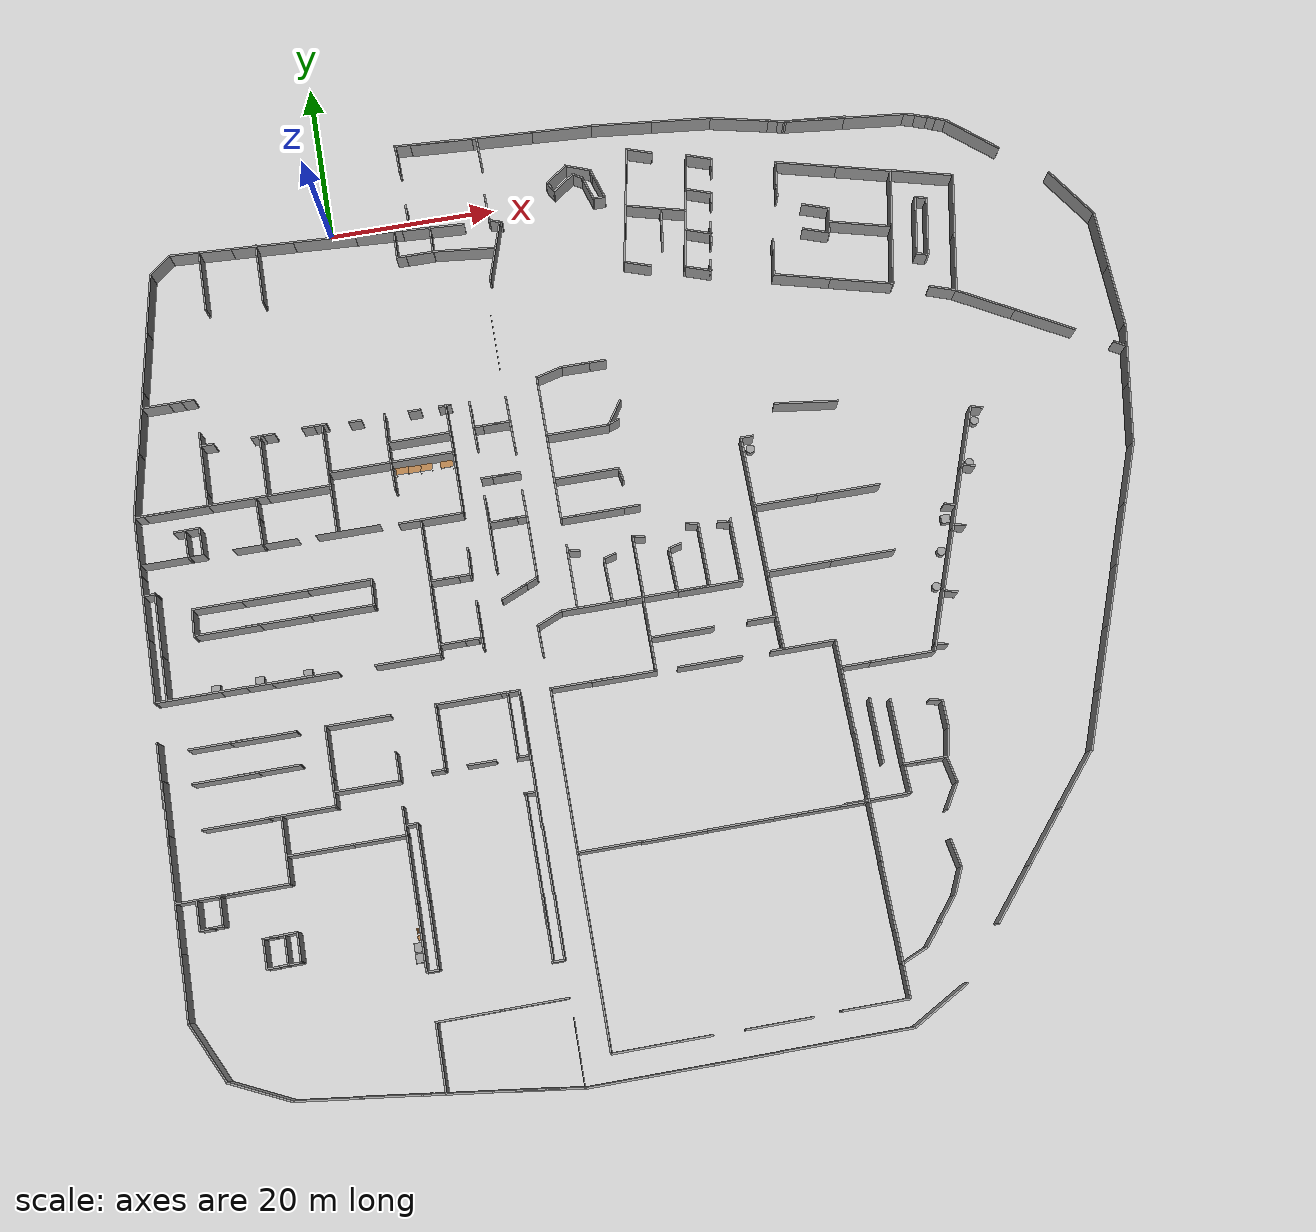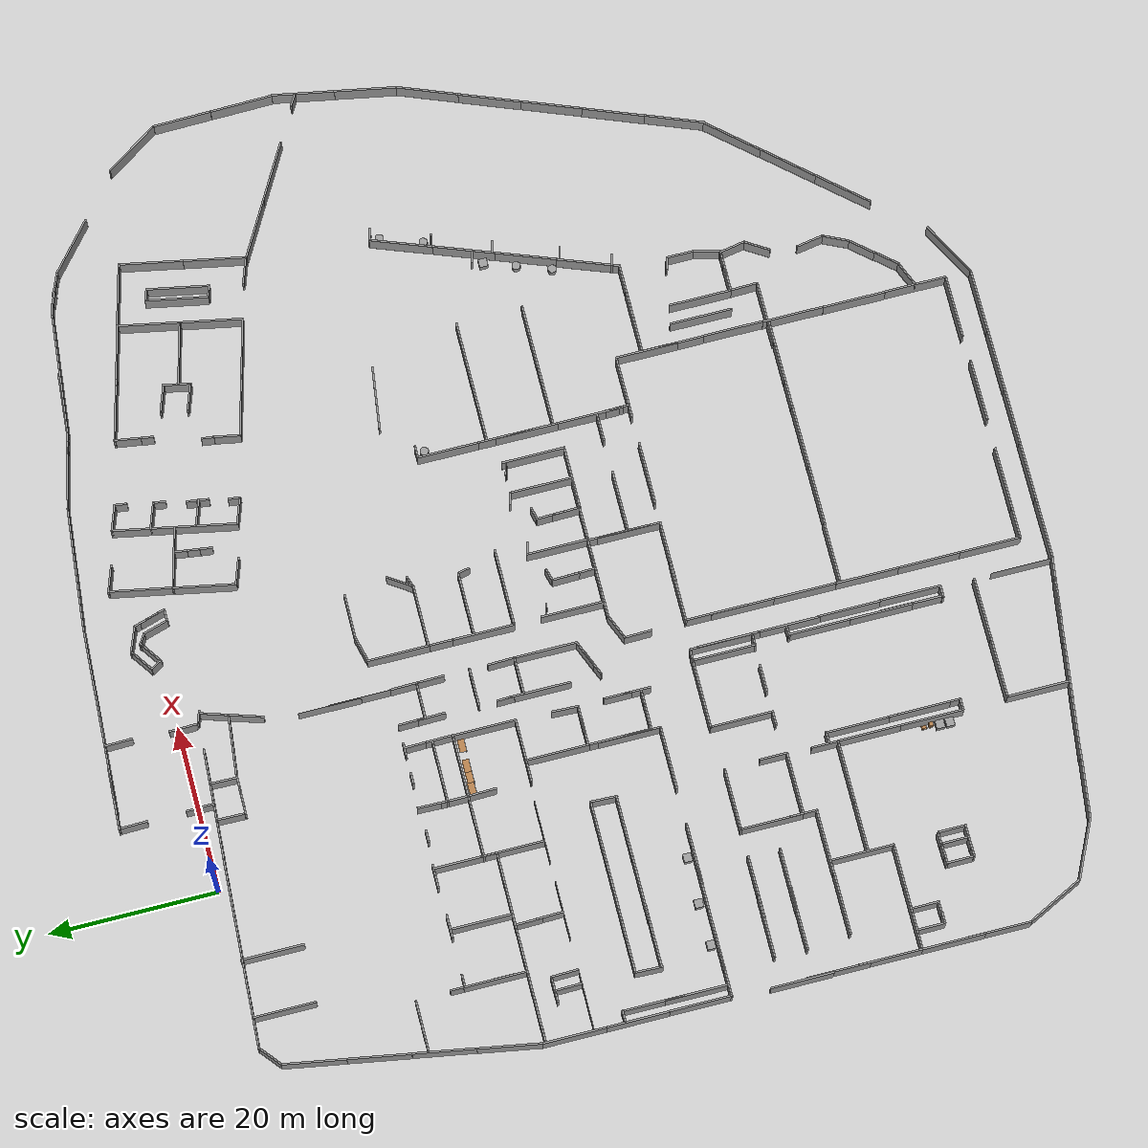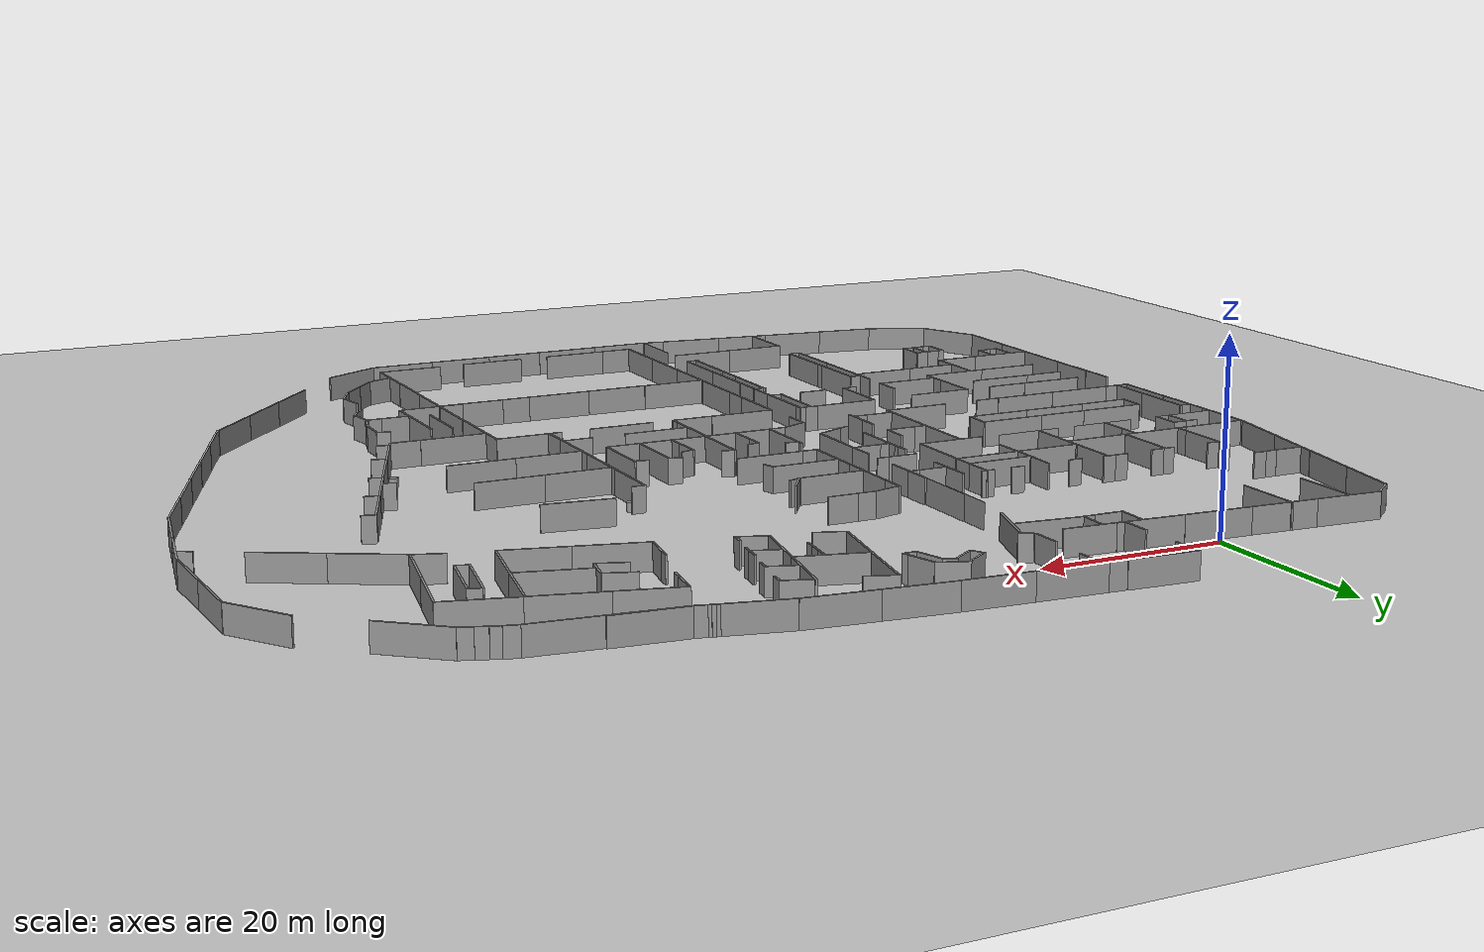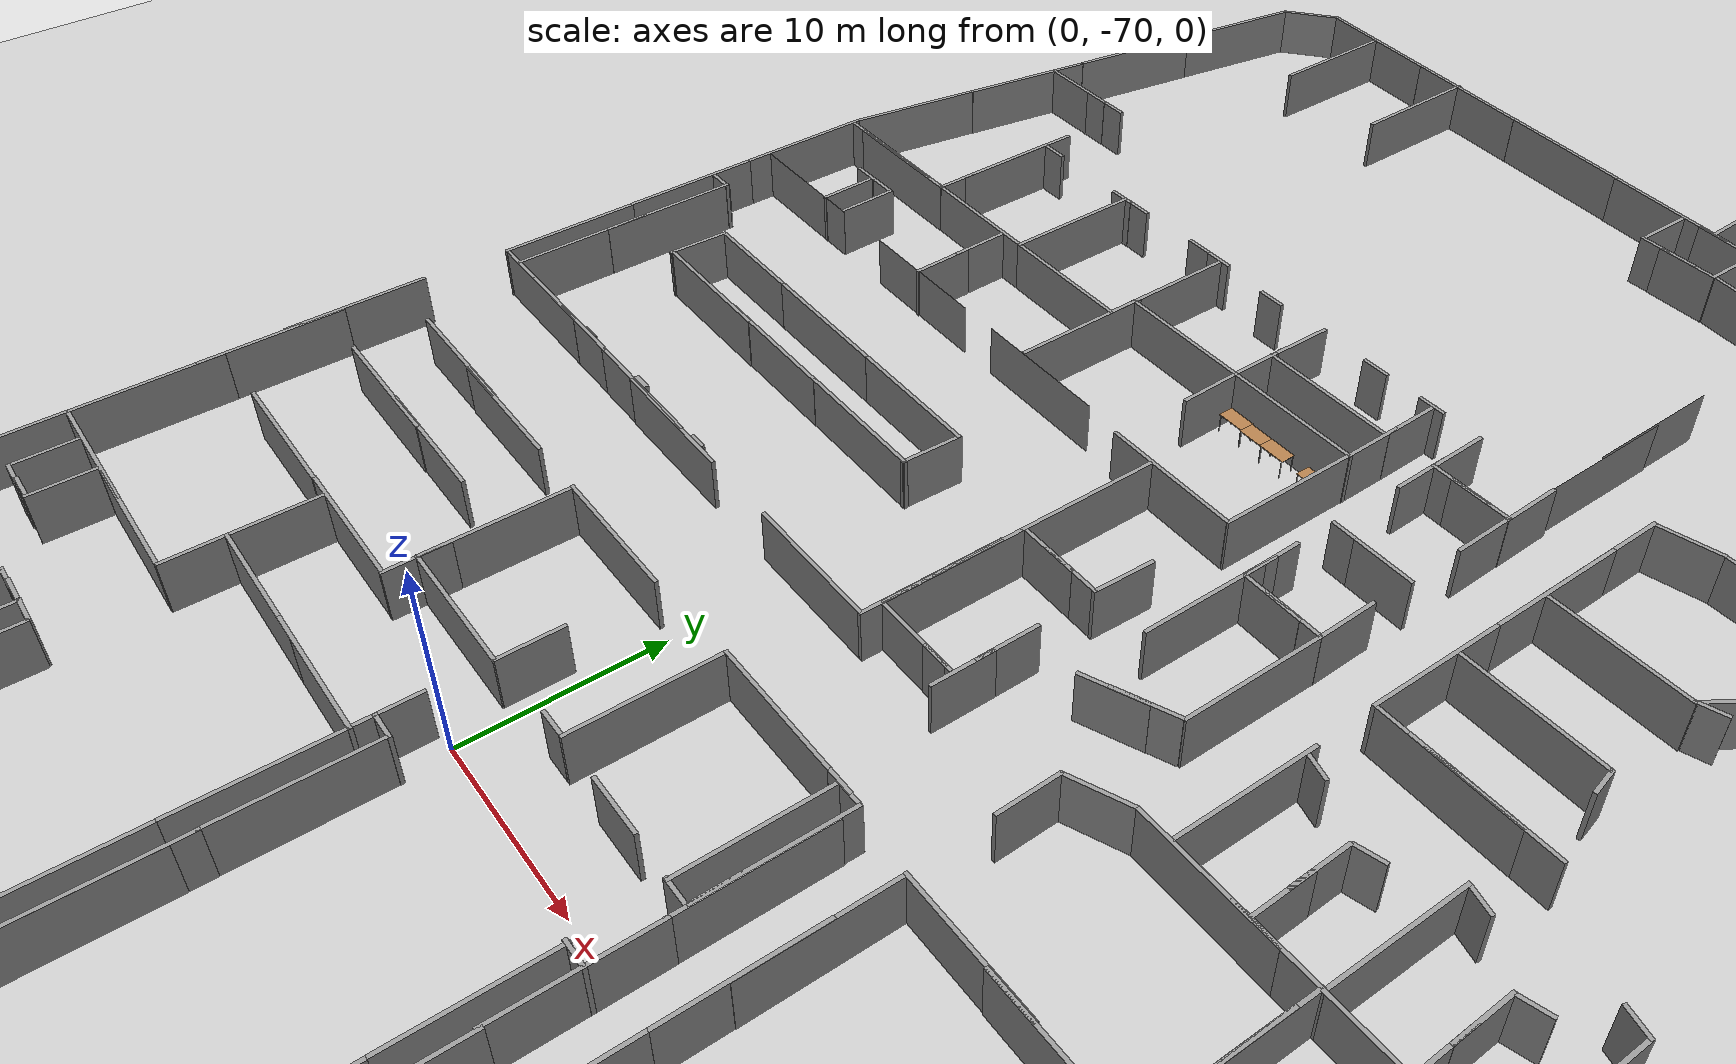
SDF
<sdf version="1.7">
 <world name="default">
  <light name="sun" type="directional">
   <pose>0 0 10 0 -0 0</pose>
   <diffuse>0.8 0.8 0.8 1</diffuse>
   <specular>0.2 0.2 0.2 1</specular>
   <attenuation>
    <range>1000</range>
    <constant>0.9</constant>
    <linear>0.01</linear>
    <quadratic>0.001</quadratic>
   </attenuation>
   <direction>-0.5 0.1 -0.9</direction>
   <spot><inner_angle>0</inner_angle><outer_angle>0</outer_angle><falloff>0</falloff></spot>
  </light>
  <model name="ground_plane">
   <static>1</static>
   <link name="link">
    <collision name="collision">
     <geometry><plane><normal>0 0 1</normal><size>100 100</size></plane></geometry>
     <surface>
      <contact><collide_bitmask>65535</collide_bitmask></contact>
      <friction><ode><mu>100</mu><mu2>50</mu2></ode></friction>
     </surface>
    </collision>
    <visual name="visual">
     <cast_shadows>0</cast_shadows>
     <geometry><plane><normal>0 0 1</normal><size>100 100</size></plane></geometry>
     <material>
      <script><uri>file://media/materials/scripts/gazebo.material</uri><name>Gazebo/Grey</name></script>
     </material>
    </visual>
   </link>
  </model>
  <gravity>0 0 -9.8</gravity>
  <magnetic_field>6e-06 2.3e-05 -4.2e-05</magnetic_field>
  <atmosphere type="adiabatic"/>
  <physics type="ode">
   <max_step_size>0.001</max_step_size>
   <real_time_factor>1</real_time_factor>
   <real_time_update_rate>1000</real_time_update_rate>
  </physics>
  <scene><ambient>0.4 0.4 0.4 1</ambient><background>0.7 0.7 0.7 1</background><shadows>1</shadows></scene>
  <spherical_coordinates>
   <surface_model>EARTH_WGS84</surface_model>
   <latitude_deg>0</latitude_deg>
   <longitude_deg>0</longitude_deg>
   <elevation>0</elevation>
   <heading_deg>0</heading_deg>
  </spherical_coordinates>
  <model name="grey_wall_clone_0">
   <static>1</static>
   <link name="link">
    <pose>0 0 1.4 0 -0 0</pose>
    <collision name="collision"><geometry><box><size>7.5 0.2 2.8</size></box></geometry></collision>
    <visual name="visual">
     <cast_shadows>0</cast_shadows>
     <geometry><box><size>7.5 0.2 2.8</size></box></geometry>
     <material>
      <script>
       <uri>model://grey_wall/materials/scripts</uri>
       <uri>model://grey_wall/materials/textures</uri>
       <name>vrc/grey_wall</name>
      </script>
     </material>
    </visual>
   </link>
   <pose>15.0501 8.9147 -0 0 0 -0.056773</pose>
  </model>
  <model name="grey_wall_clone_1">
   <static>1</static>
   <link name="link">
    <pose>0 0 1.4 0 -0 0</pose>
    <collision name="collision"><geometry><box><size>7.5 0.2 2.8</size></box></geometry></collision>
    <visual name="visual">
     <cast_shadows>0</cast_shadows>
     <geometry><box><size>7.5 0.2 2.8</size></box></geometry>
     <material>
      <script>
       <uri>model://grey_wall/materials/scripts</uri>
       <uri>model://grey_wall/materials/textures</uri>
       <name>vrc/grey_wall</name>
      </script>
     </material>
    </visual>
   </link>
   <pose>22.4047 8.49986 -0 0 0 -0.056773</pose>
  </model>
  <model name="grey_wall_clone_2">
   <static>1</static>
   <link name="link">
    <pose>0 0 1.4 0 -0 0</pose>
    <collision name="collision"><geometry><box><size>7.5 0.2 2.8</size></box></geometry></collision>
    <visual name="visual">
     <cast_shadows>0</cast_shadows>
     <geometry><box><size>7.5 0.2 2.8</size></box></geometry>
     <material>
      <script>
       <uri>model://grey_wall/materials/scripts</uri>
       <uri>model://grey_wall/materials/textures</uri>
       <name>vrc/grey_wall</name>
      </script>
     </material>
    </visual>
   </link>
   <pose>29.7028 8.10104 -0 0 0 -0.056773</pose>
  </model>
  <model name="grey_wall_clone_3">
   <static>1</static>
   <link name="link">
    <pose>0 0 1.4 0 -0 0</pose>
    <collision name="collision"><geometry><box><size>7.5 0.2 2.8</size></box></geometry></collision>
    <visual name="visual">
     <cast_shadows>0</cast_shadows>
     <geometry><box><size>7.5 0.2 2.8</size></box></geometry>
     <material>
      <script>
       <uri>model://grey_wall/materials/scripts</uri>
       <uri>model://grey_wall/materials/textures</uri>
       <name>vrc/grey_wall</name>
      </script>
     </material>
    </visual>
   </link>
   <pose>36.9941 7.53296 0 0 0 -0.103387</pose>
  </model>
  <model name="grey_wall_clone_4">
   <static>1</static>
   <link name="link">
    <pose>0 0 1.4 0 -0 0</pose>
    <collision name="collision"><geometry><box><size>7.5 0.2 2.8</size></box></geometry></collision>
    <visual name="visual">
     <cast_shadows>0</cast_shadows>
     <geometry><box><size>7.5 0.2 2.8</size></box></geometry>
     <material>
      <script>
       <uri>model://grey_wall/materials/scripts</uri>
       <uri>model://grey_wall/materials/textures</uri>
       <name>vrc/grey_wall</name>
      </script>
     </material>
    </visual>
   </link>
   <pose>-0.621791 -1.28751 -0 0 0 -0.056773</pose>
  </model>
  <model name="grey_wall_clone_4_clone">
   <static>1</static>
   <link name="link">
    <pose>0 0 1.4 0 -0 0</pose>
    <collision name="collision"><geometry><box><size>7.5 0.2 2.8</size></box></geometry></collision>
    <visual name="visual">
     <cast_shadows>0</cast_shadows>
     <geometry><box><size>7.5 0.2 2.8</size></box></geometry>
     <material>
      <script>
       <uri>model://grey_wall/materials/scripts</uri>
       <uri>model://grey_wall/materials/textures</uri>
       <name>vrc/grey_wall</name>
      </script>
     </material>
    </visual>
   </link>
   <pose>-8.10618 -0.875755 -0 0 0 -0.056773</pose>
  </model>
  <model name="grey_wall_clone_4_clone_0">
   <static>1</static>
   <link name="link">
    <pose>0 0 1.4 0 -0 0</pose>
    <collision name="collision"><geometry><box><size>7.5 0.2 2.8</size></box></geometry></collision>
    <visual name="visual">
     <cast_shadows>0</cast_shadows>
     <geometry><box><size>7.5 0.2 2.8</size></box></geometry>
     <material>
      <script>
       <uri>model://grey_wall/materials/scripts</uri>
       <uri>model://grey_wall/materials/textures</uri>
       <name>vrc/grey_wall</name>
      </script>
     </material>
    </visual>
   </link>
   <pose>-15.5562 -0.460659 -0 0 0 -0.056773</pose>
  </model>
  <model name="half_grey_wall_clone_clone_0_clone_1">
   <link name="link">
    <pose>0 0 1.4 0 -0 0</pose>
    <inertial>
     <mass>1</mass>
     <inertia><ixx>1</ixx><ixy>0</ixy><ixz>0</ixz><iyy>1</iyy><iyz>0</iyz><izz>1</izz></inertia>
    </inertial>
    <visual name="visual">
     <cast_shadows>0</cast_shadows>
     <geometry><box><size>3.3 0.2 2.8</size></box></geometry>
     <material>
      <script>
       <uri>model://grey_wall/materials/scripts</uri>
       <uri>model://grey_wall/materials/textures</uri>
       <name>vrc/grey_wall</name>
      </script>
      <shader type="pixel"><normal_map>__default__</normal_map></shader>
      <ambient>1 1 1 1</ambient>
      <diffuse>1 1 1 1</diffuse>
      <specular>0 0 0 1</specular>
      <emissive>0 0 0 1</emissive>
     </material>
    </visual>
    <collision name="collision">
     <geometry><box><size>7.5 0.2 2.8</size></box></geometry>
     <surface>
      <friction>
       <ode><mu>1</mu><mu2>1</mu2><fdir1>0 0 0</fdir1><slip1>0</slip1><slip2>0</slip2></ode>
       <torsional>
        <coefficient>1</coefficient>
        <patch_radius>0</patch_radius>
        <surface_radius>0</surface_radius>
        <use_patch_radius>1</use_patch_radius>
        <ode><slip>0</slip></ode>
       </torsional>
      </friction>
      <bounce><restitution_coefficient>0</restitution_coefficient><threshold>1e+06</threshold></bounce>
      <contact>
       <collide_without_contact>0</collide_without_contact>
       <collide_without_contact_bitmask>1</collide_without_contact_bitmask>
       <collide_bitmask>1</collide_bitmask>
       <ode>
        <soft_cfm>0</soft_cfm>
        <soft_erp>0.2</soft_erp>
        <kp>1e+13</kp>
        <kd>1</kd>
        <max_vel>0.01</max_vel>
        <min_depth>0</min_depth>
       </ode>
       <bullet>
        <split_impulse>1</split_impulse>
        <split_impulse_penetration_threshold>-0.01</split_impulse_penetration_threshold>
        <soft_cfm>0</soft_cfm>
        <soft_erp>0.2</soft_erp>
        <kp>1e+13</kp>
        <kd>1</kd>
       </bullet>
      </contact>
     </surface>
    </collision>
   </link>
   <static>1</static>
   <pose>-20.4293 -1.28686 0 0 0 -2.44925</pose>
  </model>
  <model name="grey_wall_clone_4_clone_0_clone">
   <static>1</static>
   <link name="link">
    <pose>0 0 1.4 0 -0 0</pose>
    <collision name="collision"><geometry><box><size>7.5 0.2 2.8</size></box></geometry></collision>
    <visual name="visual">
     <cast_shadows>0</cast_shadows>
     <geometry><box><size>7.5 0.2 2.8</size></box></geometry>
     <material>
      <script>
       <uri>model://grey_wall/materials/scripts</uri>
       <uri>model://grey_wall/materials/textures</uri>
       <name>vrc/grey_wall</name>
      </script>
     </material>
    </visual>
   </link>
   <pose>-22.3009 -5.96343 0 0 -0 1.40189</pose>
  </model>
  <model name="grey_wall_clone_4_clone_0_clone_clone">
   <static>1</static>
   <link name="link">
    <pose>0 0 1.4 0 -0 0</pose>
    <collision name="collision"><geometry><box><size>7.5 0.2 2.8</size></box></geometry></collision>
    <visual name="visual">
     <cast_shadows>0</cast_shadows>
     <geometry><box><size>7.5 0.2 2.8</size></box></geometry>
     <material>
      <script>
       <uri>model://grey_wall/materials/scripts</uri>
       <uri>model://grey_wall/materials/textures</uri>
       <name>vrc/grey_wall</name>
      </script>
     </material>
    </visual>
   </link>
   <pose>-23.5347 -13.2753 0 0 -0 1.40189</pose>
  </model>
  <model name="grey_wall_clone_4_clone_0_clone_clone_clone">
   <static>1</static>
   <link name="link">
    <pose>0 0 1.4 0 -0 0</pose>
    <collision name="collision"><geometry><box><size>7.5 0.2 2.8</size></box></geometry></collision>
    <visual name="visual">
     <cast_shadows>0</cast_shadows>
     <geometry><box><size>7.5 0.2 2.8</size></box></geometry>
     <material>
      <script>
       <uri>model://grey_wall/materials/scripts</uri>
       <uri>model://grey_wall/materials/textures</uri>
       <name>vrc/grey_wall</name>
      </script>
     </material>
    </visual>
   </link>
   <pose>-24.7789 -20.6957 0 0 -0 1.40189</pose>
  </model>
  <model name="grey_wall_clone_4_clone_0_clone_clone_clone_0">
   <static>1</static>
   <link name="link">
    <pose>0 0 1.4 0 -0 0</pose>
    <collision name="collision"><geometry><box><size>7.5 0.2 2.8</size></box></geometry></collision>
    <visual name="visual">
     <cast_shadows>0</cast_shadows>
     <geometry><box><size>7.5 0.2 2.8</size></box></geometry>
     <material>
      <script>
       <uri>model://grey_wall/materials/scripts</uri>
       <uri>model://grey_wall/materials/textures</uri>
       <name>vrc/grey_wall</name>
      </script>
     </material>
    </visual>
   </link>
   <pose>-26.0476 -27.9911 0 0 -0 1.40189</pose>
  </model>
  <model name="grey_wall_0">
   <static>1</static>
   <link name="link">
    <pose>0 0 1.4 0 -0 0</pose>
    <collision name="collision"><geometry><box><size>7.5 0.2 2.8</size></box></geometry></collision>
    <visual name="visual">
     <cast_shadows>0</cast_shadows>
     <geometry><box><size>7.5 0.2 2.8</size></box></geometry>
     <material>
      <script>
       <uri>model://grey_wall/materials/scripts</uri>
       <uri>model://grey_wall/materials/textures</uri>
       <name>vrc/grey_wall</name>
      </script>
     </material>
    </visual>
   </link>
   <pose>-26.6933 -35.4117 0 0 -0 1.5708</pose>
  </model>
  <model name="grey_wall_0_clone">
   <static>1</static>
   <link name="link">
    <pose>0 0 1.4 0 -0 0</pose>
    <collision name="collision"><geometry><box><size>7.5 0.2 2.8</size></box></geometry></collision>
    <visual name="visual">
     <cast_shadows>0</cast_shadows>
     <geometry><box><size>7.5 0.2 2.8</size></box></geometry>
     <material>
      <script>
       <uri>model://grey_wall/materials/scripts</uri>
       <uri>model://grey_wall/materials/textures</uri>
       <name>vrc/grey_wall</name>
      </script>
     </material>
    </visual>
   </link>
   <pose>-26.6851 -42.8415 0 0 -0 1.5708</pose>
  </model>
  <model name="grey_wall_0_clone_0">
   <static>1</static>
   <link name="link">
    <pose>0 0 1.4 0 -0 0</pose>
    <collision name="collision"><geometry><box><size>7.5 0.2 2.8</size></box></geometry></collision>
    <visual name="visual">
     <cast_shadows>0</cast_shadows>
     <geometry><box><size>7.5 0.2 2.8</size></box></geometry>
     <material>
      <script>
       <uri>model://grey_wall/materials/scripts</uri>
       <uri>model://grey_wall/materials/textures</uri>
       <name>vrc/grey_wall</name>
      </script>
     </material>
    </visual>
   </link>
   <pose>-26.661 -50.2699 0 0 -0 1.5708</pose>
  </model>
  <model name="grey_wall_1">
   <static>1</static>
   <link name="link">
    <pose>0 0 1.4 0 -0 0</pose>
    <collision name="collision"><geometry><box><size>7.5 0.2 2.8</size></box></geometry></collision>
    <visual name="visual">
     <cast_shadows>0</cast_shadows>
     <geometry><box><size>7.5 0.2 2.8</size></box></geometry>
     <material>
      <script>
       <uri>model://grey_wall/materials/scripts</uri>
       <uri>model://grey_wall/materials/textures</uri>
       <name>vrc/grey_wall</name>
      </script>
     </material>
    </visual>
   </link>
   <pose>-23.0024 -32.0318 0 0 -0 0</pose>
  </model>
  <model name="grey_wall_1_clone">
   <static>1</static>
   <link name="link">
    <pose>0 0 1.4 0 -0 0</pose>
    <collision name="collision"><geometry><box><size>7.5 0.2 2.8</size></box></geometry></collision>
    <visual name="visual">
     <cast_shadows>0</cast_shadows>
     <geometry><box><size>7.5 0.2 2.8</size></box></geometry>
     <material>
      <script>
       <uri>model://grey_wall/materials/scripts</uri>
       <uri>model://grey_wall/materials/textures</uri>
       <name>vrc/grey_wall</name>
      </script>
     </material>
    </visual>
   </link>
   <pose>-21.8571 -32.0378 0 0 -0 0</pose>
  </model>
  <model name="grey_wall_0_clone_clone">
   <static>1</static>
   <link name="link">
    <pose>0 0 1.4 0 -0 0</pose>
    <collision name="collision"><geometry><box><size>7.5 0.2 2.8</size></box></geometry></collision>
    <visual name="visual">
     <cast_shadows>0</cast_shadows>
     <geometry><box><size>7.5 0.2 2.8</size></box></geometry>
     <material>
      <script>
       <uri>model://grey_wall/materials/scripts</uri>
       <uri>model://grey_wall/materials/textures</uri>
       <name>vrc/grey_wall</name>
      </script>
     </material>
    </visual>
   </link>
   <pose>-18.1917 -28.2741 0 0 -0 1.5708</pose>
  </model>
  <model name="half_grey_wall_clone_clone">
   <link name="link">
    <pose>0 0 1.4 0 -0 0</pose>
    <inertial>
     <mass>1</mass>
     <inertia><ixx>1</ixx><ixy>0</ixy><ixz>0</ixz><iyy>1</iyy><iyz>0</iyz><izz>1</izz></inertia>
    </inertial>
    <visual name="visual">
     <cast_shadows>0</cast_shadows>
     <geometry><box><size>3.3 0.2 2.8</size></box></geometry>
     <material>
      <script>
       <uri>model://grey_wall/materials/scripts</uri>
       <uri>model://grey_wall/materials/textures</uri>
       <name>vrc/grey_wall</name>
      </script>
      <shader type="pixel"><normal_map>__default__</normal_map></shader>
      <ambient>1 1 1 1</ambient>
      <diffuse>1 1 1 1</diffuse>
      <specular>0 0 0 1</specular>
      <emissive>0 0 0 1</emissive>
     </material>
    </visual>
    <collision name="collision">
     <geometry><box><size>7.5 0.2 2.8</size></box></geometry>
     <surface>
      <friction>
       <ode><mu>1</mu><mu2>1</mu2><fdir1>0 0 0</fdir1><slip1>0</slip1><slip2>0</slip2></ode>
       <torsional>
        <coefficient>1</coefficient>
        <patch_radius>0</patch_radius>
        <surface_radius>0</surface_radius>
        <use_patch_radius>1</use_patch_radius>
        <ode><slip>0</slip></ode>
       </torsional>
      </friction>
      <bounce><restitution_coefficient>0</restitution_coefficient><threshold>1e+06</threshold></bounce>
      <contact>
       <collide_without_contact>0</collide_without_contact>
       <collide_without_contact_bitmask>1</collide_without_contact_bitmask>
       <collide_bitmask>1</collide_bitmask>
       <ode>
        <soft_cfm>0</soft_cfm>
        <soft_erp>0.2</soft_erp>
        <kp>1e+13</kp>
        <kd>1</kd>
        <max_vel>0.01</max_vel>
        <min_depth>0</min_depth>
       </ode>
       <bullet>
        <split_impulse>1</split_impulse>
        <split_impulse_penetration_threshold>-0.01</split_impulse_penetration_threshold>
        <soft_cfm>0</soft_cfm>
        <soft_erp>0.2</soft_erp>
        <kp>1e+13</kp>
        <kd>1</kd>
       </bullet>
      </contact>
     </surface>
    </collision>
   </link>
   <static>1</static>
   <pose>-22.8174 -18.896 0 0 0 -3.13942</pose>
  </model>
  <model name="grey_wall_1_clone_clone">
   <static>1</static>
   <link name="link">
    <pose>0 0 1.4 0 -0 0</pose>
    <collision name="collision"><geometry><box><size>7.5 0.2 2.8</size></box></geometry></collision>
    <visual name="visual">
     <cast_shadows>0</cast_shadows>
     <geometry><box><size>7.5 0.2 2.8</size></box></geometry>
     <material>
      <script>
       <uri>model://grey_wall/materials/scripts</uri>
       <uri>model://grey_wall/materials/textures</uri>
       <name>vrc/grey_wall</name>
      </script>
     </material>
    </visual>
   </link>
   <pose>-14.9465 -32.0283 0 0 -0 0</pose>
  </model>
  <model name="grey_wall_0_clone_clone_clone">
   <static>1</static>
   <link name="link">
    <pose>0 0 1.4 0 -0 0</pose>
    <collision name="collision"><geometry><box><size>7.5 0.2 2.8</size></box></geometry></collision>
    <visual name="visual">
     <cast_shadows>0</cast_shadows>
     <geometry><box><size>7.5 0.2 2.8</size></box></geometry>
     <material>
      <script>
       <uri>model://grey_wall/materials/scripts</uri>
       <uri>model://grey_wall/materials/textures</uri>
       <name>vrc/grey_wall</name>
      </script>
     </material>
    </visual>
   </link>
   <pose>-11.3122 -28.3763 0 0 -0 1.5708</pose>
  </model>
  <model name="grey_wall_1_clone_clone_clone">
   <static>1</static>
   <link name="link">
    <pose>0 0 1.4 0 -0 0</pose>
    <collision name="collision"><geometry><box><size>7.5 0.2 2.8</size></box></geometry></collision>
    <visual name="visual">
     <cast_shadows>0</cast_shadows>
     <geometry><box><size>7.5 0.2 2.8</size></box></geometry>
     <material>
      <script>
       <uri>model://grey_wall/materials/scripts</uri>
       <uri>model://grey_wall/materials/textures</uri>
       <name>vrc/grey_wall</name>
      </script>
     </material>
    </visual>
   </link>
   <pose>-7.60364 -32.0391 0 0 -0 0</pose>
  </model>
  <model name="grey_wall_0_clone_clone_clone_1_clone">
   <static>1</static>
   <link name="link">
    <pose>0 0 1.4 0 -0 0</pose>
    <collision name="collision"><geometry><box><size>7.5 0.2 2.8</size></box></geometry></collision>
    <visual name="visual">
     <cast_shadows>0</cast_shadows>
     <geometry><box><size>7.5 0.2 2.8</size></box></geometry>
     <material>
      <script>
       <uri>model://grey_wall/materials/scripts</uri>
       <uri>model://grey_wall/materials/textures</uri>
       <name>vrc/grey_wall</name>
      </script>
     </material>
    </visual>
   </link>
   <pose>-3.96417 -28.2463 0 0 -0 1.5708</pose>
  </model>
  <model name="grey_wall_0_clone_clone_clone_0">
   <static>1</static>
   <link name="link">
    <pose>0 0 1.4 0 -0 0</pose>
    <collision name="collision"><geometry><box><size>7.5 0.2 2.8</size></box></geometry></collision>
    <visual name="visual">
     <cast_shadows>0</cast_shadows>
     <geometry><box><size>7.5 0.2 2.8</size></box></geometry>
     <material>
      <script>
       <uri>model://grey_wall/materials/scripts</uri>
       <uri>model://grey_wall/materials/textures</uri>
       <name>vrc/grey_wall</name>
      </script>
     </material>
    </visual>
   </link>
   <pose>-18.1803 -26.7144 0 0 -0 1.5708</pose>
  </model>
  <model name="grey_wall_1_clone_clone_clone_clone">
   <static>1</static>
   <link name="link">
    <pose>0 0 1.4 0 -0 0</pose>
    <collision name="collision"><geometry><box><size>7.5 0.2 2.8</size></box></geometry></collision>
    <visual name="visual">
     <cast_shadows>0</cast_shadows>
     <geometry><box><size>7.5 0.2 2.8</size></box></geometry>
     <material>
      <script>
       <uri>model://grey_wall/materials/scripts</uri>
       <uri>model://grey_wall/materials/textures</uri>
       <name>vrc/grey_wall</name>
      </script>
     </material>
    </visual>
   </link>
   <pose>-0.339107 -30.4881 0 0 -0 0</pose>
  </model>
  <model name="half_grey_wall_clone_clone_clone_clone">
   <link name="link">
    <pose>0 0 1.4 0 -0 0</pose>
    <inertial>
     <mass>1</mass>
     <inertia><ixx>1</ixx><ixy>0</ixy><ixz>0</ixz><iyy>1</iyy><iyz>0</iyz><izz>1</izz></inertia>
    </inertial>
    <visual name="visual">
     <cast_shadows>0</cast_shadows>
     <geometry><box><size>3.3 0.2 2.8</size></box></geometry>
     <material>
      <script>
       <uri>model://grey_wall/materials/scripts</uri>
       <uri>model://grey_wall/materials/textures</uri>
       <name>vrc/grey_wall</name>
      </script>
      <shader type="pixel"><normal_map>__default__</normal_map></shader>
      <ambient>1 1 1 1</ambient>
      <diffuse>1 1 1 1</diffuse>
      <specular>0 0 0 1</specular>
      <emissive>0 0 0 1</emissive>
     </material>
    </visual>
    <collision name="collision">
     <geometry><box><size>7.5 0.2 2.8</size></box></geometry>
     <surface>
      <friction>
       <ode><mu>1</mu><mu2>1</mu2><fdir1>0 0 0</fdir1><slip1>0</slip1><slip2>0</slip2></ode>
       <torsional>
        <coefficient>1</coefficient>
        <patch_radius>0</patch_radius>
        <surface_radius>0</surface_radius>
        <use_patch_radius>1</use_patch_radius>
        <ode><slip>0</slip></ode>
       </torsional>
      </friction>
      <bounce><restitution_coefficient>0</restitution_coefficient><threshold>1e+06</threshold></bounce>
      <contact>
       <collide_without_contact>0</collide_without_contact>
       <collide_without_contact_bitmask>1</collide_without_contact_bitmask>
       <collide_bitmask>1</collide_bitmask>
       <ode>
        <soft_cfm>0</soft_cfm>
        <soft_erp>0.2</soft_erp>
        <kp>1e+13</kp>
        <kd>1</kd>
        <max_vel>0.01</max_vel>
        <min_depth>0</min_depth>
       </ode>
       <bullet>
        <split_impulse>1</split_impulse>
        <split_impulse_penetration_threshold>-0.01</split_impulse_penetration_threshold>
        <soft_cfm>0</soft_cfm>
        <soft_erp>0.2</soft_erp>
        <kp>1e+13</kp>
        <kd>1</kd>
       </bullet>
      </contact>
     </surface>
    </collision>
   </link>
   <static>1</static>
   <pose>3.29729 -28.8904 0 0 0 -1.56862</pose>
  </model>
  <model name="grey_wall_1_clone_clone_clone_clone_clone">
   <static>1</static>
   <link name="link">
    <pose>0 0 1.4 0 -0 0</pose>
    <collision name="collision"><geometry><box><size>7.5 0.2 2.8</size></box></geometry></collision>
    <visual name="visual">
     <cast_shadows>0</cast_shadows>
     <geometry><box><size>7.5 0.2 2.8</size></box></geometry>
     <material>
      <script>
       <uri>model://grey_wall/materials/scripts</uri>
       <uri>model://grey_wall/materials/textures</uri>
       <name>vrc/grey_wall</name>
      </script>
     </material>
    </visual>
   </link>
   <pose>7.06177 -30.4838 0 0 -0 0</pose>
  </model>
  <model name="grey_wall_1_clone_clone_clone_clone_clone_clone">
   <static>1</static>
   <link name="link">
    <pose>0 0 1.4 0 -0 0</pose>
    <collision name="collision"><geometry><box><size>7.5 0.2 2.8</size></box></geometry></collision>
    <visual name="visual">
     <cast_shadows>0</cast_shadows>
     <geometry><box><size>7.5 0.2 2.8</size></box></geometry>
     <material>
      <script>
       <uri>model://grey_wall/materials/scripts</uri>
       <uri>model://grey_wall/materials/textures</uri>
       <name>vrc/grey_wall</name>
      </script>
     </material>
    </visual>
   </link>
   <pose>6.92384 -28.0433 0 0 -0 0</pose>
  </model>
  <model name="half_grey_wall_clone_clone_0_clone_2">
   <link name="link">
    <pose>0 0 1.4 0 -0 0</pose>
    <inertial>
     <mass>1</mass>
     <inertia><ixx>1</ixx><ixy>0</ixy><ixz>0</ixz><iyy>1</iyy><iyz>0</iyz><izz>1</izz></inertia>
    </inertial>
    <visual name="visual">
     <cast_shadows>0</cast_shadows>
     <geometry><box><size>3.3 0.2 2.8</size></box></geometry>
     <material>
      <script>
       <uri>model://grey_wall/materials/scripts</uri>
       <uri>model://grey_wall/materials/textures</uri>
       <name>vrc/grey_wall</name>
      </script>
      <shader type="pixel"><normal_map>__default__</normal_map></shader>
      <ambient>1 1 1 1</ambient>
      <diffuse>1 1 1 1</diffuse>
      <specular>0 0 0 1</specular>
      <emissive>0 0 0 1</emissive>
     </material>
    </visual>
    <collision name="collision">
     <geometry><box><size>7.5 0.2 2.8</size></box></geometry>
     <surface>
      <friction>
       <ode><mu>1</mu><mu2>1</mu2><fdir1>0 0 0</fdir1><slip1>0</slip1><slip2>0</slip2></ode>
       <torsional>
        <coefficient>1</coefficient>
        <patch_radius>0</patch_radius>
        <surface_radius>0</surface_radius>
        <use_patch_radius>1</use_patch_radius>
        <ode><slip>0</slip></ode>
       </torsional>
      </friction>
      <bounce><restitution_coefficient>0</restitution_coefficient><threshold>1e+06</threshold></bounce>
      <contact>
       <collide_without_contact>0</collide_without_contact>
       <collide_without_contact_bitmask>1</collide_without_contact_bitmask>
       <collide_bitmask>1</collide_bitmask>
       <ode>
        <soft_cfm>0</soft_cfm>
        <soft_erp>0.2</soft_erp>
        <kp>1e+13</kp>
        <kd>1</kd>
        <max_vel>0.01</max_vel>
        <min_depth>0</min_depth>
       </ode>
       <bullet>
        <split_impulse>1</split_impulse>
        <split_impulse_penetration_threshold>-0.01</split_impulse_penetration_threshold>
        <soft_cfm>0</soft_cfm>
        <soft_erp>0.2</soft_erp>
        <kp>1e+13</kp>
        <kd>1</kd>
       </bullet>
      </contact>
     </surface>
    </collision>
   </link>
   <static>1</static>
   <pose>10.6733 -28.9112 0 0 0 -1.55647</pose>
  </model>
  <model name="grey_wall_0_clone_clone_clone_0_clone">
   <static>1</static>
   <link name="link">
    <pose>0 0 1.4 0 -0 0</pose>
    <collision name="collision"><geometry><box><size>7.5 0.2 2.8</size></box></geometry></collision>
    <visual name="visual">
     <cast_shadows>0</cast_shadows>
     <geometry><box><size>7.5 0.2 2.8</size></box></geometry>
     <material>
      <script>
       <uri>model://grey_wall/materials/scripts</uri>
       <uri>model://grey_wall/materials/textures</uri>
       <name>vrc/grey_wall</name>
      </script>
     </material>
    </visual>
   </link>
   <pose>10.6732 -34.2817 0 0 -0 1.5708</pose>
  </model>
  <model name="grey_wall_1_clone_clone_clone_clone_clone_clone_0">
   <static>1</static>
   <link name="link">
    <pose>0 0 1.4 0 -0 0</pose>
    <collision name="collision"><geometry><box><size>7.5 0.2 2.8</size></box></geometry></collision>
    <visual name="visual">
     <cast_shadows>0</cast_shadows>
     <geometry><box><size>7.5 0.2 2.8</size></box></geometry>
     <material>
      <script>
       <uri>model://grey_wall/materials/scripts</uri>
       <uri>model://grey_wall/materials/textures</uri>
       <name>vrc/grey_wall</name>
      </script>
     </material>
    </visual>
   </link>
   <pose>6.90726 -37.9572 0 0 -0 0</pose>
  </model>
  <model name="table">
   <static>1</static>
   <link name="link">
    <collision name="surface">
     <pose>0 0 1 0 -0 0</pose>
     <geometry><box><size>1.5 0.8 0.03</size></box></geometry>
     <surface><friction><ode><mu>0.6</mu><mu2>0.6</mu2></ode></friction></surface>
    </collision>
    <visual name="visual1">
     <pose>0 0 1 0 -0 0</pose>
     <geometry><box><size>1.5 0.8 0.03</size></box></geometry>
     <material>
      <script><uri>file://media/materials/scripts/gazebo.material</uri><name>Gazebo/Wood</name></script>
     </material>
    </visual>
    <collision name="front_left_leg">
     <pose>0.68 0.38 0.5 0 -0 0</pose>
     <geometry><cylinder><radius>0.02</radius><length>1</length></cylinder></geometry>
    </collision>
    <visual name="front_left_leg">
     <pose>0.68 0.38 0.5 0 -0 0</pose>
     <geometry><cylinder><radius>0.02</radius><length>1</length></cylinder></geometry>
     <material>
      <script><uri>file://media/materials/scripts/gazebo.material</uri><name>Gazebo/Grey</name></script>
     </material>
    </visual>
    <collision name="front_right_leg">
     <pose>0.68 -0.38 0.5 0 -0 0</pose>
     <geometry><cylinder><radius>0.02</radius><length>1</length></cylinder></geometry>
    </collision>
    <visual name="front_right_leg">
     <pose>0.68 -0.38 0.5 0 -0 0</pose>
     <geometry><cylinder><radius>0.02</radius><length>1</length></cylinder></geometry>
     <material>
      <script><uri>file://media/materials/scripts/gazebo.material</uri><name>Gazebo/Grey</name></script>
     </material>
    </visual>
    <collision name="back_right_leg">
     <pose>-0.68 -0.38 0.5 0 -0 0</pose>
     <geometry><cylinder><radius>0.02</radius><length>1</length></cylinder></geometry>
    </collision>
    <visual name="back_right_leg">
     <pose>-0.68 -0.38 0.5 0 -0 0</pose>
     <geometry><cylinder><radius>0.02</radius><length>1</length></cylinder></geometry>
     <material>
      <script><uri>file://media/materials/scripts/gazebo.material</uri><name>Gazebo/Grey</name></script>
     </material>
    </visual>
    <collision name="back_left_leg">
     <pose>-0.68 0.38 0.5 0 -0 0</pose>
     <geometry><cylinder><radius>0.02</radius><length>1</length></cylinder></geometry>
    </collision>
    <visual name="back_left_leg">
     <pose>-0.68 0.38 0.5 0 -0 0</pose>
     <geometry><cylinder><radius>0.02</radius><length>1</length></cylinder></geometry>
     <material>
      <script><uri>file://media/materials/scripts/gazebo.material</uri><name>Gazebo/Grey</name></script>
     </material>
    </visual>
   </link>
   <pose>4.37833 -31.1782 0 0 -0 0</pose>
  </model>
  <model name="table_clone">
   <static>1</static>
   <link name="link">
    <collision name="surface">
     <pose>0 0 1 0 -0 0</pose>
     <geometry><box><size>1.5 0.8 0.03</size></box></geometry>
     <surface><friction><ode><mu>0.6</mu><mu2>0.6</mu2></ode></friction></surface>
    </collision>
    <visual name="visual1">
     <pose>0 0 1 0 -0 0</pose>
     <geometry><box><size>1.5 0.8 0.03</size></box></geometry>
     <material>
      <script><uri>file://media/materials/scripts/gazebo.material</uri><name>Gazebo/Wood</name></script>
     </material>
    </visual>
    <collision name="front_left_leg">
     <pose>0.68 0.38 0.5 0 -0 0</pose>
     <geometry><cylinder><radius>0.02</radius><length>1</length></cylinder></geometry>
    </collision>
    <visual name="front_left_leg">
     <pose>0.68 0.38 0.5 0 -0 0</pose>
     <geometry><cylinder><radius>0.02</radius><length>1</length></cylinder></geometry>
     <material>
      <script><uri>file://media/materials/scripts/gazebo.material</uri><name>Gazebo/Grey</name></script>
     </material>
    </visual>
    <collision name="front_right_leg">
     <pose>0.68 -0.38 0.5 0 -0 0</pose>
     <geometry><cylinder><radius>0.02</radius><length>1</length></cylinder></geometry>
    </collision>
    <visual name="front_right_leg">
     <pose>0.68 -0.38 0.5 0 -0 0</pose>
     <geometry><cylinder><radius>0.02</radius><length>1</length></cylinder></geometry>
     <material>
      <script><uri>file://media/materials/scripts/gazebo.material</uri><name>Gazebo/Grey</name></script>
     </material>
    </visual>
    <collision name="back_right_leg">
     <pose>-0.68 -0.38 0.5 0 -0 0</pose>
     <geometry><cylinder><radius>0.02</radius><length>1</length></cylinder></geometry>
    </collision>
    <visual name="back_right_leg">
     <pose>-0.68 -0.38 0.5 0 -0 0</pose>
     <geometry><cylinder><radius>0.02</radius><length>1</length></cylinder></geometry>
     <material>
      <script><uri>file://media/materials/scripts/gazebo.material</uri><name>Gazebo/Grey</name></script>
     </material>
    </visual>
    <collision name="back_left_leg">
     <pose>-0.68 0.38 0.5 0 -0 0</pose>
     <geometry><cylinder><radius>0.02</radius><length>1</length></cylinder></geometry>
    </collision>
    <visual name="back_left_leg">
     <pose>-0.68 0.38 0.5 0 -0 0</pose>
     <geometry><cylinder><radius>0.02</radius><length>1</length></cylinder></geometry>
     <material>
      <script><uri>file://media/materials/scripts/gazebo.material</uri><name>Gazebo/Grey</name></script>
     </material>
    </visual>
   </link>
   <pose>5.83379 -31.2407 0 0 -0 0</pose>
  </model>
  <model name="table_clone_0">
   <static>1</static>
   <link name="link">
    <collision name="surface">
     <pose>0 0 1 0 -0 0</pose>
     <geometry><box><size>1.5 0.8 0.03</size></box></geometry>
     <surface><friction><ode><mu>0.6</mu><mu2>0.6</mu2></ode></friction></surface>
    </collision>
    <visual name="visual1">
     <pose>0 0 1 0 -0 0</pose>
     <geometry><box><size>1.5 0.8 0.03</size></box></geometry>
     <material>
      <script><uri>file://media/materials/scripts/gazebo.material</uri><name>Gazebo/Wood</name></script>
     </material>
    </visual>
    <collision name="front_left_leg">
     <pose>0.68 0.38 0.5 0 -0 0</pose>
     <geometry><cylinder><radius>0.02</radius><length>1</length></cylinder></geometry>
    </collision>
    <visual name="front_left_leg">
     <pose>0.68 0.38 0.5 0 -0 0</pose>
     <geometry><cylinder><radius>0.02</radius><length>1</length></cylinder></geometry>
     <material>
      <script><uri>file://media/materials/scripts/gazebo.material</uri><name>Gazebo/Grey</name></script>
     </material>
    </visual>
    <collision name="front_right_leg">
     <pose>0.68 -0.38 0.5 0 -0 0</pose>
     <geometry><cylinder><radius>0.02</radius><length>1</length></cylinder></geometry>
    </collision>
    <visual name="front_right_leg">
     <pose>0.68 -0.38 0.5 0 -0 0</pose>
     <geometry><cylinder><radius>0.02</radius><length>1</length></cylinder></geometry>
     <material>
      <script><uri>file://media/materials/scripts/gazebo.material</uri><name>Gazebo/Grey</name></script>
     </material>
    </visual>
    <collision name="back_right_leg">
     <pose>-0.68 -0.38 0.5 0 -0 0</pose>
     <geometry><cylinder><radius>0.02</radius><length>1</length></cylinder></geometry>
    </collision>
    <visual name="back_right_leg">
     <pose>-0.68 -0.38 0.5 0 -0 0</pose>
     <geometry><cylinder><radius>0.02</radius><length>1</length></cylinder></geometry>
     <material>
      <script><uri>file://media/materials/scripts/gazebo.material</uri><name>Gazebo/Grey</name></script>
     </material>
    </visual>
    <collision name="back_left_leg">
     <pose>-0.68 0.38 0.5 0 -0 0</pose>
     <geometry><cylinder><radius>0.02</radius><length>1</length></cylinder></geometry>
    </collision>
    <visual name="back_left_leg">
     <pose>-0.68 0.38 0.5 0 -0 0</pose>
     <geometry><cylinder><radius>0.02</radius><length>1</length></cylinder></geometry>
     <material>
      <script><uri>file://media/materials/scripts/gazebo.material</uri><name>Gazebo/Grey</name></script>
     </material>
    </visual>
   </link>
   <pose>7.16269 -31.2407 0 0 -0 0</pose>
  </model>
  <model name="table_clone_0_clone">
   <static>1</static>
   <link name="link">
    <collision name="surface">
     <pose>0 0 1 0 -0 0</pose>
     <geometry><box><size>1.5 0.8 0.03</size></box></geometry>
     <surface><friction><ode><mu>0.6</mu><mu2>0.6</mu2></ode></friction></surface>
    </collision>
    <visual name="visual1">
     <pose>0 0 1 0 -0 0</pose>
     <geometry><box><size>1.5 0.8 0.03</size></box></geometry>
     <material>
      <script><uri>file://media/materials/scripts/gazebo.material</uri><name>Gazebo/Wood</name></script>
     </material>
    </visual>
    <collision name="front_left_leg">
     <pose>0.68 0.38 0.5 0 -0 0</pose>
     <geometry><cylinder><radius>0.02</radius><length>1</length></cylinder></geometry>
    </collision>
    <visual name="front_left_leg">
     <pose>0.68 0.38 0.5 0 -0 0</pose>
     <geometry><cylinder><radius>0.02</radius><length>1</length></cylinder></geometry>
     <material>
      <script><uri>file://media/materials/scripts/gazebo.material</uri><name>Gazebo/Grey</name></script>
     </material>
    </visual>
    <collision name="front_right_leg">
     <pose>0.68 -0.38 0.5 0 -0 0</pose>
     <geometry><cylinder><radius>0.02</radius><length>1</length></cylinder></geometry>
    </collision>
    <visual name="front_right_leg">
     <pose>0.68 -0.38 0.5 0 -0 0</pose>
     <geometry><cylinder><radius>0.02</radius><length>1</length></cylinder></geometry>
     <material>
      <script><uri>file://media/materials/scripts/gazebo.material</uri><name>Gazebo/Grey</name></script>
     </material>
    </visual>
    <collision name="back_right_leg">
     <pose>-0.68 -0.38 0.5 0 -0 0</pose>
     <geometry><cylinder><radius>0.02</radius><length>1</length></cylinder></geometry>
    </collision>
    <visual name="back_right_leg">
     <pose>-0.68 -0.38 0.5 0 -0 0</pose>
     <geometry><cylinder><radius>0.02</radius><length>1</length></cylinder></geometry>
     <material>
      <script><uri>file://media/materials/scripts/gazebo.material</uri><name>Gazebo/Grey</name></script>
     </material>
    </visual>
    <collision name="back_left_leg">
     <pose>-0.68 0.38 0.5 0 -0 0</pose>
     <geometry><cylinder><radius>0.02</radius><length>1</length></cylinder></geometry>
    </collision>
    <visual name="back_left_leg">
     <pose>-0.68 0.38 0.5 0 -0 0</pose>
     <geometry><cylinder><radius>0.02</radius><length>1</length></cylinder></geometry>
     <material>
      <script><uri>file://media/materials/scripts/gazebo.material</uri><name>Gazebo/Grey</name></script>
     </material>
    </visual>
   </link>
   <pose>9.61483 -31.2737 0 0 -0 0</pose>
  </model>
  <model name="grey_wall_0_clone_clone_clone_0_clone_0">
   <static>1</static>
   <link name="link">
    <pose>0 0 1.4 0 -0 0</pose>
    <collision name="collision"><geometry><box><size>7.5 0.2 2.8</size></box></geometry></collision>
    <visual name="visual">
     <cast_shadows>0</cast_shadows>
     <geometry><box><size>7.5 0.2 2.8</size></box></geometry>
     <material>
      <script>
       <uri>model://grey_wall/materials/scripts</uri>
       <uri>model://grey_wall/materials/textures</uri>
       <name>vrc/grey_wall</name>
      </script>
     </material>
    </visual>
   </link>
   <pose>-3.9525 -33.9249 0 0 -0 1.5708</pose>
  </model>
  <model name="slim_grey_wall">
   <link name="link">
    <pose>0 0 1.4 0 -0 0</pose>
    <inertial>
     <mass>1</mass>
     <inertia><ixx>1</ixx><ixy>0</ixy><ixz>0</ixz><iyy>1</iyy><iyz>0</iyz><izz>1</izz></inertia>
    </inertial>
    <visual name="visual">
     <cast_shadows>0</cast_shadows>
     <geometry><box><size>7.5 0.0001 2.8</size></box></geometry>
     <material>
      <script>
       <uri>model://grey_wall/materials/scripts</uri>
       <uri>model://grey_wall/materials/textures</uri>
       <name>vrc/grey_wall</name>
      </script>
      <shader type="pixel"><normal_map>__default__</normal_map></shader>
      <ambient>1 1 1 1</ambient>
      <diffuse>1 1 1 1</diffuse>
      <specular>0 0 0 1</specular>
      <emissive>0 0 0 1</emissive>
     </material>
    </visual>
    <collision name="collision">
     <geometry><box><size>7.5 0.2 2.8</size></box></geometry>
     <surface>
      <friction>
       <ode><mu>1</mu><mu2>1</mu2><fdir1>0 0 0</fdir1><slip1>0</slip1><slip2>0</slip2></ode>
       <torsional>
        <coefficient>1</coefficient>
        <patch_radius>0</patch_radius>
        <surface_radius>0</surface_radius>
        <use_patch_radius>1</use_patch_radius>
        <ode><slip>0</slip></ode>
       </torsional>
      </friction>
      <bounce><restitution_coefficient>0</restitution_coefficient><threshold>1e+06</threshold></bounce>
      <contact>
       <collide_without_contact>0</collide_without_contact>
       <collide_without_contact_bitmask>1</collide_without_contact_bitmask>
       <collide_bitmask>1</collide_bitmask>
       <ode>
        <soft_cfm>0</soft_cfm>
        <soft_erp>0.2</soft_erp>
        <kp>1e+13</kp>
        <kd>1</kd>
        <max_vel>0.01</max_vel>
        <min_depth>0</min_depth>
       </ode>
       <bullet>
        <split_impulse>1</split_impulse>
        <split_impulse_penetration_threshold>-0.01</split_impulse_penetration_threshold>
        <soft_cfm>0</soft_cfm>
        <soft_erp>0.2</soft_erp>
        <kp>1e+13</kp>
        <kd>1</kd>
       </bullet>
      </contact>
     </surface>
    </collision>
   </link>
   <static>1</static>
   <pose>-2.6753 -37.7102 0 0 -0 0</pose>
  </model>
  <model name="slim_grey_wall_clone">
   <link name="link">
    <pose>0 0 1.4 0 -0 0</pose>
    <inertial>
     <mass>1</mass>
     <inertia><ixx>1</ixx><ixy>0</ixy><ixz>0</ixz><iyy>1</iyy><iyz>0</iyz><izz>1</izz></inertia>
    </inertial>
    <visual name="visual">
     <cast_shadows>0</cast_shadows>
     <geometry><box><size>7.5 0.0001 2.8</size></box></geometry>
     <material>
      <script>
       <uri>model://grey_wall/materials/scripts</uri>
       <uri>model://grey_wall/materials/textures</uri>
       <name>vrc/grey_wall</name>
      </script>
      <shader type="pixel"><normal_map>__default__</normal_map></shader>
      <ambient>1 1 1 1</ambient>
      <diffuse>1 1 1 1</diffuse>
      <specular>0 0 0 1</specular>
      <emissive>0 0 0 1</emissive>
     </material>
    </visual>
    <collision name="collision">
     <geometry><box><size>7.5 0.2 2.8</size></box></geometry>
     <surface>
      <friction>
       <ode><mu>1</mu><mu2>1</mu2><fdir1>0 0 0</fdir1><slip1>0</slip1><slip2>0</slip2></ode>
       <torsional>
        <coefficient>1</coefficient>
        <patch_radius>0</patch_radius>
        <surface_radius>0</surface_radius>
        <use_patch_radius>1</use_patch_radius>
        <ode><slip>0</slip></ode>
       </torsional>
      </friction>
      <bounce><restitution_coefficient>0</restitution_coefficient><threshold>1e+06</threshold></bounce>
      <contact>
       <collide_without_contact>0</collide_without_contact>
       <collide_without_contact_bitmask>1</collide_without_contact_bitmask>
       <collide_bitmask>1</collide_bitmask>
       <ode>
        <soft_cfm>0</soft_cfm>
        <soft_erp>0.2</soft_erp>
        <kp>1e+13</kp>
        <kd>1</kd>
        <max_vel>0.01</max_vel>
        <min_depth>0</min_depth>
       </ode>
       <bullet>
        <split_impulse>1</split_impulse>
        <split_impulse_penetration_threshold>-0.01</split_impulse_penetration_threshold>
        <soft_cfm>0</soft_cfm>
        <soft_erp>0.2</soft_erp>
        <kp>1e+13</kp>
        <kd>1</kd>
       </bullet>
      </contact>
     </surface>
    </collision>
   </link>
   <static>1</static>
   <pose>-12.2446 -37.7283 0 0 -0 0</pose>
  </model>
  <model name="slim_grey_wall_clone_0">
   <link name="link">
    <pose>0 0 1.4 0 -0 0</pose>
    <inertial>
     <mass>1</mass>
     <inertia><ixx>1</ixx><ixy>0</ixy><ixz>0</ixz><iyy>1</iyy><iyz>0</iyz><izz>1</izz></inertia>
    </inertial>
    <visual name="visual">
     <cast_shadows>0</cast_shadows>
     <geometry><box><size>7.5 0.0001 2.8</size></box></geometry>
     <material>
      <script>
       <uri>model://grey_wall/materials/scripts</uri>
       <uri>model://grey_wall/materials/textures</uri>
       <name>vrc/grey_wall</name>
      </script>
      <shader type="pixel"><normal_map>__default__</normal_map></shader>
      <ambient>1 1 1 1</ambient>
      <diffuse>1 1 1 1</diffuse>
      <specular>0 0 0 1</specular>
      <emissive>0 0 0 1</emissive>
     </material>
    </visual>
    <collision name="collision">
     <geometry><box><size>7.5 0.2 2.8</size></box></geometry>
     <surface>
      <friction>
       <ode><mu>1</mu><mu2>1</mu2><fdir1>0 0 0</fdir1><slip1>0</slip1><slip2>0</slip2></ode>
       <torsional>
        <coefficient>1</coefficient>
        <patch_radius>0</patch_radius>
        <surface_radius>0</surface_radius>
        <use_patch_radius>1</use_patch_radius>
        <ode><slip>0</slip></ode>
       </torsional>
      </friction>
      <bounce><restitution_coefficient>0</restitution_coefficient><threshold>1e+06</threshold></bounce>
      <contact>
       <collide_without_contact>0</collide_without_contact>
       <collide_without_contact_bitmask>1</collide_without_contact_bitmask>
       <collide_bitmask>1</collide_bitmask>
       <ode>
        <soft_cfm>0</soft_cfm>
        <soft_erp>0.2</soft_erp>
        <kp>1e+13</kp>
        <kd>1</kd>
        <max_vel>0.01</max_vel>
        <min_depth>0</min_depth>
       </ode>
       <bullet>
        <split_impulse>1</split_impulse>
        <split_impulse_penetration_threshold>-0.01</split_impulse_penetration_threshold>
        <soft_cfm>0</soft_cfm>
        <soft_erp>0.2</soft_erp>
        <kp>1e+13</kp>
        <kd>1</kd>
       </bullet>
      </contact>
     </surface>
    </collision>
   </link>
   <static>1</static>
   <pose>-23.0069 -37.7411 0 0 -0 0</pose>
  </model>
  <model name="grey_wall_0_clone_clone_clone_0_clone_clone">
   <static>1</static>
   <link name="link">
    <pose>0 0 1.4 0 -0 0</pose>
    <collision name="collision"><geometry><box><size>7.5 0.2 2.8</size></box></geometry></collision>
    <visual name="visual">
     <cast_shadows>0</cast_shadows>
     <geometry><box><size>7.5 0.2 2.8</size></box></geometry>
     <material>
      <script>
       <uri>model://grey_wall/materials/scripts</uri>
       <uri>model://grey_wall/materials/textures</uri>
       <name>vrc/grey_wall</name>
      </script>
     </material>
    </visual>
   </link>
   <pose>5.74657 -41.7513 0 0 -0 1.5708</pose>
  </model>
  <model name="grey_wall_0_clone_clone_clone_0_clone_clone_clone">
   <static>1</static>
   <link name="link">
    <pose>0 0 1.4 0 -0 0</pose>
    <collision name="collision"><geometry><box><size>7.5 0.2 2.8</size></box></geometry></collision>
    <visual name="visual">
     <cast_shadows>0</cast_shadows>
     <geometry><box><size>7.5 0.2 2.8</size></box></geometry>
     <material>
      <script>
       <uri>model://grey_wall/materials/scripts</uri>
       <uri>model://grey_wall/materials/textures</uri>
       <name>vrc/grey_wall</name>
      </script>
     </material>
    </visual>
   </link>
   <pose>5.75015 -49.1568 0 0 -0 1.5708</pose>
  </model>
  <model name="grey_wall_1_clone_clone_0">
   <static>1</static>
   <link name="link">
    <pose>0 0 1.4 0 -0 0</pose>
    <collision name="collision"><geometry><box><size>7.5 0.2 2.8</size></box></geometry></collision>
    <visual name="visual">
     <cast_shadows>0</cast_shadows>
     <geometry><box><size>7.5 0.2 2.8</size></box></geometry>
     <material>
      <script>
       <uri>model://grey_wall/materials/scripts</uri>
       <uri>model://grey_wall/materials/textures</uri>
       <name>vrc/grey_wall</name>
      </script>
     </material>
    </visual>
   </link>
   <pose>1.9515 -53.9357 0 0 -0 0</pose>
  </model>
  <model name="grey_wall_1_clone_clone_2">
   <static>1</static>
   <link name="link">
    <pose>0 0 1.4 0 -0 0</pose>
    <collision name="collision"><geometry><box><size>7.5 0.2 2.8</size></box></geometry></collision>
    <visual name="visual">
     <cast_shadows>0</cast_shadows>
     <geometry><box><size>7.5 0.2 2.8</size></box></geometry>
     <material>
      <script>
       <uri>model://grey_wall/materials/scripts</uri>
       <uri>model://grey_wall/materials/textures</uri>
       <name>vrc/grey_wall</name>
      </script>
     </material>
    </visual>
   </link>
   <pose>-12.5905 -53.915 0 0 -0 0</pose>
  </model>
  <model name="grey_wall_1_clone_clone_3">
   <static>1</static>
   <link name="link">
    <pose>0 0 1.4 0 -0 0</pose>
    <collision name="collision"><geometry><box><size>7.5 0.2 2.8</size></box></geometry></collision>
    <visual name="visual">
     <cast_shadows>0</cast_shadows>
     <geometry><box><size>7.5 0.2 2.8</size></box></geometry>
     <material>
      <script>
       <uri>model://grey_wall/materials/scripts</uri>
       <uri>model://grey_wall/materials/textures</uri>
       <name>vrc/grey_wall</name>
      </script>
     </material>
    </visual>
   </link>
   <pose>-19.9128 -53.8982 0 0 -0 0</pose>
  </model>
  <model name="grey_wall_1_clone_clone_4">
   <static>1</static>
   <link name="link">
    <pose>0 0 1.4 0 -0 0</pose>
    <collision name="collision"><geometry><box><size>7.5 0.2 2.8</size></box></geometry></collision>
    <visual name="visual">
     <cast_shadows>0</cast_shadows>
     <geometry><box><size>7.5 0.2 2.8</size></box></geometry>
     <material>
      <script>
       <uri>model://grey_wall/materials/scripts</uri>
       <uri>model://grey_wall/materials/textures</uri>
       <name>vrc/grey_wall</name>
      </script>
     </material>
    </visual>
   </link>
   <pose>-23.0182 -53.9042 0 0 -0 0</pose>
  </model>
  <model name="grey_wall_1_clone_clone_5">
   <static>1</static>
   <link name="link">
    <pose>0 0 1.4 0 -0 0</pose>
    <collision name="collision"><geometry><box><size>7.5 0.2 2.8</size></box></geometry></collision>
    <visual name="visual">
     <cast_shadows>0</cast_shadows>
     <geometry><box><size>7.5 0.2 2.8</size></box></geometry>
     <material>
      <script>
       <uri>model://grey_wall/materials/scripts</uri>
       <uri>model://grey_wall/materials/textures</uri>
       <name>vrc/grey_wall</name>
      </script>
     </material>
    </visual>
   </link>
   <pose>-4.50642 -43.943 0 0 -0 0</pose>
  </model>
  <model name="grey_wall_1_clone_clone_1">
   <static>1</static>
   <link name="link">
    <pose>0 0 1.4 0 -0 0</pose>
    <collision name="collision"><geometry><box><size>7.5 0.2 2.8</size></box></geometry></collision>
    <visual name="visual">
     <cast_shadows>0</cast_shadows>
     <geometry><box><size>7.5 0.2 2.8</size></box></geometry>
     <material>
      <script>
       <uri>model://grey_wall/materials/scripts</uri>
       <uri>model://grey_wall/materials/textures</uri>
       <name>vrc/grey_wall</name>
      </script>
     </material>
    </visual>
   </link>
   <pose>-9.70908 -53.9627 0 0 -0 0</pose>
  </model>
  <model name="grey_wall_1_clone_clone_6">
   <static>1</static>
   <link name="link">
    <pose>0 0 1.4 0 -0 0</pose>
    <collision name="collision"><geometry><box><size>7.5 0.2 2.8</size></box></geometry></collision>
    <visual name="visual">
     <cast_shadows>0</cast_shadows>
     <geometry><box><size>7.5 0.2 2.8</size></box></geometry>
     <material>
      <script>
       <uri>model://grey_wall/materials/scripts</uri>
       <uri>model://grey_wall/materials/textures</uri>
       <name>vrc/grey_wall</name>
      </script>
     </material>
    </visual>
   </link>
   <pose>-11.9424 -43.9449 0 0 -0 0</pose>
  </model>
  <model name="grey_wall_1_clone_clone_7">
   <static>1</static>
   <link name="link">
    <pose>0 0 1.4 0 -0 0</pose>
    <collision name="collision"><geometry><box><size>7.5 0.2 2.8</size></box></geometry></collision>
    <visual name="visual">
     <cast_shadows>0</cast_shadows>
     <geometry><box><size>7.5 0.2 2.8</size></box></geometry>
     <material>
      <script>
       <uri>model://grey_wall/materials/scripts</uri>
       <uri>model://grey_wall/materials/textures</uri>
       <name>vrc/grey_wall</name>
      </script>
     </material>
    </visual>
   </link>
   <pose>-17.6318 -43.9366 0 0 -0 0</pose>
  </model>
  <model name="grey_wall_1_clone_clone_5_clone">
   <static>1</static>
   <link name="link">
    <pose>0 0 1.4 0 -0 0</pose>
    <collision name="collision"><geometry><box><size>7.5 0.2 2.8</size></box></geometry></collision>
    <visual name="visual">
     <cast_shadows>0</cast_shadows>
     <geometry><box><size>7.5 0.2 2.8</size></box></geometry>
     <material>
      <script>
       <uri>model://grey_wall/materials/scripts</uri>
       <uri>model://grey_wall/materials/textures</uri>
       <name>vrc/grey_wall</name>
      </script>
     </material>
    </visual>
   </link>
   <pose>-4.54194 -46.9677 0 0 -0 0</pose>
  </model>
  <model name="grey_wall_1_clone_clone_5_clone_0">
   <static>1</static>
   <link name="link">
    <pose>0 0 1.4 0 -0 0</pose>
    <collision name="collision"><geometry><box><size>7.5 0.2 2.8</size></box></geometry></collision>
    <visual name="visual">
     <cast_shadows>0</cast_shadows>
     <geometry><box><size>7.5 0.2 2.8</size></box></geometry>
     <material>
      <script>
       <uri>model://grey_wall/materials/scripts</uri>
       <uri>model://grey_wall/materials/textures</uri>
       <name>vrc/grey_wall</name>
      </script>
     </material>
    </visual>
   </link>
   <pose>-11.9242 -46.982 0 0 -0 0</pose>
  </model>
  <model name="grey_wall_1_clone_clone_5_clone_1">
   <static>1</static>
   <link name="link">
    <pose>0 0 1.4 0 -0 0</pose>
    <collision name="collision"><geometry><box><size>7.5 0.2 2.8</size></box></geometry></collision>
    <visual name="visual">
     <cast_shadows>0</cast_shadows>
     <geometry><box><size>7.5 0.2 2.8</size></box></geometry>
     <material>
      <script>
       <uri>model://grey_wall/materials/scripts</uri>
       <uri>model://grey_wall/materials/textures</uri>
       <name>vrc/grey_wall</name>
      </script>
     </material>
    </visual>
   </link>
   <pose>-17.7254 -47.0135 0 0 -0 0</pose>
  </model>
  <model name="grey_wall_0_clone_clone_clone_0_clone_0_clone">
   <static>1</static>
   <link name="link">
    <pose>0 0 1.4 0 -0 0</pose>
    <collision name="collision"><geometry><box><size>7.5 0.2 2.8</size></box></geometry></collision>
    <visual name="visual">
     <cast_shadows>0</cast_shadows>
     <geometry><box><size>7.5 0.2 2.8</size></box></geometry>
     <material>
      <script>
       <uri>model://grey_wall/materials/scripts</uri>
       <uri>model://grey_wall/materials/textures</uri>
       <name>vrc/grey_wall</name>
      </script>
     </material>
    </visual>
   </link>
   <pose>-25.3364 -50.1866 0 0 -0 1.5708</pose>
  </model>
  <model name="grey_wall_0_clone_clone_clone_0_clone_0_clone_0">
   <static>1</static>
   <link name="link">
    <pose>0 0 1.4 0 -0 0</pose>
    <collision name="collision"><geometry><box><size>7.5 0.2 2.8</size></box></geometry></collision>
    <visual name="visual">
     <cast_shadows>0</cast_shadows>
     <geometry><box><size>7.5 0.2 2.8</size></box></geometry>
     <material>
      <script>
       <uri>model://grey_wall/materials/scripts</uri>
       <uri>model://grey_wall/materials/textures</uri>
       <name>vrc/grey_wall</name>
      </script>
     </material>
    </visual>
   </link>
   <pose>-25.3288 -45.0192 0 0 -0 1.5708</pose>
  </model>
  <model name="half_grey_wall_clone_clone_clone_0_clone_clone_0_clone_clone_0_clone_0">
   <link name="link">
    <pose>0 0 1.4 0 -0 0</pose>
    <inertial>
     <mass>1</mass>
     <inertia><ixx>1</ixx><ixy>0</ixy><ixz>0</ixz><iyy>1</iyy><iyz>0</iyz><izz>1</izz></inertia>
    </inertial>
    <visual name="visual">
     <cast_shadows>0</cast_shadows>
     <geometry><box><size>1.5 0.2 2.8</size></box></geometry>
     <material>
      <script>
       <uri>model://grey_wall/materials/scripts</uri>
       <uri>model://grey_wall/materials/textures</uri>
       <name>vrc/grey_wall</name>
      </script>
      <shader type="pixel"><normal_map>__default__</normal_map></shader>
      <ambient>1 1 1 1</ambient>
      <diffuse>1 1 1 1</diffuse>
      <specular>0 0 0 1</specular>
      <emissive>0 0 0 1</emissive>
     </material>
    </visual>
    <collision name="collision">
     <geometry><box><size>1.5 0.2 2.8</size></box></geometry>
     <surface>
      <friction>
       <ode><mu>1</mu><mu2>1</mu2><fdir1>0 0 0</fdir1><slip1>0</slip1><slip2>0</slip2></ode>
       <torsional>
        <coefficient>1</coefficient>
        <patch_radius>0</patch_radius>
        <surface_radius>0</surface_radius>
        <use_patch_radius>1</use_patch_radius>
        <ode><slip>0</slip></ode>
       </torsional>
      </friction>
      <bounce><restitution_coefficient>0</restitution_coefficient><threshold>1e+06</threshold></bounce>
      <contact>
       <collide_without_contact>0</collide_without_contact>
       <collide_without_contact_bitmask>1</collide_without_contact_bitmask>
       <collide_bitmask>1</collide_bitmask>
       <ode>
        <soft_cfm>0</soft_cfm>
        <soft_erp>0.2</soft_erp>
        <kp>1e+13</kp>
        <kd>1</kd>
        <max_vel>0.01</max_vel>
        <min_depth>0</min_depth>
       </ode>
       <bullet>
        <split_impulse>1</split_impulse>
        <split_impulse_penetration_threshold>-0.01</split_impulse_penetration_threshold>
        <soft_cfm>0</soft_cfm>
        <soft_erp>0.2</soft_erp>
        <kp>1e+13</kp>
        <kd>1</kd>
       </bullet>
      </contact>
     </surface>
    </collision>
   </link>
   <static>1</static>
   <pose>6.93041 -24.7026 0 0 0 -3.13942</pose>
  </model>
  <model name="half_grey_wall_clone_clone_clone_0_clone_clone_0_clone_clone_0_clone">
   <link name="link">
    <pose>0 0 1.4 0 -0 0</pose>
    <inertial>
     <mass>1</mass>
     <inertia><ixx>1</ixx><ixy>0</ixy><ixz>0</ixz><iyy>1</iyy><iyz>0</iyz><izz>1</izz></inertia>
    </inertial>
    <visual name="visual">
     <cast_shadows>0</cast_shadows>
     <geometry><box><size>1.5 0.2 2.8</size></box></geometry>
     <material>
      <script>
       <uri>model://grey_wall/materials/scripts</uri>
       <uri>model://grey_wall/materials/textures</uri>
       <name>vrc/grey_wall</name>
      </script>
      <shader type="pixel"><normal_map>__default__</normal_map></shader>
      <ambient>1 1 1 1</ambient>
      <diffuse>1 1 1 1</diffuse>
      <specular>0 0 0 1</specular>
      <emissive>0 0 0 1</emissive>
     </material>
    </visual>
    <collision name="collision">
     <geometry><box><size>1.5 0.2 2.8</size></box></geometry>
     <surface>
      <friction>
       <ode><mu>1</mu><mu2>1</mu2><fdir1>0 0 0</fdir1><slip1>0</slip1><slip2>0</slip2></ode>
       <torsional>
        <coefficient>1</coefficient>
        <patch_radius>0</patch_radius>
        <surface_radius>0</surface_radius>
        <use_patch_radius>1</use_patch_radius>
        <ode><slip>0</slip></ode>
       </torsional>
      </friction>
      <bounce><restitution_coefficient>0</restitution_coefficient><threshold>1e+06</threshold></bounce>
      <contact>
       <collide_without_contact>0</collide_without_contact>
       <collide_without_contact_bitmask>1</collide_without_contact_bitmask>
       <collide_bitmask>1</collide_bitmask>
       <ode>
        <soft_cfm>0</soft_cfm>
        <soft_erp>0.2</soft_erp>
        <kp>1e+13</kp>
        <kd>1</kd>
        <max_vel>0.01</max_vel>
        <min_depth>0</min_depth>
       </ode>
       <bullet>
        <split_impulse>1</split_impulse>
        <split_impulse_penetration_threshold>-0.01</split_impulse_penetration_threshold>
        <soft_cfm>0</soft_cfm>
        <soft_erp>0.2</soft_erp>
        <kp>1e+13</kp>
        <kd>1</kd>
       </bullet>
      </contact>
     </surface>
    </collision>
   </link>
   <static>1</static>
   <pose>10.4815 -24.7228 0 0 0 -3.13942</pose>
  </model>
  <model name="half_grey_wall_clone_clone_0_clone_clone_clone_clone">
   <link name="link">
    <pose>0 0 1.4 0 -0 0</pose>
    <inertial>
     <mass>1</mass>
     <inertia><ixx>1</ixx><ixy>0</ixy><ixz>0</ixz><iyy>1</iyy><iyz>0</iyz><izz>1</izz></inertia>
    </inertial>
    <visual name="visual">
     <cast_shadows>0</cast_shadows>
     <geometry><box><size>3.3 0.2 2.8</size></box></geometry>
     <material>
      <script>
       <uri>model://grey_wall/materials/scripts</uri>
       <uri>model://grey_wall/materials/textures</uri>
       <name>vrc/grey_wall</name>
      </script>
      <shader type="pixel"><normal_map>__default__</normal_map></shader>
      <ambient>1 1 1 1</ambient>
      <diffuse>1 1 1 1</diffuse>
      <specular>0 0 0 1</specular>
      <emissive>0 0 0 1</emissive>
     </material>
    </visual>
    <collision name="collision">
     <geometry><box><size>3.3 0.2 2.8</size></box></geometry>
     <surface>
      <friction>
       <ode><mu>1</mu><mu2>1</mu2><fdir1>0 0 0</fdir1><slip1>0</slip1><slip2>0</slip2></ode>
       <torsional>
        <coefficient>1</coefficient>
        <patch_radius>0</patch_radius>
        <surface_radius>0</surface_radius>
        <use_patch_radius>1</use_patch_radius>
        <ode><slip>0</slip></ode>
       </torsional>
      </friction>
      <bounce><restitution_coefficient>0</restitution_coefficient><threshold>1e+06</threshold></bounce>
      <contact>
       <collide_without_contact>0</collide_without_contact>
       <collide_without_contact_bitmask>1</collide_without_contact_bitmask>
       <collide_bitmask>1</collide_bitmask>
       <ode>
        <soft_cfm>0</soft_cfm>
        <soft_erp>0.2</soft_erp>
        <kp>1e+13</kp>
        <kd>1</kd>
        <max_vel>0.01</max_vel>
        <min_depth>0</min_depth>
       </ode>
       <bullet>
        <split_impulse>1</split_impulse>
        <split_impulse_penetration_threshold>-0.01</split_impulse_penetration_threshold>
        <soft_cfm>0</soft_cfm>
        <soft_erp>0.2</soft_erp>
        <kp>1e+13</kp>
        <kd>1</kd>
       </bullet>
      </contact>
     </surface>
    </collision>
   </link>
   <static>1</static>
   <pose>3.34058 -26.087 0 0 0 -1.58891</pose>
  </model>
  <model name="half_grey_wall_clone_clone_clone_0_clone_clone_0_clone_clone_0_clone_0_clone">
   <link name="link">
    <pose>0 0 1.4 0 -0 0</pose>
    <inertial>
     <mass>1</mass>
     <inertia><ixx>1</ixx><ixy>0</ixy><ixz>0</ixz><iyy>1</iyy><iyz>0</iyz><izz>1</izz></inertia>
    </inertial>
    <visual name="visual">
     <cast_shadows>0</cast_shadows>
     <geometry><box><size>1.5 0.2 2.8</size></box></geometry>
     <material>
      <script>
       <uri>model://grey_wall/materials/scripts</uri>
       <uri>model://grey_wall/materials/textures</uri>
       <name>vrc/grey_wall</name>
      </script>
      <shader type="pixel"><normal_map>__default__</normal_map></shader>
      <ambient>1 1 1 1</ambient>
      <diffuse>1 1 1 1</diffuse>
      <specular>0 0 0 1</specular>
      <emissive>0 0 0 1</emissive>
     </material>
    </visual>
    <collision name="collision">
     <geometry><box><size>1.5 0.2 2.8</size></box></geometry>
     <surface>
      <friction>
       <ode><mu>1</mu><mu2>1</mu2><fdir1>0 0 0</fdir1><slip1>0</slip1><slip2>0</slip2></ode>
       <torsional>
        <coefficient>1</coefficient>
        <patch_radius>0</patch_radius>
        <surface_radius>0</surface_radius>
        <use_patch_radius>1</use_patch_radius>
        <ode><slip>0</slip></ode>
       </torsional>
      </friction>
      <bounce><restitution_coefficient>0</restitution_coefficient><threshold>1e+06</threshold></bounce>
      <contact>
       <collide_without_contact>0</collide_without_contact>
       <collide_without_contact_bitmask>1</collide_without_contact_bitmask>
       <collide_bitmask>1</collide_bitmask>
       <ode>
        <soft_cfm>0</soft_cfm>
        <soft_erp>0.2</soft_erp>
        <kp>1e+13</kp>
        <kd>1</kd>
        <max_vel>0.01</max_vel>
        <min_depth>0</min_depth>
       </ode>
       <bullet>
        <split_impulse>1</split_impulse>
        <split_impulse_penetration_threshold>-0.01</split_impulse_penetration_threshold>
        <soft_cfm>0</soft_cfm>
        <soft_erp>0.2</soft_erp>
        <kp>1e+13</kp>
        <kd>1</kd>
       </bullet>
      </contact>
     </surface>
    </collision>
   </link>
   <static>1</static>
   <pose>-0.067891 -24.7837 0 0 0 -3.13942</pose>
  </model>
  <model name="half_grey_wall_clone_clone_clone_0_clone_clone_0_clone_clone_0_clone_0_clone_0">
   <link name="link">
    <pose>0 0 1.4 0 -0 0</pose>
    <inertial>
     <mass>1</mass>
     <inertia><ixx>1</ixx><ixy>0</ixy><ixz>0</ixz><iyy>1</iyy><iyz>0</iyz><izz>1</izz></inertia>
    </inertial>
    <visual name="visual">
     <cast_shadows>0</cast_shadows>
     <geometry><box><size>1.5 0.2 2.8</size></box></geometry>
     <material>
      <script>
       <uri>model://grey_wall/materials/scripts</uri>
       <uri>model://grey_wall/materials/textures</uri>
       <name>vrc/grey_wall</name>
      </script>
      <shader type="pixel"><normal_map>__default__</normal_map></shader>
      <ambient>1 1 1 1</ambient>
      <diffuse>1 1 1 1</diffuse>
      <specular>0 0 0 1</specular>
      <emissive>0 0 0 1</emissive>
     </material>
    </visual>
    <collision name="collision">
     <geometry><box><size>1.5 0.2 2.8</size></box></geometry>
     <surface>
      <friction>
       <ode><mu>1</mu><mu2>1</mu2><fdir1>0 0 0</fdir1><slip1>0</slip1><slip2>0</slip2></ode>
       <torsional>
        <coefficient>1</coefficient>
        <patch_radius>0</patch_radius>
        <surface_radius>0</surface_radius>
        <use_patch_radius>1</use_patch_radius>
        <ode><slip>0</slip></ode>
       </torsional>
      </friction>
      <bounce><restitution_coefficient>0</restitution_coefficient><threshold>1e+06</threshold></bounce>
      <contact>
       <collide_without_contact>0</collide_without_contact>
       <collide_without_contact_bitmask>1</collide_without_contact_bitmask>
       <collide_bitmask>1</collide_bitmask>
       <ode>
        <soft_cfm>0</soft_cfm>
        <soft_erp>0.2</soft_erp>
        <kp>1e+13</kp>
        <kd>1</kd>
        <max_vel>0.01</max_vel>
        <min_depth>0</min_depth>
       </ode>
       <bullet>
        <split_impulse>1</split_impulse>
        <split_impulse_penetration_threshold>-0.01</split_impulse_penetration_threshold>
        <soft_cfm>0</soft_cfm>
        <soft_erp>0.2</soft_erp>
        <kp>1e+13</kp>
        <kd>1</kd>
       </bullet>
      </contact>
     </surface>
    </collision>
   </link>
   <static>1</static>
   <pose>-4.14495 -24.5442 0 0 0 -3.13942</pose>
  </model>
  <model name="half_grey_wall_clone_clone_clone_0_clone_clone_0_clone_clone_0_clone_0_clone_1">
   <link name="link">
    <pose>0 0 1.4 0 -0 0</pose>
    <inertial>
     <mass>1</mass>
     <inertia><ixx>1</ixx><ixy>0</ixy><ixz>0</ixz><iyy>1</iyy><iyz>0</iyz><izz>1</izz></inertia>
    </inertial>
    <visual name="visual">
     <cast_shadows>0</cast_shadows>
     <geometry><box><size>1.5 0.2 2.8</size></box></geometry>
     <material>
      <script>
       <uri>model://grey_wall/materials/scripts</uri>
       <uri>model://grey_wall/materials/textures</uri>
       <name>vrc/grey_wall</name>
      </script>
      <shader type="pixel"><normal_map>__default__</normal_map></shader>
      <ambient>1 1 1 1</ambient>
      <diffuse>1 1 1 1</diffuse>
      <specular>0 0 0 1</specular>
      <emissive>0 0 0 1</emissive>
     </material>
    </visual>
    <collision name="collision">
     <geometry><box><size>1.5 0.2 2.8</size></box></geometry>
     <surface>
      <friction>
       <ode><mu>1</mu><mu2>1</mu2><fdir1>0 0 0</fdir1><slip1>0</slip1><slip2>0</slip2></ode>
       <torsional>
        <coefficient>1</coefficient>
        <patch_radius>0</patch_radius>
        <surface_radius>0</surface_radius>
        <use_patch_radius>1</use_patch_radius>
        <ode><slip>0</slip></ode>
       </torsional>
      </friction>
      <bounce><restitution_coefficient>0</restitution_coefficient><threshold>1e+06</threshold></bounce>
      <contact>
       <collide_without_contact>0</collide_without_contact>
       <collide_without_contact_bitmask>1</collide_without_contact_bitmask>
       <collide_bitmask>1</collide_bitmask>
       <ode>
        <soft_cfm>0</soft_cfm>
        <soft_erp>0.2</soft_erp>
        <kp>1e+13</kp>
        <kd>1</kd>
        <max_vel>0.01</max_vel>
        <min_depth>0</min_depth>
       </ode>
       <bullet>
        <split_impulse>1</split_impulse>
        <split_impulse_penetration_threshold>-0.01</split_impulse_penetration_threshold>
        <soft_cfm>0</soft_cfm>
        <soft_erp>0.2</soft_erp>
        <kp>1e+13</kp>
        <kd>1</kd>
       </bullet>
      </contact>
     </surface>
    </collision>
   </link>
   <static>1</static>
   <pose>-5.58974 -24.545 0 0 0 -3.13942</pose>
  </model>
  <model name="half_grey_wall_clone_clone_clone_0_clone_clone_0_clone_clone_0_clone_0_clone_2">
   <link name="link">
    <pose>0 0 1.4 0 -0 0</pose>
    <inertial>
     <mass>1</mass>
     <inertia><ixx>1</ixx><ixy>0</ixy><ixz>0</ixz><iyy>1</iyy><iyz>0</iyz><izz>1</izz></inertia>
    </inertial>
    <visual name="visual">
     <cast_shadows>0</cast_shadows>
     <geometry><box><size>1.5 0.2 2.8</size></box></geometry>
     <material>
      <script>
       <uri>model://grey_wall/materials/scripts</uri>
       <uri>model://grey_wall/materials/textures</uri>
       <name>vrc/grey_wall</name>
      </script>
      <shader type="pixel"><normal_map>__default__</normal_map></shader>
      <ambient>1 1 1 1</ambient>
      <diffuse>1 1 1 1</diffuse>
      <specular>0 0 0 1</specular>
      <emissive>0 0 0 1</emissive>
     </material>
    </visual>
    <collision name="collision">
     <geometry><box><size>1.5 0.2 2.8</size></box></geometry>
     <surface>
      <friction>
       <ode><mu>1</mu><mu2>1</mu2><fdir1>0 0 0</fdir1><slip1>0</slip1><slip2>0</slip2></ode>
       <torsional>
        <coefficient>1</coefficient>
        <patch_radius>0</patch_radius>
        <surface_radius>0</surface_radius>
        <use_patch_radius>1</use_patch_radius>
        <ode><slip>0</slip></ode>
       </torsional>
      </friction>
      <bounce><restitution_coefficient>0</restitution_coefficient><threshold>1e+06</threshold></bounce>
      <contact>
       <collide_without_contact>0</collide_without_contact>
       <collide_without_contact_bitmask>1</collide_without_contact_bitmask>
       <collide_bitmask>1</collide_bitmask>
       <ode>
        <soft_cfm>0</soft_cfm>
        <soft_erp>0.2</soft_erp>
        <kp>1e+13</kp>
        <kd>1</kd>
        <max_vel>0.01</max_vel>
        <min_depth>0</min_depth>
       </ode>
       <bullet>
        <split_impulse>1</split_impulse>
        <split_impulse_penetration_threshold>-0.01</split_impulse_penetration_threshold>
        <soft_cfm>0</soft_cfm>
        <soft_erp>0.2</soft_erp>
        <kp>1e+13</kp>
        <kd>1</kd>
       </bullet>
      </contact>
     </surface>
    </collision>
   </link>
   <static>1</static>
   <pose>-11.5718 -24.7111 0 0 0 -3.13942</pose>
  </model>
  <model name="half_grey_wall_clone_clone_clone_0_clone_clone_0_clone_clone_0_clone_0_clone_3">
   <link name="link">
    <pose>0 0 1.4 0 -0 0</pose>
    <inertial>
     <mass>1</mass>
     <inertia><ixx>1</ixx><ixy>0</ixy><ixz>0</ixz><iyy>1</iyy><iyz>0</iyz><izz>1</izz></inertia>
    </inertial>
    <visual name="visual">
     <cast_shadows>0</cast_shadows>
     <geometry><box><size>1.5 0.2 2.8</size></box></geometry>
     <material>
      <script>
       <uri>model://grey_wall/materials/scripts</uri>
       <uri>model://grey_wall/materials/textures</uri>
       <name>vrc/grey_wall</name>
      </script>
      <shader type="pixel"><normal_map>__default__</normal_map></shader>
      <ambient>1 1 1 1</ambient>
      <diffuse>1 1 1 1</diffuse>
      <specular>0 0 0 1</specular>
      <emissive>0 0 0 1</emissive>
     </material>
    </visual>
    <collision name="collision">
     <geometry><box><size>1.5 0.2 2.8</size></box></geometry>
     <surface>
      <friction>
       <ode><mu>1</mu><mu2>1</mu2><fdir1>0 0 0</fdir1><slip1>0</slip1><slip2>0</slip2></ode>
       <torsional>
        <coefficient>1</coefficient>
        <patch_radius>0</patch_radius>
        <surface_radius>0</surface_radius>
        <use_patch_radius>1</use_patch_radius>
        <ode><slip>0</slip></ode>
       </torsional>
      </friction>
      <bounce><restitution_coefficient>0</restitution_coefficient><threshold>1e+06</threshold></bounce>
      <contact>
       <collide_without_contact>0</collide_without_contact>
       <collide_without_contact_bitmask>1</collide_without_contact_bitmask>
       <collide_bitmask>1</collide_bitmask>
       <ode>
        <soft_cfm>0</soft_cfm>
        <soft_erp>0.2</soft_erp>
        <kp>1e+13</kp>
        <kd>1</kd>
        <max_vel>0.01</max_vel>
        <min_depth>0</min_depth>
       </ode>
       <bullet>
        <split_impulse>1</split_impulse>
        <split_impulse_penetration_threshold>-0.01</split_impulse_penetration_threshold>
        <soft_cfm>0</soft_cfm>
        <soft_erp>0.2</soft_erp>
        <kp>1e+13</kp>
        <kd>1</kd>
       </bullet>
      </contact>
     </surface>
    </collision>
   </link>
   <static>1</static>
   <pose>-10.2542 -24.694 0 0 0 -3.13942</pose>
  </model>
  <model name="half_grey_wall_clone_clone_clone_0_clone_clone_0_clone_clone_0_clone_0_clone_4">
   <link name="link">
    <pose>0 0 1.4 0 -0 0</pose>
    <inertial>
     <mass>1</mass>
     <inertia><ixx>1</ixx><ixy>0</ixy><ixz>0</ixz><iyy>1</iyy><iyz>0</iyz><izz>1</izz></inertia>
    </inertial>
    <visual name="visual">
     <cast_shadows>0</cast_shadows>
     <geometry><box><size>1.5 0.2 2.8</size></box></geometry>
     <material>
      <script>
       <uri>model://grey_wall/materials/scripts</uri>
       <uri>model://grey_wall/materials/textures</uri>
       <name>vrc/grey_wall</name>
      </script>
      <shader type="pixel"><normal_map>__default__</normal_map></shader>
      <ambient>1 1 1 1</ambient>
      <diffuse>1 1 1 1</diffuse>
      <specular>0 0 0 1</specular>
      <emissive>0 0 0 1</emissive>
     </material>
    </visual>
    <collision name="collision">
     <geometry><box><size>1.5 0.2 2.8</size></box></geometry>
     <surface>
      <friction>
       <ode><mu>1</mu><mu2>1</mu2><fdir1>0 0 0</fdir1><slip1>0</slip1><slip2>0</slip2></ode>
       <torsional>
        <coefficient>1</coefficient>
        <patch_radius>0</patch_radius>
        <surface_radius>0</surface_radius>
        <use_patch_radius>1</use_patch_radius>
        <ode><slip>0</slip></ode>
       </torsional>
      </friction>
      <bounce><restitution_coefficient>0</restitution_coefficient><threshold>1e+06</threshold></bounce>
      <contact>
       <collide_without_contact>0</collide_without_contact>
       <collide_without_contact_bitmask>1</collide_without_contact_bitmask>
       <collide_bitmask>1</collide_bitmask>
       <ode>
        <soft_cfm>0</soft_cfm>
        <soft_erp>0.2</soft_erp>
        <kp>1e+13</kp>
        <kd>1</kd>
        <max_vel>0.01</max_vel>
        <min_depth>0</min_depth>
       </ode>
       <bullet>
        <split_impulse>1</split_impulse>
        <split_impulse_penetration_threshold>-0.01</split_impulse_penetration_threshold>
        <soft_cfm>0</soft_cfm>
        <soft_erp>0.2</soft_erp>
        <kp>1e+13</kp>
        <kd>1</kd>
       </bullet>
      </contact>
     </surface>
    </collision>
   </link>
   <static>1</static>
   <pose>-17.4109 -24.6995 0 0 0 -3.13942</pose>
  </model>
  <model name="half_grey_wall_clone_clone_clone_0_clone_clone_0_clone_clone_0_clone_0_clone_5">
   <link name="link">
    <pose>0 0 1.4 0 -0 0</pose>
    <inertial>
     <mass>1</mass>
     <inertia><ixx>1</ixx><ixy>0</ixy><ixz>0</ixz><iyy>1</iyy><iyz>0</iyz><izz>1</izz></inertia>
    </inertial>
    <visual name="visual">
     <cast_shadows>0</cast_shadows>
     <geometry><box><size>1.5 0.2 2.8</size></box></geometry>
     <material>
      <script>
       <uri>model://grey_wall/materials/scripts</uri>
       <uri>model://grey_wall/materials/textures</uri>
       <name>vrc/grey_wall</name>
      </script>
      <shader type="pixel"><normal_map>__default__</normal_map></shader>
      <ambient>1 1 1 1</ambient>
      <diffuse>1 1 1 1</diffuse>
      <specular>0 0 0 1</specular>
      <emissive>0 0 0 1</emissive>
     </material>
    </visual>
    <collision name="collision">
     <geometry><box><size>1.5 0.2 2.8</size></box></geometry>
     <surface>
      <friction>
       <ode><mu>1</mu><mu2>1</mu2><fdir1>0 0 0</fdir1><slip1>0</slip1><slip2>0</slip2></ode>
       <torsional>
        <coefficient>1</coefficient>
        <patch_radius>0</patch_radius>
        <surface_radius>0</surface_radius>
        <use_patch_radius>1</use_patch_radius>
        <ode><slip>0</slip></ode>
       </torsional>
      </friction>
      <bounce><restitution_coefficient>0</restitution_coefficient><threshold>1e+06</threshold></bounce>
      <contact>
       <collide_without_contact>0</collide_without_contact>
       <collide_without_contact_bitmask>1</collide_without_contact_bitmask>
       <collide_bitmask>1</collide_bitmask>
       <ode>
        <soft_cfm>0</soft_cfm>
        <soft_erp>0.2</soft_erp>
        <kp>1e+13</kp>
        <kd>1</kd>
        <max_vel>0.01</max_vel>
        <min_depth>0</min_depth>
       </ode>
       <bullet>
        <split_impulse>1</split_impulse>
        <split_impulse_penetration_threshold>-0.01</split_impulse_penetration_threshold>
        <soft_cfm>0</soft_cfm>
        <soft_erp>0.2</soft_erp>
        <kp>1e+13</kp>
        <kd>1</kd>
       </bullet>
      </contact>
     </surface>
    </collision>
   </link>
   <static>1</static>
   <pose>-20.5239 -18.9005 0 0 0 -3.13942</pose>
  </model>
  <model name="half_grey_wall_clone_clone_clone_0_clone_clone_0_clone_clone_0_clone_0_clone_6">
   <link name="link">
    <pose>0 0 1.4 0 -0 0</pose>
    <inertial>
     <mass>1</mass>
     <inertia><ixx>1</ixx><ixy>0</ixy><ixz>0</ixz><iyy>1</iyy><iyz>0</iyz><izz>1</izz></inertia>
    </inertial>
    <visual name="visual">
     <cast_shadows>0</cast_shadows>
     <geometry><box><size>1.5 0.2 2.8</size></box></geometry>
     <material>
      <script>
       <uri>model://grey_wall/materials/scripts</uri>
       <uri>model://grey_wall/materials/textures</uri>
       <name>vrc/grey_wall</name>
      </script>
      <shader type="pixel"><normal_map>__default__</normal_map></shader>
      <ambient>1 1 1 1</ambient>
      <diffuse>1 1 1 1</diffuse>
      <specular>0 0 0 1</specular>
      <emissive>0 0 0 1</emissive>
     </material>
    </visual>
    <collision name="collision">
     <geometry><box><size>1.5 0.2 2.8</size></box></geometry>
     <surface>
      <friction>
       <ode><mu>1</mu><mu2>1</mu2><fdir1>0 0 0</fdir1><slip1>0</slip1><slip2>0</slip2></ode>
       <torsional>
        <coefficient>1</coefficient>
        <patch_radius>0</patch_radius>
        <surface_radius>0</surface_radius>
        <use_patch_radius>1</use_patch_radius>
        <ode><slip>0</slip></ode>
       </torsional>
      </friction>
      <bounce><restitution_coefficient>0</restitution_coefficient><threshold>1e+06</threshold></bounce>
      <contact>
       <collide_without_contact>0</collide_without_contact>
       <collide_without_contact_bitmask>1</collide_without_contact_bitmask>
       <collide_bitmask>1</collide_bitmask>
       <ode>
        <soft_cfm>0</soft_cfm>
        <soft_erp>0.2</soft_erp>
        <kp>1e+13</kp>
        <kd>1</kd>
        <max_vel>0.01</max_vel>
        <min_depth>0</min_depth>
       </ode>
       <bullet>
        <split_impulse>1</split_impulse>
        <split_impulse_penetration_threshold>-0.01</split_impulse_penetration_threshold>
        <soft_cfm>0</soft_cfm>
        <soft_erp>0.2</soft_erp>
        <kp>1e+13</kp>
        <kd>1</kd>
       </bullet>
      </contact>
     </surface>
    </collision>
   </link>
   <static>1</static>
   <pose>-19.0714 -18.8875 0 0 0 -3.13942</pose>
  </model>
  <model name="half_grey_wall_clone_clone_0_clone_clone_clone_clone_0">
   <link name="link">
    <pose>0 0 1.4 0 -0 0</pose>
    <inertial>
     <mass>1</mass>
     <inertia><ixx>1</ixx><ixy>0</ixy><ixz>0</ixz><iyy>1</iyy><iyz>0</iyz><izz>1</izz></inertia>
    </inertial>
    <visual name="visual">
     <cast_shadows>0</cast_shadows>
     <geometry><box><size>3.3 0.2 2.8</size></box></geometry>
     <material>
      <script>
       <uri>model://grey_wall/materials/scripts</uri>
       <uri>model://grey_wall/materials/textures</uri>
       <name>vrc/grey_wall</name>
      </script>
      <shader type="pixel"><normal_map>__default__</normal_map></shader>
      <ambient>1 1 1 1</ambient>
      <diffuse>1 1 1 1</diffuse>
      <specular>0 0 0 1</specular>
      <emissive>0 0 0 1</emissive>
     </material>
    </visual>
    <collision name="collision">
     <geometry><box><size>3.3 0.2 2.8</size></box></geometry>
     <surface>
      <friction>
       <ode><mu>1</mu><mu2>1</mu2><fdir1>0 0 0</fdir1><slip1>0</slip1><slip2>0</slip2></ode>
       <torsional>
        <coefficient>1</coefficient>
        <patch_radius>0</patch_radius>
        <surface_radius>0</surface_radius>
        <use_patch_radius>1</use_patch_radius>
        <ode><slip>0</slip></ode>
       </torsional>
      </friction>
      <bounce><restitution_coefficient>0</restitution_coefficient><threshold>1e+06</threshold></bounce>
      <contact>
       <collide_without_contact>0</collide_without_contact>
       <collide_without_contact_bitmask>1</collide_without_contact_bitmask>
       <collide_bitmask>1</collide_bitmask>
       <ode>
        <soft_cfm>0</soft_cfm>
        <soft_erp>0.2</soft_erp>
        <kp>1e+13</kp>
        <kd>1</kd>
        <max_vel>0.01</max_vel>
        <min_depth>0</min_depth>
       </ode>
       <bullet>
        <split_impulse>1</split_impulse>
        <split_impulse_penetration_threshold>-0.01</split_impulse_penetration_threshold>
        <soft_cfm>0</soft_cfm>
        <soft_erp>0.2</soft_erp>
        <kp>1e+13</kp>
        <kd>1</kd>
       </bullet>
      </contact>
     </surface>
    </collision>
   </link>
   <static>1</static>
   <pose>10.5048 -43.8057 0 0 0 -1.605</pose>
  </model>
  <model name="half_grey_wall_clone_clone_0_clone_clone_clone_clone_1">
   <link name="link">
    <pose>0 0 1.4 0 -0 0</pose>
    <inertial>
     <mass>1</mass>
     <inertia><ixx>1</ixx><ixy>0</ixy><ixz>0</ixz><iyy>1</iyy><iyz>0</iyz><izz>1</izz></inertia>
    </inertial>
    <visual name="visual">
     <cast_shadows>0</cast_shadows>
     <geometry><box><size>3.3 0.2 2.8</size></box></geometry>
     <material>
      <script>
       <uri>model://grey_wall/materials/scripts</uri>
       <uri>model://grey_wall/materials/textures</uri>
       <name>vrc/grey_wall</name>
      </script>
      <shader type="pixel"><normal_map>__default__</normal_map></shader>
      <ambient>1 1 1 1</ambient>
      <diffuse>1 1 1 1</diffuse>
      <specular>0 0 0 1</specular>
      <emissive>0 0 0 1</emissive>
     </material>
    </visual>
    <collision name="collision">
     <geometry><box><size>3.3 0.2 2.8</size></box></geometry>
     <surface>
      <friction>
       <ode><mu>1</mu><mu2>1</mu2><fdir1>0 0 0</fdir1><slip1>0</slip1><slip2>0</slip2></ode>
       <torsional>
        <coefficient>1</coefficient>
        <patch_radius>0</patch_radius>
        <surface_radius>0</surface_radius>
        <use_patch_radius>1</use_patch_radius>
        <ode><slip>0</slip></ode>
       </torsional>
      </friction>
      <bounce><restitution_coefficient>0</restitution_coefficient><threshold>1e+06</threshold></bounce>
      <contact>
       <collide_without_contact>0</collide_without_contact>
       <collide_without_contact_bitmask>1</collide_without_contact_bitmask>
       <collide_bitmask>1</collide_bitmask>
       <ode>
        <soft_cfm>0</soft_cfm>
        <soft_erp>0.2</soft_erp>
        <kp>1e+13</kp>
        <kd>1</kd>
        <max_vel>0.01</max_vel>
        <min_depth>0</min_depth>
       </ode>
       <bullet>
        <split_impulse>1</split_impulse>
        <split_impulse_penetration_threshold>-0.01</split_impulse_penetration_threshold>
        <soft_cfm>0</soft_cfm>
        <soft_erp>0.2</soft_erp>
        <kp>1e+13</kp>
        <kd>1</kd>
       </bullet>
      </contact>
     </surface>
    </collision>
   </link>
   <static>1</static>
   <pose>10.5916 -52.3746 -0 0 0 -1.56959</pose>
  </model>
  <model name="half_grey_wall_clone_clone_0_clone_clone_clone_clone_2_clone">
   <link name="link">
    <pose>0 0 1.4 0 -0 0</pose>
    <inertial>
     <mass>1</mass>
     <inertia><ixx>1</ixx><ixy>0</ixy><ixz>0</ixz><iyy>1</iyy><iyz>0</iyz><izz>1</izz></inertia>
    </inertial>
    <visual name="visual">
     <cast_shadows>0</cast_shadows>
     <geometry><box><size>3.3 0.2 2.8</size></box></geometry>
     <material>
      <script>
       <uri>model://grey_wall/materials/scripts</uri>
       <uri>model://grey_wall/materials/textures</uri>
       <name>vrc/grey_wall</name>
      </script>
      <shader type="pixel"><normal_map>__default__</normal_map></shader>
      <ambient>1 1 1 1</ambient>
      <diffuse>1 1 1 1</diffuse>
      <specular>0 0 0 1</specular>
      <emissive>0 0 0 1</emissive>
     </material>
    </visual>
    <collision name="collision">
     <geometry><box><size>3.3 0.2 2.8</size></box></geometry>
     <surface>
      <friction>
       <ode><mu>1</mu><mu2>1</mu2><fdir1>0 0 0</fdir1><slip1>0</slip1><slip2>0</slip2></ode>
       <torsional>
        <coefficient>1</coefficient>
        <patch_radius>0</patch_radius>
        <surface_radius>0</surface_radius>
        <use_patch_radius>1</use_patch_radius>
        <ode><slip>0</slip></ode>
       </torsional>
      </friction>
      <bounce><restitution_coefficient>0</restitution_coefficient><threshold>1e+06</threshold></bounce>
      <contact>
       <collide_without_contact>0</collide_without_contact>
       <collide_without_contact_bitmask>1</collide_without_contact_bitmask>
       <collide_bitmask>1</collide_bitmask>
       <ode>
        <soft_cfm>0</soft_cfm>
        <soft_erp>0.2</soft_erp>
        <kp>1e+13</kp>
        <kd>1</kd>
        <max_vel>0.01</max_vel>
        <min_depth>0</min_depth>
       </ode>
       <bullet>
        <split_impulse>1</split_impulse>
        <split_impulse_penetration_threshold>-0.01</split_impulse_penetration_threshold>
        <soft_cfm>0</soft_cfm>
        <soft_erp>0.2</soft_erp>
        <kp>1e+13</kp>
        <kd>1</kd>
       </bullet>
      </contact>
     </surface>
    </collision>
   </link>
   <static>1</static>
   <pose>8.86702 -45.3389 0 0 -0 3.13943</pose>
  </model>
  <model name="half_grey_wall_clone_clone_0_clone_clone_clone_clone_1_clone">
   <link name="link">
    <pose>0 0 1.4 0 -0 0</pose>
    <inertial>
     <mass>1</mass>
     <inertia><ixx>1</ixx><ixy>0</ixy><ixz>0</ixz><iyy>1</iyy><iyz>0</iyz><izz>1</izz></inertia>
    </inertial>
    <visual name="visual">
     <cast_shadows>0</cast_shadows>
     <geometry><box><size>3.3 0.2 2.8</size></box></geometry>
     <material>
      <script>
       <uri>model://grey_wall/materials/scripts</uri>
       <uri>model://grey_wall/materials/textures</uri>
       <name>vrc/grey_wall</name>
      </script>
      <shader type="pixel"><normal_map>__default__</normal_map></shader>
      <ambient>1 1 1 1</ambient>
      <diffuse>1 1 1 1</diffuse>
      <specular>0 0 0 1</specular>
      <emissive>0 0 0 1</emissive>
     </material>
    </visual>
    <collision name="collision">
     <geometry><box><size>3.3 0.2 2.8</size></box></geometry>
     <surface>
      <friction>
       <ode><mu>1</mu><mu2>1</mu2><fdir1>0 0 0</fdir1><slip1>0</slip1><slip2>0</slip2></ode>
       <torsional>
        <coefficient>1</coefficient>
        <patch_radius>0</patch_radius>
        <surface_radius>0</surface_radius>
        <use_patch_radius>1</use_patch_radius>
        <ode><slip>0</slip></ode>
       </torsional>
      </friction>
      <bounce><restitution_coefficient>0</restitution_coefficient><threshold>1e+06</threshold></bounce>
      <contact>
       <collide_without_contact>0</collide_without_contact>
       <collide_without_contact_bitmask>1</collide_without_contact_bitmask>
       <collide_bitmask>1</collide_bitmask>
       <ode>
        <soft_cfm>0</soft_cfm>
        <soft_erp>0.2</soft_erp>
        <kp>1e+13</kp>
        <kd>1</kd>
        <max_vel>0.01</max_vel>
        <min_depth>0</min_depth>
       </ode>
       <bullet>
        <split_impulse>1</split_impulse>
        <split_impulse_penetration_threshold>-0.01</split_impulse_penetration_threshold>
        <soft_cfm>0</soft_cfm>
        <soft_erp>0.2</soft_erp>
        <kp>1e+13</kp>
        <kd>1</kd>
       </bullet>
      </contact>
     </surface>
    </collision>
   </link>
   <static>1</static>
   <pose>10.5821 -50.0694 -0 0 0 -1.56959</pose>
  </model>
  <model name="half_grey_wall_clone_clone_0_clone_clone_clone_clone_2_clone_clone">
   <link name="link">
    <pose>0 0 1.4 0 -0 0</pose>
    <inertial>
     <mass>1</mass>
     <inertia><ixx>1</ixx><ixy>0</ixy><ixz>0</ixz><iyy>1</iyy><iyz>0</iyz><izz>1</izz></inertia>
    </inertial>
    <visual name="visual">
     <cast_shadows>0</cast_shadows>
     <geometry><box><size>3.3 0.2 2.8</size></box></geometry>
     <material>
      <script>
       <uri>model://grey_wall/materials/scripts</uri>
       <uri>model://grey_wall/materials/textures</uri>
       <name>vrc/grey_wall</name>
      </script>
      <shader type="pixel"><normal_map>__default__</normal_map></shader>
      <ambient>1 1 1 1</ambient>
      <diffuse>1 1 1 1</diffuse>
      <specular>0 0 0 1</specular>
      <emissive>0 0 0 1</emissive>
     </material>
    </visual>
    <collision name="collision">
     <geometry><box><size>3.3 0.2 2.8</size></box></geometry>
     <surface>
      <friction>
       <ode><mu>1</mu><mu2>1</mu2><fdir1>0 0 0</fdir1><slip1>0</slip1><slip2>0</slip2></ode>
       <torsional>
        <coefficient>1</coefficient>
        <patch_radius>0</patch_radius>
        <surface_radius>0</surface_radius>
        <use_patch_radius>1</use_patch_radius>
        <ode><slip>0</slip></ode>
       </torsional>
      </friction>
      <bounce><restitution_coefficient>0</restitution_coefficient><threshold>1e+06</threshold></bounce>
      <contact>
       <collide_without_contact>0</collide_without_contact>
       <collide_without_contact_bitmask>1</collide_without_contact_bitmask>
       <collide_bitmask>1</collide_bitmask>
       <ode>
        <soft_cfm>0</soft_cfm>
        <soft_erp>0.2</soft_erp>
        <kp>1e+13</kp>
        <kd>1</kd>
        <max_vel>0.01</max_vel>
        <min_depth>0</min_depth>
       </ode>
       <bullet>
        <split_impulse>1</split_impulse>
        <split_impulse_penetration_threshold>-0.01</split_impulse_penetration_threshold>
        <soft_cfm>0</soft_cfm>
        <soft_erp>0.2</soft_erp>
        <kp>1e+13</kp>
        <kd>1</kd>
       </bullet>
      </contact>
     </surface>
    </collision>
   </link>
   <static>1</static>
   <pose>7.39037 -45.3362 0 0 -0 3.13943</pose>
  </model>
  <model name="half_grey_wall_clone_clone_clone_0_clone_clone_0_clone_clone_0_clone_0_clone_7">
   <link name="link">
    <pose>0 0 1.4 0 -0 0</pose>
    <inertial>
     <mass>1</mass>
     <inertia><ixx>1</ixx><ixy>0</ixy><ixz>0</ixz><iyy>1</iyy><iyz>0</iyz><izz>1</izz></inertia>
    </inertial>
    <visual name="visual">
     <cast_shadows>0</cast_shadows>
     <geometry><box><size>1.5 0.2 2.8</size></box></geometry>
     <material>
      <script>
       <uri>model://grey_wall/materials/scripts</uri>
       <uri>model://grey_wall/materials/textures</uri>
       <name>vrc/grey_wall</name>
      </script>
      <shader type="pixel"><normal_map>__default__</normal_map></shader>
      <ambient>1 1 1 1</ambient>
      <diffuse>1 1 1 1</diffuse>
      <specular>0 0 0 1</specular>
      <emissive>0 0 0 1</emissive>
     </material>
    </visual>
    <collision name="collision">
     <geometry><box><size>1.5 0.2 2.8</size></box></geometry>
     <surface>
      <friction>
       <ode><mu>1</mu><mu2>1</mu2><fdir1>0 0 0</fdir1><slip1>0</slip1><slip2>0</slip2></ode>
       <torsional>
        <coefficient>1</coefficient>
        <patch_radius>0</patch_radius>
        <surface_radius>0</surface_radius>
        <use_patch_radius>1</use_patch_radius>
        <ode><slip>0</slip></ode>
       </torsional>
      </friction>
      <bounce><restitution_coefficient>0</restitution_coefficient><threshold>1e+06</threshold></bounce>
      <contact>
       <collide_without_contact>0</collide_without_contact>
       <collide_without_contact_bitmask>1</collide_without_contact_bitmask>
       <collide_bitmask>1</collide_bitmask>
       <ode>
        <soft_cfm>0</soft_cfm>
        <soft_erp>0.2</soft_erp>
        <kp>1e+13</kp>
        <kd>1</kd>
        <max_vel>0.01</max_vel>
        <min_depth>0</min_depth>
       </ode>
       <bullet>
        <split_impulse>1</split_impulse>
        <split_impulse_penetration_threshold>-0.01</split_impulse_penetration_threshold>
        <soft_cfm>0</soft_cfm>
        <soft_erp>0.2</soft_erp>
        <kp>1e+13</kp>
        <kd>1</kd>
       </bullet>
      </contact>
     </surface>
    </collision>
   </link>
   <static>1</static>
   <pose>9.41617 -52.8704 0 0 0 -3.13942</pose>
  </model>
  <model name="half_grey_wall_clone_clone_clone_0_clone_clone_0_clone_clone_0_clone_0_clone_8">
   <link name="link">
    <pose>0 0 1.4 0 -0 0</pose>
    <inertial>
     <mass>1</mass>
     <inertia><ixx>1</ixx><ixy>0</ixy><ixz>0</ixz><iyy>1</iyy><iyz>0</iyz><izz>1</izz></inertia>
    </inertial>
    <visual name="visual">
     <cast_shadows>0</cast_shadows>
     <geometry><box><size>1.5 0.2 2.8</size></box></geometry>
     <material>
      <script>
       <uri>model://grey_wall/materials/scripts</uri>
       <uri>model://grey_wall/materials/textures</uri>
       <name>vrc/grey_wall</name>
      </script>
      <shader type="pixel"><normal_map>__default__</normal_map></shader>
      <ambient>1 1 1 1</ambient>
      <diffuse>1 1 1 1</diffuse>
      <specular>0 0 0 1</specular>
      <emissive>0 0 0 1</emissive>
     </material>
    </visual>
    <collision name="collision">
     <geometry><box><size>1.5 0.2 2.8</size></box></geometry>
     <surface>
      <friction>
       <ode><mu>1</mu><mu2>1</mu2><fdir1>0 0 0</fdir1><slip1>0</slip1><slip2>0</slip2></ode>
       <torsional>
        <coefficient>1</coefficient>
        <patch_radius>0</patch_radius>
        <surface_radius>0</surface_radius>
        <use_patch_radius>1</use_patch_radius>
        <ode><slip>0</slip></ode>
       </torsional>
      </friction>
      <bounce><restitution_coefficient>0</restitution_coefficient><threshold>1e+06</threshold></bounce>
      <contact>
       <collide_without_contact>0</collide_without_contact>
       <collide_without_contact_bitmask>1</collide_without_contact_bitmask>
       <collide_bitmask>1</collide_bitmask>
       <ode>
        <soft_cfm>0</soft_cfm>
        <soft_erp>0.2</soft_erp>
        <kp>1e+13</kp>
        <kd>1</kd>
        <max_vel>0.01</max_vel>
        <min_depth>0</min_depth>
       </ode>
       <bullet>
        <split_impulse>1</split_impulse>
        <split_impulse_penetration_threshold>-0.01</split_impulse_penetration_threshold>
        <soft_cfm>0</soft_cfm>
        <soft_erp>0.2</soft_erp>
        <kp>1e+13</kp>
        <kd>1</kd>
       </bullet>
      </contact>
     </surface>
    </collision>
   </link>
   <static>1</static>
   <pose>9.73041 -52.8572 0 0 0 -3.13942</pose>
  </model>
  <model name="grey_wall_0_clone_clone_clone_0_clone_clone_clone_clone">
   <static>1</static>
   <link name="link">
    <pose>0 0 1.4 0 -0 0</pose>
    <collision name="collision"><geometry><box><size>7.5 0.2 2.8</size></box></geometry></collision>
    <visual name="visual">
     <cast_shadows>0</cast_shadows>
     <geometry><box><size>7.5 0.2 2.8</size></box></geometry>
     <material>
      <script>
       <uri>model://grey_wall/materials/scripts</uri>
       <uri>model://grey_wall/materials/textures</uri>
       <name>vrc/grey_wall</name>
      </script>
     </material>
    </visual>
   </link>
   <pose>5.71075 -50.2926 0 0 -0 1.5708</pose>
  </model>
  <model name="half_grey_wall_clone_clone_0_clone_clone_clone_clone_0_clone">
   <link name="link">
    <pose>0 0 1.4 0 -0 0</pose>
    <inertial>
     <mass>1</mass>
     <inertia><ixx>1</ixx><ixy>0</ixy><ixz>0</ixz><iyy>1</iyy><iyz>0</iyz><izz>1</izz></inertia>
    </inertial>
    <visual name="visual">
     <cast_shadows>0</cast_shadows>
     <geometry><box><size>3.3 0.2 2.8</size></box></geometry>
     <material>
      <script>
       <uri>model://grey_wall/materials/scripts</uri>
       <uri>model://grey_wall/materials/textures</uri>
       <name>vrc/grey_wall</name>
      </script>
      <shader type="pixel"><normal_map>__default__</normal_map></shader>
      <ambient>1 1 1 1</ambient>
      <diffuse>1 1 1 1</diffuse>
      <specular>0 0 0 1</specular>
      <emissive>0 0 0 1</emissive>
     </material>
    </visual>
    <collision name="collision">
     <geometry><box><size>3.3 0.2 2.8</size></box></geometry>
     <surface>
      <friction>
       <ode><mu>1</mu><mu2>1</mu2><fdir1>0 0 0</fdir1><slip1>0</slip1><slip2>0</slip2></ode>
       <torsional>
        <coefficient>1</coefficient>
        <patch_radius>0</patch_radius>
        <surface_radius>0</surface_radius>
        <use_patch_radius>1</use_patch_radius>
        <ode><slip>0</slip></ode>
       </torsional>
      </friction>
      <bounce><restitution_coefficient>0</restitution_coefficient><threshold>1e+06</threshold></bounce>
      <contact>
       <collide_without_contact>0</collide_without_contact>
       <collide_without_contact_bitmask>1</collide_without_contact_bitmask>
       <collide_bitmask>1</collide_bitmask>
       <ode>
        <soft_cfm>0</soft_cfm>
        <soft_erp>0.2</soft_erp>
        <kp>1e+13</kp>
        <kd>1</kd>
        <max_vel>0.01</max_vel>
        <min_depth>0</min_depth>
       </ode>
       <bullet>
        <split_impulse>1</split_impulse>
        <split_impulse_penetration_threshold>-0.01</split_impulse_penetration_threshold>
        <soft_cfm>0</soft_cfm>
        <soft_erp>0.2</soft_erp>
        <kp>1e+13</kp>
        <kd>1</kd>
       </bullet>
      </contact>
     </surface>
    </collision>
   </link>
   <static>1</static>
   <pose>-0.877511 -45.4687 0 0 0 -1.605</pose>
  </model>
  <model name="half_grey_wall_clone_clone_0_clone_clone_clone_clone_0_clone_0">
   <link name="link">
    <pose>0 0 1.4 0 -0 0</pose>
    <inertial>
     <mass>1</mass>
     <inertia><ixx>1</ixx><ixy>0</ixy><ixz>0</ixz><iyy>1</iyy><iyz>0</iyz><izz>1</izz></inertia>
    </inertial>
    <visual name="visual">
     <cast_shadows>0</cast_shadows>
     <geometry><box><size>3.3 0.2 2.8</size></box></geometry>
     <material>
      <script>
       <uri>model://grey_wall/materials/scripts</uri>
       <uri>model://grey_wall/materials/textures</uri>
       <name>vrc/grey_wall</name>
      </script>
      <shader type="pixel"><normal_map>__default__</normal_map></shader>
      <ambient>1 1 1 1</ambient>
      <diffuse>1 1 1 1</diffuse>
      <specular>0 0 0 1</specular>
      <emissive>0 0 0 1</emissive>
     </material>
    </visual>
    <collision name="collision">
     <geometry><box><size>3.3 0.2 2.8</size></box></geometry>
     <surface>
      <friction>
       <ode><mu>1</mu><mu2>1</mu2><fdir1>0 0 0</fdir1><slip1>0</slip1><slip2>0</slip2></ode>
       <torsional>
        <coefficient>1</coefficient>
        <patch_radius>0</patch_radius>
        <surface_radius>0</surface_radius>
        <use_patch_radius>1</use_patch_radius>
        <ode><slip>0</slip></ode>
       </torsional>
      </friction>
      <bounce><restitution_coefficient>0</restitution_coefficient><threshold>1e+06</threshold></bounce>
      <contact>
       <collide_without_contact>0</collide_without_contact>
       <collide_without_contact_bitmask>1</collide_without_contact_bitmask>
       <collide_bitmask>1</collide_bitmask>
       <ode>
        <soft_cfm>0</soft_cfm>
        <soft_erp>0.2</soft_erp>
        <kp>1e+13</kp>
        <kd>1</kd>
        <max_vel>0.01</max_vel>
        <min_depth>0</min_depth>
       </ode>
       <bullet>
        <split_impulse>1</split_impulse>
        <split_impulse_penetration_threshold>-0.01</split_impulse_penetration_threshold>
        <soft_cfm>0</soft_cfm>
        <soft_erp>0.2</soft_erp>
        <kp>1e+13</kp>
        <kd>1</kd>
       </bullet>
      </contact>
     </surface>
    </collision>
   </link>
   <static>1</static>
   <pose>-21.4175 -45.5201 0 0 0 -1.605</pose>
  </model>
  <model name="half_grey_wall_clone_clone_clone_0_clone_clone_0_clone_clone_0_clone_0_clone_4_clone">
   <link name="link">
    <pose>0 0 1.4 0 -0 0</pose>
    <inertial>
     <mass>1</mass>
     <inertia><ixx>1</ixx><ixy>0</ixy><ixz>0</ixz><iyy>1</iyy><iyz>0</iyz><izz>1</izz></inertia>
    </inertial>
    <visual name="visual">
     <cast_shadows>0</cast_shadows>
     <geometry><box><size>1.5 0.2 2.8</size></box></geometry>
     <material>
      <script>
       <uri>model://grey_wall/materials/scripts</uri>
       <uri>model://grey_wall/materials/textures</uri>
       <name>vrc/grey_wall</name>
      </script>
      <shader type="pixel"><normal_map>__default__</normal_map></shader>
      <ambient>1 1 1 1</ambient>
      <diffuse>1 1 1 1</diffuse>
      <specular>0 0 0 1</specular>
      <emissive>0 0 0 1</emissive>
     </material>
    </visual>
    <collision name="collision">
     <geometry><box><size>1.5 0.2 2.8</size></box></geometry>
     <surface>
      <friction>
       <ode><mu>1</mu><mu2>1</mu2><fdir1>0 0 0</fdir1><slip1>0</slip1><slip2>0</slip2></ode>
       <torsional>
        <coefficient>1</coefficient>
        <patch_radius>0</patch_radius>
        <surface_radius>0</surface_radius>
        <use_patch_radius>1</use_patch_radius>
        <ode><slip>0</slip></ode>
       </torsional>
      </friction>
      <bounce><restitution_coefficient>0</restitution_coefficient><threshold>1e+06</threshold></bounce>
      <contact>
       <collide_without_contact>0</collide_without_contact>
       <collide_without_contact_bitmask>1</collide_without_contact_bitmask>
       <collide_bitmask>1</collide_bitmask>
       <ode>
        <soft_cfm>0</soft_cfm>
        <soft_erp>0.2</soft_erp>
        <kp>1e+13</kp>
        <kd>1</kd>
        <max_vel>0.01</max_vel>
        <min_depth>0</min_depth>
       </ode>
       <bullet>
        <split_impulse>1</split_impulse>
        <split_impulse_penetration_threshold>-0.01</split_impulse_penetration_threshold>
        <soft_cfm>0</soft_cfm>
        <soft_erp>0.2</soft_erp>
        <kp>1e+13</kp>
        <kd>1</kd>
       </bullet>
      </contact>
     </surface>
    </collision>
   </link>
   <static>1</static>
   <pose>-25.9596 -41.4211 0 0 0 -3.13942</pose>
  </model>
  <model name="half_grey_wall_clone_clone_0_clone_clone_clone_clone_0_clone_0_clone">
   <link name="link">
    <pose>0 0 1.4 0 -0 0</pose>
    <inertial>
     <mass>1</mass>
     <inertia><ixx>1</ixx><ixy>0</ixy><ixz>0</ixz><iyy>1</iyy><iyz>0</iyz><izz>1</izz></inertia>
    </inertial>
    <visual name="visual">
     <cast_shadows>0</cast_shadows>
     <geometry><box><size>3.3 0.2 2.8</size></box></geometry>
     <material>
      <script>
       <uri>model://grey_wall/materials/scripts</uri>
       <uri>model://grey_wall/materials/textures</uri>
       <name>vrc/grey_wall</name>
      </script>
      <shader type="pixel"><normal_map>__default__</normal_map></shader>
      <ambient>1 1 1 1</ambient>
      <diffuse>1 1 1 1</diffuse>
      <specular>0 0 0 1</specular>
      <emissive>0 0 0 1</emissive>
     </material>
    </visual>
    <collision name="collision">
     <geometry><box><size>3.3 0.2 2.8</size></box></geometry>
     <surface>
      <friction>
       <ode><mu>1</mu><mu2>1</mu2><fdir1>0 0 0</fdir1><slip1>0</slip1><slip2>0</slip2></ode>
       <torsional>
        <coefficient>1</coefficient>
        <patch_radius>0</patch_radius>
        <surface_radius>0</surface_radius>
        <use_patch_radius>1</use_patch_radius>
        <ode><slip>0</slip></ode>
       </torsional>
      </friction>
      <bounce><restitution_coefficient>0</restitution_coefficient><threshold>1e+06</threshold></bounce>
      <contact>
       <collide_without_contact>0</collide_without_contact>
       <collide_without_contact_bitmask>1</collide_without_contact_bitmask>
       <collide_bitmask>1</collide_bitmask>
       <ode>
        <soft_cfm>0</soft_cfm>
        <soft_erp>0.2</soft_erp>
        <kp>1e+13</kp>
        <kd>1</kd>
        <max_vel>0.01</max_vel>
        <min_depth>0</min_depth>
       </ode>
       <bullet>
        <split_impulse>1</split_impulse>
        <split_impulse_penetration_threshold>-0.01</split_impulse_penetration_threshold>
        <soft_cfm>0</soft_cfm>
        <soft_erp>0.2</soft_erp>
        <kp>1e+13</kp>
        <kd>1</kd>
       </bullet>
      </contact>
     </surface>
    </collision>
   </link>
   <static>1</static>
   <pose>-19.4585 -36.0861 -0 0 0 -1.5482</pose>
  </model>
  <model name="half_grey_wall_clone_clone_0_clone_clone_clone_clone_0_clone_0_clone_clone">
   <link name="link">
    <pose>0 0 1.4 0 -0 0</pose>
    <inertial>
     <mass>1</mass>
     <inertia><ixx>1</ixx><ixy>0</ixy><ixz>0</ixz><iyy>1</iyy><iyz>0</iyz><izz>1</izz></inertia>
    </inertial>
    <visual name="visual">
     <cast_shadows>0</cast_shadows>
     <geometry><box><size>3.3 0.2 2.8</size></box></geometry>
     <material>
      <script>
       <uri>model://grey_wall/materials/scripts</uri>
       <uri>model://grey_wall/materials/textures</uri>
       <name>vrc/grey_wall</name>
      </script>
      <shader type="pixel"><normal_map>__default__</normal_map></shader>
      <ambient>1 1 1 1</ambient>
      <diffuse>1 1 1 1</diffuse>
      <specular>0 0 0 1</specular>
      <emissive>0 0 0 1</emissive>
     </material>
    </visual>
    <collision name="collision">
     <geometry><box><size>3.3 0.2 2.8</size></box></geometry>
     <surface>
      <friction>
       <ode><mu>1</mu><mu2>1</mu2><fdir1>0 0 0</fdir1><slip1>0</slip1><slip2>0</slip2></ode>
       <torsional>
        <coefficient>1</coefficient>
        <patch_radius>0</patch_radius>
        <surface_radius>0</surface_radius>
        <use_patch_radius>1</use_patch_radius>
        <ode><slip>0</slip></ode>
       </torsional>
      </friction>
      <bounce><restitution_coefficient>0</restitution_coefficient><threshold>1e+06</threshold></bounce>
      <contact>
       <collide_without_contact>0</collide_without_contact>
       <collide_without_contact_bitmask>1</collide_without_contact_bitmask>
       <collide_bitmask>1</collide_bitmask>
       <ode>
        <soft_cfm>0</soft_cfm>
        <soft_erp>0.2</soft_erp>
        <kp>1e+13</kp>
        <kd>1</kd>
        <max_vel>0.01</max_vel>
        <min_depth>0</min_depth>
       </ode>
       <bullet>
        <split_impulse>1</split_impulse>
        <split_impulse_penetration_threshold>-0.01</split_impulse_penetration_threshold>
        <soft_cfm>0</soft_cfm>
        <soft_erp>0.2</soft_erp>
        <kp>1e+13</kp>
        <kd>1</kd>
       </bullet>
      </contact>
     </surface>
    </collision>
   </link>
   <static>1</static>
   <pose>-21.1131 -36.118 -0 0 0 -1.5482</pose>
  </model>
  <model name="half_grey_wall_clone_clone_clone_0_clone_clone_0_clone_clone_0_clone_0_clone_4_clone_clone">
   <link name="link">
    <pose>0 0 1.4 0 -0 0</pose>
    <inertial>
     <mass>1</mass>
     <inertia><ixx>1</ixx><ixy>0</ixy><ixz>0</ixz><iyy>1</iyy><iyz>0</iyz><izz>1</izz></inertia>
    </inertial>
    <visual name="visual">
     <cast_shadows>0</cast_shadows>
     <geometry><box><size>1.5 0.2 2.8</size></box></geometry>
     <material>
      <script>
       <uri>model://grey_wall/materials/scripts</uri>
       <uri>model://grey_wall/materials/textures</uri>
       <name>vrc/grey_wall</name>
      </script>
      <shader type="pixel"><normal_map>__default__</normal_map></shader>
      <ambient>1 1 1 1</ambient>
      <diffuse>1 1 1 1</diffuse>
      <specular>0 0 0 1</specular>
      <emissive>0 0 0 1</emissive>
     </material>
    </visual>
    <collision name="collision">
     <geometry><box><size>1.5 0.2 2.8</size></box></geometry>
     <surface>
      <friction>
       <ode><mu>1</mu><mu2>1</mu2><fdir1>0 0 0</fdir1><slip1>0</slip1><slip2>0</slip2></ode>
       <torsional>
        <coefficient>1</coefficient>
        <patch_radius>0</patch_radius>
        <surface_radius>0</surface_radius>
        <use_patch_radius>1</use_patch_radius>
        <ode><slip>0</slip></ode>
       </torsional>
      </friction>
      <bounce><restitution_coefficient>0</restitution_coefficient><threshold>1e+06</threshold></bounce>
      <contact>
       <collide_without_contact>0</collide_without_contact>
       <collide_without_contact_bitmask>1</collide_without_contact_bitmask>
       <collide_bitmask>1</collide_bitmask>
       <ode>
        <soft_cfm>0</soft_cfm>
        <soft_erp>0.2</soft_erp>
        <kp>1e+13</kp>
        <kd>1</kd>
        <max_vel>0.01</max_vel>
        <min_depth>0</min_depth>
       </ode>
       <bullet>
        <split_impulse>1</split_impulse>
        <split_impulse_penetration_threshold>-0.01</split_impulse_penetration_threshold>
        <soft_cfm>0</soft_cfm>
        <soft_erp>0.2</soft_erp>
        <kp>1e+13</kp>
        <kd>1</kd>
       </bullet>
      </contact>
     </surface>
    </collision>
   </link>
   <static>1</static>
   <pose>-20.2272 -34.5298 0 0 0 -3.13942</pose>
  </model>
  <model name="half_grey_wall_clone_clone_clone_0_clone_clone_0_clone_clone_0_clone_0_clone_4_clone_clone_0">
   <link name="link">
    <pose>0 0 1.4 0 -0 0</pose>
    <inertial>
     <mass>1</mass>
     <inertia><ixx>1</ixx><ixy>0</ixy><ixz>0</ixz><iyy>1</iyy><iyz>0</iyz><izz>1</izz></inertia>
    </inertial>
    <visual name="visual">
     <cast_shadows>0</cast_shadows>
     <geometry><box><size>1.5 0.2 2.8</size></box></geometry>
     <material>
      <script>
       <uri>model://grey_wall/materials/scripts</uri>
       <uri>model://grey_wall/materials/textures</uri>
       <name>vrc/grey_wall</name>
      </script>
      <shader type="pixel"><normal_map>__default__</normal_map></shader>
      <ambient>1 1 1 1</ambient>
      <diffuse>1 1 1 1</diffuse>
      <specular>0 0 0 1</specular>
      <emissive>0 0 0 1</emissive>
     </material>
    </visual>
    <collision name="collision">
     <geometry><box><size>1.5 0.2 2.8</size></box></geometry>
     <surface>
      <friction>
       <ode><mu>1</mu><mu2>1</mu2><fdir1>0 0 0</fdir1><slip1>0</slip1><slip2>0</slip2></ode>
       <torsional>
        <coefficient>1</coefficient>
        <patch_radius>0</patch_radius>
        <surface_radius>0</surface_radius>
        <use_patch_radius>1</use_patch_radius>
        <ode><slip>0</slip></ode>
       </torsional>
      </friction>
      <bounce><restitution_coefficient>0</restitution_coefficient><threshold>1e+06</threshold></bounce>
      <contact>
       <collide_without_contact>0</collide_without_contact>
       <collide_without_contact_bitmask>1</collide_without_contact_bitmask>
       <collide_bitmask>1</collide_bitmask>
       <ode>
        <soft_cfm>0</soft_cfm>
        <soft_erp>0.2</soft_erp>
        <kp>1e+13</kp>
        <kd>1</kd>
        <max_vel>0.01</max_vel>
        <min_depth>0</min_depth>
       </ode>
       <bullet>
        <split_impulse>1</split_impulse>
        <split_impulse_penetration_threshold>-0.01</split_impulse_penetration_threshold>
        <soft_cfm>0</soft_cfm>
        <soft_erp>0.2</soft_erp>
        <kp>1e+13</kp>
        <kd>1</kd>
       </bullet>
      </contact>
     </surface>
    </collision>
   </link>
   <static>1</static>
   <pose>-21.7416 -34.548 0 0 0 -3.13942</pose>
  </model>
  <model name="half_grey_wall_clone_clone_0_clone_clone_clone_clone_0_clone_0_clone_clone_1">
   <link name="link">
    <pose>0 0 1.4 0 -0 0</pose>
    <inertial>
     <mass>1</mass>
     <inertia><ixx>1</ixx><ixy>0</ixy><ixz>0</ixz><iyy>1</iyy><iyz>0</iyz><izz>1</izz></inertia>
    </inertial>
    <visual name="visual">
     <cast_shadows>0</cast_shadows>
     <geometry><box><size>3.3 0.2 2.8</size></box></geometry>
     <material>
      <script>
       <uri>model://grey_wall/materials/scripts</uri>
       <uri>model://grey_wall/materials/textures</uri>
       <name>vrc/grey_wall</name>
      </script>
      <shader type="pixel"><normal_map>__default__</normal_map></shader>
      <ambient>1 1 1 1</ambient>
      <diffuse>1 1 1 1</diffuse>
      <specular>0 0 0 1</specular>
      <emissive>0 0 0 1</emissive>
     </material>
    </visual>
    <collision name="collision">
     <geometry><box><size>3.3 0.2 2.8</size></box></geometry>
     <surface>
      <friction>
       <ode><mu>1</mu><mu2>1</mu2><fdir1>0 0 0</fdir1><slip1>0</slip1><slip2>0</slip2></ode>
       <torsional>
        <coefficient>1</coefficient>
        <patch_radius>0</patch_radius>
        <surface_radius>0</surface_radius>
        <use_patch_radius>1</use_patch_radius>
        <ode><slip>0</slip></ode>
       </torsional>
      </friction>
      <bounce><restitution_coefficient>0</restitution_coefficient><threshold>1e+06</threshold></bounce>
      <contact>
       <collide_without_contact>0</collide_without_contact>
       <collide_without_contact_bitmask>1</collide_without_contact_bitmask>
       <collide_bitmask>1</collide_bitmask>
       <ode>
        <soft_cfm>0</soft_cfm>
        <soft_erp>0.2</soft_erp>
        <kp>1e+13</kp>
        <kd>1</kd>
        <max_vel>0.01</max_vel>
        <min_depth>0</min_depth>
       </ode>
       <bullet>
        <split_impulse>1</split_impulse>
        <split_impulse_penetration_threshold>-0.01</split_impulse_penetration_threshold>
        <soft_cfm>0</soft_cfm>
        <soft_erp>0.2</soft_erp>
        <kp>1e+13</kp>
        <kd>1</kd>
       </bullet>
      </contact>
     </surface>
    </collision>
   </link>
   <static>1</static>
   <pose>3.34783 -32.1917 -0 0 0 -1.5482</pose>
  </model>
  <model name="half_grey_wall_clone_clone_0_clone_clone_clone_clone_2_clone_clone_clone">
   <link name="link">
    <pose>0 0 1.4 0 -0 0</pose>
    <inertial>
     <mass>1</mass>
     <inertia><ixx>1</ixx><ixy>0</ixy><ixz>0</ixz><iyy>1</iyy><iyz>0</iyz><izz>1</izz></inertia>
    </inertial>
    <visual name="visual">
     <cast_shadows>0</cast_shadows>
     <geometry><box><size>3.3 0.2 2.8</size></box></geometry>
     <material>
      <script>
       <uri>model://grey_wall/materials/scripts</uri>
       <uri>model://grey_wall/materials/textures</uri>
       <name>vrc/grey_wall</name>
      </script>
      <shader type="pixel"><normal_map>__default__</normal_map></shader>
      <ambient>1 1 1 1</ambient>
      <diffuse>1 1 1 1</diffuse>
      <specular>0 0 0 1</specular>
      <emissive>0 0 0 1</emissive>
     </material>
    </visual>
    <collision name="collision">
     <geometry><box><size>3.3 0.2 2.8</size></box></geometry>
     <surface>
      <friction>
       <ode><mu>1</mu><mu2>1</mu2><fdir1>0 0 0</fdir1><slip1>0</slip1><slip2>0</slip2></ode>
       <torsional>
        <coefficient>1</coefficient>
        <patch_radius>0</patch_radius>
        <surface_radius>0</surface_radius>
        <use_patch_radius>1</use_patch_radius>
        <ode><slip>0</slip></ode>
       </torsional>
      </friction>
      <bounce><restitution_coefficient>0</restitution_coefficient><threshold>1e+06</threshold></bounce>
      <contact>
       <collide_without_contact>0</collide_without_contact>
       <collide_without_contact_bitmask>1</collide_without_contact_bitmask>
       <collide_bitmask>1</collide_bitmask>
       <ode>
        <soft_cfm>0</soft_cfm>
        <soft_erp>0.2</soft_erp>
        <kp>1e+13</kp>
        <kd>1</kd>
        <max_vel>0.01</max_vel>
        <min_depth>0</min_depth>
       </ode>
       <bullet>
        <split_impulse>1</split_impulse>
        <split_impulse_penetration_threshold>-0.01</split_impulse_penetration_threshold>
        <soft_cfm>0</soft_cfm>
        <soft_erp>0.2</soft_erp>
        <kp>1e+13</kp>
        <kd>1</kd>
       </bullet>
      </contact>
     </surface>
    </collision>
   </link>
   <static>1</static>
   <pose>7.31403 -52.8556 0 0 -0 3.13943</pose>
  </model>
  <model name="half_grey_wall_clone_clone_0_clone_clone_clone_clone_0_clone_0_clone_clone_1_clone">
   <link name="link">
    <pose>0 0 1.4 0 -0 0</pose>
    <inertial>
     <mass>1</mass>
     <inertia><ixx>1</ixx><ixy>0</ixy><ixz>0</ixz><iyy>1</iyy><iyz>0</iyz><izz>1</izz></inertia>
    </inertial>
    <visual name="visual">
     <cast_shadows>0</cast_shadows>
     <geometry><box><size>3.3 0.2 2.8</size></box></geometry>
     <material>
      <script>
       <uri>model://grey_wall/materials/scripts</uri>
       <uri>model://grey_wall/materials/textures</uri>
       <name>vrc/grey_wall</name>
      </script>
      <shader type="pixel"><normal_map>__default__</normal_map></shader>
      <ambient>1 1 1 1</ambient>
      <diffuse>1 1 1 1</diffuse>
      <specular>0 0 0 1</specular>
      <emissive>0 0 0 1</emissive>
     </material>
    </visual>
    <collision name="collision">
     <geometry><box><size>3.3 0.2 2.8</size></box></geometry>
     <surface>
      <friction>
       <ode><mu>1</mu><mu2>1</mu2><fdir1>0 0 0</fdir1><slip1>0</slip1><slip2>0</slip2></ode>
       <torsional>
        <coefficient>1</coefficient>
        <patch_radius>0</patch_radius>
        <surface_radius>0</surface_radius>
        <use_patch_radius>1</use_patch_radius>
        <ode><slip>0</slip></ode>
       </torsional>
      </friction>
      <bounce><restitution_coefficient>0</restitution_coefficient><threshold>1e+06</threshold></bounce>
      <contact>
       <collide_without_contact>0</collide_without_contact>
       <collide_without_contact_bitmask>1</collide_without_contact_bitmask>
       <collide_bitmask>1</collide_bitmask>
       <ode>
        <soft_cfm>0</soft_cfm>
        <soft_erp>0.2</soft_erp>
        <kp>1e+13</kp>
        <kd>1</kd>
        <max_vel>0.01</max_vel>
        <min_depth>0</min_depth>
       </ode>
       <bullet>
        <split_impulse>1</split_impulse>
        <split_impulse_penetration_threshold>-0.01</split_impulse_penetration_threshold>
        <soft_cfm>0</soft_cfm>
        <soft_erp>0.2</soft_erp>
        <kp>1e+13</kp>
        <kd>1</kd>
       </bullet>
      </contact>
     </surface>
    </collision>
   </link>
   <static>1</static>
   <pose>10.6346 -26.264 -0 0 0 -1.5482</pose>
  </model>
  <model name="half_grey_wall_clone_clone_0_clone_clone_clone_clone_0_clone_0_clone_clone_1_clone_clone">
   <link name="link">
    <pose>0 0 1.4 0 -0 0</pose>
    <inertial>
     <mass>1</mass>
     <inertia><ixx>1</ixx><ixy>0</ixy><ixz>0</ixz><iyy>1</iyy><iyz>0</iyz><izz>1</izz></inertia>
    </inertial>
    <visual name="visual">
     <cast_shadows>0</cast_shadows>
     <geometry><box><size>3.3 0.2 2.8</size></box></geometry>
     <material>
      <script>
       <uri>model://grey_wall/materials/scripts</uri>
       <uri>model://grey_wall/materials/textures</uri>
       <name>vrc/grey_wall</name>
      </script>
      <shader type="pixel"><normal_map>__default__</normal_map></shader>
      <ambient>1 1 1 1</ambient>
      <diffuse>1 1 1 1</diffuse>
      <specular>0 0 0 1</specular>
      <emissive>0 0 0 1</emissive>
     </material>
    </visual>
    <collision name="collision">
     <geometry><box><size>3.3 0.2 2.8</size></box></geometry>
     <surface>
      <friction>
       <ode><mu>1</mu><mu2>1</mu2><fdir1>0 0 0</fdir1><slip1>0</slip1><slip2>0</slip2></ode>
       <torsional>
        <coefficient>1</coefficient>
        <patch_radius>0</patch_radius>
        <surface_radius>0</surface_radius>
        <use_patch_radius>1</use_patch_radius>
        <ode><slip>0</slip></ode>
       </torsional>
      </friction>
      <bounce><restitution_coefficient>0</restitution_coefficient><threshold>1e+06</threshold></bounce>
      <contact>
       <collide_without_contact>0</collide_without_contact>
       <collide_without_contact_bitmask>1</collide_without_contact_bitmask>
       <collide_bitmask>1</collide_bitmask>
       <ode>
        <soft_cfm>0</soft_cfm>
        <soft_erp>0.2</soft_erp>
        <kp>1e+13</kp>
        <kd>1</kd>
        <max_vel>0.01</max_vel>
        <min_depth>0</min_depth>
       </ode>
       <bullet>
        <split_impulse>1</split_impulse>
        <split_impulse_penetration_threshold>-0.01</split_impulse_penetration_threshold>
        <soft_cfm>0</soft_cfm>
        <soft_erp>0.2</soft_erp>
        <kp>1e+13</kp>
        <kd>1</kd>
       </bullet>
      </contact>
     </surface>
    </collision>
   </link>
   <static>1</static>
   <pose>13.4258 -26.3082 -0 0 0 -1.5482</pose>
  </model>
  <model name="half_grey_wall_clone_clone_0_clone_clone_clone_clone_2_clone_clone_0">
   <link name="link">
    <pose>0 0 1.4 0 -0 0</pose>
    <inertial>
     <mass>1</mass>
     <inertia><ixx>1</ixx><ixy>0</ixy><ixz>0</ixz><iyy>1</iyy><iyz>0</iyz><izz>1</izz></inertia>
    </inertial>
    <visual name="visual">
     <cast_shadows>0</cast_shadows>
     <geometry><box><size>3.3 0.2 2.8</size></box></geometry>
     <material>
      <script>
       <uri>model://grey_wall/materials/scripts</uri>
       <uri>model://grey_wall/materials/textures</uri>
       <name>vrc/grey_wall</name>
      </script>
      <shader type="pixel"><normal_map>__default__</normal_map></shader>
      <ambient>1 1 1 1</ambient>
      <diffuse>1 1 1 1</diffuse>
      <specular>0 0 0 1</specular>
      <emissive>0 0 0 1</emissive>
     </material>
    </visual>
    <collision name="collision">
     <geometry><box><size>3.3 0.2 2.8</size></box></geometry>
     <surface>
      <friction>
       <ode><mu>1</mu><mu2>1</mu2><fdir1>0 0 0</fdir1><slip1>0</slip1><slip2>0</slip2></ode>
       <torsional>
        <coefficient>1</coefficient>
        <patch_radius>0</patch_radius>
        <surface_radius>0</surface_radius>
        <use_patch_radius>1</use_patch_radius>
        <ode><slip>0</slip></ode>
       </torsional>
      </friction>
      <bounce><restitution_coefficient>0</restitution_coefficient><threshold>1e+06</threshold></bounce>
      <contact>
       <collide_without_contact>0</collide_without_contact>
       <collide_without_contact_bitmask>1</collide_without_contact_bitmask>
       <collide_bitmask>1</collide_bitmask>
       <ode>
        <soft_cfm>0</soft_cfm>
        <soft_erp>0.2</soft_erp>
        <kp>1e+13</kp>
        <kd>1</kd>
        <max_vel>0.01</max_vel>
        <min_depth>0</min_depth>
       </ode>
       <bullet>
        <split_impulse>1</split_impulse>
        <split_impulse_penetration_threshold>-0.01</split_impulse_penetration_threshold>
        <soft_cfm>0</soft_cfm>
        <soft_erp>0.2</soft_erp>
        <kp>1e+13</kp>
        <kd>1</kd>
       </bullet>
      </contact>
     </surface>
    </collision>
   </link>
   <static>1</static>
   <pose>15.0055 -27.9222 0 0 -0 3.13943</pose>
  </model>
  <model name="half_grey_wall_clone_clone_0_clone_clone_clone_clone_2_clone_clone_1">
   <link name="link">
    <pose>0 0 1.4 0 -0 0</pose>
    <inertial>
     <mass>1</mass>
     <inertia><ixx>1</ixx><ixy>0</ixy><ixz>0</ixz><iyy>1</iyy><iyz>0</iyz><izz>1</izz></inertia>
    </inertial>
    <visual name="visual">
     <cast_shadows>0</cast_shadows>
     <geometry><box><size>3.3 0.2 2.8</size></box></geometry>
     <material>
      <script>
       <uri>model://grey_wall/materials/scripts</uri>
       <uri>model://grey_wall/materials/textures</uri>
       <name>vrc/grey_wall</name>
      </script>
      <shader type="pixel"><normal_map>__default__</normal_map></shader>
      <ambient>1 1 1 1</ambient>
      <diffuse>1 1 1 1</diffuse>
      <specular>0 0 0 1</specular>
      <emissive>0 0 0 1</emissive>
     </material>
    </visual>
    <collision name="collision">
     <geometry><box><size>3.3 0.2 2.8</size></box></geometry>
     <surface>
      <friction>
       <ode><mu>1</mu><mu2>1</mu2><fdir1>0 0 0</fdir1><slip1>0</slip1><slip2>0</slip2></ode>
       <torsional>
        <coefficient>1</coefficient>
        <patch_radius>0</patch_radius>
        <surface_radius>0</surface_radius>
        <use_patch_radius>1</use_patch_radius>
        <ode><slip>0</slip></ode>
       </torsional>
      </friction>
      <bounce><restitution_coefficient>0</restitution_coefficient><threshold>1e+06</threshold></bounce>
      <contact>
       <collide_without_contact>0</collide_without_contact>
       <collide_without_contact_bitmask>1</collide_without_contact_bitmask>
       <collide_bitmask>1</collide_bitmask>
       <ode>
        <soft_cfm>0</soft_cfm>
        <soft_erp>0.2</soft_erp>
        <kp>1e+13</kp>
        <kd>1</kd>
        <max_vel>0.01</max_vel>
        <min_depth>0</min_depth>
       </ode>
       <bullet>
        <split_impulse>1</split_impulse>
        <split_impulse_penetration_threshold>-0.01</split_impulse_penetration_threshold>
        <soft_cfm>0</soft_cfm>
        <soft_erp>0.2</soft_erp>
        <kp>1e+13</kp>
        <kd>1</kd>
       </bullet>
      </contact>
     </surface>
    </collision>
   </link>
   <static>1</static>
   <pose>16.1888 -27.9291 0 0 -0 3.13943</pose>
  </model>
  <model name="half_grey_wall_clone_clone_0_clone_clone_clone_clone_0_clone_0_clone_clone_1_clone_clone_clone">
   <link name="link">
    <pose>0 0 1.4 0 -0 0</pose>
    <inertial>
     <mass>1</mass>
     <inertia><ixx>1</ixx><ixy>0</ixy><ixz>0</ixz><iyy>1</iyy><iyz>0</iyz><izz>1</izz></inertia>
    </inertial>
    <visual name="visual">
     <cast_shadows>0</cast_shadows>
     <geometry><box><size>3.3 0.2 2.8</size></box></geometry>
     <material>
      <script>
       <uri>model://grey_wall/materials/scripts</uri>
       <uri>model://grey_wall/materials/textures</uri>
       <name>vrc/grey_wall</name>
      </script>
      <shader type="pixel"><normal_map>__default__</normal_map></shader>
      <ambient>1 1 1 1</ambient>
      <diffuse>1 1 1 1</diffuse>
      <specular>0 0 0 1</specular>
      <emissive>0 0 0 1</emissive>
     </material>
    </visual>
    <collision name="collision">
     <geometry><box><size>3.3 0.2 2.8</size></box></geometry>
     <surface>
      <friction>
       <ode><mu>1</mu><mu2>1</mu2><fdir1>0 0 0</fdir1><slip1>0</slip1><slip2>0</slip2></ode>
       <torsional>
        <coefficient>1</coefficient>
        <patch_radius>0</patch_radius>
        <surface_radius>0</surface_radius>
        <use_patch_radius>1</use_patch_radius>
        <ode><slip>0</slip></ode>
       </torsional>
      </friction>
      <bounce><restitution_coefficient>0</restitution_coefficient><threshold>1e+06</threshold></bounce>
      <contact>
       <collide_without_contact>0</collide_without_contact>
       <collide_without_contact_bitmask>1</collide_without_contact_bitmask>
       <collide_bitmask>1</collide_bitmask>
       <ode>
        <soft_cfm>0</soft_cfm>
        <soft_erp>0.2</soft_erp>
        <kp>1e+13</kp>
        <kd>1</kd>
        <max_vel>0.01</max_vel>
        <min_depth>0</min_depth>
       </ode>
       <bullet>
        <split_impulse>1</split_impulse>
        <split_impulse_penetration_threshold>-0.01</split_impulse_penetration_threshold>
        <soft_cfm>0</soft_cfm>
        <soft_erp>0.2</soft_erp>
        <kp>1e+13</kp>
        <kd>1</kd>
       </bullet>
      </contact>
     </surface>
    </collision>
   </link>
   <static>1</static>
   <pose>13.4543 -28.6627 -0 0 0 -1.5482</pose>
  </model>
  <model name="half_grey_wall_clone_clone_0_clone_clone_clone_clone_0_clone_0_clone_clone_1_clone_clone_clone_0">
   <link name="link">
    <pose>0 0 1.4 0 -0 0</pose>
    <inertial>
     <mass>1</mass>
     <inertia><ixx>1</ixx><ixy>0</ixy><ixz>0</ixz><iyy>1</iyy><iyz>0</iyz><izz>1</izz></inertia>
    </inertial>
    <visual name="visual">
     <cast_shadows>0</cast_shadows>
     <geometry><box><size>3.3 0.2 2.8</size></box></geometry>
     <material>
      <script>
       <uri>model://grey_wall/materials/scripts</uri>
       <uri>model://grey_wall/materials/textures</uri>
       <name>vrc/grey_wall</name>
      </script>
      <shader type="pixel"><normal_map>__default__</normal_map></shader>
      <ambient>1 1 1 1</ambient>
      <diffuse>1 1 1 1</diffuse>
      <specular>0 0 0 1</specular>
      <emissive>0 0 0 1</emissive>
     </material>
    </visual>
    <collision name="collision">
     <geometry><box><size>3.3 0.2 2.8</size></box></geometry>
     <surface>
      <friction>
       <ode><mu>1</mu><mu2>1</mu2><fdir1>0 0 0</fdir1><slip1>0</slip1><slip2>0</slip2></ode>
       <torsional>
        <coefficient>1</coefficient>
        <patch_radius>0</patch_radius>
        <surface_radius>0</surface_radius>
        <use_patch_radius>1</use_patch_radius>
        <ode><slip>0</slip></ode>
       </torsional>
      </friction>
      <bounce><restitution_coefficient>0</restitution_coefficient><threshold>1e+06</threshold></bounce>
      <contact>
       <collide_without_contact>0</collide_without_contact>
       <collide_without_contact_bitmask>1</collide_without_contact_bitmask>
       <collide_bitmask>1</collide_bitmask>
       <ode>
        <soft_cfm>0</soft_cfm>
        <soft_erp>0.2</soft_erp>
        <kp>1e+13</kp>
        <kd>1</kd>
        <max_vel>0.01</max_vel>
        <min_depth>0</min_depth>
       </ode>
       <bullet>
        <split_impulse>1</split_impulse>
        <split_impulse_penetration_threshold>-0.01</split_impulse_penetration_threshold>
        <soft_cfm>0</soft_cfm>
        <soft_erp>0.2</soft_erp>
        <kp>1e+13</kp>
        <kd>1</kd>
       </bullet>
      </contact>
     </surface>
    </collision>
   </link>
   <static>1</static>
   <pose>17.7676 -29.5911 -0 0 0 -1.5482</pose>
  </model>
  <model name="half_grey_wall_clone_clone_0_clone_clone_clone_clone_2_clone_clone_1_clone">
   <link name="link">
    <pose>0 0 1.4 0 -0 0</pose>
    <inertial>
     <mass>1</mass>
     <inertia><ixx>1</ixx><ixy>0</ixy><ixz>0</ixz><iyy>1</iyy><iyz>0</iyz><izz>1</izz></inertia>
    </inertial>
    <visual name="visual">
     <cast_shadows>0</cast_shadows>
     <geometry><box><size>3.3 0.2 2.8</size></box></geometry>
     <material>
      <script>
       <uri>model://grey_wall/materials/scripts</uri>
       <uri>model://grey_wall/materials/textures</uri>
       <name>vrc/grey_wall</name>
      </script>
      <shader type="pixel"><normal_map>__default__</normal_map></shader>
      <ambient>1 1 1 1</ambient>
      <diffuse>1 1 1 1</diffuse>
      <specular>0 0 0 1</specular>
      <emissive>0 0 0 1</emissive>
     </material>
    </visual>
    <collision name="collision">
     <geometry><box><size>3.3 0.2 2.8</size></box></geometry>
     <surface>
      <friction>
       <ode><mu>1</mu><mu2>1</mu2><fdir1>0 0 0</fdir1><slip1>0</slip1><slip2>0</slip2></ode>
       <torsional>
        <coefficient>1</coefficient>
        <patch_radius>0</patch_radius>
        <surface_radius>0</surface_radius>
        <use_patch_radius>1</use_patch_radius>
        <ode><slip>0</slip></ode>
       </torsional>
      </friction>
      <bounce><restitution_coefficient>0</restitution_coefficient><threshold>1e+06</threshold></bounce>
      <contact>
       <collide_without_contact>0</collide_without_contact>
       <collide_without_contact_bitmask>1</collide_without_contact_bitmask>
       <collide_bitmask>1</collide_bitmask>
       <ode>
        <soft_cfm>0</soft_cfm>
        <soft_erp>0.2</soft_erp>
        <kp>1e+13</kp>
        <kd>1</kd>
        <max_vel>0.01</max_vel>
        <min_depth>0</min_depth>
       </ode>
       <bullet>
        <split_impulse>1</split_impulse>
        <split_impulse_penetration_threshold>-0.01</split_impulse_penetration_threshold>
        <soft_cfm>0</soft_cfm>
        <soft_erp>0.2</soft_erp>
        <kp>1e+13</kp>
        <kd>1</kd>
       </bullet>
      </contact>
     </surface>
    </collision>
   </link>
   <static>1</static>
   <pose>16.3179 -34.2697 0 0 -0 3.13943</pose>
  </model>
  <model name="half_grey_wall_clone_clone_0_clone_clone_clone_clone_2_clone_clone_1_clone_0">
   <link name="link">
    <pose>0 0 1.4 0 -0 0</pose>
    <inertial>
     <mass>1</mass>
     <inertia><ixx>1</ixx><ixy>0</ixy><ixz>0</ixz><iyy>1</iyy><iyz>0</iyz><izz>1</izz></inertia>
    </inertial>
    <visual name="visual">
     <cast_shadows>0</cast_shadows>
     <geometry><box><size>3.3 0.2 2.8</size></box></geometry>
     <material>
      <script>
       <uri>model://grey_wall/materials/scripts</uri>
       <uri>model://grey_wall/materials/textures</uri>
       <name>vrc/grey_wall</name>
      </script>
      <shader type="pixel"><normal_map>__default__</normal_map></shader>
      <ambient>1 1 1 1</ambient>
      <diffuse>1 1 1 1</diffuse>
      <specular>0 0 0 1</specular>
      <emissive>0 0 0 1</emissive>
     </material>
    </visual>
    <collision name="collision">
     <geometry><box><size>3.3 0.2 2.8</size></box></geometry>
     <surface>
      <friction>
       <ode><mu>1</mu><mu2>1</mu2><fdir1>0 0 0</fdir1><slip1>0</slip1><slip2>0</slip2></ode>
       <torsional>
        <coefficient>1</coefficient>
        <patch_radius>0</patch_radius>
        <surface_radius>0</surface_radius>
        <use_patch_radius>1</use_patch_radius>
        <ode><slip>0</slip></ode>
       </torsional>
      </friction>
      <bounce><restitution_coefficient>0</restitution_coefficient><threshold>1e+06</threshold></bounce>
      <contact>
       <collide_without_contact>0</collide_without_contact>
       <collide_without_contact_bitmask>1</collide_without_contact_bitmask>
       <collide_bitmask>1</collide_bitmask>
       <ode>
        <soft_cfm>0</soft_cfm>
        <soft_erp>0.2</soft_erp>
        <kp>1e+13</kp>
        <kd>1</kd>
        <max_vel>0.01</max_vel>
        <min_depth>0</min_depth>
       </ode>
       <bullet>
        <split_impulse>1</split_impulse>
        <split_impulse_penetration_threshold>-0.01</split_impulse_penetration_threshold>
        <soft_cfm>0</soft_cfm>
        <soft_erp>0.2</soft_erp>
        <kp>1e+13</kp>
        <kd>1</kd>
       </bullet>
      </contact>
     </surface>
    </collision>
   </link>
   <static>1</static>
   <pose>14.972 -34.2647 0 0 -0 3.13943</pose>
  </model>
  <model name="half_grey_wall_clone_clone_0_clone_clone_clone_clone_0_clone_0_clone_clone_1_clone_clone_clone_0_clone">
   <link name="link">
    <pose>0 0 1.4 0 -0 0</pose>
    <inertial>
     <mass>1</mass>
     <inertia><ixx>1</ixx><ixy>0</ixy><ixz>0</ixz><iyy>1</iyy><iyz>0</iyz><izz>1</izz></inertia>
    </inertial>
    <visual name="visual">
     <cast_shadows>0</cast_shadows>
     <geometry><box><size>3.3 0.2 2.8</size></box></geometry>
     <material>
      <script>
       <uri>model://grey_wall/materials/scripts</uri>
       <uri>model://grey_wall/materials/textures</uri>
       <name>vrc/grey_wall</name>
      </script>
      <shader type="pixel"><normal_map>__default__</normal_map></shader>
      <ambient>1 1 1 1</ambient>
      <diffuse>1 1 1 1</diffuse>
      <specular>0 0 0 1</specular>
      <emissive>0 0 0 1</emissive>
     </material>
    </visual>
    <collision name="collision">
     <geometry><box><size>3.3 0.2 2.8</size></box></geometry>
     <surface>
      <friction>
       <ode><mu>1</mu><mu2>1</mu2><fdir1>0 0 0</fdir1><slip1>0</slip1><slip2>0</slip2></ode>
       <torsional>
        <coefficient>1</coefficient>
        <patch_radius>0</patch_radius>
        <surface_radius>0</surface_radius>
        <use_patch_radius>1</use_patch_radius>
        <ode><slip>0</slip></ode>
       </torsional>
      </friction>
      <bounce><restitution_coefficient>0</restitution_coefficient><threshold>1e+06</threshold></bounce>
      <contact>
       <collide_without_contact>0</collide_without_contact>
       <collide_without_contact_bitmask>1</collide_without_contact_bitmask>
       <collide_bitmask>1</collide_bitmask>
       <ode>
        <soft_cfm>0</soft_cfm>
        <soft_erp>0.2</soft_erp>
        <kp>1e+13</kp>
        <kd>1</kd>
        <max_vel>0.01</max_vel>
        <min_depth>0</min_depth>
       </ode>
       <bullet>
        <split_impulse>1</split_impulse>
        <split_impulse_penetration_threshold>-0.01</split_impulse_penetration_threshold>
        <soft_cfm>0</soft_cfm>
        <soft_erp>0.2</soft_erp>
        <kp>1e+13</kp>
        <kd>1</kd>
       </bullet>
      </contact>
     </surface>
    </collision>
   </link>
   <static>1</static>
   <pose>17.8257 -38.046 -0 0 0 -1.5482</pose>
  </model>
  <model name="half_grey_wall_clone_clone_0_clone_clone_clone_clone_2_clone_clone_1_clone_clone">
   <link name="link">
    <pose>0 0 1.4 0 -0 0</pose>
    <inertial>
     <mass>1</mass>
     <inertia><ixx>1</ixx><ixy>0</ixy><ixz>0</ixz><iyy>1</iyy><iyz>0</iyz><izz>1</izz></inertia>
    </inertial>
    <visual name="visual">
     <cast_shadows>0</cast_shadows>
     <geometry><box><size>3.3 0.2 2.8</size></box></geometry>
     <material>
      <script>
       <uri>model://grey_wall/materials/scripts</uri>
       <uri>model://grey_wall/materials/textures</uri>
       <name>vrc/grey_wall</name>
      </script>
      <shader type="pixel"><normal_map>__default__</normal_map></shader>
      <ambient>1 1 1 1</ambient>
      <diffuse>1 1 1 1</diffuse>
      <specular>0 0 0 1</specular>
      <emissive>0 0 0 1</emissive>
     </material>
    </visual>
    <collision name="collision">
     <geometry><box><size>3.3 0.2 2.8</size></box></geometry>
     <surface>
      <friction>
       <ode><mu>1</mu><mu2>1</mu2><fdir1>0 0 0</fdir1><slip1>0</slip1><slip2>0</slip2></ode>
       <torsional>
        <coefficient>1</coefficient>
        <patch_radius>0</patch_radius>
        <surface_radius>0</surface_radius>
        <use_patch_radius>1</use_patch_radius>
        <ode><slip>0</slip></ode>
       </torsional>
      </friction>
      <bounce><restitution_coefficient>0</restitution_coefficient><threshold>1e+06</threshold></bounce>
      <contact>
       <collide_without_contact>0</collide_without_contact>
       <collide_without_contact_bitmask>1</collide_without_contact_bitmask>
       <collide_bitmask>1</collide_bitmask>
       <ode>
        <soft_cfm>0</soft_cfm>
        <soft_erp>0.2</soft_erp>
        <kp>1e+13</kp>
        <kd>1</kd>
        <max_vel>0.01</max_vel>
        <min_depth>0</min_depth>
       </ode>
       <bullet>
        <split_impulse>1</split_impulse>
        <split_impulse_penetration_threshold>-0.01</split_impulse_penetration_threshold>
        <soft_cfm>0</soft_cfm>
        <soft_erp>0.2</soft_erp>
        <kp>1e+13</kp>
        <kd>1</kd>
       </bullet>
      </contact>
     </surface>
    </collision>
   </link>
   <static>1</static>
   <pose>16.2913 -39.6173 0 0 -0 3.13943</pose>
  </model>
  <model name="half_grey_wall_clone_clone_0_clone_clone_clone_clone_2_clone_clone_1_clone_clone_0">
   <link name="link">
    <pose>0 0 1.4 0 -0 0</pose>
    <inertial>
     <mass>1</mass>
     <inertia><ixx>1</ixx><ixy>0</ixy><ixz>0</ixz><iyy>1</iyy><iyz>0</iyz><izz>1</izz></inertia>
    </inertial>
    <visual name="visual">
     <cast_shadows>0</cast_shadows>
     <geometry><box><size>3.3 0.2 2.8</size></box></geometry>
     <material>
      <script>
       <uri>model://grey_wall/materials/scripts</uri>
       <uri>model://grey_wall/materials/textures</uri>
       <name>vrc/grey_wall</name>
      </script>
      <shader type="pixel"><normal_map>__default__</normal_map></shader>
      <ambient>1 1 1 1</ambient>
      <diffuse>1 1 1 1</diffuse>
      <specular>0 0 0 1</specular>
      <emissive>0 0 0 1</emissive>
     </material>
    </visual>
    <collision name="collision">
     <geometry><box><size>3.3 0.2 2.8</size></box></geometry>
     <surface>
      <friction>
       <ode><mu>1</mu><mu2>1</mu2><fdir1>0 0 0</fdir1><slip1>0</slip1><slip2>0</slip2></ode>
       <torsional>
        <coefficient>1</coefficient>
        <patch_radius>0</patch_radius>
        <surface_radius>0</surface_radius>
        <use_patch_radius>1</use_patch_radius>
        <ode><slip>0</slip></ode>
       </torsional>
      </friction>
      <bounce><restitution_coefficient>0</restitution_coefficient><threshold>1e+06</threshold></bounce>
      <contact>
       <collide_without_contact>0</collide_without_contact>
       <collide_without_contact_bitmask>1</collide_without_contact_bitmask>
       <collide_bitmask>1</collide_bitmask>
       <ode>
        <soft_cfm>0</soft_cfm>
        <soft_erp>0.2</soft_erp>
        <kp>1e+13</kp>
        <kd>1</kd>
        <max_vel>0.01</max_vel>
        <min_depth>0</min_depth>
       </ode>
       <bullet>
        <split_impulse>1</split_impulse>
        <split_impulse_penetration_threshold>-0.01</split_impulse_penetration_threshold>
        <soft_cfm>0</soft_cfm>
        <soft_erp>0.2</soft_erp>
        <kp>1e+13</kp>
        <kd>1</kd>
       </bullet>
      </contact>
     </surface>
    </collision>
   </link>
   <static>1</static>
   <pose>15.0801 -39.6374 0 0 -0 3.13943</pose>
  </model>
  <model name="half_grey_wall_clone_clone_0_clone_clone_clone_clone_0_clone_0_clone_clone_1_clone_clone_clone_0_clone_clone">
   <link name="link">
    <pose>0 0 1.4 0 -0 0</pose>
    <inertial>
     <mass>1</mass>
     <inertia><ixx>1</ixx><ixy>0</ixy><ixz>0</ixz><iyy>1</iyy><iyz>0</iyz><izz>1</izz></inertia>
    </inertial>
    <visual name="visual">
     <cast_shadows>0</cast_shadows>
     <geometry><box><size>3.3 0.2 2.8</size></box></geometry>
     <material>
      <script>
       <uri>model://grey_wall/materials/scripts</uri>
       <uri>model://grey_wall/materials/textures</uri>
       <name>vrc/grey_wall</name>
      </script>
      <shader type="pixel"><normal_map>__default__</normal_map></shader>
      <ambient>1 1 1 1</ambient>
      <diffuse>1 1 1 1</diffuse>
      <specular>0 0 0 1</specular>
      <emissive>0 0 0 1</emissive>
     </material>
    </visual>
    <collision name="collision">
     <geometry><box><size>3.3 0.2 2.8</size></box></geometry>
     <surface>
      <friction>
       <ode><mu>1</mu><mu2>1</mu2><fdir1>0 0 0</fdir1><slip1>0</slip1><slip2>0</slip2></ode>
       <torsional>
        <coefficient>1</coefficient>
        <patch_radius>0</patch_radius>
        <surface_radius>0</surface_radius>
        <use_patch_radius>1</use_patch_radius>
        <ode><slip>0</slip></ode>
       </torsional>
      </friction>
      <bounce><restitution_coefficient>0</restitution_coefficient><threshold>1e+06</threshold></bounce>
      <contact>
       <collide_without_contact>0</collide_without_contact>
       <collide_without_contact_bitmask>1</collide_without_contact_bitmask>
       <collide_bitmask>1</collide_bitmask>
       <ode>
        <soft_cfm>0</soft_cfm>
        <soft_erp>0.2</soft_erp>
        <kp>1e+13</kp>
        <kd>1</kd>
        <max_vel>0.01</max_vel>
        <min_depth>0</min_depth>
       </ode>
       <bullet>
        <split_impulse>1</split_impulse>
        <split_impulse_penetration_threshold>-0.01</split_impulse_penetration_threshold>
        <soft_cfm>0</soft_cfm>
        <soft_erp>0.2</soft_erp>
        <kp>1e+13</kp>
        <kd>1</kd>
       </bullet>
      </contact>
     </surface>
    </collision>
   </link>
   <static>1</static>
   <pose>13.4294 -38.0357 -0 0 0 -1.5482</pose>
  </model>
  <model name="grey_wall_0_clone_clone_clone_0_clone_clone_clone_0">
   <static>1</static>
   <link name="link">
    <pose>0 0 1.4 0 -0 0</pose>
    <collision name="collision"><geometry><box><size>7.5 0.2 2.8</size></box></geometry></collision>
    <visual name="visual">
     <cast_shadows>0</cast_shadows>
     <geometry><box><size>7.5 0.2 2.8</size></box></geometry>
     <material>
      <script>
       <uri>model://grey_wall/materials/scripts</uri>
       <uri>model://grey_wall/materials/textures</uri>
       <name>vrc/grey_wall</name>
      </script>
     </material>
    </visual>
   </link>
   <pose>17.8497 -43.3396 0 0 -0 1.5708</pose>
  </model>
  <model name="grey_wall_0_clone_clone_clone_0_clone_clone_clone_1">
   <static>1</static>
   <link name="link">
    <pose>0 0 1.4 0 -0 0</pose>
    <collision name="collision"><geometry><box><size>7.5 0.2 2.8</size></box></geometry></collision>
    <visual name="visual">
     <cast_shadows>0</cast_shadows>
     <geometry><box><size>7.5 0.2 2.8</size></box></geometry>
     <material>
      <script>
       <uri>model://grey_wall/materials/scripts</uri>
       <uri>model://grey_wall/materials/textures</uri>
       <name>vrc/grey_wall</name>
      </script>
     </material>
    </visual>
   </link>
   <pose>13.4396 -41.4939 0 0 -0 1.5708</pose>
  </model>
  <model name="half_grey_wall_clone_clone_0_clone_clone_clone_clone_0_clone_1">
   <link name="link">
    <pose>0 0 1.4 0 -0 0</pose>
    <inertial>
     <mass>1</mass>
     <inertia><ixx>1</ixx><ixy>0</ixy><ixz>0</ixz><iyy>1</iyy><iyz>0</iyz><izz>1</izz></inertia>
    </inertial>
    <visual name="visual">
     <cast_shadows>0</cast_shadows>
     <geometry><box><size>3.3 0.2 2.8</size></box></geometry>
     <material>
      <script>
       <uri>model://grey_wall/materials/scripts</uri>
       <uri>model://grey_wall/materials/textures</uri>
       <name>vrc/grey_wall</name>
      </script>
      <shader type="pixel"><normal_map>__default__</normal_map></shader>
      <ambient>1 1 1 1</ambient>
      <diffuse>1 1 1 1</diffuse>
      <specular>0 0 0 1</specular>
      <emissive>0 0 0 1</emissive>
     </material>
    </visual>
    <collision name="collision">
     <geometry><box><size>3.3 0.2 2.8</size></box></geometry>
     <surface>
      <friction>
       <ode><mu>1</mu><mu2>1</mu2><fdir1>0 0 0</fdir1><slip1>0</slip1><slip2>0</slip2></ode>
       <torsional>
        <coefficient>1</coefficient>
        <patch_radius>0</patch_radius>
        <surface_radius>0</surface_radius>
        <use_patch_radius>1</use_patch_radius>
        <ode><slip>0</slip></ode>
       </torsional>
      </friction>
      <bounce><restitution_coefficient>0</restitution_coefficient><threshold>1e+06</threshold></bounce>
      <contact>
       <collide_without_contact>0</collide_without_contact>
       <collide_without_contact_bitmask>1</collide_without_contact_bitmask>
       <collide_bitmask>1</collide_bitmask>
       <ode>
        <soft_cfm>0</soft_cfm>
        <soft_erp>0.2</soft_erp>
        <kp>1e+13</kp>
        <kd>1</kd>
        <max_vel>0.01</max_vel>
        <min_depth>0</min_depth>
       </ode>
       <bullet>
        <split_impulse>1</split_impulse>
        <split_impulse_penetration_threshold>-0.01</split_impulse_penetration_threshold>
        <soft_cfm>0</soft_cfm>
        <soft_erp>0.2</soft_erp>
        <kp>1e+13</kp>
        <kd>1</kd>
       </bullet>
      </contact>
     </surface>
    </collision>
   </link>
   <static>1</static>
   <pose>16.2971 -47.683 0 0 0 -2.74169</pose>
  </model>
  <model name="half_grey_wall_clone_clone_0_clone_clone_clone_clone_0_clone_1_clone">
   <link name="link">
    <pose>0 0 1.4 0 -0 0</pose>
    <inertial>
     <mass>1</mass>
     <inertia><ixx>1</ixx><ixy>0</ixy><ixz>0</ixz><iyy>1</iyy><iyz>0</iyz><izz>1</izz></inertia>
    </inertial>
    <visual name="visual">
     <cast_shadows>0</cast_shadows>
     <geometry><box><size>3.3 0.2 2.8</size></box></geometry>
     <material>
      <script>
       <uri>model://grey_wall/materials/scripts</uri>
       <uri>model://grey_wall/materials/textures</uri>
       <name>vrc/grey_wall</name>
      </script>
      <shader type="pixel"><normal_map>__default__</normal_map></shader>
      <ambient>1 1 1 1</ambient>
      <diffuse>1 1 1 1</diffuse>
      <specular>0 0 0 1</specular>
      <emissive>0 0 0 1</emissive>
     </material>
    </visual>
    <collision name="collision">
     <geometry><box><size>3.3 0.2 2.8</size></box></geometry>
     <surface>
      <friction>
       <ode><mu>1</mu><mu2>1</mu2><fdir1>0 0 0</fdir1><slip1>0</slip1><slip2>0</slip2></ode>
       <torsional>
        <coefficient>1</coefficient>
        <patch_radius>0</patch_radius>
        <surface_radius>0</surface_radius>
        <use_patch_radius>1</use_patch_radius>
        <ode><slip>0</slip></ode>
       </torsional>
      </friction>
      <bounce><restitution_coefficient>0</restitution_coefficient><threshold>1e+06</threshold></bounce>
      <contact>
       <collide_without_contact>0</collide_without_contact>
       <collide_without_contact_bitmask>1</collide_without_contact_bitmask>
       <collide_bitmask>1</collide_bitmask>
       <ode>
        <soft_cfm>0</soft_cfm>
        <soft_erp>0.2</soft_erp>
        <kp>1e+13</kp>
        <kd>1</kd>
        <max_vel>0.01</max_vel>
        <min_depth>0</min_depth>
       </ode>
       <bullet>
        <split_impulse>1</split_impulse>
        <split_impulse_penetration_threshold>-0.01</split_impulse_penetration_threshold>
        <soft_cfm>0</soft_cfm>
        <soft_erp>0.2</soft_erp>
        <kp>1e+13</kp>
        <kd>1</kd>
       </bullet>
      </contact>
     </surface>
    </collision>
   </link>
   <static>1</static>
   <pose>14.9934 -48.2522 0 0 0 -2.74169</pose>
  </model>
  <model name="grey_wall_1_clone_clone_4_clone">
   <static>1</static>
   <link name="link">
    <pose>0 0 1.4 0 -0 0</pose>
    <collision name="collision"><geometry><box><size>7.5 0.2 2.8</size></box></geometry></collision>
    <visual name="visual">
     <cast_shadows>0</cast_shadows>
     <geometry><box><size>7.5 0.2 2.8</size></box></geometry>
     <material>
      <script>
       <uri>model://grey_wall/materials/scripts</uri>
       <uri>model://grey_wall/materials/textures</uri>
       <name>vrc/grey_wall</name>
      </script>
     </material>
    </visual>
   </link>
   <pose>-19.8686 -59.8137 0 0 -0 0</pose>
  </model>
  <model name="grey_wall_1_clone_clone_4_clone_0">
   <static>1</static>
   <link name="link">
    <pose>0 0 1.4 0 -0 0</pose>
    <collision name="collision"><geometry><box><size>7.5 0.2 2.8</size></box></geometry></collision>
    <visual name="visual">
     <cast_shadows>0</cast_shadows>
     <geometry><box><size>7.5 0.2 2.8</size></box></geometry>
     <material>
      <script>
       <uri>model://grey_wall/materials/scripts</uri>
       <uri>model://grey_wall/materials/textures</uri>
       <name>vrc/grey_wall</name>
      </script>
     </material>
    </visual>
   </link>
   <pose>-19.9143 -63.6749 0 0 -0 0</pose>
  </model>
  <model name="grey_wall_1_clone_clone_4_clone_clone">
   <static>1</static>
   <link name="link">
    <pose>0 0 1.4 0 -0 0</pose>
    <collision name="collision"><geometry><box><size>7.5 0.2 2.8</size></box></geometry></collision>
    <visual name="visual">
     <cast_shadows>0</cast_shadows>
     <geometry><box><size>7.5 0.2 2.8</size></box></geometry>
     <material>
      <script>
       <uri>model://grey_wall/materials/scripts</uri>
       <uri>model://grey_wall/materials/textures</uri>
       <name>vrc/grey_wall</name>
      </script>
     </material>
    </visual>
   </link>
   <pose>-15.1402 -59.8501 0 0 -0 0</pose>
  </model>
  <model name="grey_wall_1_clone_clone_4_clone_clone_0">
   <static>1</static>
   <link name="link">
    <pose>0 0 1.4 0 -0 0</pose>
    <collision name="collision"><geometry><box><size>7.5 0.2 2.8</size></box></geometry></collision>
    <visual name="visual">
     <cast_shadows>0</cast_shadows>
     <geometry><box><size>7.5 0.2 2.8</size></box></geometry>
     <material>
      <script>
       <uri>model://grey_wall/materials/scripts</uri>
       <uri>model://grey_wall/materials/textures</uri>
       <name>vrc/grey_wall</name>
      </script>
     </material>
    </visual>
   </link>
   <pose>-15.176 -63.6367 0 0 -0 0</pose>
  </model>
  <model name="grey_wall_0_clone_0_clone_clone">
   <static>1</static>
   <link name="link">
    <pose>0 0 1.4 0 -0 0</pose>
    <collision name="collision"><geometry><box><size>7.5 0.2 2.8</size></box></geometry></collision>
    <visual name="visual">
     <cast_shadows>0</cast_shadows>
     <geometry><box><size>7.5 0.2 2.8</size></box></geometry>
     <material>
      <script>
       <uri>model://grey_wall/materials/scripts</uri>
       <uri>model://grey_wall/materials/textures</uri>
       <name>vrc/grey_wall</name>
      </script>
     </material>
    </visual>
   </link>
   <pose>-8.20103 -63.5357 0 0 -0 1.5708</pose>
  </model>
  <model name="grey_wall_1_clone_clone_1_clone">
   <static>1</static>
   <link name="link">
    <pose>0 0 1.4 0 -0 0</pose>
    <collision name="collision"><geometry><box><size>7.5 0.2 2.8</size></box></geometry></collision>
    <visual name="visual">
     <cast_shadows>0</cast_shadows>
     <geometry><box><size>7.5 0.2 2.8</size></box></geometry>
     <material>
      <script>
       <uri>model://grey_wall/materials/scripts</uri>
       <uri>model://grey_wall/materials/textures</uri>
       <name>vrc/grey_wall</name>
      </script>
     </material>
    </visual>
   </link>
   <pose>-4.57541 -59.8468 0 0 -0 0</pose>
  </model>
  <model name="grey_wall_1_clone_clone_1_clone_clone">
   <static>1</static>
   <link name="link">
    <pose>0 0 1.4 0 -0 0</pose>
    <collision name="collision"><geometry><box><size>7.5 0.2 2.8</size></box></geometry></collision>
    <visual name="visual">
     <cast_shadows>0</cast_shadows>
     <geometry><box><size>7.5 0.2 2.8</size></box></geometry>
     <material>
      <script>
       <uri>model://grey_wall/materials/scripts</uri>
       <uri>model://grey_wall/materials/textures</uri>
       <name>vrc/grey_wall</name>
      </script>
     </material>
    </visual>
   </link>
   <pose>-4.50296 -67.2771 0 0 -0 0</pose>
  </model>
  <model name="half_grey_wall_clone_clone_0_clone_clone_clone_clone_1_clone_0">
   <link name="link">
    <pose>0 0 1.4 0 -0 0</pose>
    <inertial>
     <mass>1</mass>
     <inertia><ixx>1</ixx><ixy>0</ixy><ixz>0</ixz><iyy>1</iyy><iyz>0</iyz><izz>1</izz></inertia>
    </inertial>
    <visual name="visual">
     <cast_shadows>0</cast_shadows>
     <geometry><box><size>3.3 0.2 2.8</size></box></geometry>
     <material>
      <script>
       <uri>model://grey_wall/materials/scripts</uri>
       <uri>model://grey_wall/materials/textures</uri>
       <name>vrc/grey_wall</name>
      </script>
      <shader type="pixel"><normal_map>__default__</normal_map></shader>
      <ambient>1 1 1 1</ambient>
      <diffuse>1 1 1 1</diffuse>
      <specular>0 0 0 1</specular>
      <emissive>0 0 0 1</emissive>
     </material>
    </visual>
    <collision name="collision">
     <geometry><box><size>3.3 0.2 2.8</size></box></geometry>
     <surface>
      <friction>
       <ode><mu>1</mu><mu2>1</mu2><fdir1>0 0 0</fdir1><slip1>0</slip1><slip2>0</slip2></ode>
       <torsional>
        <coefficient>1</coefficient>
        <patch_radius>0</patch_radius>
        <surface_radius>0</surface_radius>
        <use_patch_radius>1</use_patch_radius>
        <ode><slip>0</slip></ode>
       </torsional>
      </friction>
      <bounce><restitution_coefficient>0</restitution_coefficient><threshold>1e+06</threshold></bounce>
      <contact>
       <collide_without_contact>0</collide_without_contact>
       <collide_without_contact_bitmask>1</collide_without_contact_bitmask>
       <collide_bitmask>1</collide_bitmask>
       <ode>
        <soft_cfm>0</soft_cfm>
        <soft_erp>0.2</soft_erp>
        <kp>1e+13</kp>
        <kd>1</kd>
        <max_vel>0.01</max_vel>
        <min_depth>0</min_depth>
       </ode>
       <bullet>
        <split_impulse>1</split_impulse>
        <split_impulse_penetration_threshold>-0.01</split_impulse_penetration_threshold>
        <soft_cfm>0</soft_cfm>
        <soft_erp>0.2</soft_erp>
        <kp>1e+13</kp>
        <kd>1</kd>
       </bullet>
      </contact>
     </surface>
    </collision>
   </link>
   <static>1</static>
   <pose>-0.836252 -65.6718 -0 0 0 -1.56959</pose>
  </model>
  <model name="half_grey_wall_clone_clone_0_clone_clone_clone_clone_1_clone_1">
   <link name="link">
    <pose>0 0 1.4 0 -0 0</pose>
    <inertial>
     <mass>1</mass>
     <inertia><ixx>1</ixx><ixy>0</ixy><ixz>0</ixz><iyy>1</iyy><iyz>0</iyz><izz>1</izz></inertia>
    </inertial>
    <visual name="visual">
     <cast_shadows>0</cast_shadows>
     <geometry><box><size>3.3 0.2 2.8</size></box></geometry>
     <material>
      <script>
       <uri>model://grey_wall/materials/scripts</uri>
       <uri>model://grey_wall/materials/textures</uri>
       <name>vrc/grey_wall</name>
      </script>
      <shader type="pixel"><normal_map>__default__</normal_map></shader>
      <ambient>1 1 1 1</ambient>
      <diffuse>1 1 1 1</diffuse>
      <specular>0 0 0 1</specular>
      <emissive>0 0 0 1</emissive>
     </material>
    </visual>
    <collision name="collision">
     <geometry><box><size>3.3 0.2 2.8</size></box></geometry>
     <surface>
      <friction>
       <ode><mu>1</mu><mu2>1</mu2><fdir1>0 0 0</fdir1><slip1>0</slip1><slip2>0</slip2></ode>
       <torsional>
        <coefficient>1</coefficient>
        <patch_radius>0</patch_radius>
        <surface_radius>0</surface_radius>
        <use_patch_radius>1</use_patch_radius>
        <ode><slip>0</slip></ode>
       </torsional>
      </friction>
      <bounce><restitution_coefficient>0</restitution_coefficient><threshold>1e+06</threshold></bounce>
      <contact>
       <collide_without_contact>0</collide_without_contact>
       <collide_without_contact_bitmask>1</collide_without_contact_bitmask>
       <collide_bitmask>1</collide_bitmask>
       <ode>
        <soft_cfm>0</soft_cfm>
        <soft_erp>0.2</soft_erp>
        <kp>1e+13</kp>
        <kd>1</kd>
        <max_vel>0.01</max_vel>
        <min_depth>0</min_depth>
       </ode>
       <bullet>
        <split_impulse>1</split_impulse>
        <split_impulse_penetration_threshold>-0.01</split_impulse_penetration_threshold>
        <soft_cfm>0</soft_cfm>
        <soft_erp>0.2</soft_erp>
        <kp>1e+13</kp>
        <kd>1</kd>
       </bullet>
      </contact>
     </surface>
    </collision>
   </link>
   <static>1</static>
   <pose>-8.18017 -67.3391 -0 0 0 -1.56959</pose>
  </model>
  <model name="grey_wall_1_clone_clone_4_clone_0_clone">
   <static>1</static>
   <link name="link">
    <pose>0 0 1.4 0 -0 0</pose>
    <collision name="collision"><geometry><box><size>7.5 0.2 2.8</size></box></geometry></collision>
    <visual name="visual">
     <cast_shadows>0</cast_shadows>
     <geometry><box><size>7.5 0.2 2.8</size></box></geometry>
     <material>
      <script>
       <uri>model://grey_wall/materials/scripts</uri>
       <uri>model://grey_wall/materials/textures</uri>
       <name>vrc/grey_wall</name>
      </script>
     </material>
    </visual>
   </link>
   <pose>-11.9849 -68.8688 0 0 -0 0</pose>
  </model>
  <model name="grey_wall_1_clone_clone_4_clone_0_clone_0">
   <static>1</static>
   <link name="link">
    <pose>0 0 1.4 0 -0 0</pose>
    <collision name="collision"><geometry><box><size>7.5 0.2 2.8</size></box></geometry></collision>
    <visual name="visual">
     <cast_shadows>0</cast_shadows>
     <geometry><box><size>7.5 0.2 2.8</size></box></geometry>
     <material>
      <script>
       <uri>model://grey_wall/materials/scripts</uri>
       <uri>model://grey_wall/materials/textures</uri>
       <name>vrc/grey_wall</name>
      </script>
     </material>
    </visual>
   </link>
   <pose>-19.3618 -68.8993 0 0 -0 0</pose>
  </model>
  <model name="grey_wall_0_clone_0_clone_clone_clone">
   <static>1</static>
   <link name="link">
    <pose>0 0 1.4 0 -0 0</pose>
    <collision name="collision"><geometry><box><size>7.5 0.2 2.8</size></box></geometry></collision>
    <visual name="visual">
     <cast_shadows>0</cast_shadows>
     <geometry><box><size>7.5 0.2 2.8</size></box></geometry>
     <material>
      <script>
       <uri>model://grey_wall/materials/scripts</uri>
       <uri>model://grey_wall/materials/textures</uri>
       <name>vrc/grey_wall</name>
      </script>
     </material>
    </visual>
   </link>
   <pose>-14.2692 -72.7 0 0 -0 1.5708</pose>
  </model>
  <model name="grey_wall_1_clone_clone_4_clone_0_clone_1">
   <static>1</static>
   <link name="link">
    <pose>0 0 1.4 0 -0 0</pose>
    <collision name="collision"><geometry><box><size>7.5 0.2 2.8</size></box></geometry></collision>
    <visual name="visual">
     <cast_shadows>0</cast_shadows>
     <geometry><box><size>7.5 0.2 2.8</size></box></geometry>
     <material>
      <script>
       <uri>model://grey_wall/materials/scripts</uri>
       <uri>model://grey_wall/materials/textures</uri>
       <name>vrc/grey_wall</name>
      </script>
     </material>
    </visual>
   </link>
   <pose>-18.0246 -76.3827 0 0 -0 0</pose>
  </model>
  <model name="grey_wall_1_clone_clone_4_clone_0_clone_2">
   <static>1</static>
   <link name="link">
    <pose>0 0 1.4 0 -0 0</pose>
    <collision name="collision"><geometry><box><size>7.5 0.2 2.8</size></box></geometry></collision>
    <visual name="visual">
     <cast_shadows>0</cast_shadows>
     <geometry><box><size>7.5 0.2 2.8</size></box></geometry>
     <material>
      <script>
       <uri>model://grey_wall/materials/scripts</uri>
       <uri>model://grey_wall/materials/textures</uri>
       <name>vrc/grey_wall</name>
      </script>
     </material>
    </visual>
   </link>
   <pose>-23.1374 -76.3793 0 0 -0 0</pose>
  </model>
  <model name="grey_wall_0_clone_0_clone_clone_0">
   <static>1</static>
   <link name="link">
    <pose>0 0 1.4 0 -0 0</pose>
    <collision name="collision"><geometry><box><size>7.5 0.2 2.8</size></box></geometry></collision>
    <visual name="visual">
     <cast_shadows>0</cast_shadows>
     <geometry><box><size>7.5 0.2 2.8</size></box></geometry>
     <material>
      <script>
       <uri>model://grey_wall/materials/scripts</uri>
       <uri>model://grey_wall/materials/textures</uri>
       <name>vrc/grey_wall</name>
      </script>
     </material>
    </visual>
   </link>
   <pose>-26.839 -72.6432 0 0 -0 1.5708</pose>
  </model>
  <model name="grey_wall_0_clone_0_clone_clone_1">
   <static>1</static>
   <link name="link">
    <pose>0 0 1.4 0 -0 0</pose>
    <collision name="collision"><geometry><box><size>7.5 0.2 2.8</size></box></geometry></collision>
    <visual name="visual">
     <cast_shadows>0</cast_shadows>
     <geometry><box><size>7.5 0.2 2.8</size></box></geometry>
     <material>
      <script>
       <uri>model://grey_wall/materials/scripts</uri>
       <uri>model://grey_wall/materials/textures</uri>
       <name>vrc/grey_wall</name>
      </script>
     </material>
    </visual>
   </link>
   <pose>-26.8502 -66.5433 0 0 -0 1.5708</pose>
  </model>
  <model name="grey_wall_0_clone_0_clone_clone_1_clone">
   <static>1</static>
   <link name="link">
    <pose>0 0 1.4 0 -0 0</pose>
    <collision name="collision"><geometry><box><size>7.5 0.2 2.8</size></box></geometry></collision>
    <visual name="visual">
     <cast_shadows>0</cast_shadows>
     <geometry><box><size>7.5 0.2 2.8</size></box></geometry>
     <material>
      <script>
       <uri>model://grey_wall/materials/scripts</uri>
       <uri>model://grey_wall/materials/textures</uri>
       <name>vrc/grey_wall</name>
      </script>
     </material>
    </visual>
   </link>
   <pose>-26.9395 -62.1634 0 0 -0 1.5708</pose>
  </model>
  <model name="grey_wall_1_clone_clone_4_clone_0_clone_clone">
   <static>1</static>
   <link name="link">
    <pose>0 0 1.4 0 -0 0</pose>
    <collision name="collision"><geometry><box><size>7.5 0.2 2.8</size></box></geometry></collision>
    <visual name="visual">
     <cast_shadows>0</cast_shadows>
     <geometry><box><size>7.5 0.2 2.8</size></box></geometry>
     <material>
      <script>
       <uri>model://grey_wall/materials/scripts</uri>
       <uri>model://grey_wall/materials/textures</uri>
       <name>vrc/grey_wall</name>
      </script>
     </material>
    </visual>
   </link>
   <pose>-10.6175 -73.3508 0 0 -0 0</pose>
  </model>
  <model name="grey_wall_1_clone_clone_4_clone_0_clone_clone_0">
   <static>1</static>
   <link name="link">
    <pose>0 0 1.4 0 -0 0</pose>
    <collision name="collision"><geometry><box><size>7.5 0.2 2.8</size></box></geometry></collision>
    <visual name="visual">
     <cast_shadows>0</cast_shadows>
     <geometry><box><size>7.5 0.2 2.8</size></box></geometry>
     <material>
      <script>
       <uri>model://grey_wall/materials/scripts</uri>
       <uri>model://grey_wall/materials/textures</uri>
       <name>vrc/grey_wall</name>
      </script>
     </material>
    </visual>
   </link>
   <pose>-4.55058 -73.3496 0 0 -0 0</pose>
  </model>
  <model name="half_grey_wall_clone_clone_0_clone_clone_clone_clone_1_clone_0_clone">
   <link name="link">
    <pose>0 0 1.4 0 -0 0</pose>
    <inertial>
     <mass>1</mass>
     <inertia><ixx>1</ixx><ixy>0</ixy><ixz>0</ixz><iyy>1</iyy><iyz>0</iyz><izz>1</izz></inertia>
    </inertial>
    <visual name="visual">
     <cast_shadows>0</cast_shadows>
     <geometry><box><size>3.3 0.2 2.8</size></box></geometry>
     <material>
      <script>
       <uri>model://grey_wall/materials/scripts</uri>
       <uri>model://grey_wall/materials/textures</uri>
       <name>vrc/grey_wall</name>
      </script>
      <shader type="pixel"><normal_map>__default__</normal_map></shader>
      <ambient>1 1 1 1</ambient>
      <diffuse>1 1 1 1</diffuse>
      <specular>0 0 0 1</specular>
      <emissive>0 0 0 1</emissive>
     </material>
    </visual>
    <collision name="collision">
     <geometry><box><size>3.3 0.2 2.8</size></box></geometry>
     <surface>
      <friction>
       <ode><mu>1</mu><mu2>1</mu2><fdir1>0 0 0</fdir1><slip1>0</slip1><slip2>0</slip2></ode>
       <torsional>
        <coefficient>1</coefficient>
        <patch_radius>0</patch_radius>
        <surface_radius>0</surface_radius>
        <use_patch_radius>1</use_patch_radius>
        <ode><slip>0</slip></ode>
       </torsional>
      </friction>
      <bounce><restitution_coefficient>0</restitution_coefficient><threshold>1e+06</threshold></bounce>
      <contact>
       <collide_without_contact>0</collide_without_contact>
       <collide_without_contact_bitmask>1</collide_without_contact_bitmask>
       <collide_bitmask>1</collide_bitmask>
       <ode>
        <soft_cfm>0</soft_cfm>
        <soft_erp>0.2</soft_erp>
        <kp>1e+13</kp>
        <kd>1</kd>
        <max_vel>0.01</max_vel>
        <min_depth>0</min_depth>
       </ode>
       <bullet>
        <split_impulse>1</split_impulse>
        <split_impulse_penetration_threshold>-0.01</split_impulse_penetration_threshold>
        <soft_cfm>0</soft_cfm>
        <soft_erp>0.2</soft_erp>
        <kp>1e+13</kp>
        <kd>1</kd>
       </bullet>
      </contact>
     </surface>
    </collision>
   </link>
   <static>1</static>
   <pose>-0.949801 -71.799 -0 0 0 -1.56959</pose>
  </model>
  <model name="grey_wall_0_clone_0_clone_clone_clone_0">
   <static>1</static>
   <link name="link">
    <pose>0 0 1.4 0 -0 0</pose>
    <collision name="collision"><geometry><box><size>7.5 0.2 2.8</size></box></geometry></collision>
    <visual name="visual">
     <cast_shadows>0</cast_shadows>
     <geometry><box><size>7.5 0.2 2.8</size></box></geometry>
     <material>
      <script>
       <uri>model://grey_wall/materials/scripts</uri>
       <uri>model://grey_wall/materials/textures</uri>
       <name>vrc/grey_wall</name>
      </script>
     </material>
    </visual>
   </link>
   <pose>4.29449 -63.2707 0 0 -0 1.5708</pose>
  </model>
  <model name="half_grey_wall_clone_clone_clone_0_clone_clone_0_clone_clone_0_clone_0_clone_4_clone_0">
   <link name="link">
    <pose>0 0 1.4 0 -0 0</pose>
    <inertial>
     <mass>1</mass>
     <inertia><ixx>1</ixx><ixy>0</ixy><ixz>0</ixz><iyy>1</iyy><iyz>0</iyz><izz>1</izz></inertia>
    </inertial>
    <visual name="visual">
     <cast_shadows>0</cast_shadows>
     <geometry><box><size>1.5 0.2 2.8</size></box></geometry>
     <material>
      <script>
       <uri>model://grey_wall/materials/scripts</uri>
       <uri>model://grey_wall/materials/textures</uri>
       <name>vrc/grey_wall</name>
      </script>
      <shader type="pixel"><normal_map>__default__</normal_map></shader>
      <ambient>1 1 1 1</ambient>
      <diffuse>1 1 1 1</diffuse>
      <specular>0 0 0 1</specular>
      <emissive>0 0 0 1</emissive>
     </material>
    </visual>
    <collision name="collision">
     <geometry><box><size>1.5 0.2 2.8</size></box></geometry>
     <surface>
      <friction>
       <ode><mu>1</mu><mu2>1</mu2><fdir1>0 0 0</fdir1><slip1>0</slip1><slip2>0</slip2></ode>
       <torsional>
        <coefficient>1</coefficient>
        <patch_radius>0</patch_radius>
        <surface_radius>0</surface_radius>
        <use_patch_radius>1</use_patch_radius>
        <ode><slip>0</slip></ode>
       </torsional>
      </friction>
      <bounce><restitution_coefficient>0</restitution_coefficient><threshold>1e+06</threshold></bounce>
      <contact>
       <collide_without_contact>0</collide_without_contact>
       <collide_without_contact_bitmask>1</collide_without_contact_bitmask>
       <collide_bitmask>1</collide_bitmask>
       <ode>
        <soft_cfm>0</soft_cfm>
        <soft_erp>0.2</soft_erp>
        <kp>1e+13</kp>
        <kd>1</kd>
        <max_vel>0.01</max_vel>
        <min_depth>0</min_depth>
       </ode>
       <bullet>
        <split_impulse>1</split_impulse>
        <split_impulse_penetration_threshold>-0.01</split_impulse_penetration_threshold>
        <soft_cfm>0</soft_cfm>
        <soft_erp>0.2</soft_erp>
        <kp>1e+13</kp>
        <kd>1</kd>
       </bullet>
      </contact>
     </surface>
    </collision>
   </link>
   <static>1</static>
   <pose>3.46026 -66.924 0 0 0 -3.13942</pose>
  </model>
  <model name="half_grey_wall_clone_clone_clone_0_clone_clone_0_clone_clone_0_clone_0_clone_4_clone_1">
   <link name="link">
    <pose>0 0 1.4 0 -0 0</pose>
    <inertial>
     <mass>1</mass>
     <inertia><ixx>1</ixx><ixy>0</ixy><ixz>0</ixz><iyy>1</iyy><iyz>0</iyz><izz>1</izz></inertia>
    </inertial>
    <visual name="visual">
     <cast_shadows>0</cast_shadows>
     <geometry><box><size>1.5 0.2 2.8</size></box></geometry>
     <material>
      <script>
       <uri>model://grey_wall/materials/scripts</uri>
       <uri>model://grey_wall/materials/textures</uri>
       <name>vrc/grey_wall</name>
      </script>
      <shader type="pixel"><normal_map>__default__</normal_map></shader>
      <ambient>1 1 1 1</ambient>
      <diffuse>1 1 1 1</diffuse>
      <specular>0 0 0 1</specular>
      <emissive>0 0 0 1</emissive>
     </material>
    </visual>
    <collision name="collision">
     <geometry><box><size>1.5 0.2 2.8</size></box></geometry>
     <surface>
      <friction>
       <ode><mu>1</mu><mu2>1</mu2><fdir1>0 0 0</fdir1><slip1>0</slip1><slip2>0</slip2></ode>
       <torsional>
        <coefficient>1</coefficient>
        <patch_radius>0</patch_radius>
        <surface_radius>0</surface_radius>
        <use_patch_radius>1</use_patch_radius>
        <ode><slip>0</slip></ode>
       </torsional>
      </friction>
      <bounce><restitution_coefficient>0</restitution_coefficient><threshold>1e+06</threshold></bounce>
      <contact>
       <collide_without_contact>0</collide_without_contact>
       <collide_without_contact_bitmask>1</collide_without_contact_bitmask>
       <collide_bitmask>1</collide_bitmask>
       <ode>
        <soft_cfm>0</soft_cfm>
        <soft_erp>0.2</soft_erp>
        <kp>1e+13</kp>
        <kd>1</kd>
        <max_vel>0.01</max_vel>
        <min_depth>0</min_depth>
       </ode>
       <bullet>
        <split_impulse>1</split_impulse>
        <split_impulse_penetration_threshold>-0.01</split_impulse_penetration_threshold>
        <soft_cfm>0</soft_cfm>
        <soft_erp>0.2</soft_erp>
        <kp>1e+13</kp>
        <kd>1</kd>
       </bullet>
      </contact>
     </surface>
    </collision>
   </link>
   <static>1</static>
   <pose>-0.272533 -72.2894 0 0 0 -3.13942</pose>
  </model>
  <model name="grey_wall_0_clone_0_clone_clone_clone_clone">
   <static>1</static>
   <link name="link">
    <pose>0 0 1.4 0 -0 0</pose>
    <collision name="collision"><geometry><box><size>7.5 0.2 2.8</size></box></geometry></collision>
    <visual name="visual">
     <cast_shadows>0</cast_shadows>
     <geometry><box><size>7.5 0.2 2.8</size></box></geometry>
     <material>
      <script>
       <uri>model://grey_wall/materials/scripts</uri>
       <uri>model://grey_wall/materials/textures</uri>
       <name>vrc/grey_wall</name>
      </script>
     </material>
    </visual>
   </link>
   <pose>-0.922733 -77.0946 0 0 -0 1.5708</pose>
  </model>
  <model name="grey_wall_0_clone_0_clone_clone_clone_clone_0">
   <static>1</static>
   <link name="link">
    <pose>0 0 1.4 0 -0 0</pose>
    <collision name="collision"><geometry><box><size>7.5 0.2 2.8</size></box></geometry></collision>
    <visual name="visual">
     <cast_shadows>0</cast_shadows>
     <geometry><box><size>7.5 0.2 2.8</size></box></geometry>
     <material>
      <script>
       <uri>model://grey_wall/materials/scripts</uri>
       <uri>model://grey_wall/materials/textures</uri>
       <name>vrc/grey_wall</name>
      </script>
     </material>
    </visual>
   </link>
   <pose>-0.908982 -84.5866 0 0 -0 1.5708</pose>
  </model>
  <model name="grey_wall_0_clone_0_clone_clone_clone_clone_1">
   <static>1</static>
   <link name="link">
    <pose>0 0 1.4 0 -0 0</pose>
    <collision name="collision"><geometry><box><size>7.5 0.2 2.8</size></box></geometry></collision>
    <visual name="visual">
     <cast_shadows>0</cast_shadows>
     <geometry><box><size>7.5 0.2 2.8</size></box></geometry>
     <material>
      <script>
       <uri>model://grey_wall/materials/scripts</uri>
       <uri>model://grey_wall/materials/textures</uri>
       <name>vrc/grey_wall</name>
      </script>
     </material>
    </visual>
   </link>
   <pose>0.368557 -76.0877 0 0 -0 1.5708</pose>
  </model>
  <model name="unit_box">
   <pose>-20.0874 -53.2403 0.499995 0 1e-05 0</pose>
   <link name="link">
    <inertial>
     <mass>1</mass>
     <inertia>
      <ixx>0.166667</ixx>
      <ixy>0</ixy>
      <ixz>0</ixz>
      <iyy>0.166667</iyy>
      <iyz>0</iyz>
      <izz>0.166667</izz>
     </inertia>
    </inertial>
    <collision name="collision"><geometry><box><size>1 1 1</size></box></geometry></collision>
    <visual name="visual">
     <geometry><box><size>1 1 1</size></box></geometry>
     <material>
      <script><name>Gazebo/Grey</name><uri>file://media/materials/scripts/gazebo.material</uri></script>
     </material>
    </visual>
   </link>
  </model>
  <model name="unit_box_clone">
   <pose>-15.048 -53.0949 0.499995 -1e-05 -0 -0</pose>
   <link name="link">
    <inertial>
     <mass>1</mass>
     <inertia>
      <ixx>0.166667</ixx>
      <ixy>0</ixy>
      <ixz>0</ixz>
      <iyy>0.166667</iyy>
      <iyz>0</iyz>
      <izz>0.166667</izz>
     </inertia>
    </inertial>
    <collision name="collision"><geometry><box><size>1 1 1</size></box></geometry></collision>
    <visual name="visual">
     <geometry><box><size>1 1 1</size></box></geometry>
     <material>
      <script><name>Gazebo/Grey</name><uri>file://media/materials/scripts/gazebo.material</uri></script>
     </material>
    </visual>
   </link>
  </model>
  <model name="unit_box_clone_0">
   <pose>-9.55391 -53.2124 0.499995 0 1e-05 -5e-06</pose>
   <link name="link">
    <inertial>
     <mass>1</mass>
     <inertia>
      <ixx>0.166667</ixx>
      <ixy>0</ixy>
      <ixz>0</ixz>
      <iyy>0.166667</iyy>
      <iyz>0</iyz>
      <izz>0.166667</izz>
     </inertia>
    </inertial>
    <collision name="collision"><geometry><box><size>1 1 1</size></box></geometry></collision>
    <visual name="visual">
     <geometry><box><size>1 1 1</size></box></geometry>
     <material>
      <script><name>Gazebo/Grey</name><uri>file://media/materials/scripts/gazebo.material</uri></script>
     </material>
    </visual>
   </link>
  </model>
  <model name="grey_wall_0_clone_0_clone_clone_clone_clone_1_clone">
   <static>1</static>
   <link name="link">
    <pose>0 0 1.4 0 -0 0</pose>
    <collision name="collision"><geometry><box><size>7.5 0.2 2.8</size></box></geometry></collision>
    <visual name="visual">
     <cast_shadows>0</cast_shadows>
     <geometry><box><size>7.5 0.2 2.8</size></box></geometry>
     <material>
      <script>
       <uri>model://grey_wall/materials/scripts</uri>
       <uri>model://grey_wall/materials/textures</uri>
       <name>vrc/grey_wall</name>
      </script>
     </material>
    </visual>
   </link>
   <pose>0.398894 -83.3905 0 0 -0 1.5708</pose>
  </model>
  <model name="grey_wall_0_clone_0_clone_clone_clone_clone_1_clone_0">
   <static>1</static>
   <link name="link">
    <pose>0 0 1.4 0 -0 0</pose>
    <collision name="collision"><geometry><box><size>7.5 0.2 2.8</size></box></geometry></collision>
    <visual name="visual">
     <cast_shadows>0</cast_shadows>
     <geometry><box><size>7.5 0.2 2.8</size></box></geometry>
     <material>
      <script>
       <uri>model://grey_wall/materials/scripts</uri>
       <uri>model://grey_wall/materials/textures</uri>
       <name>vrc/grey_wall</name>
      </script>
     </material>
    </visual>
   </link>
   <pose>0.404001 -84.552 0 0 -0 1.5708</pose>
  </model>
  <model name="half_grey_wall_clone_clone_clone_0_clone_clone_0_clone_clone_0_clone_0_clone_4_clone_1_clone">
   <link name="link">
    <pose>0 0 1.4 0 -0 0</pose>
    <inertial>
     <mass>1</mass>
     <inertia><ixx>1</ixx><ixy>0</ixy><ixz>0</ixz><iyy>1</iyy><iyz>0</iyz><izz>1</izz></inertia>
    </inertial>
    <visual name="visual">
     <cast_shadows>0</cast_shadows>
     <geometry><box><size>1.5 0.2 2.8</size></box></geometry>
     <material>
      <script>
       <uri>model://grey_wall/materials/scripts</uri>
       <uri>model://grey_wall/materials/textures</uri>
       <name>vrc/grey_wall</name>
      </script>
      <shader type="pixel"><normal_map>__default__</normal_map></shader>
      <ambient>1 1 1 1</ambient>
      <diffuse>1 1 1 1</diffuse>
      <specular>0 0 0 1</specular>
      <emissive>0 0 0 1</emissive>
     </material>
    </visual>
    <collision name="collision">
     <geometry><box><size>1.5 0.2 2.8</size></box></geometry>
     <surface>
      <friction>
       <ode><mu>1</mu><mu2>1</mu2><fdir1>0 0 0</fdir1><slip1>0</slip1><slip2>0</slip2></ode>
       <torsional>
        <coefficient>1</coefficient>
        <patch_radius>0</patch_radius>
        <surface_radius>0</surface_radius>
        <use_patch_radius>1</use_patch_radius>
        <ode><slip>0</slip></ode>
       </torsional>
      </friction>
      <bounce><restitution_coefficient>0</restitution_coefficient><threshold>1e+06</threshold></bounce>
      <contact>
       <collide_without_contact>0</collide_without_contact>
       <collide_without_contact_bitmask>1</collide_without_contact_bitmask>
       <collide_bitmask>1</collide_bitmask>
       <ode>
        <soft_cfm>0</soft_cfm>
        <soft_erp>0.2</soft_erp>
        <kp>1e+13</kp>
        <kd>1</kd>
        <max_vel>0.01</max_vel>
        <min_depth>0</min_depth>
       </ode>
       <bullet>
        <split_impulse>1</split_impulse>
        <split_impulse_penetration_threshold>-0.01</split_impulse_penetration_threshold>
        <soft_cfm>0</soft_cfm>
        <soft_erp>0.2</soft_erp>
        <kp>1e+13</kp>
        <kd>1</kd>
       </bullet>
      </contact>
     </surface>
    </collision>
   </link>
   <static>1</static>
   <pose>-0.229987 -88.2983 0 0 0 -3.13942</pose>
  </model>
  <model name="unit_box_0">
   <pose>-1.52432 -85.4672 0.499995 0 1e-05 0</pose>
   <link name="link">
    <inertial>
     <mass>1</mass>
     <inertia>
      <ixx>0.166667</ixx>
      <ixy>0</ixy>
      <ixz>0</ixz>
      <iyy>0.166667</iyy>
      <iyz>0</iyz>
      <izz>0.166667</izz>
     </inertia>
    </inertial>
    <collision name="collision"><geometry><box><size>1 1 1</size></box></geometry></collision>
    <visual name="visual">
     <geometry><box><size>1 1 1</size></box></geometry>
     <material>
      <script><name>Gazebo/Grey</name><uri>file://media/materials/scripts/gazebo.material</uri></script>
     </material>
    </visual>
   </link>
  </model>
  <model name="unit_box_0_clone">
   <pose>-1.54452 -86.6339 0.499995 -1e-05 -0 5e-06</pose>
   <link name="link">
    <inertial>
     <mass>1</mass>
     <inertia>
      <ixx>0.166667</ixx>
      <ixy>0</ixy>
      <ixz>0</ixz>
      <iyy>0.166667</iyy>
      <iyz>0</iyz>
      <izz>0.166667</izz>
     </inertia>
    </inertial>
    <collision name="collision"><geometry><box><size>1 1 1</size></box></geometry></collision>
    <visual name="visual">
     <geometry><box><size>1 1 1</size></box></geometry>
     <material>
      <script><name>Gazebo/Grey</name><uri>file://media/materials/scripts/gazebo.material</uri></script>
     </material>
    </visual>
   </link>
  </model>
  <model name="cabinet">
   <static>1</static>
   <link name="cabinet_bottom_plate">
    <inertial>
     <pose>0 0 -1 0 -0 0</pose>
     <inertia><ixx>2.05</ixx><ixy>0</ixy><ixz>0</ixz><iyy>2.05</iyy><iyz>0</iyz><izz>2.05</izz></inertia>
     <mass>25</mass>
    </inertial>
    <collision name="cabinet_bottom_plate_geom">
     <pose>0 0 0.01 0 -0 0</pose>
     <geometry><box><size>0.45 0.45 0.02</size></box></geometry>
    </collision>
    <visual name="cabinet_bottom_plate_geom_visual">
     <pose>0 0 0.01 0 -0 0</pose>
     <geometry><box><size>0.45 0.45 0.02</size></box></geometry>
     <material>
      <script><uri>file://media/materials/scripts/gazebo.material</uri><name>Gazebo/Wood</name></script>
     </material>
    </visual>
    <collision name="cabinet_bottom_plate_geom_cabinet_back_plate">
     <pose>0.235 0 0.51 0 -0 0</pose>
     <geometry><box><size>0.02 0.45 1.02</size></box></geometry>
    </collision>
    <visual name="cabinet_bottom_plate_geom_cabinet_back_plate_visual">
     <pose>0.235 0 0.51 0 -0 0</pose>
     <geometry><box><size>0.02 0.45 1.02</size></box></geometry>
     <material>
      <script><uri>file://media/materials/scripts/gazebo.material</uri><name>Gazebo/Wood</name></script>
     </material>
    </visual>
    <collision name="cabinet_bottom_plate_geom_cabinet_left_plate">
     <pose>0 0.235 0.51 0 -0 0</pose>
     <geometry><box><size>0.45 0.02 1.02</size></box></geometry>
    </collision>
    <visual name="cabinet_bottom_plate_geom_cabinet_left_plate_visual">
     <pose>0 0.235 0.51 0 -0 0</pose>
     <geometry><box><size>0.45 0.02 1.02</size></box></geometry>
     <material>
      <script><uri>file://media/materials/scripts/gazebo.material</uri><name>Gazebo/Wood</name></script>
     </material>
    </visual>
    <collision name="cabinet_bottom_plate_geom_cabinet_middle_plate">
     <pose>0 0 0.51 0 -0 0</pose>
     <geometry><box><size>0.45 0.45 0.02</size></box></geometry>
    </collision>
    <visual name="cabinet_bottom_plate_geom_cabinet_middle_plate_visual">
     <pose>0 0 0.51 0 -0 0</pose>
     <geometry><box><size>0.45 0.45 0.02</size></box></geometry>
     <material>
      <script><uri>file://media/materials/scripts/gazebo.material</uri><name>Gazebo/Wood</name></script>
     </material>
    </visual>
    <collision name="cabinet_bottom_plate_geom_cabinet_right_plate">
     <pose>0 -0.235 0.51 0 -0 0</pose>
     <geometry><box><size>0.45 0.02 1.02</size></box></geometry>
    </collision>
    <visual name="cabinet_bottom_plate_geom_cabinet_right_plate_visual">
     <pose>0 -0.235 0.51 0 -0 0</pose>
     <geometry><box><size>0.45 0.02 1.02</size></box></geometry>
     <material>
      <script><uri>file://media/materials/scripts/gazebo.material</uri><name>Gazebo/Wood</name></script>
     </material>
    </visual>
    <collision name="cabinet_bottom_plate_geom_cabinet_top_plate">
     <pose>0 0 1.01 0 -0 0</pose>
     <geometry><box><size>0.45 0.45 0.02</size></box></geometry>
    </collision>
    <visual name="cabinet_bottom_plate_geom_cabinet_top_plate_visual">
     <pose>0 0 1.01 0 -0 0</pose>
     <geometry><box><size>0.45 0.45 0.02</size></box></geometry>
     <material>
      <script><uri>file://media/materials/scripts/gazebo.material</uri><name>Gazebo/Wood</name></script>
     </material>
    </visual>
   </link>
   <pose>-1.28424 -84.4729 0 0 -0 0</pose>
  </model>
  <model name="half_grey_wall_clone_clone_0_clone_clone_clone_clone_1_clone_0_clone_0">
   <link name="link">
    <pose>0 0 1.4 0 -0 0</pose>
    <inertial>
     <mass>1</mass>
     <inertia><ixx>1</ixx><ixy>0</ixy><ixz>0</ixz><iyy>1</iyy><iyz>0</iyz><izz>1</izz></inertia>
    </inertial>
    <visual name="visual">
     <cast_shadows>0</cast_shadows>
     <geometry><box><size>3.3 0.2 2.8</size></box></geometry>
     <material>
      <script>
       <uri>model://grey_wall/materials/scripts</uri>
       <uri>model://grey_wall/materials/textures</uri>
       <name>vrc/grey_wall</name>
      </script>
      <shader type="pixel"><normal_map>__default__</normal_map></shader>
      <ambient>1 1 1 1</ambient>
      <diffuse>1 1 1 1</diffuse>
      <specular>0 0 0 1</specular>
      <emissive>0 0 0 1</emissive>
     </material>
    </visual>
    <collision name="collision">
     <geometry><box><size>3.3 0.2 2.8</size></box></geometry>
     <surface>
      <friction>
       <ode><mu>1</mu><mu2>1</mu2><fdir1>0 0 0</fdir1><slip1>0</slip1><slip2>0</slip2></ode>
       <torsional>
        <coefficient>1</coefficient>
        <patch_radius>0</patch_radius>
        <surface_radius>0</surface_radius>
        <use_patch_radius>1</use_patch_radius>
        <ode><slip>0</slip></ode>
       </torsional>
      </friction>
      <bounce><restitution_coefficient>0</restitution_coefficient><threshold>1e+06</threshold></bounce>
      <contact>
       <collide_without_contact>0</collide_without_contact>
       <collide_without_contact_bitmask>1</collide_without_contact_bitmask>
       <collide_bitmask>1</collide_bitmask>
       <ode>
        <soft_cfm>0</soft_cfm>
        <soft_erp>0.2</soft_erp>
        <kp>1e+13</kp>
        <kd>1</kd>
        <max_vel>0.01</max_vel>
        <min_depth>0</min_depth>
       </ode>
       <bullet>
        <split_impulse>1</split_impulse>
        <split_impulse_penetration_threshold>-0.01</split_impulse_penetration_threshold>
        <soft_cfm>0</soft_cfm>
        <soft_erp>0.2</soft_erp>
        <kp>1e+13</kp>
        <kd>1</kd>
       </bullet>
      </contact>
     </surface>
    </collision>
   </link>
   <static>1</static>
   <pose>-14.1287 -83.3175 -0 0 0 -1.56959</pose>
  </model>
  <model name="half_grey_wall_clone_clone_clone_0_clone_clone_0_clone_clone_0_clone_0_clone_4_clone_1_clone_clone">
   <link name="link">
    <pose>0 0 1.4 0 -0 0</pose>
    <inertial>
     <mass>1</mass>
     <inertia><ixx>1</ixx><ixy>0</ixy><ixz>0</ixz><iyy>1</iyy><iyz>0</iyz><izz>1</izz></inertia>
    </inertial>
    <visual name="visual">
     <cast_shadows>0</cast_shadows>
     <geometry><box><size>1.5 0.2 2.8</size></box></geometry>
     <material>
      <script>
       <uri>model://grey_wall/materials/scripts</uri>
       <uri>model://grey_wall/materials/textures</uri>
       <name>vrc/grey_wall</name>
      </script>
      <shader type="pixel"><normal_map>__default__</normal_map></shader>
      <ambient>1 1 1 1</ambient>
      <diffuse>1 1 1 1</diffuse>
      <specular>0 0 0 1</specular>
      <emissive>0 0 0 1</emissive>
     </material>
    </visual>
    <collision name="collision">
     <geometry><box><size>1.5 0.2 2.8</size></box></geometry>
     <surface>
      <friction>
       <ode><mu>1</mu><mu2>1</mu2><fdir1>0 0 0</fdir1><slip1>0</slip1><slip2>0</slip2></ode>
       <torsional>
        <coefficient>1</coefficient>
        <patch_radius>0</patch_radius>
        <surface_radius>0</surface_radius>
        <use_patch_radius>1</use_patch_radius>
        <ode><slip>0</slip></ode>
       </torsional>
      </friction>
      <bounce><restitution_coefficient>0</restitution_coefficient><threshold>1e+06</threshold></bounce>
      <contact>
       <collide_without_contact>0</collide_without_contact>
       <collide_without_contact_bitmask>1</collide_without_contact_bitmask>
       <collide_bitmask>1</collide_bitmask>
       <ode>
        <soft_cfm>0</soft_cfm>
        <soft_erp>0.2</soft_erp>
        <kp>1e+13</kp>
        <kd>1</kd>
        <max_vel>0.01</max_vel>
        <min_depth>0</min_depth>
       </ode>
       <bullet>
        <split_impulse>1</split_impulse>
        <split_impulse_penetration_threshold>-0.01</split_impulse_penetration_threshold>
        <soft_cfm>0</soft_cfm>
        <soft_erp>0.2</soft_erp>
        <kp>1e+13</kp>
        <kd>1</kd>
       </bullet>
      </contact>
     </surface>
    </collision>
   </link>
   <static>1</static>
   <pose>-14.7739 -84.9454 0 0 0 -3.13942</pose>
  </model>
  <model name="half_grey_wall_clone_clone_0_clone_clone_clone_clone_1_clone_0_clone_0_clone">
   <link name="link">
    <pose>0 0 1.4 0 -0 0</pose>
    <inertial>
     <mass>1</mass>
     <inertia><ixx>1</ixx><ixy>0</ixy><ixz>0</ixz><iyy>1</iyy><iyz>0</iyz><izz>1</izz></inertia>
    </inertial>
    <visual name="visual">
     <cast_shadows>0</cast_shadows>
     <geometry><box><size>3.3 0.2 2.8</size></box></geometry>
     <material>
      <script>
       <uri>model://grey_wall/materials/scripts</uri>
       <uri>model://grey_wall/materials/textures</uri>
       <name>vrc/grey_wall</name>
      </script>
      <shader type="pixel"><normal_map>__default__</normal_map></shader>
      <ambient>1 1 1 1</ambient>
      <diffuse>1 1 1 1</diffuse>
      <specular>0 0 0 1</specular>
      <emissive>0 0 0 1</emissive>
     </material>
    </visual>
    <collision name="collision">
     <geometry><box><size>3.3 0.2 2.8</size></box></geometry>
     <surface>
      <friction>
       <ode><mu>1</mu><mu2>1</mu2><fdir1>0 0 0</fdir1><slip1>0</slip1><slip2>0</slip2></ode>
       <torsional>
        <coefficient>1</coefficient>
        <patch_radius>0</patch_radius>
        <surface_radius>0</surface_radius>
        <use_patch_radius>1</use_patch_radius>
        <ode><slip>0</slip></ode>
       </torsional>
      </friction>
      <bounce><restitution_coefficient>0</restitution_coefficient><threshold>1e+06</threshold></bounce>
      <contact>
       <collide_without_contact>0</collide_without_contact>
       <collide_without_contact_bitmask>1</collide_without_contact_bitmask>
       <collide_bitmask>1</collide_bitmask>
       <ode>
        <soft_cfm>0</soft_cfm>
        <soft_erp>0.2</soft_erp>
        <kp>1e+13</kp>
        <kd>1</kd>
        <max_vel>0.01</max_vel>
        <min_depth>0</min_depth>
       </ode>
       <bullet>
        <split_impulse>1</split_impulse>
        <split_impulse_penetration_threshold>-0.01</split_impulse_penetration_threshold>
        <soft_cfm>0</soft_cfm>
        <soft_erp>0.2</soft_erp>
        <kp>1e+13</kp>
        <kd>1</kd>
       </bullet>
      </contact>
     </surface>
    </collision>
   </link>
   <static>1</static>
   <pose>-15.5344 -83.3565 -0 0 0 -1.56959</pose>
  </model>
  <model name="half_grey_wall_clone_clone_clone_0_clone_clone_0_clone_clone_0_clone_0_clone_4_clone_1_clone_clone_clone">
   <link name="link">
    <pose>0 0 1.4 0 -0 0</pose>
    <inertial>
     <mass>1</mass>
     <inertia><ixx>1</ixx><ixy>0</ixy><ixz>0</ixz><iyy>1</iyy><iyz>0</iyz><izz>1</izz></inertia>
    </inertial>
    <visual name="visual">
     <cast_shadows>0</cast_shadows>
     <geometry><box><size>1.5 0.2 2.8</size></box></geometry>
     <material>
      <script>
       <uri>model://grey_wall/materials/scripts</uri>
       <uri>model://grey_wall/materials/textures</uri>
       <name>vrc/grey_wall</name>
      </script>
      <shader type="pixel"><normal_map>__default__</normal_map></shader>
      <ambient>1 1 1 1</ambient>
      <diffuse>1 1 1 1</diffuse>
      <specular>0 0 0 1</specular>
      <emissive>0 0 0 1</emissive>
     </material>
    </visual>
    <collision name="collision">
     <geometry><box><size>1.5 0.2 2.8</size></box></geometry>
     <surface>
      <friction>
       <ode><mu>1</mu><mu2>1</mu2><fdir1>0 0 0</fdir1><slip1>0</slip1><slip2>0</slip2></ode>
       <torsional>
        <coefficient>1</coefficient>
        <patch_radius>0</patch_radius>
        <surface_radius>0</surface_radius>
        <use_patch_radius>1</use_patch_radius>
        <ode><slip>0</slip></ode>
       </torsional>
      </friction>
      <bounce><restitution_coefficient>0</restitution_coefficient><threshold>1e+06</threshold></bounce>
      <contact>
       <collide_without_contact>0</collide_without_contact>
       <collide_without_contact_bitmask>1</collide_without_contact_bitmask>
       <collide_bitmask>1</collide_bitmask>
       <ode>
        <soft_cfm>0</soft_cfm>
        <soft_erp>0.2</soft_erp>
        <kp>1e+13</kp>
        <kd>1</kd>
        <max_vel>0.01</max_vel>
        <min_depth>0</min_depth>
       </ode>
       <bullet>
        <split_impulse>1</split_impulse>
        <split_impulse_penetration_threshold>-0.01</split_impulse_penetration_threshold>
        <soft_cfm>0</soft_cfm>
        <soft_erp>0.2</soft_erp>
        <kp>1e+13</kp>
        <kd>1</kd>
       </bullet>
      </contact>
     </surface>
    </collision>
   </link>
   <static>1</static>
   <pose>-14.8826 -81.6822 0 0 0 -3.13942</pose>
  </model>
  <model name="wooden_case_metal_peg">
   <frame name="wooden_case::__model__" attached_to="wooden_case::base">
    <pose relative_to="__model__">0 0 0 0 -0 0</pose>
   </frame>
   <link name="wooden_case::base">
    <pose relative_to="wooden_case::__model__">0 0 0.024 0 -0 0</pose>
    <inertial>
     <pose>-0.022184 0 0.171592 0 -0 0</pose>
     <mass>3.96264</mass>
     <inertia>
      <ixx>0.213536</ixx>
      <ixy>0</ixy>
      <ixz>0.000779377</ixz>
      <iyy>0.0708943</iyy>
      <iyz>0</iyz>
      <izz>0.154604</izz>
     </inertia>
    </inertial>
    <collision name="collision_back">
     <pose>-0.053975 0 0.1778 0 -0 0</pose>
     <geometry><box><size>0.01905 0.5461 0.3175</size></box></geometry>
     <surface>
      <contact>
       <poissons_ratio>0.347</poissons_ratio>
       <elastic_modulus>8.8e+09</elastic_modulus>
       <ode><kp>100000</kp><kd>100</kd><max_vel>100</max_vel><min_depth>0.001</min_depth></ode>
      </contact>
      <friction>
       <torsional>
        <coefficient>1</coefficient>
        <use_patch_radius>0</use_patch_radius>
        <surface_radius>0.01</surface_radius>
       </torsional>
      </friction>
     </surface>
    </collision>
    <visual name="visual_back">
     <pose>-0.053975 0 0.1778 0 -0 0</pose>
     <geometry><box><size>0.01905 0.5461 0.3175</size></box></geometry>
     <material>
      <script><uri>file://media/materials/scripts/gazebo.material</uri><name>Gazebo/Wood</name></script>
     </material>
    </visual>
    <collision name="collision_bottom">
     <pose>0 0 0.009525 0 -0 0</pose>
     <geometry><box><size>0.127 0.5842 0.01905</size></box></geometry>
     <surface>
      <contact>
       <poissons_ratio>0.347</poissons_ratio>
       <elastic_modulus>8.8e+09</elastic_modulus>
       <ode><kp>100000</kp><kd>100</kd><max_vel>100</max_vel><min_depth>0.001</min_depth></ode>
      </contact>
      <friction>
       <torsional>
        <coefficient>1</coefficient>
        <use_patch_radius>0</use_patch_radius>
        <surface_radius>0.01</surface_radius>
       </torsional>
      </friction>
     </surface>
    </collision>
    <visual name="visual_bottom">
     <pose>0 0 0.009525 0 -0 0</pose>
     <geometry><box><size>0.127 0.5842 0.01905</size></box></geometry>
     <material>
      <script><uri>file://media/materials/scripts/gazebo.material</uri><name>Gazebo/Wood</name></script>
     </material>
    </visual>
    <collision name="collision_top">
     <pose>0 0 0.346075 0 -0 0</pose>
     <geometry><box><size>0.127 0.5842 0.01905</size></box></geometry>
     <surface>
      <contact>
       <poissons_ratio>0.347</poissons_ratio>
       <elastic_modulus>8.8e+09</elastic_modulus>
       <ode><kp>100000</kp><kd>100</kd><max_vel>100</max_vel><min_depth>0.001</min_depth></ode>
      </contact>
      <friction>
       <torsional>
        <coefficient>1</coefficient>
        <use_patch_radius>0</use_patch_radius>
        <surface_radius>0.01</surface_radius>
       </torsional>
      </friction>
     </surface>
    </collision>
    <visual name="visual_top">
     <pose>0 0 0.346075 0 -0 0</pose>
     <geometry><box><size>0.127 0.5842 0.01905</size></box></geometry>
     <material>
      <script><uri>file://media/materials/scripts/gazebo.material</uri><name>Gazebo/Wood</name></script>
     </material>
    </visual>
    <collision name="collision_left">
     <pose>0 -0.282575 0.1778 0 -0 0</pose>
     <geometry><box><size>0.127 0.01905 0.3175</size></box></geometry>
     <surface>
      <contact>
       <poissons_ratio>0.347</poissons_ratio>
       <elastic_modulus>8.8e+09</elastic_modulus>
       <ode><kp>100000</kp><kd>100</kd><max_vel>100</max_vel><min_depth>0.001</min_depth></ode>
      </contact>
      <friction>
       <torsional>
        <coefficient>1</coefficient>
        <use_patch_radius>0</use_patch_radius>
        <surface_radius>0.01</surface_radius>
       </torsional>
      </friction>
     </surface>
    </collision>
    <visual name="visual_left">
     <pose>0 -0.282575 0.1778 0 -0 0</pose>
     <geometry><box><size>0.127 0.01905 0.3175</size></box></geometry>
     <material>
      <script><uri>file://media/materials/scripts/gazebo.material</uri><name>Gazebo/Wood</name></script>
     </material>
    </visual>
    <collision name="collision_right">
     <pose>0 0.282575 0.1778 0 -0 0</pose>
     <geometry><box><size>0.127 0.01905 0.3175</size></box></geometry>
     <surface>
      <contact>
       <poissons_ratio>0.347</poissons_ratio>
       <elastic_modulus>8.8e+09</elastic_modulus>
       <ode><kp>100000</kp><kd>100</kd><max_vel>100</max_vel><min_depth>0.001</min_depth></ode>
      </contact>
      <friction>
       <torsional>
        <coefficient>1</coefficient>
        <use_patch_radius>0</use_patch_radius>
        <surface_radius>0.01</surface_radius>
       </torsional>
      </friction>
     </surface>
    </collision>
    <visual name="visual_right">
     <pose>0 0.282575 0.1778 0 -0 0</pose>
     <geometry><box><size>0.127 0.01905 0.3175</size></box></geometry>
     <material>
      <script><uri>file://media/materials/scripts/gazebo.material</uri><name>Gazebo/Wood</name></script>
     </material>
    </visual>
    <collision name="collision_block_left">
     <pose>0.0095 -0.2151 -0.012 0 -0 0</pose>
     <geometry><box><size>0.108 0.05 0.024</size></box></geometry>
     <surface>
      <contact>
       <poissons_ratio>0.347</poissons_ratio>
       <elastic_modulus>8.8e+09</elastic_modulus>
       <ode><kp>100000</kp><kd>100</kd><max_vel>100</max_vel><min_depth>0.001</min_depth></ode>
      </contact>
      <friction>
       <torsional>
        <coefficient>1</coefficient>
        <use_patch_radius>0</use_patch_radius>
        <surface_radius>0.01</surface_radius>
       </torsional>
      </friction>
     </surface>
    </collision>
    <visual name="visual_block_left">
     <pose>0.0095 -0.2151 -0.012 0 -0 0</pose>
     <geometry><box><size>0.108 0.05 0.024</size></box></geometry>
     <material>
      <script><uri>file://media/materials/scripts/gazebo.material</uri><name>Gazebo/Wood</name></script>
     </material>
    </visual>
    <collision name="collision_block_right">
     <pose>0.0095 0.2151 -0.012 0 -0 0</pose>
     <geometry><box><size>0.108 0.05 0.024</size></box></geometry>
     <surface>
      <contact>
       <poissons_ratio>0.347</poissons_ratio>
       <elastic_modulus>8.8e+09</elastic_modulus>
       <ode><kp>100000</kp><kd>100</kd><max_vel>100</max_vel><min_depth>0.001</min_depth></ode>
      </contact>
      <friction>
       <torsional>
        <coefficient>1</coefficient>
        <use_patch_radius>0</use_patch_radius>
        <surface_radius>0.01</surface_radius>
       </torsional>
      </friction>
     </surface>
    </collision>
    <visual name="visual_block_right">
     <pose>0.0095 0.2151 -0.012 0 -0 0</pose>
     <geometry><box><size>0.108 0.05 0.024</size></box></geometry>
     <material>
      <script><uri>file://media/materials/scripts/gazebo.material</uri><name>Gazebo/Wood</name></script>
     </material>
    </visual>
   </link>
   <link name="wooden_case::lid">
    <pose relative_to="wooden_case::__model__">0.243775 0 0.009525 0 -0 0</pose>
    <inertial>
     <mass>1.97874</mass>
     <inertia>
      <ixx>0.0563367</ixx>
      <ixy>0</ixy>
      <ixz>0</ixz>
      <iyy>0.020911</iyy>
      <iyz>0</iyz>
      <izz>0.0771281</izz>
     </inertia>
    </inertial>
    <collision name="collision">
     <geometry><box><size>0.3556 0.5842 0.01905</size></box></geometry>
     <surface>
      <contact>
       <poissons_ratio>0.347</poissons_ratio>
       <elastic_modulus>8.8e+09</elastic_modulus>
       <ode><kp>100000</kp><kd>100</kd><max_vel>100</max_vel><min_depth>0.001</min_depth></ode>
      </contact>
      <friction>
       <torsional>
        <coefficient>1</coefficient>
        <use_patch_radius>0</use_patch_radius>
        <surface_radius>0.01</surface_radius>
       </torsional>
      </friction>
     </surface>
    </collision>
    <visual name="visual">
     <geometry><box><size>0.3556 0.5842 0.01905</size></box></geometry>
     <material>
      <script><uri>file://media/materials/scripts/gazebo.material</uri><name>Gazebo/Wood</name></script>
     </material>
    </visual>
    <visual name="tee_nut_1">
     <pose>0.122 -0.216 0 0 -0 0</pose>
     <geometry><cylinder><radius>0.00635</radius><length>0.0192405</length></cylinder></geometry>
     <material>
      <script><uri>file://media/materials/scripts/gazebo.material</uri><name>Gazebo/Grey</name></script>
     </material>
    </visual>
    <visual name="tee_nut_2">
     <pose>0.122 -0.088 0 0 -0 0</pose>
     <geometry><cylinder><radius>0.00635</radius><length>0.0192405</length></cylinder></geometry>
     <material>
      <script><uri>file://media/materials/scripts/gazebo.material</uri><name>Gazebo/Grey</name></script>
     </material>
    </visual>
    <visual name="tee_nut_3">
     <pose>0.122 0.088 0 0 -0 0</pose>
     <geometry><cylinder><radius>0.00635</radius><length>0.0192405</length></cylinder></geometry>
     <material>
      <script><uri>file://media/materials/scripts/gazebo.material</uri><name>Gazebo/Grey</name></script>
     </material>
    </visual>
    <visual name="tee_nut_4">
     <pose>0.122 0.216 0 0 -0 0</pose>
     <geometry><cylinder><radius>0.00635</radius><length>0.0192405</length></cylinder></geometry>
     <material>
      <script><uri>file://media/materials/scripts/gazebo.material</uri><name>Gazebo/Grey</name></script>
     </material>
    </visual>
   </link>
   <joint name="wooden_case::lid_hinge" type="revolute">
    <pose>-0.1778 0 0.01905 0 -0 0</pose>
    <parent>wooden_case::base</parent>
    <child>wooden_case::lid</child>
    <axis>
     <xyz>0 1 0</xyz>
     <limit><upper>0.523599</upper><lower>-1.5708</lower></limit>
     <dynamics><spring_reference>0</spring_reference><spring_stiffness>0</spring_stiffness></dynamics>
    </axis>
   </joint>
   <frame name="peg::__model__" attached_to="peg::link">
    <pose relative_to="__model__">0.365774 0.216 0.01905 0 -0 0</pose>
   </frame>
   <link name="peg::link">
    <pose relative_to="peg::__model__">0 0 0.031 0 -0 0</pose>
    <inertial>
     <mass>0.0121</mass>
     <inertia>
      <ixx>3.90898e-06</ixx>
      <ixy>0</ixy>
      <ixz>0</ixz>
      <iyy>3.90898e-06</iyy>
      <iyz>0</iyz>
      <izz>6.58845e-08</izz>
     </inertia>
    </inertial>
    <collision name="collision">
     <geometry><cylinder><radius>0.0033</radius><length>0.062</length></cylinder></geometry>
     <surface>
      <contact>
       <poissons_ratio>0.305</poissons_ratio>
       <elastic_modulus>2e+11</elastic_modulus>
       <ode><kp>100000</kp><kd>100</kd><max_vel>100</max_vel><min_depth>0.001</min_depth></ode>
      </contact>
      <friction>
       <torsional>
        <coefficient>1</coefficient>
        <use_patch_radius>0</use_patch_radius>
        <surface_radius>0.01</surface_radius>
       </torsional>
      </friction>
     </surface>
    </collision>
    <visual name="visual">
     <geometry><cylinder><radius>0.0033</radius><length>0.062</length></cylinder></geometry>
     <material>
      <script><uri>file://media/materials/scripts/gazebo.material</uri><name>Gazebo/Grey</name></script>
     </material>
    </visual>
   </link>
   <joint name="case_peg" type="revolute">
    <child>peg::link</child>
    <parent>wooden_case::lid</parent>
    <axis>
     <xyz>0 0 1</xyz>
     <limit><upper>0</upper><lower>0</lower></limit>
     <dynamics><spring_reference>0</spring_reference><spring_stiffness>0</spring_stiffness></dynamics>
    </axis>
   </joint>
   <pose>-1.50003 -83.6624 -0.001057 -0 -0.000426 2e-06</pose>
  </model>
  <model name="half_grey_wall_clone_clone_clone_0_clone_clone_0_clone_clone_0_clone_0_clone_4_clone_1_clone_clone_clone_clone">
   <link name="link">
    <pose>0 0 1.4 0 -0 0</pose>
    <inertial>
     <mass>1</mass>
     <inertia><ixx>1</ixx><ixy>0</ixy><ixz>0</ixz><iyy>1</iyy><iyz>0</iyz><izz>1</izz></inertia>
    </inertial>
    <visual name="visual">
     <cast_shadows>0</cast_shadows>
     <geometry><box><size>1.5 0.2 2.8</size></box></geometry>
     <material>
      <script>
       <uri>model://grey_wall/materials/scripts</uri>
       <uri>model://grey_wall/materials/textures</uri>
       <name>vrc/grey_wall</name>
      </script>
      <shader type="pixel"><normal_map>__default__</normal_map></shader>
      <ambient>1 1 1 1</ambient>
      <diffuse>1 1 1 1</diffuse>
      <specular>0 0 0 1</specular>
      <emissive>0 0 0 1</emissive>
     </material>
    </visual>
    <collision name="collision">
     <geometry><box><size>1.5 0.2 2.8</size></box></geometry>
     <surface>
      <friction>
       <ode><mu>1</mu><mu2>1</mu2><fdir1>0 0 0</fdir1><slip1>0</slip1><slip2>0</slip2></ode>
       <torsional>
        <coefficient>1</coefficient>
        <patch_radius>0</patch_radius>
        <surface_radius>0</surface_radius>
        <use_patch_radius>1</use_patch_radius>
        <ode><slip>0</slip></ode>
       </torsional>
      </friction>
      <bounce><restitution_coefficient>0</restitution_coefficient><threshold>1e+06</threshold></bounce>
      <contact>
       <collide_without_contact>0</collide_without_contact>
       <collide_without_contact_bitmask>1</collide_without_contact_bitmask>
       <collide_bitmask>1</collide_bitmask>
       <ode>
        <soft_cfm>0</soft_cfm>
        <soft_erp>0.2</soft_erp>
        <kp>1e+13</kp>
        <kd>1</kd>
        <max_vel>0.01</max_vel>
        <min_depth>0</min_depth>
       </ode>
       <bullet>
        <split_impulse>1</split_impulse>
        <split_impulse_penetration_threshold>-0.01</split_impulse_penetration_threshold>
        <soft_cfm>0</soft_cfm>
        <soft_erp>0.2</soft_erp>
        <kp>1e+13</kp>
        <kd>1</kd>
       </bullet>
      </contact>
     </surface>
    </collision>
   </link>
   <static>1</static>
   <pose>-16.4133 -81.7081 0 0 0 -3.13942</pose>
  </model>
  <model name="half_grey_wall_clone_clone_clone_0_clone_clone_0_clone_clone_0_clone_0_clone_4_clone_1_clone_clone_clone_clone_0">
   <link name="link">
    <pose>0 0 1.4 0 -0 0</pose>
    <inertial>
     <mass>1</mass>
     <inertia><ixx>1</ixx><ixy>0</ixy><ixz>0</ixz><iyy>1</iyy><iyz>0</iyz><izz>1</izz></inertia>
    </inertial>
    <visual name="visual">
     <cast_shadows>0</cast_shadows>
     <geometry><box><size>1.5 0.2 2.8</size></box></geometry>
     <material>
      <script>
       <uri>model://grey_wall/materials/scripts</uri>
       <uri>model://grey_wall/materials/textures</uri>
       <name>vrc/grey_wall</name>
      </script>
      <shader type="pixel"><normal_map>__default__</normal_map></shader>
      <ambient>1 1 1 1</ambient>
      <diffuse>1 1 1 1</diffuse>
      <specular>0 0 0 1</specular>
      <emissive>0 0 0 1</emissive>
     </material>
    </visual>
    <collision name="collision">
     <geometry><box><size>1.5 0.2 2.8</size></box></geometry>
     <surface>
      <friction>
       <ode><mu>1</mu><mu2>1</mu2><fdir1>0 0 0</fdir1><slip1>0</slip1><slip2>0</slip2></ode>
       <torsional>
        <coefficient>1</coefficient>
        <patch_radius>0</patch_radius>
        <surface_radius>0</surface_radius>
        <use_patch_radius>1</use_patch_radius>
        <ode><slip>0</slip></ode>
       </torsional>
      </friction>
      <bounce><restitution_coefficient>0</restitution_coefficient><threshold>1e+06</threshold></bounce>
      <contact>
       <collide_without_contact>0</collide_without_contact>
       <collide_without_contact_bitmask>1</collide_without_contact_bitmask>
       <collide_bitmask>1</collide_bitmask>
       <ode>
        <soft_cfm>0</soft_cfm>
        <soft_erp>0.2</soft_erp>
        <kp>1e+13</kp>
        <kd>1</kd>
        <max_vel>0.01</max_vel>
        <min_depth>0</min_depth>
       </ode>
       <bullet>
        <split_impulse>1</split_impulse>
        <split_impulse_penetration_threshold>-0.01</split_impulse_penetration_threshold>
        <soft_cfm>0</soft_cfm>
        <soft_erp>0.2</soft_erp>
        <kp>1e+13</kp>
        <kd>1</kd>
       </bullet>
      </contact>
     </surface>
    </collision>
   </link>
   <static>1</static>
   <pose>-17.2396 -81.7596 0 0 0 -3.13942</pose>
  </model>
  <model name="half_grey_wall_clone_clone_0_clone_clone_clone_clone_1_clone_0_clone_0_clone_clone">
   <link name="link">
    <pose>0 0 1.4 0 -0 0</pose>
    <inertial>
     <mass>1</mass>
     <inertia><ixx>1</ixx><ixy>0</ixy><ixz>0</ixz><iyy>1</iyy><iyz>0</iyz><izz>1</izz></inertia>
    </inertial>
    <visual name="visual">
     <cast_shadows>0</cast_shadows>
     <geometry><box><size>3.3 0.2 2.8</size></box></geometry>
     <material>
      <script>
       <uri>model://grey_wall/materials/scripts</uri>
       <uri>model://grey_wall/materials/textures</uri>
       <name>vrc/grey_wall</name>
      </script>
      <shader type="pixel"><normal_map>__default__</normal_map></shader>
      <ambient>1 1 1 1</ambient>
      <diffuse>1 1 1 1</diffuse>
      <specular>0 0 0 1</specular>
      <emissive>0 0 0 1</emissive>
     </material>
    </visual>
    <collision name="collision">
     <geometry><box><size>3.3 0.2 2.8</size></box></geometry>
     <surface>
      <friction>
       <ode><mu>1</mu><mu2>1</mu2><fdir1>0 0 0</fdir1><slip1>0</slip1><slip2>0</slip2></ode>
       <torsional>
        <coefficient>1</coefficient>
        <patch_radius>0</patch_radius>
        <surface_radius>0</surface_radius>
        <use_patch_radius>1</use_patch_radius>
        <ode><slip>0</slip></ode>
       </torsional>
      </friction>
      <bounce><restitution_coefficient>0</restitution_coefficient><threshold>1e+06</threshold></bounce>
      <contact>
       <collide_without_contact>0</collide_without_contact>
       <collide_without_contact_bitmask>1</collide_without_contact_bitmask>
       <collide_bitmask>1</collide_bitmask>
       <ode>
        <soft_cfm>0</soft_cfm>
        <soft_erp>0.2</soft_erp>
        <kp>1e+13</kp>
        <kd>1</kd>
        <max_vel>0.01</max_vel>
        <min_depth>0</min_depth>
       </ode>
       <bullet>
        <split_impulse>1</split_impulse>
        <split_impulse_penetration_threshold>-0.01</split_impulse_penetration_threshold>
        <soft_cfm>0</soft_cfm>
        <soft_erp>0.2</soft_erp>
        <kp>1e+13</kp>
        <kd>1</kd>
       </bullet>
      </contact>
     </surface>
    </collision>
   </link>
   <static>1</static>
   <pose>-17.8579 -83.3319 -0 0 0 -1.56959</pose>
  </model>
  <model name="half_grey_wall_clone_clone_clone_0_clone_clone_0_clone_clone_0_clone_0_clone_4_clone_1_clone_clone_clone_0">
   <link name="link">
    <pose>0 0 1.4 0 -0 0</pose>
    <inertial>
     <mass>1</mass>
     <inertia><ixx>1</ixx><ixy>0</ixy><ixz>0</ixz><iyy>1</iyy><iyz>0</iyz><izz>1</izz></inertia>
    </inertial>
    <visual name="visual">
     <cast_shadows>0</cast_shadows>
     <geometry><box><size>1.5 0.2 2.8</size></box></geometry>
     <material>
      <script>
       <uri>model://grey_wall/materials/scripts</uri>
       <uri>model://grey_wall/materials/textures</uri>
       <name>vrc/grey_wall</name>
      </script>
      <shader type="pixel"><normal_map>__default__</normal_map></shader>
      <ambient>1 1 1 1</ambient>
      <diffuse>1 1 1 1</diffuse>
      <specular>0 0 0 1</specular>
      <emissive>0 0 0 1</emissive>
     </material>
    </visual>
    <collision name="collision">
     <geometry><box><size>1.5 0.2 2.8</size></box></geometry>
     <surface>
      <friction>
       <ode><mu>1</mu><mu2>1</mu2><fdir1>0 0 0</fdir1><slip1>0</slip1><slip2>0</slip2></ode>
       <torsional>
        <coefficient>1</coefficient>
        <patch_radius>0</patch_radius>
        <surface_radius>0</surface_radius>
        <use_patch_radius>1</use_patch_radius>
        <ode><slip>0</slip></ode>
       </torsional>
      </friction>
      <bounce><restitution_coefficient>0</restitution_coefficient><threshold>1e+06</threshold></bounce>
      <contact>
       <collide_without_contact>0</collide_without_contact>
       <collide_without_contact_bitmask>1</collide_without_contact_bitmask>
       <collide_bitmask>1</collide_bitmask>
       <ode>
        <soft_cfm>0</soft_cfm>
        <soft_erp>0.2</soft_erp>
        <kp>1e+13</kp>
        <kd>1</kd>
        <max_vel>0.01</max_vel>
        <min_depth>0</min_depth>
       </ode>
       <bullet>
        <split_impulse>1</split_impulse>
        <split_impulse_penetration_threshold>-0.01</split_impulse_penetration_threshold>
        <soft_cfm>0</soft_cfm>
        <soft_erp>0.2</soft_erp>
        <kp>1e+13</kp>
        <kd>1</kd>
       </bullet>
      </contact>
     </surface>
    </collision>
   </link>
   <static>1</static>
   <pose>-16.0576 -84.9477 0 0 0 -3.13942</pose>
  </model>
  <model name="half_grey_wall_clone_clone_clone_0_clone_clone_0_clone_clone_0_clone_0_clone_4_clone_1_clone_clone_clone_1">
   <link name="link">
    <pose>0 0 1.4 0 -0 0</pose>
    <inertial>
     <mass>1</mass>
     <inertia><ixx>1</ixx><ixy>0</ixy><ixz>0</ixz><iyy>1</iyy><iyz>0</iyz><izz>1</izz></inertia>
    </inertial>
    <visual name="visual">
     <cast_shadows>0</cast_shadows>
     <geometry><box><size>1.5 0.2 2.8</size></box></geometry>
     <material>
      <script>
       <uri>model://grey_wall/materials/scripts</uri>
       <uri>model://grey_wall/materials/textures</uri>
       <name>vrc/grey_wall</name>
      </script>
      <shader type="pixel"><normal_map>__default__</normal_map></shader>
      <ambient>1 1 1 1</ambient>
      <diffuse>1 1 1 1</diffuse>
      <specular>0 0 0 1</specular>
      <emissive>0 0 0 1</emissive>
     </material>
    </visual>
    <collision name="collision">
     <geometry><box><size>1.5 0.2 2.8</size></box></geometry>
     <surface>
      <friction>
       <ode><mu>1</mu><mu2>1</mu2><fdir1>0 0 0</fdir1><slip1>0</slip1><slip2>0</slip2></ode>
       <torsional>
        <coefficient>1</coefficient>
        <patch_radius>0</patch_radius>
        <surface_radius>0</surface_radius>
        <use_patch_radius>1</use_patch_radius>
        <ode><slip>0</slip></ode>
       </torsional>
      </friction>
      <bounce><restitution_coefficient>0</restitution_coefficient><threshold>1e+06</threshold></bounce>
      <contact>
       <collide_without_contact>0</collide_without_contact>
       <collide_without_contact_bitmask>1</collide_without_contact_bitmask>
       <collide_bitmask>1</collide_bitmask>
       <ode>
        <soft_cfm>0</soft_cfm>
        <soft_erp>0.2</soft_erp>
        <kp>1e+13</kp>
        <kd>1</kd>
        <max_vel>0.01</max_vel>
        <min_depth>0</min_depth>
       </ode>
       <bullet>
        <split_impulse>1</split_impulse>
        <split_impulse_penetration_threshold>-0.01</split_impulse_penetration_threshold>
        <soft_cfm>0</soft_cfm>
        <soft_erp>0.2</soft_erp>
        <kp>1e+13</kp>
        <kd>1</kd>
       </bullet>
      </contact>
     </surface>
    </collision>
   </link>
   <static>1</static>
   <pose>-17.2077 -84.9772 0 0 0 -3.13942</pose>
  </model>
  <model name="half_grey_wall_clone_clone_0_clone_clone_clone_clone_1_clone_0_clone_0_clone_clone_0">
   <link name="link">
    <pose>0 0 1.4 0 -0 0</pose>
    <inertial>
     <mass>1</mass>
     <inertia><ixx>1</ixx><ixy>0</ixy><ixz>0</ixz><iyy>1</iyy><iyz>0</iyz><izz>1</izz></inertia>
    </inertial>
    <visual name="visual">
     <cast_shadows>0</cast_shadows>
     <geometry><box><size>3.3 0.2 2.8</size></box></geometry>
     <material>
      <script>
       <uri>model://grey_wall/materials/scripts</uri>
       <uri>model://grey_wall/materials/textures</uri>
       <name>vrc/grey_wall</name>
      </script>
      <shader type="pixel"><normal_map>__default__</normal_map></shader>
      <ambient>1 1 1 1</ambient>
      <diffuse>1 1 1 1</diffuse>
      <specular>0 0 0 1</specular>
      <emissive>0 0 0 1</emissive>
     </material>
    </visual>
    <collision name="collision">
     <geometry><box><size>3.3 0.2 2.8</size></box></geometry>
     <surface>
      <friction>
       <ode><mu>1</mu><mu2>1</mu2><fdir1>0 0 0</fdir1><slip1>0</slip1><slip2>0</slip2></ode>
       <torsional>
        <coefficient>1</coefficient>
        <patch_radius>0</patch_radius>
        <surface_radius>0</surface_radius>
        <use_patch_radius>1</use_patch_radius>
        <ode><slip>0</slip></ode>
       </torsional>
      </friction>
      <bounce><restitution_coefficient>0</restitution_coefficient><threshold>1e+06</threshold></bounce>
      <contact>
       <collide_without_contact>0</collide_without_contact>
       <collide_without_contact_bitmask>1</collide_without_contact_bitmask>
       <collide_bitmask>1</collide_bitmask>
       <ode>
        <soft_cfm>0</soft_cfm>
        <soft_erp>0.2</soft_erp>
        <kp>1e+13</kp>
        <kd>1</kd>
        <max_vel>0.01</max_vel>
        <min_depth>0</min_depth>
       </ode>
       <bullet>
        <split_impulse>1</split_impulse>
        <split_impulse_penetration_threshold>-0.01</split_impulse_penetration_threshold>
        <soft_cfm>0</soft_cfm>
        <soft_erp>0.2</soft_erp>
        <kp>1e+13</kp>
        <kd>1</kd>
       </bullet>
      </contact>
     </surface>
    </collision>
   </link>
   <static>1</static>
   <pose>-24.5517 -78.0891 -0 0 0 -1.56959</pose>
  </model>
  <model name="half_grey_wall_clone_clone_0_clone_clone_clone_clone_1_clone_0_clone_0_clone_clone_1">
   <link name="link">
    <pose>0 0 1.4 0 -0 0</pose>
    <inertial>
     <mass>1</mass>
     <inertia><ixx>1</ixx><ixy>0</ixy><ixz>0</ixz><iyy>1</iyy><iyz>0</iyz><izz>1</izz></inertia>
    </inertial>
    <visual name="visual">
     <cast_shadows>0</cast_shadows>
     <geometry><box><size>3.3 0.2 2.8</size></box></geometry>
     <material>
      <script>
       <uri>model://grey_wall/materials/scripts</uri>
       <uri>model://grey_wall/materials/textures</uri>
       <name>vrc/grey_wall</name>
      </script>
      <shader type="pixel"><normal_map>__default__</normal_map></shader>
      <ambient>1 1 1 1</ambient>
      <diffuse>1 1 1 1</diffuse>
      <specular>0 0 0 1</specular>
      <emissive>0 0 0 1</emissive>
     </material>
    </visual>
    <collision name="collision">
     <geometry><box><size>3.3 0.2 2.8</size></box></geometry>
     <surface>
      <friction>
       <ode><mu>1</mu><mu2>1</mu2><fdir1>0 0 0</fdir1><slip1>0</slip1><slip2>0</slip2></ode>
       <torsional>
        <coefficient>1</coefficient>
        <patch_radius>0</patch_radius>
        <surface_radius>0</surface_radius>
        <use_patch_radius>1</use_patch_radius>
        <ode><slip>0</slip></ode>
       </torsional>
      </friction>
      <bounce><restitution_coefficient>0</restitution_coefficient><threshold>1e+06</threshold></bounce>
      <contact>
       <collide_without_contact>0</collide_without_contact>
       <collide_without_contact_bitmask>1</collide_without_contact_bitmask>
       <collide_bitmask>1</collide_bitmask>
       <ode>
        <soft_cfm>0</soft_cfm>
        <soft_erp>0.2</soft_erp>
        <kp>1e+13</kp>
        <kd>1</kd>
        <max_vel>0.01</max_vel>
        <min_depth>0</min_depth>
       </ode>
       <bullet>
        <split_impulse>1</split_impulse>
        <split_impulse_penetration_threshold>-0.01</split_impulse_penetration_threshold>
        <soft_cfm>0</soft_cfm>
        <soft_erp>0.2</soft_erp>
        <kp>1e+13</kp>
        <kd>1</kd>
       </bullet>
      </contact>
     </surface>
    </collision>
   </link>
   <static>1</static>
   <pose>-21.9824 -78.099 -0 0 0 -1.56959</pose>
  </model>
  <model name="half_grey_wall_clone_clone_clone_0_clone_clone_0_clone_clone_0_clone_0_clone_4_clone_1_clone_clone_clone_clone_0_clone">
   <link name="link">
    <pose>0 0 1.4 0 -0 0</pose>
    <inertial>
     <mass>1</mass>
     <inertia><ixx>1</ixx><ixy>0</ixy><ixz>0</ixz><iyy>1</iyy><iyz>0</iyz><izz>1</izz></inertia>
    </inertial>
    <visual name="visual">
     <cast_shadows>0</cast_shadows>
     <geometry><box><size>1.5 0.2 2.8</size></box></geometry>
     <material>
      <script>
       <uri>model://grey_wall/materials/scripts</uri>
       <uri>model://grey_wall/materials/textures</uri>
       <name>vrc/grey_wall</name>
      </script>
      <shader type="pixel"><normal_map>__default__</normal_map></shader>
      <ambient>1 1 1 1</ambient>
      <diffuse>1 1 1 1</diffuse>
      <specular>0 0 0 1</specular>
      <emissive>0 0 0 1</emissive>
     </material>
    </visual>
    <collision name="collision">
     <geometry><box><size>1.5 0.2 2.8</size></box></geometry>
     <surface>
      <friction>
       <ode><mu>1</mu><mu2>1</mu2><fdir1>0 0 0</fdir1><slip1>0</slip1><slip2>0</slip2></ode>
       <torsional>
        <coefficient>1</coefficient>
        <patch_radius>0</patch_radius>
        <surface_radius>0</surface_radius>
        <use_patch_radius>1</use_patch_radius>
        <ode><slip>0</slip></ode>
       </torsional>
      </friction>
      <bounce><restitution_coefficient>0</restitution_coefficient><threshold>1e+06</threshold></bounce>
      <contact>
       <collide_without_contact>0</collide_without_contact>
       <collide_without_contact_bitmask>1</collide_without_contact_bitmask>
       <collide_bitmask>1</collide_bitmask>
       <ode>
        <soft_cfm>0</soft_cfm>
        <soft_erp>0.2</soft_erp>
        <kp>1e+13</kp>
        <kd>1</kd>
        <max_vel>0.01</max_vel>
        <min_depth>0</min_depth>
       </ode>
       <bullet>
        <split_impulse>1</split_impulse>
        <split_impulse_penetration_threshold>-0.01</split_impulse_penetration_threshold>
        <soft_cfm>0</soft_cfm>
        <soft_erp>0.2</soft_erp>
        <kp>1e+13</kp>
        <kd>1</kd>
       </bullet>
      </contact>
     </surface>
    </collision>
   </link>
   <static>1</static>
   <pose>-22.7738 -79.6169 0 0 0 -3.13942</pose>
  </model>
  <model name="half_grey_wall_clone_clone_clone_0_clone_clone_0_clone_clone_0_clone_0_clone_4_clone_1_clone_clone_clone_clone_0_clone_0">
   <link name="link">
    <pose>0 0 1.4 0 -0 0</pose>
    <inertial>
     <mass>1</mass>
     <inertia><ixx>1</ixx><ixy>0</ixy><ixz>0</ixz><iyy>1</iyy><iyz>0</iyz><izz>1</izz></inertia>
    </inertial>
    <visual name="visual">
     <cast_shadows>0</cast_shadows>
     <geometry><box><size>1.5 0.2 2.8</size></box></geometry>
     <material>
      <script>
       <uri>model://grey_wall/materials/scripts</uri>
       <uri>model://grey_wall/materials/textures</uri>
       <name>vrc/grey_wall</name>
      </script>
      <shader type="pixel"><normal_map>__default__</normal_map></shader>
      <ambient>1 1 1 1</ambient>
      <diffuse>1 1 1 1</diffuse>
      <specular>0 0 0 1</specular>
      <emissive>0 0 0 1</emissive>
     </material>
    </visual>
    <collision name="collision">
     <geometry><box><size>1.5 0.2 2.8</size></box></geometry>
     <surface>
      <friction>
       <ode><mu>1</mu><mu2>1</mu2><fdir1>0 0 0</fdir1><slip1>0</slip1><slip2>0</slip2></ode>
       <torsional>
        <coefficient>1</coefficient>
        <patch_radius>0</patch_radius>
        <surface_radius>0</surface_radius>
        <use_patch_radius>1</use_patch_radius>
        <ode><slip>0</slip></ode>
       </torsional>
      </friction>
      <bounce><restitution_coefficient>0</restitution_coefficient><threshold>1e+06</threshold></bounce>
      <contact>
       <collide_without_contact>0</collide_without_contact>
       <collide_without_contact_bitmask>1</collide_without_contact_bitmask>
       <collide_bitmask>1</collide_bitmask>
       <ode>
        <soft_cfm>0</soft_cfm>
        <soft_erp>0.2</soft_erp>
        <kp>1e+13</kp>
        <kd>1</kd>
        <max_vel>0.01</max_vel>
        <min_depth>0</min_depth>
       </ode>
       <bullet>
        <split_impulse>1</split_impulse>
        <split_impulse_penetration_threshold>-0.01</split_impulse_penetration_threshold>
        <soft_cfm>0</soft_cfm>
        <soft_erp>0.2</soft_erp>
        <kp>1e+13</kp>
        <kd>1</kd>
       </bullet>
      </contact>
     </surface>
    </collision>
   </link>
   <static>1</static>
   <pose>-23.8799 -79.6789 0 0 0 -3.13942</pose>
  </model>
  <model name="grey_wall_0_clone_0_clone_clone_0_clone">
   <static>1</static>
   <link name="link">
    <pose>0 0 1.4 0 -0 0</pose>
    <collision name="collision"><geometry><box><size>7.5 0.2 2.8</size></box></geometry></collision>
    <visual name="visual">
     <cast_shadows>0</cast_shadows>
     <geometry><box><size>7.5 0.2 2.8</size></box></geometry>
     <material>
      <script>
       <uri>model://grey_wall/materials/scripts</uri>
       <uri>model://grey_wall/materials/textures</uri>
       <name>vrc/grey_wall</name>
      </script>
     </material>
    </visual>
   </link>
   <pose>-26.8539 -80.1271 0 0 -0 1.5708</pose>
  </model>
  <model name="grey_wall_0_clone_0_clone_clone_0_clone_0">
   <static>1</static>
   <link name="link">
    <pose>0 0 1.4 0 -0 0</pose>
    <collision name="collision"><geometry><box><size>7.5 0.2 2.8</size></box></geometry></collision>
    <visual name="visual">
     <cast_shadows>0</cast_shadows>
     <geometry><box><size>7.5 0.2 2.8</size></box></geometry>
     <material>
      <script>
       <uri>model://grey_wall/materials/scripts</uri>
       <uri>model://grey_wall/materials/textures</uri>
       <name>vrc/grey_wall</name>
      </script>
     </material>
    </visual>
   </link>
   <pose>-26.8378 -85.5501 0 0 -0 1.5708</pose>
  </model>
  <model name="grey_wall_0_clone_0_clone_clone_0_clone_0_clone">
   <static>1</static>
   <link name="link">
    <pose>0 0 1.4 0 -0 0</pose>
    <collision name="collision"><geometry><box><size>7.5 0.2 2.8</size></box></geometry></collision>
    <visual name="visual">
     <cast_shadows>0</cast_shadows>
     <geometry><box><size>7.5 0.2 2.8</size></box></geometry>
     <material>
      <script>
       <uri>model://grey_wall/materials/scripts</uri>
       <uri>model://grey_wall/materials/textures</uri>
       <name>vrc/grey_wall</name>
      </script>
     </material>
    </visual>
   </link>
   <pose>-25.1515 -92.5766 0 0 -0 2.03363</pose>
  </model>
  <model name="grey_wall_0_clone_0_clone_clone_0_clone_0_clone_clone">
   <static>1</static>
   <link name="link">
    <pose>0 0 1.4 0 -0 0</pose>
    <collision name="collision"><geometry><box><size>7.5 0.2 2.8</size></box></geometry></collision>
    <visual name="visual">
     <cast_shadows>0</cast_shadows>
     <geometry><box><size>7.5 0.2 2.8</size></box></geometry>
     <material>
      <script>
       <uri>model://grey_wall/materials/scripts</uri>
       <uri>model://grey_wall/materials/textures</uri>
       <name>vrc/grey_wall</name>
      </script>
     </material>
    </visual>
   </link>
   <pose>-20.0953 -97.541 0 0 -0 2.70421</pose>
  </model>
  <model name="grey_wall_0_clone_0_clone_clone_0_clone_0_clone_clone_clone">
   <static>1</static>
   <link name="link">
    <pose>0 0 1.4 0 -0 0</pose>
    <collision name="collision"><geometry><box><size>7.5 0.2 2.8</size></box></geometry></collision>
    <visual name="visual">
     <cast_shadows>0</cast_shadows>
     <geometry><box><size>7.5 0.2 2.8</size></box></geometry>
     <material>
      <script>
       <uri>model://grey_wall/materials/scripts</uri>
       <uri>model://grey_wall/materials/textures</uri>
       <name>vrc/grey_wall</name>
      </script>
     </material>
    </visual>
   </link>
   <pose>-13.037 -99.5555 0 0 -0 3.01194</pose>
  </model>
  <model name="grey_wall_0_clone_0_clone_clone_0_clone_0_clone_clone_clone_clone">
   <static>1</static>
   <link name="link">
    <pose>0 0 1.4 0 -0 0</pose>
    <collision name="collision"><geometry><box><size>7.5 0.2 2.8</size></box></geometry></collision>
    <visual name="visual">
     <cast_shadows>0</cast_shadows>
     <geometry><box><size>7.5 0.2 2.8</size></box></geometry>
     <material>
      <script>
       <uri>model://grey_wall/materials/scripts</uri>
       <uri>model://grey_wall/materials/textures</uri>
       <name>vrc/grey_wall</name>
      </script>
     </material>
    </visual>
   </link>
   <pose>-6.07632 -100.423 0 0 -0 3.01194</pose>
  </model>
  <model name="grey_wall_0_clone_0_clone_clone_0_clone_0_clone_clone_clone_clone_clone">
   <static>1</static>
   <link name="link">
    <pose>0 0 1.4 0 -0 0</pose>
    <collision name="collision"><geometry><box><size>7.5 0.2 2.8</size></box></geometry></collision>
    <visual name="visual">
     <cast_shadows>0</cast_shadows>
     <geometry><box><size>7.5 0.2 2.8</size></box></geometry>
     <material>
      <script>
       <uri>model://grey_wall/materials/scripts</uri>
       <uri>model://grey_wall/materials/textures</uri>
       <name>vrc/grey_wall</name>
      </script>
     </material>
    </visual>
   </link>
   <pose>0.481418 -101.3 0 0 -0 3.01194</pose>
  </model>
  <model name="grey_wall_0_clone_0_clone_clone_clone_clone_0_clone">
   <static>1</static>
   <link name="link">
    <pose>0 0 1.4 0 -0 0</pose>
    <collision name="collision"><geometry><box><size>7.5 0.2 2.8</size></box></geometry></collision>
    <visual name="visual">
     <cast_shadows>0</cast_shadows>
     <geometry><box><size>7.5 0.2 2.8</size></box></geometry>
     <material>
      <script>
       <uri>model://grey_wall/materials/scripts</uri>
       <uri>model://grey_wall/materials/textures</uri>
       <name>vrc/grey_wall</name>
      </script>
     </material>
    </visual>
   </link>
   <pose>-0.672272 -97.3988 0 0 -0 1.5708</pose>
  </model>
  <model name="grey_wall_1_clone_clone_4_clone_0_clone_clone_clone">
   <static>1</static>
   <link name="link">
    <pose>0 0 1.4 0 -0 0</pose>
    <collision name="collision"><geometry><box><size>7.5 0.2 2.8</size></box></geometry></collision>
    <visual name="visual">
     <cast_shadows>0</cast_shadows>
     <geometry><box><size>7.5 0.2 2.8</size></box></geometry>
     <material>
      <script>
       <uri>model://grey_wall/materials/scripts</uri>
       <uri>model://grey_wall/materials/textures</uri>
       <name>vrc/grey_wall</name>
      </script>
     </material>
    </visual>
   </link>
   <pose>2.97811 -93.6515 0 0 -0 0</pose>
  </model>
  <model name="grey_wall_1_clone_clone_4_clone_0_clone_clone_clone_clone">
   <static>1</static>
   <link name="link">
    <pose>0 0 1.4 0 -0 0</pose>
    <collision name="collision"><geometry><box><size>7.5 0.2 2.8</size></box></geometry></collision>
    <visual name="visual">
     <cast_shadows>0</cast_shadows>
     <geometry><box><size>7.5 0.2 2.8</size></box></geometry>
     <material>
      <script>
       <uri>model://grey_wall/materials/scripts</uri>
       <uri>model://grey_wall/materials/textures</uri>
       <name>vrc/grey_wall</name>
      </script>
     </material>
    </visual>
   </link>
   <pose>10.1246 -93.6413 0 0 -0 0</pose>
  </model>
  <model name="grey_wall_0_clone_0_clone_clone_0_clone_0_clone_clone_clone_clone_clone_clone">
   <static>1</static>
   <link name="link">
    <pose>0 0 1.4 0 -0 0</pose>
    <collision name="collision"><geometry><box><size>7.5 0.2 2.8</size></box></geometry></collision>
    <visual name="visual">
     <cast_shadows>0</cast_shadows>
     <geometry><box><size>7.5 0.2 2.8</size></box></geometry>
     <material>
      <script>
       <uri>model://grey_wall/materials/scripts</uri>
       <uri>model://grey_wall/materials/textures</uri>
       <name>vrc/grey_wall</name>
      </script>
     </material>
    </visual>
   </link>
   <pose>7.77919 -102.245 0 0 -0 3.01194</pose>
  </model>
  <model name="grey_wall_0_clone_0_clone_clone_0_clone_0_clone_clone_clone_clone_clone_clone_0">
   <static>1</static>
   <link name="link">
    <pose>0 0 1.4 0 -0 0</pose>
    <collision name="collision"><geometry><box><size>7.5 0.2 2.8</size></box></geometry></collision>
    <visual name="visual">
     <cast_shadows>0</cast_shadows>
     <geometry><box><size>7.5 0.2 2.8</size></box></geometry>
     <material>
      <script>
       <uri>model://grey_wall/materials/scripts</uri>
       <uri>model://grey_wall/materials/textures</uri>
       <name>vrc/grey_wall</name>
      </script>
     </material>
    </visual>
   </link>
   <pose>10.3362 -102.613 0 0 -0 3.01194</pose>
  </model>
  <model name="slim_grey_wall_clone_clone">
   <link name="link">
    <pose>0 0 1.4 0 -0 0</pose>
    <inertial>
     <mass>1</mass>
     <inertia><ixx>1</ixx><ixy>0</ixy><ixz>0</ixz><iyy>1</iyy><iyz>0</iyz><izz>1</izz></inertia>
    </inertial>
    <visual name="visual">
     <cast_shadows>0</cast_shadows>
     <geometry><box><size>7.5 0.0001 2.8</size></box></geometry>
     <material>
      <script>
       <uri>model://grey_wall/materials/scripts</uri>
       <uri>model://grey_wall/materials/textures</uri>
       <name>vrc/grey_wall</name>
      </script>
      <shader type="pixel"><normal_map>__default__</normal_map></shader>
      <ambient>1 1 1 1</ambient>
      <diffuse>1 1 1 1</diffuse>
      <specular>0 0 0 1</specular>
      <emissive>0 0 0 1</emissive>
     </material>
    </visual>
    <collision name="collision">
     <geometry><box><size>7.5 0.2 2.8</size></box></geometry>
     <surface>
      <friction>
       <ode><mu>1</mu><mu2>1</mu2><fdir1>0 0 0</fdir1><slip1>0</slip1><slip2>0</slip2></ode>
       <torsional>
        <coefficient>1</coefficient>
        <patch_radius>0</patch_radius>
        <surface_radius>0</surface_radius>
        <use_patch_radius>1</use_patch_radius>
        <ode><slip>0</slip></ode>
       </torsional>
      </friction>
      <bounce><restitution_coefficient>0</restitution_coefficient><threshold>1e+06</threshold></bounce>
      <contact>
       <collide_without_contact>0</collide_without_contact>
       <collide_without_contact_bitmask>1</collide_without_contact_bitmask>
       <collide_bitmask>1</collide_bitmask>
       <ode>
        <soft_cfm>0</soft_cfm>
        <soft_erp>0.2</soft_erp>
        <kp>1e+13</kp>
        <kd>1</kd>
        <max_vel>0.01</max_vel>
        <min_depth>0</min_depth>
       </ode>
       <bullet>
        <split_impulse>1</split_impulse>
        <split_impulse_penetration_threshold>-0.01</split_impulse_penetration_threshold>
        <soft_cfm>0</soft_cfm>
        <soft_erp>0.2</soft_erp>
        <kp>1e+13</kp>
        <kd>1</kd>
       </bullet>
      </contact>
     </surface>
    </collision>
   </link>
   <static>1</static>
   <pose>13.9324 -99.4779 0 0 -0 1.5708</pose>
  </model>
  <model name="grey_wall_1_clone_clone_1_clone_clone_0">
   <static>1</static>
   <link name="link">
    <pose>0 0 1.4 0 -0 0</pose>
    <collision name="collision"><geometry><box><size>7.5 0.2 2.8</size></box></geometry></collision>
    <visual name="visual">
     <cast_shadows>0</cast_shadows>
     <geometry><box><size>7.5 0.2 2.8</size></box></geometry>
     <material>
      <script>
       <uri>model://grey_wall/materials/scripts</uri>
       <uri>model://grey_wall/materials/textures</uri>
       <name>vrc/grey_wall</name>
      </script>
     </material>
    </visual>
   </link>
   <pose>7.95648 -59.5374 0 0 -0 0</pose>
  </model>
  <model name="grey_wall_0_clone_0_clone_clone_clone_0_clone">
   <static>1</static>
   <link name="link">
    <pose>0 0 1.4 0 -0 0</pose>
    <collision name="collision"><geometry><box><size>7.5 0.2 2.8</size></box></geometry></collision>
    <visual name="visual">
     <cast_shadows>0</cast_shadows>
     <geometry><box><size>7.5 0.2 2.8</size></box></geometry>
     <material>
      <script>
       <uri>model://grey_wall/materials/scripts</uri>
       <uri>model://grey_wall/materials/textures</uri>
       <name>vrc/grey_wall</name>
      </script>
     </material>
    </visual>
   </link>
   <pose>13.9868 -85.9075 0 0 -0 1.5708</pose>
  </model>
  <model name="grey_wall_0_clone_0_clone_clone_clone_0_clone_clone">
   <static>1</static>
   <link name="link">
    <pose>0 0 1.4 0 -0 0</pose>
    <collision name="collision"><geometry><box><size>7.5 0.2 2.8</size></box></geometry></collision>
    <visual name="visual">
     <cast_shadows>0</cast_shadows>
     <geometry><box><size>7.5 0.2 2.8</size></box></geometry>
     <material>
      <script>
       <uri>model://grey_wall/materials/scripts</uri>
       <uri>model://grey_wall/materials/textures</uri>
       <name>vrc/grey_wall</name>
      </script>
     </material>
    </visual>
   </link>
   <pose>13.9268 -78.6115 0 0 -0 1.5708</pose>
  </model>
  <model name="grey_wall_0_clone_0_clone_clone_clone_0_clone_clone_clone">
   <static>1</static>
   <link name="link">
    <pose>0 0 1.4 0 -0 0</pose>
    <collision name="collision"><geometry><box><size>7.5 0.2 2.8</size></box></geometry></collision>
    <visual name="visual">
     <cast_shadows>0</cast_shadows>
     <geometry><box><size>7.5 0.2 2.8</size></box></geometry>
     <material>
      <script>
       <uri>model://grey_wall/materials/scripts</uri>
       <uri>model://grey_wall/materials/textures</uri>
       <name>vrc/grey_wall</name>
      </script>
     </material>
    </visual>
   </link>
   <pose>13.8512 -71.4242 0 0 -0 1.5708</pose>
  </model>
  <model name="grey_wall_0_clone_0_clone_clone_clone_0_clone_clone_clone_0">
   <static>1</static>
   <link name="link">
    <pose>0 0 1.4 0 -0 0</pose>
    <collision name="collision"><geometry><box><size>7.5 0.2 2.8</size></box></geometry></collision>
    <visual name="visual">
     <cast_shadows>0</cast_shadows>
     <geometry><box><size>7.5 0.2 2.8</size></box></geometry>
     <material>
      <script>
       <uri>model://grey_wall/materials/scripts</uri>
       <uri>model://grey_wall/materials/textures</uri>
       <name>vrc/grey_wall</name>
      </script>
     </material>
    </visual>
   </link>
   <pose>13.8401 -64.1923 0 0 -0 1.5708</pose>
  </model>
  <model name="grey_wall_0_clone_0_clone_clone_clone_0_clone_clone_clone_1">
   <static>1</static>
   <link name="link">
    <pose>0 0 1.4 0 -0 0</pose>
    <collision name="collision"><geometry><box><size>7.5 0.2 2.8</size></box></geometry></collision>
    <visual name="visual">
     <cast_shadows>0</cast_shadows>
     <geometry><box><size>7.5 0.2 2.8</size></box></geometry>
     <material>
      <script>
       <uri>model://grey_wall/materials/scripts</uri>
       <uri>model://grey_wall/materials/textures</uri>
       <name>vrc/grey_wall</name>
      </script>
     </material>
    </visual>
   </link>
   <pose>13.7939 -63.2438 0 0 -0 1.5708</pose>
  </model>
  <model name="half_grey_wall_clone_clone_clone_0_clone_clone_0_clone_clone_0_clone_0_clone_4_clone_0_clone">
   <link name="link">
    <pose>0 0 1.4 0 -0 0</pose>
    <inertial>
     <mass>1</mass>
     <inertia><ixx>1</ixx><ixy>0</ixy><ixz>0</ixz><iyy>1</iyy><iyz>0</iyz><izz>1</izz></inertia>
    </inertial>
    <visual name="visual">
     <cast_shadows>0</cast_shadows>
     <geometry><box><size>1.5 0.2 2.8</size></box></geometry>
     <material>
      <script>
       <uri>model://grey_wall/materials/scripts</uri>
       <uri>model://grey_wall/materials/textures</uri>
       <name>vrc/grey_wall</name>
      </script>
      <shader type="pixel"><normal_map>__default__</normal_map></shader>
      <ambient>1 1 1 1</ambient>
      <diffuse>1 1 1 1</diffuse>
      <specular>0 0 0 1</specular>
      <emissive>0 0 0 1</emissive>
     </material>
    </visual>
    <collision name="collision">
     <geometry><box><size>1.5 0.2 2.8</size></box></geometry>
     <surface>
      <friction>
       <ode><mu>1</mu><mu2>1</mu2><fdir1>0 0 0</fdir1><slip1>0</slip1><slip2>0</slip2></ode>
       <torsional>
        <coefficient>1</coefficient>
        <patch_radius>0</patch_radius>
        <surface_radius>0</surface_radius>
        <use_patch_radius>1</use_patch_radius>
        <ode><slip>0</slip></ode>
       </torsional>
      </friction>
      <bounce><restitution_coefficient>0</restitution_coefficient><threshold>1e+06</threshold></bounce>
      <contact>
       <collide_without_contact>0</collide_without_contact>
       <collide_without_contact_bitmask>1</collide_without_contact_bitmask>
       <collide_bitmask>1</collide_bitmask>
       <ode>
        <soft_cfm>0</soft_cfm>
        <soft_erp>0.2</soft_erp>
        <kp>1e+13</kp>
        <kd>1</kd>
        <max_vel>0.01</max_vel>
        <min_depth>0</min_depth>
       </ode>
       <bullet>
        <split_impulse>1</split_impulse>
        <split_impulse_penetration_threshold>-0.01</split_impulse_penetration_threshold>
        <soft_cfm>0</soft_cfm>
        <soft_erp>0.2</soft_erp>
        <kp>1e+13</kp>
        <kd>1</kd>
       </bullet>
      </contact>
     </surface>
    </collision>
   </link>
   <static>1</static>
   <pose>12.4189 -59.5341 0 0 0 -3.13942</pose>
  </model>
  <model name="half_grey_wall_clone_clone_clone_0_clone_clone_0_clone_clone_0_clone_0_clone_4_clone_0_clone_0">
   <link name="link">
    <pose>0 0 1.4 0 -0 0</pose>
    <inertial>
     <mass>1</mass>
     <inertia><ixx>1</ixx><ixy>0</ixy><ixz>0</ixz><iyy>1</iyy><iyz>0</iyz><izz>1</izz></inertia>
    </inertial>
    <visual name="visual">
     <cast_shadows>0</cast_shadows>
     <geometry><box><size>1.5 0.2 2.8</size></box></geometry>
     <material>
      <script>
       <uri>model://grey_wall/materials/scripts</uri>
       <uri>model://grey_wall/materials/textures</uri>
       <name>vrc/grey_wall</name>
      </script>
      <shader type="pixel"><normal_map>__default__</normal_map></shader>
      <ambient>1 1 1 1</ambient>
      <diffuse>1 1 1 1</diffuse>
      <specular>0 0 0 1</specular>
      <emissive>0 0 0 1</emissive>
     </material>
    </visual>
    <collision name="collision">
     <geometry><box><size>1.5 0.2 2.8</size></box></geometry>
     <surface>
      <friction>
       <ode><mu>1</mu><mu2>1</mu2><fdir1>0 0 0</fdir1><slip1>0</slip1><slip2>0</slip2></ode>
       <torsional>
        <coefficient>1</coefficient>
        <patch_radius>0</patch_radius>
        <surface_radius>0</surface_radius>
        <use_patch_radius>1</use_patch_radius>
        <ode><slip>0</slip></ode>
       </torsional>
      </friction>
      <bounce><restitution_coefficient>0</restitution_coefficient><threshold>1e+06</threshold></bounce>
      <contact>
       <collide_without_contact>0</collide_without_contact>
       <collide_without_contact_bitmask>1</collide_without_contact_bitmask>
       <collide_bitmask>1</collide_bitmask>
       <ode>
        <soft_cfm>0</soft_cfm>
        <soft_erp>0.2</soft_erp>
        <kp>1e+13</kp>
        <kd>1</kd>
        <max_vel>0.01</max_vel>
        <min_depth>0</min_depth>
       </ode>
       <bullet>
        <split_impulse>1</split_impulse>
        <split_impulse_penetration_threshold>-0.01</split_impulse_penetration_threshold>
        <soft_cfm>0</soft_cfm>
        <soft_erp>0.2</soft_erp>
        <kp>1e+13</kp>
        <kd>1</kd>
       </bullet>
      </contact>
     </surface>
    </collision>
   </link>
   <static>1</static>
   <pose>13.069 -59.5641 0 0 0 -3.13942</pose>
  </model>
  <model name="half_grey_wall_clone_clone_clone_0_clone_clone_0_clone_clone_0_clone_0_clone_4_clone_0_clone_1">
   <link name="link">
    <pose>0 0 1.4 0 -0 0</pose>
    <inertial>
     <mass>1</mass>
     <inertia><ixx>1</ixx><ixy>0</ixy><ixz>0</ixz><iyy>1</iyy><iyz>0</iyz><izz>1</izz></inertia>
    </inertial>
    <visual name="visual">
     <cast_shadows>0</cast_shadows>
     <geometry><box><size>1.5 0.2 2.8</size></box></geometry>
     <material>
      <script>
       <uri>model://grey_wall/materials/scripts</uri>
       <uri>model://grey_wall/materials/textures</uri>
       <name>vrc/grey_wall</name>
      </script>
      <shader type="pixel"><normal_map>__default__</normal_map></shader>
      <ambient>1 1 1 1</ambient>
      <diffuse>1 1 1 1</diffuse>
      <specular>0 0 0 1</specular>
      <emissive>0 0 0 1</emissive>
     </material>
    </visual>
    <collision name="collision">
     <geometry><box><size>1.5 0.2 2.8</size></box></geometry>
     <surface>
      <friction>
       <ode><mu>1</mu><mu2>1</mu2><fdir1>0 0 0</fdir1><slip1>0</slip1><slip2>0</slip2></ode>
       <torsional>
        <coefficient>1</coefficient>
        <patch_radius>0</patch_radius>
        <surface_radius>0</surface_radius>
        <use_patch_radius>1</use_patch_radius>
        <ode><slip>0</slip></ode>
       </torsional>
      </friction>
      <bounce><restitution_coefficient>0</restitution_coefficient><threshold>1e+06</threshold></bounce>
      <contact>
       <collide_without_contact>0</collide_without_contact>
       <collide_without_contact_bitmask>1</collide_without_contact_bitmask>
       <collide_bitmask>1</collide_bitmask>
       <ode>
        <soft_cfm>0</soft_cfm>
        <soft_erp>0.2</soft_erp>
        <kp>1e+13</kp>
        <kd>1</kd>
        <max_vel>0.01</max_vel>
        <min_depth>0</min_depth>
       </ode>
       <bullet>
        <split_impulse>1</split_impulse>
        <split_impulse_penetration_threshold>-0.01</split_impulse_penetration_threshold>
        <soft_cfm>0</soft_cfm>
        <soft_erp>0.2</soft_erp>
        <kp>1e+13</kp>
        <kd>1</kd>
       </bullet>
      </contact>
     </surface>
    </collision>
   </link>
   <static>1</static>
   <pose>13.0289 -67.0001 0 0 0 -3.13942</pose>
  </model>
  <model name="grey_wall_0_clone_0_clone_clone_clone_0_clone_clone_clone_1_clone">
   <static>1</static>
   <link name="link">
    <pose>0 0 1.4 0 -0 0</pose>
    <collision name="collision"><geometry><box><size>7.5 0.2 2.8</size></box></geometry></collision>
    <visual name="visual">
     <cast_shadows>0</cast_shadows>
     <geometry><box><size>7.5 0.2 2.8</size></box></geometry>
     <material>
      <script>
       <uri>model://grey_wall/materials/scripts</uri>
       <uri>model://grey_wall/materials/textures</uri>
       <name>vrc/grey_wall</name>
      </script>
     </material>
    </visual>
   </link>
   <pose>12.4432 -63.3349 0 0 -0 1.5708</pose>
  </model>
  <model name="grey_wall_0_clone_0_clone_clone_clone_0_clone_clone_clone_1_clone_0">
   <static>1</static>
   <link name="link">
    <pose>0 0 1.4 0 -0 0</pose>
    <collision name="collision"><geometry><box><size>7.5 0.2 2.8</size></box></geometry></collision>
    <visual name="visual">
     <cast_shadows>0</cast_shadows>
     <geometry><box><size>7.5 0.2 2.8</size></box></geometry>
     <material>
      <script>
       <uri>model://grey_wall/materials/scripts</uri>
       <uri>model://grey_wall/materials/textures</uri>
       <name>vrc/grey_wall</name>
      </script>
     </material>
    </visual>
   </link>
   <pose>12.6905 -74.7068 0 0 -0 1.5708</pose>
  </model>
  <model name="grey_wall_0_clone_0_clone_clone_clone_0_clone_clone_clone_1_clone_1">
   <static>1</static>
   <link name="link">
    <pose>0 0 1.4 0 -0 0</pose>
    <collision name="collision"><geometry><box><size>7.5 0.2 2.8</size></box></geometry></collision>
    <visual name="visual">
     <cast_shadows>0</cast_shadows>
     <geometry><box><size>7.5 0.2 2.8</size></box></geometry>
     <material>
      <script>
       <uri>model://grey_wall/materials/scripts</uri>
       <uri>model://grey_wall/materials/textures</uri>
       <name>vrc/grey_wall</name>
      </script>
     </material>
    </visual>
   </link>
   <pose>12.7044 -82.2028 0 0 -0 1.5708</pose>
  </model>
  <model name="grey_wall_0_clone_0_clone_clone_clone_0_clone_clone_clone_1_clone_2">
   <static>1</static>
   <link name="link">
    <pose>0 0 1.4 0 -0 0</pose>
    <collision name="collision"><geometry><box><size>7.5 0.2 2.8</size></box></geometry></collision>
    <visual name="visual">
     <cast_shadows>0</cast_shadows>
     <geometry><box><size>7.5 0.2 2.8</size></box></geometry>
     <material>
      <script>
       <uri>model://grey_wall/materials/scripts</uri>
       <uri>model://grey_wall/materials/textures</uri>
       <name>vrc/grey_wall</name>
      </script>
     </material>
    </visual>
   </link>
   <pose>12.7488 -85.8115 0 0 -0 1.5708</pose>
  </model>
  <model name="half_grey_wall_clone_clone_clone_0_clone_clone_0_clone_clone_0_clone_0_clone_4_clone_0_clone_1_clone">
   <link name="link">
    <pose>0 0 1.4 0 -0 0</pose>
    <inertial>
     <mass>1</mass>
     <inertia><ixx>1</ixx><ixy>0</ixy><ixz>0</ixz><iyy>1</iyy><iyz>0</iyz><izz>1</izz></inertia>
    </inertial>
    <visual name="visual">
     <cast_shadows>0</cast_shadows>
     <geometry><box><size>1.5 0.2 2.8</size></box></geometry>
     <material>
      <script>
       <uri>model://grey_wall/materials/scripts</uri>
       <uri>model://grey_wall/materials/textures</uri>
       <name>vrc/grey_wall</name>
      </script>
      <shader type="pixel"><normal_map>__default__</normal_map></shader>
      <ambient>1 1 1 1</ambient>
      <diffuse>1 1 1 1</diffuse>
      <specular>0 0 0 1</specular>
      <emissive>0 0 0 1</emissive>
     </material>
    </visual>
    <collision name="collision">
     <geometry><box><size>1.5 0.2 2.8</size></box></geometry>
     <surface>
      <friction>
       <ode><mu>1</mu><mu2>1</mu2><fdir1>0 0 0</fdir1><slip1>0</slip1><slip2>0</slip2></ode>
       <torsional>
        <coefficient>1</coefficient>
        <patch_radius>0</patch_radius>
        <surface_radius>0</surface_radius>
        <use_patch_radius>1</use_patch_radius>
        <ode><slip>0</slip></ode>
       </torsional>
      </friction>
      <bounce><restitution_coefficient>0</restitution_coefficient><threshold>1e+06</threshold></bounce>
      <contact>
       <collide_without_contact>0</collide_without_contact>
       <collide_without_contact_bitmask>1</collide_without_contact_bitmask>
       <collide_bitmask>1</collide_bitmask>
       <ode>
        <soft_cfm>0</soft_cfm>
        <soft_erp>0.2</soft_erp>
        <kp>1e+13</kp>
        <kd>1</kd>
        <max_vel>0.01</max_vel>
        <min_depth>0</min_depth>
       </ode>
       <bullet>
        <split_impulse>1</split_impulse>
        <split_impulse_penetration_threshold>-0.01</split_impulse_penetration_threshold>
        <soft_cfm>0</soft_cfm>
        <soft_erp>0.2</soft_erp>
        <kp>1e+13</kp>
        <kd>1</kd>
       </bullet>
      </contact>
     </surface>
    </collision>
   </link>
   <static>1</static>
   <pose>13.2081 -71.0981 0 0 0 -3.13942</pose>
  </model>
  <model name="half_grey_wall_clone_clone_clone_0_clone_clone_0_clone_clone_0_clone_0_clone_4_clone_0_clone_1_clone_0">
   <link name="link">
    <pose>0 0 1.4 0 -0 0</pose>
    <inertial>
     <mass>1</mass>
     <inertia><ixx>1</ixx><ixy>0</ixy><ixz>0</ixz><iyy>1</iyy><iyz>0</iyz><izz>1</izz></inertia>
    </inertial>
    <visual name="visual">
     <cast_shadows>0</cast_shadows>
     <geometry><box><size>1.5 0.2 2.8</size></box></geometry>
     <material>
      <script>
       <uri>model://grey_wall/materials/scripts</uri>
       <uri>model://grey_wall/materials/textures</uri>
       <name>vrc/grey_wall</name>
      </script>
      <shader type="pixel"><normal_map>__default__</normal_map></shader>
      <ambient>1 1 1 1</ambient>
      <diffuse>1 1 1 1</diffuse>
      <specular>0 0 0 1</specular>
      <emissive>0 0 0 1</emissive>
     </material>
    </visual>
    <collision name="collision">
     <geometry><box><size>1.5 0.2 2.8</size></box></geometry>
     <surface>
      <friction>
       <ode><mu>1</mu><mu2>1</mu2><fdir1>0 0 0</fdir1><slip1>0</slip1><slip2>0</slip2></ode>
       <torsional>
        <coefficient>1</coefficient>
        <patch_radius>0</patch_radius>
        <surface_radius>0</surface_radius>
        <use_patch_radius>1</use_patch_radius>
        <ode><slip>0</slip></ode>
       </torsional>
      </friction>
      <bounce><restitution_coefficient>0</restitution_coefficient><threshold>1e+06</threshold></bounce>
      <contact>
       <collide_without_contact>0</collide_without_contact>
       <collide_without_contact_bitmask>1</collide_without_contact_bitmask>
       <collide_bitmask>1</collide_bitmask>
       <ode>
        <soft_cfm>0</soft_cfm>
        <soft_erp>0.2</soft_erp>
        <kp>1e+13</kp>
        <kd>1</kd>
        <max_vel>0.01</max_vel>
        <min_depth>0</min_depth>
       </ode>
       <bullet>
        <split_impulse>1</split_impulse>
        <split_impulse_penetration_threshold>-0.01</split_impulse_penetration_threshold>
        <soft_cfm>0</soft_cfm>
        <soft_erp>0.2</soft_erp>
        <kp>1e+13</kp>
        <kd>1</kd>
       </bullet>
      </contact>
     </surface>
    </collision>
   </link>
   <static>1</static>
   <pose>13.3056 -89.6027 0 0 0 -3.13942</pose>
  </model>
  <model name="half_grey_wall_clone_clone_0_clone_clone_clone_clone_2_clone_clone_clone_clone">
   <link name="link">
    <pose>0 0 1.4 0 -0 0</pose>
    <inertial>
     <mass>1</mass>
     <inertia><ixx>1</ixx><ixy>0</ixy><ixz>0</ixz><iyy>1</iyy><iyz>0</iyz><izz>1</izz></inertia>
    </inertial>
    <visual name="visual">
     <cast_shadows>0</cast_shadows>
     <geometry><box><size>3.3 0.2 2.8</size></box></geometry>
     <material>
      <script>
       <uri>model://grey_wall/materials/scripts</uri>
       <uri>model://grey_wall/materials/textures</uri>
       <name>vrc/grey_wall</name>
      </script>
      <shader type="pixel"><normal_map>__default__</normal_map></shader>
      <ambient>1 1 1 1</ambient>
      <diffuse>1 1 1 1</diffuse>
      <specular>0 0 0 1</specular>
      <emissive>0 0 0 1</emissive>
     </material>
    </visual>
    <collision name="collision">
     <geometry><box><size>3.3 0.2 2.8</size></box></geometry>
     <surface>
      <friction>
       <ode><mu>1</mu><mu2>1</mu2><fdir1>0 0 0</fdir1><slip1>0</slip1><slip2>0</slip2></ode>
       <torsional>
        <coefficient>1</coefficient>
        <patch_radius>0</patch_radius>
        <surface_radius>0</surface_radius>
        <use_patch_radius>1</use_patch_radius>
        <ode><slip>0</slip></ode>
       </torsional>
      </friction>
      <bounce><restitution_coefficient>0</restitution_coefficient><threshold>1e+06</threshold></bounce>
      <contact>
       <collide_without_contact>0</collide_without_contact>
       <collide_without_contact_bitmask>1</collide_without_contact_bitmask>
       <collide_bitmask>1</collide_bitmask>
       <ode>
        <soft_cfm>0</soft_cfm>
        <soft_erp>0.2</soft_erp>
        <kp>1e+13</kp>
        <kd>1</kd>
        <max_vel>0.01</max_vel>
        <min_depth>0</min_depth>
       </ode>
       <bullet>
        <split_impulse>1</split_impulse>
        <split_impulse_penetration_threshold>-0.01</split_impulse_penetration_threshold>
        <soft_cfm>0</soft_cfm>
        <soft_erp>0.2</soft_erp>
        <kp>1e+13</kp>
        <kd>1</kd>
       </bullet>
      </contact>
     </surface>
    </collision>
   </link>
   <static>1</static>
   <pose>8.39323 -66.9019 0 0 -0 3.13943</pose>
  </model>
  <model name="grey_wall_0_clone_0_clone_clone_clone_0_clone_clone_0">
   <static>1</static>
   <link name="link">
    <pose>0 0 1.4 0 -0 0</pose>
    <collision name="collision"><geometry><box><size>7.5 0.2 2.8</size></box></geometry></collision>
    <visual name="visual">
     <cast_shadows>0</cast_shadows>
     <geometry><box><size>7.5 0.2 2.8</size></box></geometry>
     <material>
      <script>
       <uri>model://grey_wall/materials/scripts</uri>
       <uri>model://grey_wall/materials/textures</uri>
       <name>vrc/grey_wall</name>
      </script>
     </material>
    </visual>
   </link>
   <pose>17.2834 -96.452 0 0 -0 1.5708</pose>
  </model>
  <model name="grey_wall_0_clone_0_clone_clone_clone_0_clone_clone_1">
   <static>1</static>
   <link name="link">
    <pose>0 0 1.4 0 -0 0</pose>
    <collision name="collision"><geometry><box><size>7.5 0.2 2.8</size></box></geometry></collision>
    <visual name="visual">
     <cast_shadows>0</cast_shadows>
     <geometry><box><size>7.5 0.2 2.8</size></box></geometry>
     <material>
      <script>
       <uri>model://grey_wall/materials/scripts</uri>
       <uri>model://grey_wall/materials/textures</uri>
       <name>vrc/grey_wall</name>
      </script>
     </material>
    </visual>
   </link>
   <pose>17.2702 -89.111 0 0 -0 1.5708</pose>
  </model>
  <model name="grey_wall_0_clone_0_clone_clone_clone_0_clone_clone_2">
   <static>1</static>
   <link name="link">
    <pose>0 0 1.4 0 -0 0</pose>
    <collision name="collision"><geometry><box><size>7.5 0.2 2.8</size></box></geometry></collision>
    <visual name="visual">
     <cast_shadows>0</cast_shadows>
     <geometry><box><size>7.5 0.2 2.8</size></box></geometry>
     <material>
      <script>
       <uri>model://grey_wall/materials/scripts</uri>
       <uri>model://grey_wall/materials/textures</uri>
       <name>vrc/grey_wall</name>
      </script>
     </material>
    </visual>
   </link>
   <pose>17.2603 -81.7172 0 0 -0 1.5708</pose>
  </model>
  <model name="grey_wall_0_clone_0_clone_clone_clone_0_clone_clone_3">
   <static>1</static>
   <link name="link">
    <pose>0 0 1.4 0 -0 0</pose>
    <collision name="collision"><geometry><box><size>7.5 0.2 2.8</size></box></geometry></collision>
    <visual name="visual">
     <cast_shadows>0</cast_shadows>
     <geometry><box><size>7.5 0.2 2.8</size></box></geometry>
     <material>
      <script>
       <uri>model://grey_wall/materials/scripts</uri>
       <uri>model://grey_wall/materials/textures</uri>
       <name>vrc/grey_wall</name>
      </script>
     </material>
    </visual>
   </link>
   <pose>17.2749 -74.2708 0 0 -0 1.5708</pose>
  </model>
  <model name="grey_wall_0_clone_0_clone_clone_clone_0_clone_clone_4">
   <static>1</static>
   <link name="link">
    <pose>0 0 1.4 0 -0 0</pose>
    <collision name="collision"><geometry><box><size>7.5 0.2 2.8</size></box></geometry></collision>
    <visual name="visual">
     <cast_shadows>0</cast_shadows>
     <geometry><box><size>7.5 0.2 2.8</size></box></geometry>
     <material>
      <script>
       <uri>model://grey_wall/materials/scripts</uri>
       <uri>model://grey_wall/materials/textures</uri>
       <name>vrc/grey_wall</name>
      </script>
     </material>
    </visual>
   </link>
   <pose>17.2771 -66.7874 0 0 -0 1.5708</pose>
  </model>
  <model name="grey_wall_0_clone_0_clone_clone_clone_0_clone_clone_5">
   <static>1</static>
   <link name="link">
    <pose>0 0 1.4 0 -0 0</pose>
    <collision name="collision"><geometry><box><size>7.5 0.2 2.8</size></box></geometry></collision>
    <visual name="visual">
     <cast_shadows>0</cast_shadows>
     <geometry><box><size>7.5 0.2 2.8</size></box></geometry>
     <material>
      <script>
       <uri>model://grey_wall/materials/scripts</uri>
       <uri>model://grey_wall/materials/textures</uri>
       <name>vrc/grey_wall</name>
      </script>
     </material>
    </visual>
   </link>
   <pose>17.2995 -63.6502 0 0 -0 1.5708</pose>
  </model>
  <model name="grey_wall_1_clone_clone_1_clone_clone_0_clone">
   <static>1</static>
   <link name="link">
    <pose>0 0 1.4 0 -0 0</pose>
    <collision name="collision"><geometry><box><size>7.5 0.2 2.8</size></box></geometry></collision>
    <visual name="visual">
     <cast_shadows>0</cast_shadows>
     <geometry><box><size>7.5 0.2 2.8</size></box></geometry>
     <material>
      <script>
       <uri>model://grey_wall/materials/scripts</uri>
       <uri>model://grey_wall/materials/textures</uri>
       <name>vrc/grey_wall</name>
      </script>
     </material>
    </visual>
   </link>
   <pose>20.936 -59.9689 0 0 -0 0</pose>
  </model>
  <model name="grey_wall_1_clone_clone_1_clone_clone_0_clone_clone">
   <static>1</static>
   <link name="link">
    <pose>0 0 1.4 0 -0 0</pose>
    <collision name="collision"><geometry><box><size>7.5 0.2 2.8</size></box></geometry></collision>
    <visual name="visual">
     <cast_shadows>0</cast_shadows>
     <geometry><box><size>7.5 0.2 2.8</size></box></geometry>
     <material>
      <script>
       <uri>model://grey_wall/materials/scripts</uri>
       <uri>model://grey_wall/materials/textures</uri>
       <name>vrc/grey_wall</name>
      </script>
     </material>
    </visual>
   </link>
   <pose>20.9298 -78.4867 0 0 -0 0</pose>
  </model>
  <model name="grey_wall_1_clone_clone_1_clone_clone_0_clone_clone_0">
   <static>1</static>
   <link name="link">
    <pose>0 0 1.4 0 -0 0</pose>
    <collision name="collision"><geometry><box><size>7.5 0.2 2.8</size></box></geometry></collision>
    <visual name="visual">
     <cast_shadows>0</cast_shadows>
     <geometry><box><size>7.5 0.2 2.8</size></box></geometry>
     <material>
      <script>
       <uri>model://grey_wall/materials/scripts</uri>
       <uri>model://grey_wall/materials/textures</uri>
       <name>vrc/grey_wall</name>
      </script>
     </material>
    </visual>
   </link>
   <pose>28.0932 -78.5565 0 0 -0 0</pose>
  </model>
  <model name="grey_wall_1_clone_clone_1_clone_clone_0_clone_clone_1">
   <static>1</static>
   <link name="link">
    <pose>0 0 1.4 0 -0 0</pose>
    <collision name="collision"><geometry><box><size>7.5 0.2 2.8</size></box></geometry></collision>
    <visual name="visual">
     <cast_shadows>0</cast_shadows>
     <geometry><box><size>7.5 0.2 2.8</size></box></geometry>
     <material>
      <script>
       <uri>model://grey_wall/materials/scripts</uri>
       <uri>model://grey_wall/materials/textures</uri>
       <name>vrc/grey_wall</name>
      </script>
     </material>
    </visual>
   </link>
   <pose>35.5148 -78.5396 0 0 -0 0</pose>
  </model>
  <model name="grey_wall_1_clone_clone_1_clone_clone_0_clone_clone_2">
   <static>1</static>
   <link name="link">
    <pose>0 0 1.4 0 -0 0</pose>
    <collision name="collision"><geometry><box><size>7.5 0.2 2.8</size></box></geometry></collision>
    <visual name="visual">
     <cast_shadows>0</cast_shadows>
     <geometry><box><size>7.5 0.2 2.8</size></box></geometry>
     <material>
      <script>
       <uri>model://grey_wall/materials/scripts</uri>
       <uri>model://grey_wall/materials/textures</uri>
       <name>vrc/grey_wall</name>
      </script>
     </material>
    </visual>
   </link>
   <pose>42.9136 -78.5242 0 0 -0 0</pose>
  </model>
  <model name="grey_wall_1_clone_clone_1_clone_clone_0_clone_clone_3">
   <static>1</static>
   <link name="link">
    <pose>0 0 1.4 0 -0 0</pose>
    <collision name="collision"><geometry><box><size>7.5 0.2 2.8</size></box></geometry></collision>
    <visual name="visual">
     <cast_shadows>0</cast_shadows>
     <geometry><box><size>7.5 0.2 2.8</size></box></geometry>
     <material>
      <script>
       <uri>model://grey_wall/materials/scripts</uri>
       <uri>model://grey_wall/materials/textures</uri>
       <name>vrc/grey_wall</name>
      </script>
     </material>
    </visual>
   </link>
   <pose>45.8586 -78.5297 0 0 -0 0</pose>
  </model>
  <model name="grey_wall_1_clone_clone_1_clone_clone_0_clone_clone_clone">
   <static>1</static>
   <link name="link">
    <pose>0 0 1.4 0 -0 0</pose>
    <collision name="collision"><geometry><box><size>7.5 0.2 2.8</size></box></geometry></collision>
    <visual name="visual">
     <cast_shadows>0</cast_shadows>
     <geometry><box><size>7.5 0.2 2.8</size></box></geometry>
     <material>
      <script>
       <uri>model://grey_wall/materials/scripts</uri>
       <uri>model://grey_wall/materials/textures</uri>
       <name>vrc/grey_wall</name>
      </script>
     </material>
    </visual>
   </link>
   <pose>21.0061 -100.155 0 0 -0 0</pose>
  </model>
  <model name="grey_wall_1_clone_clone_1_clone_clone_0_clone_clone_clone_1">
   <static>1</static>
   <link name="link">
    <pose>0 0 1.4 0 -0 0</pose>
    <collision name="collision"><geometry><box><size>7.5 0.2 2.8</size></box></geometry></collision>
    <visual name="visual">
     <cast_shadows>0</cast_shadows>
     <geometry><box><size>7.5 0.2 2.8</size></box></geometry>
     <material>
      <script>
       <uri>model://grey_wall/materials/scripts</uri>
       <uri>model://grey_wall/materials/textures</uri>
       <name>vrc/grey_wall</name>
      </script>
     </material>
    </visual>
   </link>
   <pose>35.6685 -100.202 0 0 -0 0</pose>
  </model>
  <model name="grey_wall_1_clone_clone_1_clone_clone_0_clone_clone_clone_0">
   <static>1</static>
   <link name="link">
    <pose>0 0 1.4 0 -0 0</pose>
    <collision name="collision"><geometry><box><size>7.5 0.2 2.8</size></box></geometry></collision>
    <visual name="visual">
     <cast_shadows>0</cast_shadows>
     <geometry><box><size>7.5 0.2 2.8</size></box></geometry>
     <material>
      <script>
       <uri>model://grey_wall/materials/scripts</uri>
       <uri>model://grey_wall/materials/textures</uri>
       <name>vrc/grey_wall</name>
      </script>
     </material>
    </visual>
   </link>
   <pose>24.6905 -100.153 0 0 -0 0</pose>
  </model>
  <model name="grey_wall_1_clone_clone_1_clone_clone_0_clone_clone_clone_2">
   <static>1</static>
   <link name="link">
    <pose>0 0 1.4 0 -0 0</pose>
    <collision name="collision"><geometry><box><size>7.5 0.2 2.8</size></box></geometry></collision>
    <visual name="visual">
     <cast_shadows>0</cast_shadows>
     <geometry><box><size>7.5 0.2 2.8</size></box></geometry>
     <material>
      <script>
       <uri>model://grey_wall/materials/scripts</uri>
       <uri>model://grey_wall/materials/textures</uri>
       <name>vrc/grey_wall</name>
      </script>
     </material>
    </visual>
   </link>
   <pose>46.1969 -100.082 0 0 -0 0</pose>
  </model>
  <model name="grey_wall_0_clone_0_clone_clone_clone_0_clone_clone_0_clone">
   <static>1</static>
   <link name="link">
    <pose>0 0 1.4 0 -0 0</pose>
    <collision name="collision"><geometry><box><size>7.5 0.2 2.8</size></box></geometry></collision>
    <visual name="visual">
     <cast_shadows>0</cast_shadows>
     <geometry><box><size>7.5 0.2 2.8</size></box></geometry>
     <material>
      <script>
       <uri>model://grey_wall/materials/scripts</uri>
       <uri>model://grey_wall/materials/textures</uri>
       <name>vrc/grey_wall</name>
      </script>
     </material>
    </visual>
   </link>
   <pose>50.0048 -96.3558 0 0 -0 1.5708</pose>
  </model>
  <model name="grey_wall_0_clone_0_clone_clone_clone_0_clone_clone_0_clone_0">
   <static>1</static>
   <link name="link">
    <pose>0 0 1.4 0 -0 0</pose>
    <collision name="collision"><geometry><box><size>7.5 0.2 2.8</size></box></geometry></collision>
    <visual name="visual">
     <cast_shadows>0</cast_shadows>
     <geometry><box><size>7.5 0.2 2.8</size></box></geometry>
     <material>
      <script>
       <uri>model://grey_wall/materials/scripts</uri>
       <uri>model://grey_wall/materials/textures</uri>
       <name>vrc/grey_wall</name>
      </script>
     </material>
    </visual>
   </link>
   <pose>49.9695 -88.9142 0 0 -0 1.5708</pose>
  </model>
  <model name="grey_wall_0_clone_0_clone_clone_clone_0_clone_clone_0_clone_1">
   <static>1</static>
   <link name="link">
    <pose>0 0 1.4 0 -0 0</pose>
    <collision name="collision"><geometry><box><size>7.5 0.2 2.8</size></box></geometry></collision>
    <visual name="visual">
     <cast_shadows>0</cast_shadows>
     <geometry><box><size>7.5 0.2 2.8</size></box></geometry>
     <material>
      <script>
       <uri>model://grey_wall/materials/scripts</uri>
       <uri>model://grey_wall/materials/textures</uri>
       <name>vrc/grey_wall</name>
      </script>
     </material>
    </visual>
   </link>
   <pose>49.993 -81.5608 0 0 -0 1.5708</pose>
  </model>
  <model name="grey_wall_0_clone_0_clone_clone_clone_0_clone_clone_0_clone_2">
   <static>1</static>
   <link name="link">
    <pose>0 0 1.4 0 -0 0</pose>
    <collision name="collision"><geometry><box><size>7.5 0.2 2.8</size></box></geometry></collision>
    <visual name="visual">
     <cast_shadows>0</cast_shadows>
     <geometry><box><size>7.5 0.2 2.8</size></box></geometry>
     <material>
      <script>
       <uri>model://grey_wall/materials/scripts</uri>
       <uri>model://grey_wall/materials/textures</uri>
       <name>vrc/grey_wall</name>
      </script>
     </material>
    </visual>
   </link>
   <pose>50.0365 -74.2557 0 0 -0 1.5708</pose>
  </model>
  <model name="grey_wall_0_clone_0_clone_clone_clone_0_clone_clone_0_clone_3">
   <static>1</static>
   <link name="link">
    <pose>0 0 1.4 0 -0 0</pose>
    <collision name="collision"><geometry><box><size>7.5 0.2 2.8</size></box></geometry></collision>
    <visual name="visual">
     <cast_shadows>0</cast_shadows>
     <geometry><box><size>7.5 0.2 2.8</size></box></geometry>
     <material>
      <script>
       <uri>model://grey_wall/materials/scripts</uri>
       <uri>model://grey_wall/materials/textures</uri>
       <name>vrc/grey_wall</name>
      </script>
     </material>
    </visual>
   </link>
   <pose>49.9876 -66.8962 0 0 -0 1.5708</pose>
  </model>
  <model name="grey_wall_0_clone_0_clone_clone_clone_0_clone_clone_0_clone_4">
   <static>1</static>
   <link name="link">
    <pose>0 0 1.4 0 -0 0</pose>
    <collision name="collision"><geometry><box><size>7.5 0.2 2.8</size></box></geometry></collision>
    <visual name="visual">
     <cast_shadows>0</cast_shadows>
     <geometry><box><size>7.5 0.2 2.8</size></box></geometry>
     <material>
      <script>
       <uri>model://grey_wall/materials/scripts</uri>
       <uri>model://grey_wall/materials/textures</uri>
       <name>vrc/grey_wall</name>
      </script>
     </material>
    </visual>
   </link>
   <pose>49.9704 -63.7191 0 0 -0 1.5708</pose>
  </model>
  <model name="grey_wall_1_clone_clone_1_clone_clone_0_clone_clone_4">
   <static>1</static>
   <link name="link">
    <pose>0 0 1.4 0 -0 0</pose>
    <collision name="collision"><geometry><box><size>7.5 0.2 2.8</size></box></geometry></collision>
    <visual name="visual">
     <cast_shadows>0</cast_shadows>
     <geometry><box><size>7.5 0.2 2.8</size></box></geometry>
     <material>
      <script>
       <uri>model://grey_wall/materials/scripts</uri>
       <uri>model://grey_wall/materials/textures</uri>
       <name>vrc/grey_wall</name>
      </script>
     </material>
    </visual>
   </link>
   <pose>25.7329 -60.0174 0 0 -0 0</pose>
  </model>
  <model name="grey_wall_1_clone_clone_1_clone_clone_0_clone_clone_5">
   <static>1</static>
   <link name="link">
    <pose>0 0 1.4 0 -0 0</pose>
    <collision name="collision"><geometry><box><size>7.5 0.2 2.8</size></box></geometry></collision>
    <visual name="visual">
     <cast_shadows>0</cast_shadows>
     <geometry><box><size>7.5 0.2 2.8</size></box></geometry>
     <material>
      <script>
       <uri>model://grey_wall/materials/scripts</uri>
       <uri>model://grey_wall/materials/textures</uri>
       <name>vrc/grey_wall</name>
      </script>
     </material>
    </visual>
   </link>
   <pose>35.5341 -60.0532 0 0 -0 0</pose>
  </model>
  <model name="grey_wall_1_clone_clone_1_clone_clone_0_clone_clone_6">
   <static>1</static>
   <link name="link">
    <pose>0 0 1.4 0 -0 0</pose>
    <collision name="collision"><geometry><box><size>7.5 0.2 2.8</size></box></geometry></collision>
    <visual name="visual">
     <cast_shadows>0</cast_shadows>
     <geometry><box><size>7.5 0.2 2.8</size></box></geometry>
     <material>
      <script>
       <uri>model://grey_wall/materials/scripts</uri>
       <uri>model://grey_wall/materials/textures</uri>
       <name>vrc/grey_wall</name>
      </script>
     </material>
    </visual>
   </link>
   <pose>46.2485 -60.0519 0 0 -0 0</pose>
  </model>
  <model name="grey_wall_1_clone_clone_1_clone_clone_0_clone_clone_clone_0_clone">
   <static>1</static>
   <link name="link">
    <pose>0 0 1.4 0 -0 0</pose>
    <collision name="collision"><geometry><box><size>7.5 0.2 2.8</size></box></geometry></collision>
    <visual name="visual">
     <cast_shadows>0</cast_shadows>
     <geometry><box><size>7.5 0.2 2.8</size></box></geometry>
     <material>
      <script>
       <uri>model://grey_wall/materials/scripts</uri>
       <uri>model://grey_wall/materials/textures</uri>
       <name>vrc/grey_wall</name>
      </script>
     </material>
    </visual>
   </link>
   <pose>17.6268 -103.146 0 0 -0 0</pose>
  </model>
  <model name="grey_wall_1_clone_clone_1_clone_clone_0_clone_clone_clone_0_clone_0">
   <static>1</static>
   <link name="link">
    <pose>0 0 1.4 0 -0 0</pose>
    <collision name="collision"><geometry><box><size>7.5 0.2 2.8</size></box></geometry></collision>
    <visual name="visual">
     <cast_shadows>0</cast_shadows>
     <geometry><box><size>7.5 0.2 2.8</size></box></geometry>
     <material>
      <script>
       <uri>model://grey_wall/materials/scripts</uri>
       <uri>model://grey_wall/materials/textures</uri>
       <name>vrc/grey_wall</name>
      </script>
     </material>
    </visual>
   </link>
   <pose>24.5496 -103.146 0 0 -0 0</pose>
  </model>
  <model name="grey_wall_1_clone_clone_1_clone_clone_0_clone_clone_clone_0_clone_1">
   <static>1</static>
   <link name="link">
    <pose>0 0 1.4 0 -0 0</pose>
    <collision name="collision"><geometry><box><size>7.5 0.2 2.8</size></box></geometry></collision>
    <visual name="visual">
     <cast_shadows>0</cast_shadows>
     <geometry><box><size>7.5 0.2 2.8</size></box></geometry>
     <material>
      <script>
       <uri>model://grey_wall/materials/scripts</uri>
       <uri>model://grey_wall/materials/textures</uri>
       <name>vrc/grey_wall</name>
      </script>
     </material>
    </visual>
   </link>
   <pose>31.6512 -103.153 0 0 -0 0</pose>
  </model>
  <model name="grey_wall_1_clone_clone_1_clone_clone_0_clone_clone_clone_0_clone_2">
   <static>1</static>
   <link name="link">
    <pose>0 0 1.4 0 -0 0</pose>
    <collision name="collision"><geometry><box><size>7.5 0.2 2.8</size></box></geometry></collision>
    <visual name="visual">
     <cast_shadows>0</cast_shadows>
     <geometry><box><size>7.5 0.2 2.8</size></box></geometry>
     <material>
      <script>
       <uri>model://grey_wall/materials/scripts</uri>
       <uri>model://grey_wall/materials/textures</uri>
       <name>vrc/grey_wall</name>
      </script>
     </material>
    </visual>
   </link>
   <pose>38.7676 -103.126 0 0 -0 0</pose>
  </model>
  <model name="grey_wall_1_clone_clone_1_clone_clone_0_clone_clone_clone_0_clone_3">
   <static>1</static>
   <link name="link">
    <pose>0 0 1.4 0 -0 0</pose>
    <collision name="collision"><geometry><box><size>7.5 0.2 2.8</size></box></geometry></collision>
    <visual name="visual">
     <cast_shadows>0</cast_shadows>
     <geometry><box><size>7.5 0.2 2.8</size></box></geometry>
     <material>
      <script>
       <uri>model://grey_wall/materials/scripts</uri>
       <uri>model://grey_wall/materials/textures</uri>
       <name>vrc/grey_wall</name>
      </script>
     </material>
    </visual>
   </link>
   <pose>46.2305 -103.115 0 0 -0 0</pose>
  </model>
  <model name="grey_wall_1_clone_clone_1_clone_clone_0_clone_clone_3_clone">
   <static>1</static>
   <link name="link">
    <pose>0 0 1.4 0 -0 0</pose>
    <collision name="collision"><geometry><box><size>7.5 0.2 2.8</size></box></geometry></collision>
    <visual name="visual">
     <cast_shadows>0</cast_shadows>
     <geometry><box><size>7.5 0.2 2.8</size></box></geometry>
     <material>
      <script>
       <uri>model://grey_wall/materials/scripts</uri>
       <uri>model://grey_wall/materials/textures</uri>
       <name>vrc/grey_wall</name>
      </script>
     </material>
    </visual>
   </link>
   <pose>46.1597 -78.522 0 0 -0 0</pose>
  </model>
  <model name="half_grey_wall_clone_clone_0_clone_clone_clone_clone_0_clone_1_clone_0">
   <link name="link">
    <pose>0 0 1.4 0 -0 0</pose>
    <inertial>
     <mass>1</mass>
     <inertia><ixx>1</ixx><ixy>0</ixy><ixz>0</ixz><iyy>1</iyy><iyz>0</iyz><izz>1</izz></inertia>
    </inertial>
    <visual name="visual">
     <cast_shadows>0</cast_shadows>
     <geometry><box><size>3.3 0.2 2.8</size></box></geometry>
     <material>
      <script>
       <uri>model://grey_wall/materials/scripts</uri>
       <uri>model://grey_wall/materials/textures</uri>
       <name>vrc/grey_wall</name>
      </script>
      <shader type="pixel"><normal_map>__default__</normal_map></shader>
      <ambient>1 1 1 1</ambient>
      <diffuse>1 1 1 1</diffuse>
      <specular>0 0 0 1</specular>
      <emissive>0 0 0 1</emissive>
     </material>
    </visual>
    <collision name="collision">
     <geometry><box><size>3.3 0.2 2.8</size></box></geometry>
     <surface>
      <friction>
       <ode><mu>1</mu><mu2>1</mu2><fdir1>0 0 0</fdir1><slip1>0</slip1><slip2>0</slip2></ode>
       <torsional>
        <coefficient>1</coefficient>
        <patch_radius>0</patch_radius>
        <surface_radius>0</surface_radius>
        <use_patch_radius>1</use_patch_radius>
        <ode><slip>0</slip></ode>
       </torsional>
      </friction>
      <bounce><restitution_coefficient>0</restitution_coefficient><threshold>1e+06</threshold></bounce>
      <contact>
       <collide_without_contact>0</collide_without_contact>
       <collide_without_contact_bitmask>1</collide_without_contact_bitmask>
       <collide_bitmask>1</collide_bitmask>
       <ode>
        <soft_cfm>0</soft_cfm>
        <soft_erp>0.2</soft_erp>
        <kp>1e+13</kp>
        <kd>1</kd>
        <max_vel>0.01</max_vel>
        <min_depth>0</min_depth>
       </ode>
       <bullet>
        <split_impulse>1</split_impulse>
        <split_impulse_penetration_threshold>-0.01</split_impulse_penetration_threshold>
        <soft_cfm>0</soft_cfm>
        <soft_erp>0.2</soft_erp>
        <kp>1e+13</kp>
        <kd>1</kd>
       </bullet>
      </contact>
     </surface>
    </collision>
   </link>
   <static>1</static>
   <pose>51.4428 -95.7398 0 0 0 -2.74169</pose>
  </model>
  <model name="half_grey_wall_clone_clone_0_clone_clone_clone_clone_0_clone_1_clone_1">
   <link name="link">
    <pose>0 0 1.4 0 -0 0</pose>
    <inertial>
     <mass>1</mass>
     <inertia><ixx>1</ixx><ixy>0</ixy><ixz>0</ixz><iyy>1</iyy><iyz>0</iyz><izz>1</izz></inertia>
    </inertial>
    <visual name="visual">
     <cast_shadows>0</cast_shadows>
     <geometry><box><size>3.3 0.2 2.8</size></box></geometry>
     <material>
      <script>
       <uri>model://grey_wall/materials/scripts</uri>
       <uri>model://grey_wall/materials/textures</uri>
       <name>vrc/grey_wall</name>
      </script>
      <shader type="pixel"><normal_map>__default__</normal_map></shader>
      <ambient>1 1 1 1</ambient>
      <diffuse>1 1 1 1</diffuse>
      <specular>0 0 0 1</specular>
      <emissive>0 0 0 1</emissive>
     </material>
    </visual>
    <collision name="collision">
     <geometry><box><size>3.3 0.2 2.8</size></box></geometry>
     <surface>
      <friction>
       <ode><mu>1</mu><mu2>1</mu2><fdir1>0 0 0</fdir1><slip1>0</slip1><slip2>0</slip2></ode>
       <torsional>
        <coefficient>1</coefficient>
        <patch_radius>0</patch_radius>
        <surface_radius>0</surface_radius>
        <use_patch_radius>1</use_patch_radius>
        <ode><slip>0</slip></ode>
       </torsional>
      </friction>
      <bounce><restitution_coefficient>0</restitution_coefficient><threshold>1e+06</threshold></bounce>
      <contact>
       <collide_without_contact>0</collide_without_contact>
       <collide_without_contact_bitmask>1</collide_without_contact_bitmask>
       <collide_bitmask>1</collide_bitmask>
       <ode>
        <soft_cfm>0</soft_cfm>
        <soft_erp>0.2</soft_erp>
        <kp>1e+13</kp>
        <kd>1</kd>
        <max_vel>0.01</max_vel>
        <min_depth>0</min_depth>
       </ode>
       <bullet>
        <split_impulse>1</split_impulse>
        <split_impulse_penetration_threshold>-0.01</split_impulse_penetration_threshold>
        <soft_cfm>0</soft_cfm>
        <soft_erp>0.2</soft_erp>
        <kp>1e+13</kp>
        <kd>1</kd>
       </bullet>
      </contact>
     </surface>
    </collision>
   </link>
   <static>1</static>
   <pose>53.9819 -93.9284 -0 0 0 -2.2781</pose>
  </model>
  <model name="grey_wall_1_clone_clone_1_clone_clone_0_clone_clone_3_clone_0">
   <static>1</static>
   <link name="link">
    <pose>0 0 1.4 0 -0 0</pose>
    <collision name="collision"><geometry><box><size>7.5 0.2 2.8</size></box></geometry></collision>
    <visual name="visual">
     <cast_shadows>0</cast_shadows>
     <geometry><box><size>7.5 0.2 2.8</size></box></geometry>
     <material>
      <script>
       <uri>model://grey_wall/materials/scripts</uri>
       <uri>model://grey_wall/materials/textures</uri>
       <name>vrc/grey_wall</name>
      </script>
     </material>
    </visual>
   </link>
   <pose>51.0695 -78.3972 0 0 -0 0</pose>
  </model>
  <model name="half_grey_wall_clone_clone_0_clone_clone_clone_clone_0_clone_0_clone_clone_1_clone_clone_clone_0_clone_0">
   <link name="link">
    <pose>0 0 1.4 0 -0 0</pose>
    <inertial>
     <mass>1</mass>
     <inertia><ixx>1</ixx><ixy>0</ixy><ixz>0</ixz><iyy>1</iyy><iyz>0</iyz><izz>1</izz></inertia>
    </inertial>
    <visual name="visual">
     <cast_shadows>0</cast_shadows>
     <geometry><box><size>3.3 0.2 2.8</size></box></geometry>
     <material>
      <script>
       <uri>model://grey_wall/materials/scripts</uri>
       <uri>model://grey_wall/materials/textures</uri>
       <name>vrc/grey_wall</name>
      </script>
      <shader type="pixel"><normal_map>__default__</normal_map></shader>
      <ambient>1 1 1 1</ambient>
      <diffuse>1 1 1 1</diffuse>
      <specular>0 0 0 1</specular>
      <emissive>0 0 0 1</emissive>
     </material>
    </visual>
    <collision name="collision">
     <geometry><box><size>3.3 0.2 2.8</size></box></geometry>
     <surface>
      <friction>
       <ode><mu>1</mu><mu2>1</mu2><fdir1>0 0 0</fdir1><slip1>0</slip1><slip2>0</slip2></ode>
       <torsional>
        <coefficient>1</coefficient>
        <patch_radius>0</patch_radius>
        <surface_radius>0</surface_radius>
        <use_patch_radius>1</use_patch_radius>
        <ode><slip>0</slip></ode>
       </torsional>
      </friction>
      <bounce><restitution_coefficient>0</restitution_coefficient><threshold>1e+06</threshold></bounce>
      <contact>
       <collide_without_contact>0</collide_without_contact>
       <collide_without_contact_bitmask>1</collide_without_contact_bitmask>
       <collide_bitmask>1</collide_bitmask>
       <ode>
        <soft_cfm>0</soft_cfm>
        <soft_erp>0.2</soft_erp>
        <kp>1e+13</kp>
        <kd>1</kd>
        <max_vel>0.01</max_vel>
        <min_depth>0</min_depth>
       </ode>
       <bullet>
        <split_impulse>1</split_impulse>
        <split_impulse_penetration_threshold>-0.01</split_impulse_penetration_threshold>
        <soft_cfm>0</soft_cfm>
        <soft_erp>0.2</soft_erp>
        <kp>1e+13</kp>
        <kd>1</kd>
       </bullet>
      </contact>
     </surface>
    </collision>
   </link>
   <static>1</static>
   <pose>54.7026 -76.784 -0 0 0 -1.5482</pose>
  </model>
  <model name="half_grey_wall_clone_clone_0_clone_clone_clone_clone_2_clone_clone_1_clone_clone_1">
   <link name="link">
    <pose>0 0 1.4 0 -0 0</pose>
    <inertial>
     <mass>1</mass>
     <inertia><ixx>1</ixx><ixy>0</ixy><ixz>0</ixz><iyy>1</iyy><iyz>0</iyz><izz>1</izz></inertia>
    </inertial>
    <visual name="visual">
     <cast_shadows>0</cast_shadows>
     <geometry><box><size>3.3 0.2 2.8</size></box></geometry>
     <material>
      <script>
       <uri>model://grey_wall/materials/scripts</uri>
       <uri>model://grey_wall/materials/textures</uri>
       <name>vrc/grey_wall</name>
      </script>
      <shader type="pixel"><normal_map>__default__</normal_map></shader>
      <ambient>1 1 1 1</ambient>
      <diffuse>1 1 1 1</diffuse>
      <specular>0 0 0 1</specular>
      <emissive>0 0 0 1</emissive>
     </material>
    </visual>
    <collision name="collision">
     <geometry><box><size>3.3 0.2 2.8</size></box></geometry>
     <surface>
      <friction>
       <ode><mu>1</mu><mu2>1</mu2><fdir1>0 0 0</fdir1><slip1>0</slip1><slip2>0</slip2></ode>
       <torsional>
        <coefficient>1</coefficient>
        <patch_radius>0</patch_radius>
        <surface_radius>0</surface_radius>
        <use_patch_radius>1</use_patch_radius>
        <ode><slip>0</slip></ode>
       </torsional>
      </friction>
      <bounce><restitution_coefficient>0</restitution_coefficient><threshold>1e+06</threshold></bounce>
      <contact>
       <collide_without_contact>0</collide_without_contact>
       <collide_without_contact_bitmask>1</collide_without_contact_bitmask>
       <collide_bitmask>1</collide_bitmask>
       <ode>
        <soft_cfm>0</soft_cfm>
        <soft_erp>0.2</soft_erp>
        <kp>1e+13</kp>
        <kd>1</kd>
        <max_vel>0.01</max_vel>
        <min_depth>0</min_depth>
       </ode>
       <bullet>
        <split_impulse>1</split_impulse>
        <split_impulse_penetration_threshold>-0.01</split_impulse_penetration_threshold>
        <soft_cfm>0</soft_cfm>
        <soft_erp>0.2</soft_erp>
        <kp>1e+13</kp>
        <kd>1</kd>
       </bullet>
      </contact>
     </surface>
    </collision>
   </link>
   <static>1</static>
   <pose>56.2341 -75.1641 0 0 -0 3.13943</pose>
  </model>
  <model name="half_grey_wall_clone_clone_0_clone_clone_clone_clone_0_clone_1_clone_1_clone">
   <link name="link">
    <pose>0 0 1.4 0 -0 0</pose>
    <inertial>
     <mass>1</mass>
     <inertia><ixx>1</ixx><ixy>0</ixy><ixz>0</ixz><iyy>1</iyy><iyz>0</iyz><izz>1</izz></inertia>
    </inertial>
    <visual name="visual">
     <cast_shadows>0</cast_shadows>
     <geometry><box><size>3.3 0.2 2.8</size></box></geometry>
     <material>
      <script>
       <uri>model://grey_wall/materials/scripts</uri>
       <uri>model://grey_wall/materials/textures</uri>
       <name>vrc/grey_wall</name>
      </script>
      <shader type="pixel"><normal_map>__default__</normal_map></shader>
      <ambient>1 1 1 1</ambient>
      <diffuse>1 1 1 1</diffuse>
      <specular>0 0 0 1</specular>
      <emissive>0 0 0 1</emissive>
     </material>
    </visual>
    <collision name="collision">
     <geometry><box><size>3.3 0.2 2.8</size></box></geometry>
     <surface>
      <friction>
       <ode><mu>1</mu><mu2>1</mu2><fdir1>0 0 0</fdir1><slip1>0</slip1><slip2>0</slip2></ode>
       <torsional>
        <coefficient>1</coefficient>
        <patch_radius>0</patch_radius>
        <surface_radius>0</surface_radius>
        <use_patch_radius>1</use_patch_radius>
        <ode><slip>0</slip></ode>
       </torsional>
      </friction>
      <bounce><restitution_coefficient>0</restitution_coefficient><threshold>1e+06</threshold></bounce>
      <contact>
       <collide_without_contact>0</collide_without_contact>
       <collide_without_contact_bitmask>1</collide_without_contact_bitmask>
       <collide_bitmask>1</collide_bitmask>
       <ode>
        <soft_cfm>0</soft_cfm>
        <soft_erp>0.2</soft_erp>
        <kp>1e+13</kp>
        <kd>1</kd>
        <max_vel>0.01</max_vel>
        <min_depth>0</min_depth>
       </ode>
       <bullet>
        <split_impulse>1</split_impulse>
        <split_impulse_penetration_threshold>-0.01</split_impulse_penetration_threshold>
        <soft_cfm>0</soft_cfm>
        <soft_erp>0.2</soft_erp>
        <kp>1e+13</kp>
        <kd>1</kd>
       </bullet>
      </contact>
     </surface>
    </collision>
   </link>
   <static>1</static>
   <pose>56.0141 -91.4835 0 0 0 -2.27394</pose>
  </model>
  <model name="half_grey_wall_clone_clone_0_clone_clone_clone_clone_0_clone_1_clone_1_clone_0">
   <link name="link">
    <pose>0 0 1.4 0 -0 0</pose>
    <inertial>
     <mass>1</mass>
     <inertia><ixx>1</ixx><ixy>0</ixy><ixz>0</ixz><iyy>1</iyy><iyz>0</iyz><izz>1</izz></inertia>
    </inertial>
    <visual name="visual">
     <cast_shadows>0</cast_shadows>
     <geometry><box><size>3.3 0.2 2.8</size></box></geometry>
     <material>
      <script>
       <uri>model://grey_wall/materials/scripts</uri>
       <uri>model://grey_wall/materials/textures</uri>
       <name>vrc/grey_wall</name>
      </script>
      <shader type="pixel"><normal_map>__default__</normal_map></shader>
      <ambient>1 1 1 1</ambient>
      <diffuse>1 1 1 1</diffuse>
      <specular>0 0 0 1</specular>
      <emissive>0 0 0 1</emissive>
     </material>
    </visual>
    <collision name="collision">
     <geometry><box><size>3.3 0.2 2.8</size></box></geometry>
     <surface>
      <friction>
       <ode><mu>1</mu><mu2>1</mu2><fdir1>0 0 0</fdir1><slip1>0</slip1><slip2>0</slip2></ode>
       <torsional>
        <coefficient>1</coefficient>
        <patch_radius>0</patch_radius>
        <surface_radius>0</surface_radius>
        <use_patch_radius>1</use_patch_radius>
        <ode><slip>0</slip></ode>
       </torsional>
      </friction>
      <bounce><restitution_coefficient>0</restitution_coefficient><threshold>1e+06</threshold></bounce>
      <contact>
       <collide_without_contact>0</collide_without_contact>
       <collide_without_contact_bitmask>1</collide_without_contact_bitmask>
       <collide_bitmask>1</collide_bitmask>
       <ode>
        <soft_cfm>0</soft_cfm>
        <soft_erp>0.2</soft_erp>
        <kp>1e+13</kp>
        <kd>1</kd>
        <max_vel>0.01</max_vel>
        <min_depth>0</min_depth>
       </ode>
       <bullet>
        <split_impulse>1</split_impulse>
        <split_impulse_penetration_threshold>-0.01</split_impulse_penetration_threshold>
        <soft_cfm>0</soft_cfm>
        <soft_erp>0.2</soft_erp>
        <kp>1e+13</kp>
        <kd>1</kd>
       </bullet>
      </contact>
     </surface>
    </collision>
   </link>
   <static>1</static>
   <pose>57.8183 -88.7144 0 0 0 -2.01124</pose>
  </model>
  <model name="half_grey_wall_clone_clone_0_clone_clone_clone_clone_0_clone_1_clone_1_clone_1">
   <link name="link">
    <pose>0 0 1.4 0 -0 0</pose>
    <inertial>
     <mass>1</mass>
     <inertia><ixx>1</ixx><ixy>0</ixy><ixz>0</ixz><iyy>1</iyy><iyz>0</iyz><izz>1</izz></inertia>
    </inertial>
    <visual name="visual">
     <cast_shadows>0</cast_shadows>
     <geometry><box><size>3.3 0.2 2.8</size></box></geometry>
     <material>
      <script>
       <uri>model://grey_wall/materials/scripts</uri>
       <uri>model://grey_wall/materials/textures</uri>
       <name>vrc/grey_wall</name>
      </script>
      <shader type="pixel"><normal_map>__default__</normal_map></shader>
      <ambient>1 1 1 1</ambient>
      <diffuse>1 1 1 1</diffuse>
      <specular>0 0 0 1</specular>
      <emissive>0 0 0 1</emissive>
     </material>
    </visual>
    <collision name="collision">
     <geometry><box><size>3.3 0.2 2.8</size></box></geometry>
     <surface>
      <friction>
       <ode><mu>1</mu><mu2>1</mu2><fdir1>0 0 0</fdir1><slip1>0</slip1><slip2>0</slip2></ode>
       <torsional>
        <coefficient>1</coefficient>
        <patch_radius>0</patch_radius>
        <surface_radius>0</surface_radius>
        <use_patch_radius>1</use_patch_radius>
        <ode><slip>0</slip></ode>
       </torsional>
      </friction>
      <bounce><restitution_coefficient>0</restitution_coefficient><threshold>1e+06</threshold></bounce>
      <contact>
       <collide_without_contact>0</collide_without_contact>
       <collide_without_contact_bitmask>1</collide_without_contact_bitmask>
       <collide_bitmask>1</collide_bitmask>
       <ode>
        <soft_cfm>0</soft_cfm>
        <soft_erp>0.2</soft_erp>
        <kp>1e+13</kp>
        <kd>1</kd>
        <max_vel>0.01</max_vel>
        <min_depth>0</min_depth>
       </ode>
       <bullet>
        <split_impulse>1</split_impulse>
        <split_impulse_penetration_threshold>-0.01</split_impulse_penetration_threshold>
        <soft_cfm>0</soft_cfm>
        <soft_erp>0.2</soft_erp>
        <kp>1e+13</kp>
        <kd>1</kd>
       </bullet>
      </contact>
     </surface>
    </collision>
   </link>
   <static>1</static>
   <pose>58.1997 -85.7051 0 0 0 -1.40502</pose>
  </model>
  <model name="half_grey_wall_clone_clone_0_clone_clone_clone_clone_2_clone_clone_1_clone_clone_1_clone">
   <link name="link">
    <pose>0 0 1.4 0 -0 0</pose>
    <inertial>
     <mass>1</mass>
     <inertia><ixx>1</ixx><ixy>0</ixy><ixz>0</ixz><iyy>1</iyy><iyz>0</iyz><izz>1</izz></inertia>
    </inertial>
    <visual name="visual">
     <cast_shadows>0</cast_shadows>
     <geometry><box><size>3.3 0.2 2.8</size></box></geometry>
     <material>
      <script>
       <uri>model://grey_wall/materials/scripts</uri>
       <uri>model://grey_wall/materials/textures</uri>
       <name>vrc/grey_wall</name>
      </script>
      <shader type="pixel"><normal_map>__default__</normal_map></shader>
      <ambient>1 1 1 1</ambient>
      <diffuse>1 1 1 1</diffuse>
      <specular>0 0 0 1</specular>
      <emissive>0 0 0 1</emissive>
     </material>
    </visual>
    <collision name="collision">
     <geometry><box><size>3.3 0.2 2.8</size></box></geometry>
     <surface>
      <friction>
       <ode><mu>1</mu><mu2>1</mu2><fdir1>0 0 0</fdir1><slip1>0</slip1><slip2>0</slip2></ode>
       <torsional>
        <coefficient>1</coefficient>
        <patch_radius>0</patch_radius>
        <surface_radius>0</surface_radius>
        <use_patch_radius>1</use_patch_radius>
        <ode><slip>0</slip></ode>
       </torsional>
      </friction>
      <bounce><restitution_coefficient>0</restitution_coefficient><threshold>1e+06</threshold></bounce>
      <contact>
       <collide_without_contact>0</collide_without_contact>
       <collide_without_contact_bitmask>1</collide_without_contact_bitmask>
       <collide_bitmask>1</collide_bitmask>
       <ode>
        <soft_cfm>0</soft_cfm>
        <soft_erp>0.2</soft_erp>
        <kp>1e+13</kp>
        <kd>1</kd>
        <max_vel>0.01</max_vel>
        <min_depth>0</min_depth>
       </ode>
       <bullet>
        <split_impulse>1</split_impulse>
        <split_impulse_penetration_threshold>-0.01</split_impulse_penetration_threshold>
        <soft_cfm>0</soft_cfm>
        <soft_erp>0.2</soft_erp>
        <kp>1e+13</kp>
        <kd>1</kd>
       </bullet>
      </contact>
     </surface>
    </collision>
   </link>
   <static>1</static>
   <pose>57.9955 -75.1779 0 0 -0 3.13943</pose>
  </model>
  <model name="grey_wall_0_clone_0_clone_clone_clone_0_clone_clone_0_clone_3_clone">
   <static>1</static>
   <link name="link">
    <pose>0 0 1.4 0 -0 0</pose>
    <collision name="collision"><geometry><box><size>7.5 0.2 2.8</size></box></geometry></collision>
    <visual name="visual">
     <cast_shadows>0</cast_shadows>
     <geometry><box><size>7.5 0.2 2.8</size></box></geometry>
     <material>
      <script>
       <uri>model://grey_wall/materials/scripts</uri>
       <uri>model://grey_wall/materials/textures</uri>
       <name>vrc/grey_wall</name>
      </script>
     </material>
    </visual>
   </link>
   <pose>54.647 -71.4376 0 0 -0 1.5708</pose>
  </model>
  <model name="grey_wall_0_clone_0_clone_clone_clone_0_clone_clone_0_clone_3_clone_0">
   <static>1</static>
   <link name="link">
    <pose>0 0 1.4 0 -0 0</pose>
    <collision name="collision"><geometry><box><size>7.5 0.2 2.8</size></box></geometry></collision>
    <visual name="visual">
     <cast_shadows>0</cast_shadows>
     <geometry><box><size>7.5 0.2 2.8</size></box></geometry>
     <material>
      <script>
       <uri>model://grey_wall/materials/scripts</uri>
       <uri>model://grey_wall/materials/textures</uri>
       <name>vrc/grey_wall</name>
      </script>
     </material>
    </visual>
   </link>
   <pose>52.4188 -70.9466 0 0 -0 1.5708</pose>
  </model>
  <model name="grey_wall_1_clone_clone_1_clone_clone_0_clone_clone_6_clone">
   <static>1</static>
   <link name="link">
    <pose>0 0 1.4 0 -0 0</pose>
    <collision name="collision"><geometry><box><size>7.5 0.2 2.8</size></box></geometry></collision>
    <visual name="visual">
     <cast_shadows>0</cast_shadows>
     <geometry><box><size>7.5 0.2 2.8</size></box></geometry>
     <material>
      <script>
       <uri>model://grey_wall/materials/scripts</uri>
       <uri>model://grey_wall/materials/textures</uri>
       <name>vrc/grey_wall</name>
      </script>
     </material>
    </visual>
   </link>
   <pose>53.6768 -63.2029 0 0 -0 0</pose>
  </model>
  <model name="grey_wall_1_clone_clone_1_clone_clone_0_clone_clone_6_clone_clone">
   <static>1</static>
   <link name="link">
    <pose>0 0 1.4 0 -0 0</pose>
    <collision name="collision"><geometry><box><size>7.5 0.2 2.8</size></box></geometry></collision>
    <visual name="visual">
     <cast_shadows>0</cast_shadows>
     <geometry><box><size>7.5 0.2 2.8</size></box></geometry>
     <material>
      <script>
       <uri>model://grey_wall/materials/scripts</uri>
       <uri>model://grey_wall/materials/textures</uri>
       <name>vrc/grey_wall</name>
      </script>
     </material>
    </visual>
   </link>
   <pose>57.1429 -63.2227 0 0 -0 0</pose>
  </model>
  <model name="grey_wall_0_clone_0_clone_clone_clone_0_clone_clone_clone_0_clone">
   <static>1</static>
   <link name="link">
    <pose>0 0 1.4 0 -0 0</pose>
    <collision name="collision"><geometry><box><size>7.5 0.2 2.8</size></box></geometry></collision>
    <visual name="visual">
     <cast_shadows>0</cast_shadows>
     <geometry><box><size>7.5 0.2 2.8</size></box></geometry>
     <material>
      <script>
       <uri>model://grey_wall/materials/scripts</uri>
       <uri>model://grey_wall/materials/textures</uri>
       <name>vrc/grey_wall</name>
      </script>
     </material>
    </visual>
   </link>
   <pose>29.3494 -56.244 0 0 -0 1.5708</pose>
  </model>
  <model name="half_grey_wall_clone_clone_0_clone_clone_clone_clone_0_clone_0_clone_clone_1_clone_clone_clone_0_clone_1">
   <link name="link">
    <pose>0 0 1.4 0 -0 0</pose>
    <inertial>
     <mass>1</mass>
     <inertia><ixx>1</ixx><ixy>0</ixy><ixz>0</ixz><iyy>1</iyy><iyz>0</iyz><izz>1</izz></inertia>
    </inertial>
    <visual name="visual">
     <cast_shadows>0</cast_shadows>
     <geometry><box><size>3.3 0.2 2.8</size></box></geometry>
     <material>
      <script>
       <uri>model://grey_wall/materials/scripts</uri>
       <uri>model://grey_wall/materials/textures</uri>
       <name>vrc/grey_wall</name>
      </script>
      <shader type="pixel"><normal_map>__default__</normal_map></shader>
      <ambient>1 1 1 1</ambient>
      <diffuse>1 1 1 1</diffuse>
      <specular>0 0 0 1</specular>
      <emissive>0 0 0 1</emissive>
     </material>
    </visual>
    <collision name="collision">
     <geometry><box><size>3.3 0.2 2.8</size></box></geometry>
     <surface>
      <friction>
       <ode><mu>1</mu><mu2>1</mu2><fdir1>0 0 0</fdir1><slip1>0</slip1><slip2>0</slip2></ode>
       <torsional>
        <coefficient>1</coefficient>
        <patch_radius>0</patch_radius>
        <surface_radius>0</surface_radius>
        <use_patch_radius>1</use_patch_radius>
        <ode><slip>0</slip></ode>
       </torsional>
      </friction>
      <bounce><restitution_coefficient>0</restitution_coefficient><threshold>1e+06</threshold></bounce>
      <contact>
       <collide_without_contact>0</collide_without_contact>
       <collide_without_contact_bitmask>1</collide_without_contact_bitmask>
       <collide_bitmask>1</collide_bitmask>
       <ode>
        <soft_cfm>0</soft_cfm>
        <soft_erp>0.2</soft_erp>
        <kp>1e+13</kp>
        <kd>1</kd>
        <max_vel>0.01</max_vel>
        <min_depth>0</min_depth>
       </ode>
       <bullet>
        <split_impulse>1</split_impulse>
        <split_impulse_penetration_threshold>-0.01</split_impulse_penetration_threshold>
        <soft_cfm>0</soft_cfm>
        <soft_erp>0.2</soft_erp>
        <kp>1e+13</kp>
        <kd>1</kd>
       </bullet>
      </contact>
     </surface>
    </collision>
   </link>
   <static>1</static>
   <pose>17.0625 -54.1905 -0 0 0 -1.5482</pose>
  </model>
  <model name="half_grey_wall_clone_clone_0_clone_clone_clone_clone_0_clone_1_clone_clone">
   <link name="link">
    <pose>0 0 1.4 0 -0 0</pose>
    <inertial>
     <mass>1</mass>
     <inertia><ixx>1</ixx><ixy>0</ixy><ixz>0</ixz><iyy>1</iyy><iyz>0</iyz><izz>1</izz></inertia>
    </inertial>
    <visual name="visual">
     <cast_shadows>0</cast_shadows>
     <geometry><box><size>3.3 0.2 2.8</size></box></geometry>
     <material>
      <script>
       <uri>model://grey_wall/materials/scripts</uri>
       <uri>model://grey_wall/materials/textures</uri>
       <name>vrc/grey_wall</name>
      </script>
      <shader type="pixel"><normal_map>__default__</normal_map></shader>
      <ambient>1 1 1 1</ambient>
      <diffuse>1 1 1 1</diffuse>
      <specular>0 0 0 1</specular>
      <emissive>0 0 0 1</emissive>
     </material>
    </visual>
    <collision name="collision">
     <geometry><box><size>3.3 0.2 2.8</size></box></geometry>
     <surface>
      <friction>
       <ode><mu>1</mu><mu2>1</mu2><fdir1>0 0 0</fdir1><slip1>0</slip1><slip2>0</slip2></ode>
       <torsional>
        <coefficient>1</coefficient>
        <patch_radius>0</patch_radius>
        <surface_radius>0</surface_radius>
        <use_patch_radius>1</use_patch_radius>
        <ode><slip>0</slip></ode>
       </torsional>
      </friction>
      <bounce><restitution_coefficient>0</restitution_coefficient><threshold>1e+06</threshold></bounce>
      <contact>
       <collide_without_contact>0</collide_without_contact>
       <collide_without_contact_bitmask>1</collide_without_contact_bitmask>
       <collide_bitmask>1</collide_bitmask>
       <ode>
        <soft_cfm>0</soft_cfm>
        <soft_erp>0.2</soft_erp>
        <kp>1e+13</kp>
        <kd>1</kd>
        <max_vel>0.01</max_vel>
        <min_depth>0</min_depth>
       </ode>
       <bullet>
        <split_impulse>1</split_impulse>
        <split_impulse_penetration_threshold>-0.01</split_impulse_penetration_threshold>
        <soft_cfm>0</soft_cfm>
        <soft_erp>0.2</soft_erp>
        <kp>1e+13</kp>
        <kd>1</kd>
       </bullet>
      </contact>
     </surface>
    </collision>
   </link>
   <static>1</static>
   <pose>18.5006 -51.9756 0 0 0 -2.74169</pose>
  </model>
  <model name="grey_wall_1_clone_clone_1_clone_clone_0_clone_clone_7_clone">
   <static>1</static>
   <link name="link">
    <pose>0 0 1.4 0 -0 0</pose>
    <collision name="collision"><geometry><box><size>7.5 0.2 2.8</size></box></geometry></collision>
    <visual name="visual">
     <cast_shadows>0</cast_shadows>
     <geometry><box><size>7.5 0.2 2.8</size></box></geometry>
     <material>
      <script>
       <uri>model://grey_wall/materials/scripts</uri>
       <uri>model://grey_wall/materials/textures</uri>
       <name>vrc/grey_wall</name>
      </script>
     </material>
    </visual>
   </link>
   <pose>23.6928 -51.3593 0 0 -0 0</pose>
  </model>
  <model name="grey_wall_0_clone_0_clone_clone_clone_0_clone_clone_clone_0_clone_clone">
   <static>1</static>
   <link name="link">
    <pose>0 0 1.4 0 -0 0</pose>
    <collision name="collision"><geometry><box><size>7.5 0.2 2.8</size></box></geometry></collision>
    <visual name="visual">
     <cast_shadows>0</cast_shadows>
     <geometry><box><size>7.5 0.2 2.8</size></box></geometry>
     <material>
      <script>
       <uri>model://grey_wall/materials/scripts</uri>
       <uri>model://grey_wall/materials/textures</uri>
       <name>vrc/grey_wall</name>
      </script>
     </material>
    </visual>
   </link>
   <pose>29.3649 -54.9896 0 0 -0 1.5708</pose>
  </model>
  <model name="grey_wall_1_clone_clone_1_clone_clone_0_clone_clone_7_clone_clone">
   <static>1</static>
   <link name="link">
    <pose>0 0 1.4 0 -0 0</pose>
    <collision name="collision"><geometry><box><size>7.5 0.2 2.8</size></box></geometry></collision>
    <visual name="visual">
     <cast_shadows>0</cast_shadows>
     <geometry><box><size>7.5 0.2 2.8</size></box></geometry>
     <material>
      <script>
       <uri>model://grey_wall/materials/scripts</uri>
       <uri>model://grey_wall/materials/textures</uri>
       <name>vrc/grey_wall</name>
      </script>
     </material>
    </visual>
   </link>
   <pose>25.6026 -51.3536 0 0 -0 0</pose>
  </model>
  <model name="grey_wall_0_clone_clone_clone_0_clone_clone_clone_0_clone">
   <static>1</static>
   <link name="link">
    <pose>0 0 1.4 0 -0 0</pose>
    <collision name="collision"><geometry><box><size>7.5 0.2 2.8</size></box></geometry></collision>
    <visual name="visual">
     <cast_shadows>0</cast_shadows>
     <geometry><box><size>7.5 0.2 2.8</size></box></geometry>
     <material>
      <script>
       <uri>model://grey_wall/materials/scripts</uri>
       <uri>model://grey_wall/materials/textures</uri>
       <name>vrc/grey_wall</name>
      </script>
     </material>
    </visual>
   </link>
   <pose>21.7977 -47.5496 0 0 -0 1.5708</pose>
  </model>
  <model name="grey_wall_1_clone_clone_1_clone_clone_0_clone_clone_7_clone_clone_clone">
   <static>1</static>
   <link name="link">
    <pose>0 0 1.4 0 -0 0</pose>
    <collision name="collision"><geometry><box><size>7.5 0.2 2.8</size></box></geometry></collision>
    <visual name="visual">
     <cast_shadows>0</cast_shadows>
     <geometry><box><size>7.5 0.2 2.8</size></box></geometry>
     <material>
      <script>
       <uri>model://grey_wall/materials/scripts</uri>
       <uri>model://grey_wall/materials/textures</uri>
       <name>vrc/grey_wall</name>
      </script>
     </material>
    </visual>
   </link>
   <pose>33.1395 -51.3744 0 0 -0 0</pose>
  </model>
  <model name="grey_wall_1_clone_clone_1_clone_clone_0_clone_clone_7_clone_clone_clone_clone">
   <static>1</static>
   <link name="link">
    <pose>0 0 1.4 0 -0 0</pose>
    <collision name="collision"><geometry><box><size>7.5 0.2 2.8</size></box></geometry></collision>
    <visual name="visual">
     <cast_shadows>0</cast_shadows>
     <geometry><box><size>7.5 0.2 2.8</size></box></geometry>
     <material>
      <script>
       <uri>model://grey_wall/materials/scripts</uri>
       <uri>model://grey_wall/materials/textures</uri>
       <name>vrc/grey_wall</name>
      </script>
     </material>
    </visual>
   </link>
   <pose>33.0056 -56.1711 0 0 -0 0</pose>
  </model>
  <model name="half_grey_wall_clone_clone_0_clone_clone_clone_clone_0_clone_0_clone_clone_1_clone_clone_clone_1">
   <link name="link">
    <pose>0 0 1.4 0 -0 0</pose>
    <inertial>
     <mass>1</mass>
     <inertia><ixx>1</ixx><ixy>0</ixy><ixz>0</ixz><iyy>1</iyy><iyz>0</iyz><izz>1</izz></inertia>
    </inertial>
    <visual name="visual">
     <cast_shadows>0</cast_shadows>
     <geometry><box><size>3.3 0.2 2.8</size></box></geometry>
     <material>
      <script>
       <uri>model://grey_wall/materials/scripts</uri>
       <uri>model://grey_wall/materials/textures</uri>
       <name>vrc/grey_wall</name>
      </script>
      <shader type="pixel"><normal_map>__default__</normal_map></shader>
      <ambient>1 1 1 1</ambient>
      <diffuse>1 1 1 1</diffuse>
      <specular>0 0 0 1</specular>
      <emissive>0 0 0 1</emissive>
     </material>
    </visual>
    <collision name="collision">
     <geometry><box><size>3.3 0.2 2.8</size></box></geometry>
     <surface>
      <friction>
       <ode><mu>1</mu><mu2>1</mu2><fdir1>0 0 0</fdir1><slip1>0</slip1><slip2>0</slip2></ode>
       <torsional>
        <coefficient>1</coefficient>
        <patch_radius>0</patch_radius>
        <surface_radius>0</surface_radius>
        <use_patch_radius>1</use_patch_radius>
        <ode><slip>0</slip></ode>
       </torsional>
      </friction>
      <bounce><restitution_coefficient>0</restitution_coefficient><threshold>1e+06</threshold></bounce>
      <contact>
       <collide_without_contact>0</collide_without_contact>
       <collide_without_contact_bitmask>1</collide_without_contact_bitmask>
       <collide_bitmask>1</collide_bitmask>
       <ode>
        <soft_cfm>0</soft_cfm>
        <soft_erp>0.2</soft_erp>
        <kp>1e+13</kp>
        <kd>1</kd>
        <max_vel>0.01</max_vel>
        <min_depth>0</min_depth>
       </ode>
       <bullet>
        <split_impulse>1</split_impulse>
        <split_impulse_penetration_threshold>-0.01</split_impulse_penetration_threshold>
        <soft_cfm>0</soft_cfm>
        <soft_erp>0.2</soft_erp>
        <kp>1e+13</kp>
        <kd>1</kd>
       </bullet>
      </contact>
     </surface>
    </collision>
   </link>
   <static>1</static>
   <pose>43.9968 -58.4516 -0 0 0 -1.5482</pose>
  </model>
  <model name="half_grey_wall_clone_clone_0_clone_clone_clone_clone_0_clone_0_clone_clone_1_clone_clone_clone_2">
   <link name="link">
    <pose>0 0 1.4 0 -0 0</pose>
    <inertial>
     <mass>1</mass>
     <inertia><ixx>1</ixx><ixy>0</ixy><ixz>0</ixz><iyy>1</iyy><iyz>0</iyz><izz>1</izz></inertia>
    </inertial>
    <visual name="visual">
     <cast_shadows>0</cast_shadows>
     <geometry><box><size>3.3 0.2 2.8</size></box></geometry>
     <material>
      <script>
       <uri>model://grey_wall/materials/scripts</uri>
       <uri>model://grey_wall/materials/textures</uri>
       <name>vrc/grey_wall</name>
      </script>
      <shader type="pixel"><normal_map>__default__</normal_map></shader>
      <ambient>1 1 1 1</ambient>
      <diffuse>1 1 1 1</diffuse>
      <specular>0 0 0 1</specular>
      <emissive>0 0 0 1</emissive>
     </material>
    </visual>
    <collision name="collision">
     <geometry><box><size>3.3 0.2 2.8</size></box></geometry>
     <surface>
      <friction>
       <ode><mu>1</mu><mu2>1</mu2><fdir1>0 0 0</fdir1><slip1>0</slip1><slip2>0</slip2></ode>
       <torsional>
        <coefficient>1</coefficient>
        <patch_radius>0</patch_radius>
        <surface_radius>0</surface_radius>
        <use_patch_radius>1</use_patch_radius>
        <ode><slip>0</slip></ode>
       </torsional>
      </friction>
      <bounce><restitution_coefficient>0</restitution_coefficient><threshold>1e+06</threshold></bounce>
      <contact>
       <collide_without_contact>0</collide_without_contact>
       <collide_without_contact_bitmask>1</collide_without_contact_bitmask>
       <collide_bitmask>1</collide_bitmask>
       <ode>
        <soft_cfm>0</soft_cfm>
        <soft_erp>0.2</soft_erp>
        <kp>1e+13</kp>
        <kd>1</kd>
        <max_vel>0.01</max_vel>
        <min_depth>0</min_depth>
       </ode>
       <bullet>
        <split_impulse>1</split_impulse>
        <split_impulse_penetration_threshold>-0.01</split_impulse_penetration_threshold>
        <soft_cfm>0</soft_cfm>
        <soft_erp>0.2</soft_erp>
        <kp>1e+13</kp>
        <kd>1</kd>
       </bullet>
      </contact>
     </surface>
    </collision>
   </link>
   <static>1</static>
   <pose>43.9468 -57.7056 -0 0 0 -1.5482</pose>
  </model>
  <model name="grey_wall_0_clone_0_clone_clone_clone_0_clone_clone_0_clone_4_clone_0">
   <static>1</static>
   <link name="link">
    <pose>0 0 1.4 0 -0 0</pose>
    <collision name="collision"><geometry><box><size>7.5 0.2 2.8</size></box></geometry></collision>
    <visual name="visual">
     <cast_shadows>0</cast_shadows>
     <geometry><box><size>7.5 0.2 2.8</size></box></geometry>
     <material>
      <script>
       <uri>model://grey_wall/materials/scripts</uri>
       <uri>model://grey_wall/materials/textures</uri>
       <name>vrc/grey_wall</name>
      </script>
     </material>
    </visual>
   </link>
   <pose>43.9361 -55.0752 0 0 -0 1.5708</pose>
  </model>
  <model name="grey_wall_1_clone_clone_1_clone_clone_0_clone_clone_7_clone_clone_clone_clone_0">
   <static>1</static>
   <link name="link">
    <pose>0 0 1.4 0 -0 0</pose>
    <collision name="collision"><geometry><box><size>7.5 0.2 2.8</size></box></geometry></collision>
    <visual name="visual">
     <cast_shadows>0</cast_shadows>
     <geometry><box><size>7.5 0.2 2.8</size></box></geometry>
     <material>
      <script>
       <uri>model://grey_wall/materials/scripts</uri>
       <uri>model://grey_wall/materials/textures</uri>
       <name>vrc/grey_wall</name>
      </script>
     </material>
    </visual>
   </link>
   <pose>37.2341 -51.4253 0 0 -0 0</pose>
  </model>
  <model name="grey_wall_0_clone_clone_clone_0_clone_clone_clone_0_clone_1_clone">
   <static>1</static>
   <link name="link">
    <pose>0 0 1.4 0 -0 0</pose>
    <collision name="collision"><geometry><box><size>7.5 0.2 2.8</size></box></geometry></collision>
    <visual name="visual">
     <cast_shadows>0</cast_shadows>
     <geometry><box><size>7.5 0.2 2.8</size></box></geometry>
     <material>
      <script>
       <uri>model://grey_wall/materials/scripts</uri>
       <uri>model://grey_wall/materials/textures</uri>
       <name>vrc/grey_wall</name>
      </script>
     </material>
    </visual>
   </link>
   <pose>40.8766 -47.6667 0 0 -0 1.5708</pose>
  </model>
  <model name="grey_wall_0_clone_clone_clone_0_clone_clone_clone_0_clone_0_clone_clone_0">
   <static>1</static>
   <link name="link">
    <pose>0 0 1.4 0 -0 0</pose>
    <collision name="collision"><geometry><box><size>7.5 0.2 2.8</size></box></geometry></collision>
    <visual name="visual">
     <cast_shadows>0</cast_shadows>
     <geometry><box><size>7.5 0.2 2.8</size></box></geometry>
     <material>
      <script>
       <uri>model://grey_wall/materials/scripts</uri>
       <uri>model://grey_wall/materials/textures</uri>
       <name>vrc/grey_wall</name>
      </script>
     </material>
    </visual>
   </link>
   <pose>37.1366 -47.6419 0 0 -0 1.5708</pose>
  </model>
  <model name="grey_wall_0_clone_clone_clone_0_clone_clone_clone_0_clone_0_clone_clone_1_clone">
   <static>1</static>
   <link name="link">
    <pose>0 0 1.4 0 -0 0</pose>
    <collision name="collision"><geometry><box><size>7.5 0.2 2.8</size></box></geometry></collision>
    <visual name="visual">
     <cast_shadows>0</cast_shadows>
     <geometry><box><size>7.5 0.2 2.8</size></box></geometry>
     <material>
      <script>
       <uri>model://grey_wall/materials/scripts</uri>
       <uri>model://grey_wall/materials/textures</uri>
       <name>vrc/grey_wall</name>
      </script>
     </material>
    </visual>
   </link>
   <pose>29.4729 -47.7356 0 0 -0 1.5708</pose>
  </model>
  <model name="half_grey_wall_clone_clone_0_clone_clone_clone_clone_0_clone_0_clone_clone_1_clone_clone_clone_0_clone_2">
   <link name="link">
    <pose>0 0 1.4 0 -0 0</pose>
    <inertial>
     <mass>1</mass>
     <inertia><ixx>1</ixx><ixy>0</ixy><ixz>0</ixz><iyy>1</iyy><iyz>0</iyz><izz>1</izz></inertia>
    </inertial>
    <visual name="visual">
     <cast_shadows>0</cast_shadows>
     <geometry><box><size>3.3 0.2 2.8</size></box></geometry>
     <material>
      <script>
       <uri>model://grey_wall/materials/scripts</uri>
       <uri>model://grey_wall/materials/textures</uri>
       <name>vrc/grey_wall</name>
      </script>
      <shader type="pixel"><normal_map>__default__</normal_map></shader>
      <ambient>1 1 1 1</ambient>
      <diffuse>1 1 1 1</diffuse>
      <specular>0 0 0 1</specular>
      <emissive>0 0 0 1</emissive>
     </material>
    </visual>
    <collision name="collision">
     <geometry><box><size>3.3 0.2 2.8</size></box></geometry>
     <surface>
      <friction>
       <ode><mu>1</mu><mu2>1</mu2><fdir1>0 0 0</fdir1><slip1>0</slip1><slip2>0</slip2></ode>
       <torsional>
        <coefficient>1</coefficient>
        <patch_radius>0</patch_radius>
        <surface_radius>0</surface_radius>
        <use_patch_radius>1</use_patch_radius>
        <ode><slip>0</slip></ode>
       </torsional>
      </friction>
      <bounce><restitution_coefficient>0</restitution_coefficient><threshold>1e+06</threshold></bounce>
      <contact>
       <collide_without_contact>0</collide_without_contact>
       <collide_without_contact_bitmask>1</collide_without_contact_bitmask>
       <collide_bitmask>1</collide_bitmask>
       <ode>
        <soft_cfm>0</soft_cfm>
        <soft_erp>0.2</soft_erp>
        <kp>1e+13</kp>
        <kd>1</kd>
        <max_vel>0.01</max_vel>
        <min_depth>0</min_depth>
       </ode>
       <bullet>
        <split_impulse>1</split_impulse>
        <split_impulse_penetration_threshold>-0.01</split_impulse_penetration_threshold>
        <soft_cfm>0</soft_cfm>
        <soft_erp>0.2</soft_erp>
        <kp>1e+13</kp>
        <kd>1</kd>
       </bullet>
      </contact>
     </surface>
    </collision>
   </link>
   <static>1</static>
   <pose>25.8488 -49.6934 -0 0 0 -1.5482</pose>
  </model>
  <model name="half_grey_wall_clone_clone_0_clone_clone_clone_clone_0_clone_0_clone_clone_1_clone_clone_clone_0_clone_3">
   <link name="link">
    <pose>0 0 1.4 0 -0 0</pose>
    <inertial>
     <mass>1</mass>
     <inertia><ixx>1</ixx><ixy>0</ixy><ixz>0</ixz><iyy>1</iyy><iyz>0</iyz><izz>1</izz></inertia>
    </inertial>
    <visual name="visual">
     <cast_shadows>0</cast_shadows>
     <geometry><box><size>3.3 0.2 2.8</size></box></geometry>
     <material>
      <script>
       <uri>model://grey_wall/materials/scripts</uri>
       <uri>model://grey_wall/materials/textures</uri>
       <name>vrc/grey_wall</name>
      </script>
      <shader type="pixel"><normal_map>__default__</normal_map></shader>
      <ambient>1 1 1 1</ambient>
      <diffuse>1 1 1 1</diffuse>
      <specular>0 0 0 1</specular>
      <emissive>0 0 0 1</emissive>
     </material>
    </visual>
    <collision name="collision">
     <geometry><box><size>3.3 0.2 2.8</size></box></geometry>
     <surface>
      <friction>
       <ode><mu>1</mu><mu2>1</mu2><fdir1>0 0 0</fdir1><slip1>0</slip1><slip2>0</slip2></ode>
       <torsional>
        <coefficient>1</coefficient>
        <patch_radius>0</patch_radius>
        <surface_radius>0</surface_radius>
        <use_patch_radius>1</use_patch_radius>
        <ode><slip>0</slip></ode>
       </torsional>
      </friction>
      <bounce><restitution_coefficient>0</restitution_coefficient><threshold>1e+06</threshold></bounce>
      <contact>
       <collide_without_contact>0</collide_without_contact>
       <collide_without_contact_bitmask>1</collide_without_contact_bitmask>
       <collide_bitmask>1</collide_bitmask>
       <ode>
        <soft_cfm>0</soft_cfm>
        <soft_erp>0.2</soft_erp>
        <kp>1e+13</kp>
        <kd>1</kd>
        <max_vel>0.01</max_vel>
        <min_depth>0</min_depth>
       </ode>
       <bullet>
        <split_impulse>1</split_impulse>
        <split_impulse_penetration_threshold>-0.01</split_impulse_penetration_threshold>
        <soft_cfm>0</soft_cfm>
        <soft_erp>0.2</soft_erp>
        <kp>1e+13</kp>
        <kd>1</kd>
       </bullet>
      </contact>
     </surface>
    </collision>
   </link>
   <static>1</static>
   <pose>25.7924 -47.7728 -0 0 0 -1.5482</pose>
  </model>
  <model name="half_grey_wall_clone_clone_0_clone_clone_clone_clone_0_clone_0_clone_clone_1_clone_clone_clone_0_clone_4">
   <link name="link">
    <pose>0 0 1.4 0 -0 0</pose>
    <inertial>
     <mass>1</mass>
     <inertia><ixx>1</ixx><ixy>0</ixy><ixz>0</ixz><iyy>1</iyy><iyz>0</iyz><izz>1</izz></inertia>
    </inertial>
    <visual name="visual">
     <cast_shadows>0</cast_shadows>
     <geometry><box><size>3.3 0.2 2.8</size></box></geometry>
     <material>
      <script>
       <uri>model://grey_wall/materials/scripts</uri>
       <uri>model://grey_wall/materials/textures</uri>
       <name>vrc/grey_wall</name>
      </script>
      <shader type="pixel"><normal_map>__default__</normal_map></shader>
      <ambient>1 1 1 1</ambient>
      <diffuse>1 1 1 1</diffuse>
      <specular>0 0 0 1</specular>
      <emissive>0 0 0 1</emissive>
     </material>
    </visual>
    <collision name="collision">
     <geometry><box><size>3.3 0.2 2.8</size></box></geometry>
     <surface>
      <friction>
       <ode><mu>1</mu><mu2>1</mu2><fdir1>0 0 0</fdir1><slip1>0</slip1><slip2>0</slip2></ode>
       <torsional>
        <coefficient>1</coefficient>
        <patch_radius>0</patch_radius>
        <surface_radius>0</surface_radius>
        <use_patch_radius>1</use_patch_radius>
        <ode><slip>0</slip></ode>
       </torsional>
      </friction>
      <bounce><restitution_coefficient>0</restitution_coefficient><threshold>1e+06</threshold></bounce>
      <contact>
       <collide_without_contact>0</collide_without_contact>
       <collide_without_contact_bitmask>1</collide_without_contact_bitmask>
       <collide_bitmask>1</collide_bitmask>
       <ode>
        <soft_cfm>0</soft_cfm>
        <soft_erp>0.2</soft_erp>
        <kp>1e+13</kp>
        <kd>1</kd>
        <max_vel>0.01</max_vel>
        <min_depth>0</min_depth>
       </ode>
       <bullet>
        <split_impulse>1</split_impulse>
        <split_impulse_penetration_threshold>-0.01</split_impulse_penetration_threshold>
        <soft_cfm>0</soft_cfm>
        <soft_erp>0.2</soft_erp>
        <kp>1e+13</kp>
        <kd>1</kd>
       </bullet>
      </contact>
     </surface>
    </collision>
   </link>
   <static>1</static>
   <pose>33.3861 -49.7236 -0 0 0 -1.5482</pose>
  </model>
  <model name="half_grey_wall_clone_clone_0_clone_clone_clone_clone_0_clone_0_clone_clone_1_clone_clone_clone_0_clone_5">
   <link name="link">
    <pose>0 0 1.4 0 -0 0</pose>
    <inertial>
     <mass>1</mass>
     <inertia><ixx>1</ixx><ixy>0</ixy><ixz>0</ixz><iyy>1</iyy><iyz>0</iyz><izz>1</izz></inertia>
    </inertial>
    <visual name="visual">
     <cast_shadows>0</cast_shadows>
     <geometry><box><size>3.3 0.2 2.8</size></box></geometry>
     <material>
      <script>
       <uri>model://grey_wall/materials/scripts</uri>
       <uri>model://grey_wall/materials/textures</uri>
       <name>vrc/grey_wall</name>
      </script>
      <shader type="pixel"><normal_map>__default__</normal_map></shader>
      <ambient>1 1 1 1</ambient>
      <diffuse>1 1 1 1</diffuse>
      <specular>0 0 0 1</specular>
      <emissive>0 0 0 1</emissive>
     </material>
    </visual>
    <collision name="collision">
     <geometry><box><size>3.3 0.2 2.8</size></box></geometry>
     <surface>
      <friction>
       <ode><mu>1</mu><mu2>1</mu2><fdir1>0 0 0</fdir1><slip1>0</slip1><slip2>0</slip2></ode>
       <torsional>
        <coefficient>1</coefficient>
        <patch_radius>0</patch_radius>
        <surface_radius>0</surface_radius>
        <use_patch_radius>1</use_patch_radius>
        <ode><slip>0</slip></ode>
       </torsional>
      </friction>
      <bounce><restitution_coefficient>0</restitution_coefficient><threshold>1e+06</threshold></bounce>
      <contact>
       <collide_without_contact>0</collide_without_contact>
       <collide_without_contact_bitmask>1</collide_without_contact_bitmask>
       <collide_bitmask>1</collide_bitmask>
       <ode>
        <soft_cfm>0</soft_cfm>
        <soft_erp>0.2</soft_erp>
        <kp>1e+13</kp>
        <kd>1</kd>
        <max_vel>0.01</max_vel>
        <min_depth>0</min_depth>
       </ode>
       <bullet>
        <split_impulse>1</split_impulse>
        <split_impulse_penetration_threshold>-0.01</split_impulse_penetration_threshold>
        <soft_cfm>0</soft_cfm>
        <soft_erp>0.2</soft_erp>
        <kp>1e+13</kp>
        <kd>1</kd>
       </bullet>
      </contact>
     </surface>
    </collision>
   </link>
   <static>1</static>
   <pose>33.3502 -47.8154 -0 0 0 -1.5482</pose>
  </model>
  <model name="grey_wall_0_clone_0_clone_clone_clone_0_clone_clone_clone_0_clone_clone_clone">
   <static>1</static>
   <link name="link">
    <pose>0 0 1.4 0 -0 0</pose>
    <collision name="collision"><geometry><box><size>7.5 0.2 2.8</size></box></geometry></collision>
    <visual name="visual">
     <cast_shadows>0</cast_shadows>
     <geometry><box><size>7.5 0.2 2.8</size></box></geometry>
     <material>
      <script>
       <uri>model://grey_wall/materials/scripts</uri>
       <uri>model://grey_wall/materials/textures</uri>
       <name>vrc/grey_wall</name>
      </script>
     </material>
    </visual>
   </link>
   <pose>43.9315 -47.6741 0 0 -0 1.5708</pose>
  </model>
  <model name="grey_wall_0_clone_0_clone_clone_clone_0_clone_clone_clone_0_clone_clone_clone_0">
   <static>1</static>
   <link name="link">
    <pose>0 0 1.4 0 -0 0</pose>
    <collision name="collision"><geometry><box><size>7.5 0.2 2.8</size></box></geometry></collision>
    <visual name="visual">
     <cast_shadows>0</cast_shadows>
     <geometry><box><size>7.5 0.2 2.8</size></box></geometry>
     <material>
      <script>
       <uri>model://grey_wall/materials/scripts</uri>
       <uri>model://grey_wall/materials/textures</uri>
       <name>vrc/grey_wall</name>
      </script>
     </material>
    </visual>
   </link>
   <pose>43.9405 -45.6127 0 0 -0 1.5708</pose>
  </model>
  <model name="half_grey_wall_clone_clone_clone_0_clone_clone_0_clone_clone_0_clone_0_clone_9">
   <link name="link">
    <pose>0 0 1.4 0 -0 0</pose>
    <inertial>
     <mass>1</mass>
     <inertia><ixx>1</ixx><ixy>0</ixy><ixz>0</ixz><iyy>1</iyy><iyz>0</iyz><izz>1</izz></inertia>
    </inertial>
    <visual name="visual">
     <cast_shadows>0</cast_shadows>
     <geometry><box><size>1.5 0.2 2.8</size></box></geometry>
     <material>
      <script>
       <uri>model://grey_wall/materials/scripts</uri>
       <uri>model://grey_wall/materials/textures</uri>
       <name>vrc/grey_wall</name>
      </script>
      <shader type="pixel"><normal_map>__default__</normal_map></shader>
      <ambient>1 1 1 1</ambient>
      <diffuse>1 1 1 1</diffuse>
      <specular>0 0 0 1</specular>
      <emissive>0 0 0 1</emissive>
     </material>
    </visual>
    <collision name="collision">
     <geometry><box><size>1.5 0.2 2.8</size></box></geometry>
     <surface>
      <friction>
       <ode><mu>1</mu><mu2>1</mu2><fdir1>0 0 0</fdir1><slip1>0</slip1><slip2>0</slip2></ode>
       <torsional>
        <coefficient>1</coefficient>
        <patch_radius>0</patch_radius>
        <surface_radius>0</surface_radius>
        <use_patch_radius>1</use_patch_radius>
        <ode><slip>0</slip></ode>
       </torsional>
      </friction>
      <bounce><restitution_coefficient>0</restitution_coefficient><threshold>1e+06</threshold></bounce>
      <contact>
       <collide_without_contact>0</collide_without_contact>
       <collide_without_contact_bitmask>1</collide_without_contact_bitmask>
       <collide_bitmask>1</collide_bitmask>
       <ode>
        <soft_cfm>0</soft_cfm>
        <soft_erp>0.2</soft_erp>
        <kp>1e+13</kp>
        <kd>1</kd>
        <max_vel>0.01</max_vel>
        <min_depth>0</min_depth>
       </ode>
       <bullet>
        <split_impulse>1</split_impulse>
        <split_impulse_penetration_threshold>-0.01</split_impulse_penetration_threshold>
        <soft_cfm>0</soft_cfm>
        <soft_erp>0.2</soft_erp>
        <kp>1e+13</kp>
        <kd>1</kd>
       </bullet>
      </contact>
     </surface>
    </collision>
   </link>
   <static>1</static>
   <pose>22.4928 -44.5904 0 0 -0 2.88811</pose>
  </model>
  <model name="half_grey_wall_clone_clone_clone_0_clone_clone_0_clone_clone_0_clone_0_clone_9_clone">
   <link name="link">
    <pose>0 0 1.4 0 -0 0</pose>
    <inertial>
     <mass>1</mass>
     <inertia><ixx>1</ixx><ixy>0</ixy><ixz>0</ixz><iyy>1</iyy><iyz>0</iyz><izz>1</izz></inertia>
    </inertial>
    <visual name="visual">
     <cast_shadows>0</cast_shadows>
     <geometry><box><size>1.5 0.2 2.8</size></box></geometry>
     <material>
      <script>
       <uri>model://grey_wall/materials/scripts</uri>
       <uri>model://grey_wall/materials/textures</uri>
       <name>vrc/grey_wall</name>
      </script>
      <shader type="pixel"><normal_map>__default__</normal_map></shader>
      <ambient>1 1 1 1</ambient>
      <diffuse>1 1 1 1</diffuse>
      <specular>0 0 0 1</specular>
      <emissive>0 0 0 1</emissive>
     </material>
    </visual>
    <collision name="collision">
     <geometry><box><size>1.5 0.2 2.8</size></box></geometry>
     <surface>
      <friction>
       <ode><mu>1</mu><mu2>1</mu2><fdir1>0 0 0</fdir1><slip1>0</slip1><slip2>0</slip2></ode>
       <torsional>
        <coefficient>1</coefficient>
        <patch_radius>0</patch_radius>
        <surface_radius>0</surface_radius>
        <use_patch_radius>1</use_patch_radius>
        <ode><slip>0</slip></ode>
       </torsional>
      </friction>
      <bounce><restitution_coefficient>0</restitution_coefficient><threshold>1e+06</threshold></bounce>
      <contact>
       <collide_without_contact>0</collide_without_contact>
       <collide_without_contact_bitmask>1</collide_without_contact_bitmask>
       <collide_bitmask>1</collide_bitmask>
       <ode>
        <soft_cfm>0</soft_cfm>
        <soft_erp>0.2</soft_erp>
        <kp>1e+13</kp>
        <kd>1</kd>
        <max_vel>0.01</max_vel>
        <min_depth>0</min_depth>
       </ode>
       <bullet>
        <split_impulse>1</split_impulse>
        <split_impulse_penetration_threshold>-0.01</split_impulse_penetration_threshold>
        <soft_cfm>0</soft_cfm>
        <soft_erp>0.2</soft_erp>
        <kp>1e+13</kp>
        <kd>1</kd>
       </bullet>
      </contact>
     </surface>
    </collision>
   </link>
   <static>1</static>
   <pose>26.4834 -45.9487 0 0 0 -2.87494</pose>
  </model>
  <model name="half_grey_wall_clone_clone_clone_0_clone_clone_0_clone_clone_0_clone_0_clone_9_clone_0">
   <link name="link">
    <pose>0 0 1.4 0 -0 0</pose>
    <inertial>
     <mass>1</mass>
     <inertia><ixx>1</ixx><ixy>0</ixy><ixz>0</ixz><iyy>1</iyy><iyz>0</iyz><izz>1</izz></inertia>
    </inertial>
    <visual name="visual">
     <cast_shadows>0</cast_shadows>
     <geometry><box><size>1.5 0.2 2.8</size></box></geometry>
     <material>
      <script>
       <uri>model://grey_wall/materials/scripts</uri>
       <uri>model://grey_wall/materials/textures</uri>
       <name>vrc/grey_wall</name>
      </script>
      <shader type="pixel"><normal_map>__default__</normal_map></shader>
      <ambient>1 1 1 1</ambient>
      <diffuse>1 1 1 1</diffuse>
      <specular>0 0 0 1</specular>
      <emissive>0 0 0 1</emissive>
     </material>
    </visual>
    <collision name="collision">
     <geometry><box><size>1.5 0.2 2.8</size></box></geometry>
     <surface>
      <friction>
       <ode><mu>1</mu><mu2>1</mu2><fdir1>0 0 0</fdir1><slip1>0</slip1><slip2>0</slip2></ode>
       <torsional>
        <coefficient>1</coefficient>
        <patch_radius>0</patch_radius>
        <surface_radius>0</surface_radius>
        <use_patch_radius>1</use_patch_radius>
        <ode><slip>0</slip></ode>
       </torsional>
      </friction>
      <bounce><restitution_coefficient>0</restitution_coefficient><threshold>1e+06</threshold></bounce>
      <contact>
       <collide_without_contact>0</collide_without_contact>
       <collide_without_contact_bitmask>1</collide_without_contact_bitmask>
       <collide_bitmask>1</collide_bitmask>
       <ode>
        <soft_cfm>0</soft_cfm>
        <soft_erp>0.2</soft_erp>
        <kp>1e+13</kp>
        <kd>1</kd>
        <max_vel>0.01</max_vel>
        <min_depth>0</min_depth>
       </ode>
       <bullet>
        <split_impulse>1</split_impulse>
        <split_impulse_penetration_threshold>-0.01</split_impulse_penetration_threshold>
        <soft_cfm>0</soft_cfm>
        <soft_erp>0.2</soft_erp>
        <kp>1e+13</kp>
        <kd>1</kd>
       </bullet>
      </contact>
     </surface>
    </collision>
   </link>
   <static>1</static>
   <pose>30.1523 -44.256 0 0 -0 2.88811</pose>
  </model>
  <model name="half_grey_wall_clone_clone_clone_0_clone_clone_0_clone_clone_0_clone_0_clone_9_clone_clone">
   <link name="link">
    <pose>0 0 1.4 0 -0 0</pose>
    <inertial>
     <mass>1</mass>
     <inertia><ixx>1</ixx><ixy>0</ixy><ixz>0</ixz><iyy>1</iyy><iyz>0</iyz><izz>1</izz></inertia>
    </inertial>
    <visual name="visual">
     <cast_shadows>0</cast_shadows>
     <geometry><box><size>1.5 0.2 2.8</size></box></geometry>
     <material>
      <script>
       <uri>model://grey_wall/materials/scripts</uri>
       <uri>model://grey_wall/materials/textures</uri>
       <name>vrc/grey_wall</name>
      </script>
      <shader type="pixel"><normal_map>__default__</normal_map></shader>
      <ambient>1 1 1 1</ambient>
      <diffuse>1 1 1 1</diffuse>
      <specular>0 0 0 1</specular>
      <emissive>0 0 0 1</emissive>
     </material>
    </visual>
    <collision name="collision">
     <geometry><box><size>1.5 0.2 2.8</size></box></geometry>
     <surface>
      <friction>
       <ode><mu>1</mu><mu2>1</mu2><fdir1>0 0 0</fdir1><slip1>0</slip1><slip2>0</slip2></ode>
       <torsional>
        <coefficient>1</coefficient>
        <patch_radius>0</patch_radius>
        <surface_radius>0</surface_radius>
        <use_patch_radius>1</use_patch_radius>
        <ode><slip>0</slip></ode>
       </torsional>
      </friction>
      <bounce><restitution_coefficient>0</restitution_coefficient><threshold>1e+06</threshold></bounce>
      <contact>
       <collide_without_contact>0</collide_without_contact>
       <collide_without_contact_bitmask>1</collide_without_contact_bitmask>
       <collide_bitmask>1</collide_bitmask>
       <ode>
        <soft_cfm>0</soft_cfm>
        <soft_erp>0.2</soft_erp>
        <kp>1e+13</kp>
        <kd>1</kd>
        <max_vel>0.01</max_vel>
        <min_depth>0</min_depth>
       </ode>
       <bullet>
        <split_impulse>1</split_impulse>
        <split_impulse_penetration_threshold>-0.01</split_impulse_penetration_threshold>
        <soft_cfm>0</soft_cfm>
        <soft_erp>0.2</soft_erp>
        <kp>1e+13</kp>
        <kd>1</kd>
       </bullet>
      </contact>
     </surface>
    </collision>
   </link>
   <static>1</static>
   <pose>34.0742 -46.0681 0 0 0 -2.87494</pose>
  </model>
  <model name="half_grey_wall_clone_clone_clone_0_clone_clone_0_clone_clone_0_clone_0_clone_9_clone_0_clone">
   <link name="link">
    <pose>0 0 1.4 0 -0 0</pose>
    <inertial>
     <mass>1</mass>
     <inertia><ixx>1</ixx><ixy>0</ixy><ixz>0</ixz><iyy>1</iyy><iyz>0</iyz><izz>1</izz></inertia>
    </inertial>
    <visual name="visual">
     <cast_shadows>0</cast_shadows>
     <geometry><box><size>1.5 0.2 2.8</size></box></geometry>
     <material>
      <script>
       <uri>model://grey_wall/materials/scripts</uri>
       <uri>model://grey_wall/materials/textures</uri>
       <name>vrc/grey_wall</name>
      </script>
      <shader type="pixel"><normal_map>__default__</normal_map></shader>
      <ambient>1 1 1 1</ambient>
      <diffuse>1 1 1 1</diffuse>
      <specular>0 0 0 1</specular>
      <emissive>0 0 0 1</emissive>
     </material>
    </visual>
    <collision name="collision">
     <geometry><box><size>1.5 0.2 2.8</size></box></geometry>
     <surface>
      <friction>
       <ode><mu>1</mu><mu2>1</mu2><fdir1>0 0 0</fdir1><slip1>0</slip1><slip2>0</slip2></ode>
       <torsional>
        <coefficient>1</coefficient>
        <patch_radius>0</patch_radius>
        <surface_radius>0</surface_radius>
        <use_patch_radius>1</use_patch_radius>
        <ode><slip>0</slip></ode>
       </torsional>
      </friction>
      <bounce><restitution_coefficient>0</restitution_coefficient><threshold>1e+06</threshold></bounce>
      <contact>
       <collide_without_contact>0</collide_without_contact>
       <collide_without_contact_bitmask>1</collide_without_contact_bitmask>
       <collide_bitmask>1</collide_bitmask>
       <ode>
        <soft_cfm>0</soft_cfm>
        <soft_erp>0.2</soft_erp>
        <kp>1e+13</kp>
        <kd>1</kd>
        <max_vel>0.01</max_vel>
        <min_depth>0</min_depth>
       </ode>
       <bullet>
        <split_impulse>1</split_impulse>
        <split_impulse_penetration_threshold>-0.01</split_impulse_penetration_threshold>
        <soft_cfm>0</soft_cfm>
        <soft_erp>0.2</soft_erp>
        <kp>1e+13</kp>
        <kd>1</kd>
       </bullet>
      </contact>
     </surface>
    </collision>
   </link>
   <static>1</static>
   <pose>36.4844 -43.7961 0 0 -0 2.88811</pose>
  </model>
  <model name="half_grey_wall_clone_clone_clone_0_clone_clone_0_clone_clone_0_clone_0_clone_9_clone_0_clone_clone">
   <link name="link">
    <pose>0 0 1.4 0 -0 0</pose>
    <inertial>
     <mass>1</mass>
     <inertia><ixx>1</ixx><ixy>0</ixy><ixz>0</ixz><iyy>1</iyy><iyz>0</iyz><izz>1</izz></inertia>
    </inertial>
    <visual name="visual">
     <cast_shadows>0</cast_shadows>
     <geometry><box><size>1.5 0.2 2.8</size></box></geometry>
     <material>
      <script>
       <uri>model://grey_wall/materials/scripts</uri>
       <uri>model://grey_wall/materials/textures</uri>
       <name>vrc/grey_wall</name>
      </script>
      <shader type="pixel"><normal_map>__default__</normal_map></shader>
      <ambient>1 1 1 1</ambient>
      <diffuse>1 1 1 1</diffuse>
      <specular>0 0 0 1</specular>
      <emissive>0 0 0 1</emissive>
     </material>
    </visual>
    <collision name="collision">
     <geometry><box><size>1.5 0.2 2.8</size></box></geometry>
     <surface>
      <friction>
       <ode><mu>1</mu><mu2>1</mu2><fdir1>0 0 0</fdir1><slip1>0</slip1><slip2>0</slip2></ode>
       <torsional>
        <coefficient>1</coefficient>
        <patch_radius>0</patch_radius>
        <surface_radius>0</surface_radius>
        <use_patch_radius>1</use_patch_radius>
        <ode><slip>0</slip></ode>
       </torsional>
      </friction>
      <bounce><restitution_coefficient>0</restitution_coefficient><threshold>1e+06</threshold></bounce>
      <contact>
       <collide_without_contact>0</collide_without_contact>
       <collide_without_contact_bitmask>1</collide_without_contact_bitmask>
       <collide_bitmask>1</collide_bitmask>
       <ode>
        <soft_cfm>0</soft_cfm>
        <soft_erp>0.2</soft_erp>
        <kp>1e+13</kp>
        <kd>1</kd>
        <max_vel>0.01</max_vel>
        <min_depth>0</min_depth>
       </ode>
       <bullet>
        <split_impulse>1</split_impulse>
        <split_impulse_penetration_threshold>-0.01</split_impulse_penetration_threshold>
        <soft_cfm>0</soft_cfm>
        <soft_erp>0.2</soft_erp>
        <kp>1e+13</kp>
        <kd>1</kd>
       </bullet>
      </contact>
     </surface>
    </collision>
   </link>
   <static>1</static>
   <pose>40.0808 -44.2171 0 0 -0 2.88811</pose>
  </model>
  <model name="grey_wall_0_clone_clone_clone_0_clone_clone_0">
   <static>1</static>
   <link name="link">
    <pose>0 0 1.4 0 -0 0</pose>
    <collision name="collision"><geometry><box><size>7.5 0.2 2.8</size></box></geometry></collision>
    <visual name="visual">
     <cast_shadows>0</cast_shadows>
     <geometry><box><size>7.5 0.2 2.8</size></box></geometry>
     <material>
      <script>
       <uri>model://grey_wall/materials/scripts</uri>
       <uri>model://grey_wall/materials/textures</uri>
       <name>vrc/grey_wall</name>
      </script>
     </material>
    </visual>
   </link>
   <pose>21.6912 -36.9236 0 0 -0 1.5708</pose>
  </model>
  <model name="grey_wall_0_clone_clone_clone_0_clone_clone_1">
   <static>1</static>
   <link name="link">
    <pose>0 0 1.4 0 -0 0</pose>
    <collision name="collision"><geometry><box><size>7.5 0.2 2.8</size></box></geometry></collision>
    <visual name="visual">
     <cast_shadows>0</cast_shadows>
     <geometry><box><size>7.5 0.2 2.8</size></box></geometry>
     <material>
      <script>
       <uri>model://grey_wall/materials/scripts</uri>
       <uri>model://grey_wall/materials/textures</uri>
       <name>vrc/grey_wall</name>
      </script>
     </material>
    </visual>
   </link>
   <pose>21.6912 -29.545 0 0 -0 1.5708</pose>
  </model>
  <model name="grey_wall_0_clone_clone_clone_0_clone_clone_2">
   <static>1</static>
   <link name="link">
    <pose>0 0 1.4 0 -0 0</pose>
    <collision name="collision"><geometry><box><size>7.5 0.2 2.8</size></box></geometry></collision>
    <visual name="visual">
     <cast_shadows>0</cast_shadows>
     <geometry><box><size>7.5 0.2 2.8</size></box></geometry>
     <material>
      <script>
       <uri>model://grey_wall/materials/scripts</uri>
       <uri>model://grey_wall/materials/textures</uri>
       <name>vrc/grey_wall</name>
      </script>
     </material>
    </visual>
   </link>
   <pose>21.6851 -26.7343 0 0 -0 1.5708</pose>
  </model>
  <model name="grey_wall_1_clone_clone_clone_clone_clone_clone_0_clone">
   <static>1</static>
   <link name="link">
    <pose>0 0 1.4 0 -0 0</pose>
    <collision name="collision"><geometry><box><size>7.5 0.2 2.8</size></box></geometry></collision>
    <visual name="visual">
     <cast_shadows>0</cast_shadows>
     <geometry><box><size>7.5 0.2 2.8</size></box></geometry>
     <material>
      <script>
       <uri>model://grey_wall/materials/scripts</uri>
       <uri>model://grey_wall/materials/textures</uri>
       <name>vrc/grey_wall</name>
      </script>
     </material>
    </visual>
   </link>
   <pose>25.3635 -40.5698 0 0 -0 0</pose>
  </model>
  <model name="grey_wall_1_clone_clone_clone_clone_clone_clone_0_clone_0">
   <static>1</static>
   <link name="link">
    <pose>0 0 1.4 0 -0 0</pose>
    <collision name="collision"><geometry><box><size>7.5 0.2 2.8</size></box></geometry></collision>
    <visual name="visual">
     <cast_shadows>0</cast_shadows>
     <geometry><box><size>7.5 0.2 2.8</size></box></geometry>
     <material>
      <script>
       <uri>model://grey_wall/materials/scripts</uri>
       <uri>model://grey_wall/materials/textures</uri>
       <name>vrc/grey_wall</name>
      </script>
     </material>
    </visual>
   </link>
   <pose>27.1923 -40.5624 0 0 -0 0</pose>
  </model>
  <model name="grey_wall_1_clone_clone_clone_clone_clone_clone_0_clone_1">
   <static>1</static>
   <link name="link">
    <pose>0 0 1.4 0 -0 0</pose>
    <collision name="collision"><geometry><box><size>7.5 0.2 2.8</size></box></geometry></collision>
    <visual name="visual">
     <cast_shadows>0</cast_shadows>
     <geometry><box><size>7.5 0.2 2.8</size></box></geometry>
     <material>
      <script>
       <uri>model://grey_wall/materials/scripts</uri>
       <uri>model://grey_wall/materials/textures</uri>
       <name>vrc/grey_wall</name>
      </script>
     </material>
    </visual>
   </link>
   <pose>25.5262 -35.7742 0 0 -0 0</pose>
  </model>
  <model name="grey_wall_1_clone_clone_clone_clone_clone_clone_0_clone_2">
   <static>1</static>
   <link name="link">
    <pose>0 0 1.4 0 -0 0</pose>
    <collision name="collision"><geometry><box><size>7.5 0.2 2.8</size></box></geometry></collision>
    <visual name="visual">
     <cast_shadows>0</cast_shadows>
     <geometry><box><size>7.5 0.2 2.8</size></box></geometry>
     <material>
      <script>
       <uri>model://grey_wall/materials/scripts</uri>
       <uri>model://grey_wall/materials/textures</uri>
       <name>vrc/grey_wall</name>
      </script>
     </material>
    </visual>
   </link>
   <pose>25.3517 -30.3477 0 0 -0 0</pose>
  </model>
  <model name="half_grey_wall_clone_clone_0_clone_clone_clone_clone_0_clone_2">
   <link name="link">
    <pose>0 0 1.4 0 -0 0</pose>
    <inertial>
     <mass>1</mass>
     <inertia><ixx>1</ixx><ixy>0</ixy><ixz>0</ixz><iyy>1</iyy><iyz>0</iyz><izz>1</izz></inertia>
    </inertial>
    <visual name="visual">
     <cast_shadows>0</cast_shadows>
     <geometry><box><size>3.3 0.2 2.8</size></box></geometry>
     <material>
      <script>
       <uri>model://grey_wall/materials/scripts</uri>
       <uri>model://grey_wall/materials/textures</uri>
       <name>vrc/grey_wall</name>
      </script>
      <shader type="pixel"><normal_map>__default__</normal_map></shader>
      <ambient>1 1 1 1</ambient>
      <diffuse>1 1 1 1</diffuse>
      <specular>0 0 0 1</specular>
      <emissive>0 0 0 1</emissive>
     </material>
    </visual>
    <collision name="collision">
     <geometry><box><size>3.3 0.2 2.8</size></box></geometry>
     <surface>
      <friction>
       <ode><mu>1</mu><mu2>1</mu2><fdir1>0 0 0</fdir1><slip1>0</slip1><slip2>0</slip2></ode>
       <torsional>
        <coefficient>1</coefficient>
        <patch_radius>0</patch_radius>
        <surface_radius>0</surface_radius>
        <use_patch_radius>1</use_patch_radius>
        <ode><slip>0</slip></ode>
       </torsional>
      </friction>
      <bounce><restitution_coefficient>0</restitution_coefficient><threshold>1e+06</threshold></bounce>
      <contact>
       <collide_without_contact>0</collide_without_contact>
       <collide_without_contact_bitmask>1</collide_without_contact_bitmask>
       <collide_bitmask>1</collide_bitmask>
       <ode>
        <soft_cfm>0</soft_cfm>
        <soft_erp>0.2</soft_erp>
        <kp>1e+13</kp>
        <kd>1</kd>
        <max_vel>0.01</max_vel>
        <min_depth>0</min_depth>
       </ode>
       <bullet>
        <split_impulse>1</split_impulse>
        <split_impulse_penetration_threshold>-0.01</split_impulse_penetration_threshold>
        <soft_cfm>0</soft_cfm>
        <soft_erp>0.2</soft_erp>
        <kp>1e+13</kp>
        <kd>1</kd>
       </bullet>
      </contact>
     </surface>
    </collision>
   </link>
   <static>1</static>
   <pose>23.2096 -22.7329 -0 0 0 -2.8896</pose>
  </model>
  <model name="half_grey_wall_clone_clone_0_clone_clone_clone_clone_0_clone_0_clone_clone_1_clone_clone_clone_0_clone_6">
   <link name="link">
    <pose>0 0 1.4 0 -0 0</pose>
    <inertial>
     <mass>1</mass>
     <inertia><ixx>1</ixx><ixy>0</ixy><ixz>0</ixz><iyy>1</iyy><iyz>0</iyz><izz>1</izz></inertia>
    </inertial>
    <visual name="visual">
     <cast_shadows>0</cast_shadows>
     <geometry><box><size>3.3 0.2 2.8</size></box></geometry>
     <material>
      <script>
       <uri>model://grey_wall/materials/scripts</uri>
       <uri>model://grey_wall/materials/textures</uri>
       <name>vrc/grey_wall</name>
      </script>
      <shader type="pixel"><normal_map>__default__</normal_map></shader>
      <ambient>1 1 1 1</ambient>
      <diffuse>1 1 1 1</diffuse>
      <specular>0 0 0 1</specular>
      <emissive>0 0 0 1</emissive>
     </material>
    </visual>
    <collision name="collision">
     <geometry><box><size>3.3 0.2 2.8</size></box></geometry>
     <surface>
      <friction>
       <ode><mu>1</mu><mu2>1</mu2><fdir1>0 0 0</fdir1><slip1>0</slip1><slip2>0</slip2></ode>
       <torsional>
        <coefficient>1</coefficient>
        <patch_radius>0</patch_radius>
        <surface_radius>0</surface_radius>
        <use_patch_radius>1</use_patch_radius>
        <ode><slip>0</slip></ode>
       </torsional>
      </friction>
      <bounce><restitution_coefficient>0</restitution_coefficient><threshold>1e+06</threshold></bounce>
      <contact>
       <collide_without_contact>0</collide_without_contact>
       <collide_without_contact_bitmask>1</collide_without_contact_bitmask>
       <collide_bitmask>1</collide_bitmask>
       <ode>
        <soft_cfm>0</soft_cfm>
        <soft_erp>0.2</soft_erp>
        <kp>1e+13</kp>
        <kd>1</kd>
        <max_vel>0.01</max_vel>
        <min_depth>0</min_depth>
       </ode>
       <bullet>
        <split_impulse>1</split_impulse>
        <split_impulse_penetration_threshold>-0.01</split_impulse_penetration_threshold>
        <soft_cfm>0</soft_cfm>
        <soft_erp>0.2</soft_erp>
        <kp>1e+13</kp>
        <kd>1</kd>
       </bullet>
      </contact>
     </surface>
    </collision>
   </link>
   <static>1</static>
   <pose>29.9527 -28.9447 0 0 0 -2.15527</pose>
  </model>
  <model name="half_grey_wall_clone_clone_clone_0_clone_clone_0_clone_clone_0_clone_0_clone_9_clone_0_clone_0">
   <link name="link">
    <pose>0 0 1.4 0 -0 0</pose>
    <inertial>
     <mass>1</mass>
     <inertia><ixx>1</ixx><ixy>0</ixy><ixz>0</ixz><iyy>1</iyy><iyz>0</iyz><izz>1</izz></inertia>
    </inertial>
    <visual name="visual">
     <cast_shadows>0</cast_shadows>
     <geometry><box><size>1.5 0.2 2.8</size></box></geometry>
     <material>
      <script>
       <uri>model://grey_wall/materials/scripts</uri>
       <uri>model://grey_wall/materials/textures</uri>
       <name>vrc/grey_wall</name>
      </script>
      <shader type="pixel"><normal_map>__default__</normal_map></shader>
      <ambient>1 1 1 1</ambient>
      <diffuse>1 1 1 1</diffuse>
      <specular>0 0 0 1</specular>
      <emissive>0 0 0 1</emissive>
     </material>
    </visual>
    <collision name="collision">
     <geometry><box><size>1.5 0.2 2.8</size></box></geometry>
     <surface>
      <friction>
       <ode><mu>1</mu><mu2>1</mu2><fdir1>0 0 0</fdir1><slip1>0</slip1><slip2>0</slip2></ode>
       <torsional>
        <coefficient>1</coefficient>
        <patch_radius>0</patch_radius>
        <surface_radius>0</surface_radius>
        <use_patch_radius>1</use_patch_radius>
        <ode><slip>0</slip></ode>
       </torsional>
      </friction>
      <bounce><restitution_coefficient>0</restitution_coefficient><threshold>1e+06</threshold></bounce>
      <contact>
       <collide_without_contact>0</collide_without_contact>
       <collide_without_contact_bitmask>1</collide_without_contact_bitmask>
       <collide_bitmask>1</collide_bitmask>
       <ode>
        <soft_cfm>0</soft_cfm>
        <soft_erp>0.2</soft_erp>
        <kp>1e+13</kp>
        <kd>1</kd>
        <max_vel>0.01</max_vel>
        <min_depth>0</min_depth>
       </ode>
       <bullet>
        <split_impulse>1</split_impulse>
        <split_impulse_penetration_threshold>-0.01</split_impulse_penetration_threshold>
        <soft_cfm>0</soft_cfm>
        <soft_erp>0.2</soft_erp>
        <kp>1e+13</kp>
        <kd>1</kd>
       </bullet>
      </contact>
     </surface>
    </collision>
   </link>
   <static>1</static>
   <pose>29.6133 -30.0995 -0 0 0 -2.81214</pose>
  </model>
  <model name="half_grey_wall_clone_clone_clone_0_clone_clone_0_clone_clone_0_clone_0_clone_9_clone_0_clone_0_clone">
   <link name="link">
    <pose>0 0 1.4 0 -0 0</pose>
    <inertial>
     <mass>1</mass>
     <inertia><ixx>1</ixx><ixy>0</ixy><ixz>0</ixz><iyy>1</iyy><iyz>0</iyz><izz>1</izz></inertia>
    </inertial>
    <visual name="visual">
     <cast_shadows>0</cast_shadows>
     <geometry><box><size>1.5 0.2 2.8</size></box></geometry>
     <material>
      <script>
       <uri>model://grey_wall/materials/scripts</uri>
       <uri>model://grey_wall/materials/textures</uri>
       <name>vrc/grey_wall</name>
      </script>
      <shader type="pixel"><normal_map>__default__</normal_map></shader>
      <ambient>1 1 1 1</ambient>
      <diffuse>1 1 1 1</diffuse>
      <specular>0 0 0 1</specular>
      <emissive>0 0 0 1</emissive>
     </material>
    </visual>
    <collision name="collision">
     <geometry><box><size>1.5 0.2 2.8</size></box></geometry>
     <surface>
      <friction>
       <ode><mu>1</mu><mu2>1</mu2><fdir1>0 0 0</fdir1><slip1>0</slip1><slip2>0</slip2></ode>
       <torsional>
        <coefficient>1</coefficient>
        <patch_radius>0</patch_radius>
        <surface_radius>0</surface_radius>
        <use_patch_radius>1</use_patch_radius>
        <ode><slip>0</slip></ode>
       </torsional>
      </friction>
      <bounce><restitution_coefficient>0</restitution_coefficient><threshold>1e+06</threshold></bounce>
      <contact>
       <collide_without_contact>0</collide_without_contact>
       <collide_without_contact_bitmask>1</collide_without_contact_bitmask>
       <collide_bitmask>1</collide_bitmask>
       <ode>
        <soft_cfm>0</soft_cfm>
        <soft_erp>0.2</soft_erp>
        <kp>1e+13</kp>
        <kd>1</kd>
        <max_vel>0.01</max_vel>
        <min_depth>0</min_depth>
       </ode>
       <bullet>
        <split_impulse>1</split_impulse>
        <split_impulse_penetration_threshold>-0.01</split_impulse_penetration_threshold>
        <soft_cfm>0</soft_cfm>
        <soft_erp>0.2</soft_erp>
        <kp>1e+13</kp>
        <kd>1</kd>
       </bullet>
      </contact>
     </surface>
    </collision>
   </link>
   <static>1</static>
   <pose>29.384 -36.4337 0 0 -0 1.77995</pose>
  </model>
  <model name="grey_wall_1_clone_clone_1_clone_clone_0_clone_clone_6_clone_0">
   <static>1</static>
   <link name="link">
    <pose>0 0 1.4 0 -0 0</pose>
    <collision name="collision"><geometry><box><size>7.5 0.2 2.8</size></box></geometry></collision>
    <visual name="visual">
     <cast_shadows>0</cast_shadows>
     <geometry><box><size>7.5 0.2 2.8</size></box></geometry>
     <material>
      <script>
       <uri>model://grey_wall/materials/scripts</uri>
       <uri>model://grey_wall/materials/textures</uri>
       <name>vrc/grey_wall</name>
      </script>
     </material>
    </visual>
   </link>
   <pose>47.6364 -50.904 0 0 -0 0</pose>
  </model>
  <model name="grey_wall_1_clone_clone_1_clone_clone_0_clone_clone_6_clone_1">
   <static>1</static>
   <link name="link">
    <pose>0 0 1.4 0 -0 0</pose>
    <collision name="collision"><geometry><box><size>7.5 0.2 2.8</size></box></geometry></collision>
    <visual name="visual">
     <cast_shadows>0</cast_shadows>
     <geometry><box><size>7.5 0.2 2.8</size></box></geometry>
     <material>
      <script>
       <uri>model://grey_wall/materials/scripts</uri>
       <uri>model://grey_wall/materials/textures</uri>
       <name>vrc/grey_wall</name>
      </script>
     </material>
    </visual>
   </link>
   <pose>55.0716 -50.8995 0 0 -0 0</pose>
  </model>
  <model name="grey_wall_1_clone_clone_1_clone_clone_0_clone_clone_6_clone_0_clone">
   <static>1</static>
   <link name="link">
    <pose>0 0 1.4 0 -0 0</pose>
    <collision name="collision"><geometry><box><size>7.5 0.2 2.8</size></box></geometry></collision>
    <visual name="visual">
     <cast_shadows>0</cast_shadows>
     <geometry><box><size>7.5 0.2 2.8</size></box></geometry>
     <material>
      <script>
       <uri>model://grey_wall/materials/scripts</uri>
       <uri>model://grey_wall/materials/textures</uri>
       <name>vrc/grey_wall</name>
      </script>
     </material>
    </visual>
   </link>
   <pose>54.9915 -42.9145 0 0 -0 0</pose>
  </model>
  <model name="grey_wall_0_clone_0_clone_clone_clone_0_clone_clone_clone_0_clone_clone_clone_0_clone">
   <static>1</static>
   <link name="link">
    <pose>0 0 1.4 0 -0 0</pose>
    <collision name="collision"><geometry><box><size>7.5 0.2 2.8</size></box></geometry></collision>
    <visual name="visual">
     <cast_shadows>0</cast_shadows>
     <geometry><box><size>7.5 0.2 2.8</size></box></geometry>
     <material>
      <script>
       <uri>model://grey_wall/materials/scripts</uri>
       <uri>model://grey_wall/materials/textures</uri>
       <name>vrc/grey_wall</name>
      </script>
     </material>
    </visual>
   </link>
   <pose>43.9425 -38.2688 0 0 -0 1.5708</pose>
  </model>
  <model name="half_grey_wall_clone_clone_clone_0_clone_clone_0_clone_clone_0_clone_0_clone_10">
   <link name="link">
    <pose>0 0 1.4 0 -0 0</pose>
    <inertial>
     <mass>1</mass>
     <inertia><ixx>1</ixx><ixy>0</ixy><ixz>0</ixz><iyy>1</iyy><iyz>0</iyz><izz>1</izz></inertia>
    </inertial>
    <visual name="visual">
     <cast_shadows>0</cast_shadows>
     <geometry><box><size>1.5 0.2 2.8</size></box></geometry>
     <material>
      <script>
       <uri>model://grey_wall/materials/scripts</uri>
       <uri>model://grey_wall/materials/textures</uri>
       <name>vrc/grey_wall</name>
      </script>
      <shader type="pixel"><normal_map>__default__</normal_map></shader>
      <ambient>1 1 1 1</ambient>
      <diffuse>1 1 1 1</diffuse>
      <specular>0 0 0 1</specular>
      <emissive>0 0 0 1</emissive>
     </material>
    </visual>
    <collision name="collision">
     <geometry><box><size>1.5 0.2 2.8</size></box></geometry>
     <surface>
      <friction>
       <ode><mu>1</mu><mu2>1</mu2><fdir1>0 0 0</fdir1><slip1>0</slip1><slip2>0</slip2></ode>
       <torsional>
        <coefficient>1</coefficient>
        <patch_radius>0</patch_radius>
        <surface_radius>0</surface_radius>
        <use_patch_radius>1</use_patch_radius>
        <ode><slip>0</slip></ode>
       </torsional>
      </friction>
      <bounce><restitution_coefficient>0</restitution_coefficient><threshold>1e+06</threshold></bounce>
      <contact>
       <collide_without_contact>0</collide_without_contact>
       <collide_without_contact_bitmask>1</collide_without_contact_bitmask>
       <collide_bitmask>1</collide_bitmask>
       <ode>
        <soft_cfm>0</soft_cfm>
        <soft_erp>0.2</soft_erp>
        <kp>1e+13</kp>
        <kd>1</kd>
        <max_vel>0.01</max_vel>
        <min_depth>0</min_depth>
       </ode>
       <bullet>
        <split_impulse>1</split_impulse>
        <split_impulse_penetration_threshold>-0.01</split_impulse_penetration_threshold>
        <soft_cfm>0</soft_cfm>
        <soft_erp>0.2</soft_erp>
        <kp>1e+13</kp>
        <kd>1</kd>
       </bullet>
      </contact>
     </surface>
    </collision>
   </link>
   <static>1</static>
   <pose>44.6459 -34.5967 0 0 0 -3.13942</pose>
  </model>
  <model name="grey_wall_1_clone_clone_1_clone_clone_0_clone_clone_6_clone_2_clone">
   <static>1</static>
   <link name="link">
    <pose>0 0 1.4 0 -0 0</pose>
    <collision name="collision"><geometry><box><size>7.5 0.2 2.8</size></box></geometry></collision>
    <visual name="visual">
     <cast_shadows>0</cast_shadows>
     <geometry><box><size>7.5 0.2 2.8</size></box></geometry>
     <material>
      <script>
       <uri>model://grey_wall/materials/scripts</uri>
       <uri>model://grey_wall/materials/textures</uri>
       <name>vrc/grey_wall</name>
      </script>
     </material>
    </visual>
   </link>
   <pose>52.2656 -31.6056 0 0 0 -0.130439</pose>
  </model>
  <model name="grey_wall_0_clone_0_clone_clone_clone_0_clone_clone_0_clone_2_clone_clone">
   <static>1</static>
   <link name="link">
    <pose>0 0 1.4 0 -0 0</pose>
    <collision name="collision"><geometry><box><size>7.5 0.2 2.8</size></box></geometry></collision>
    <visual name="visual">
     <cast_shadows>0</cast_shadows>
     <geometry><box><size>7.5 0.2 2.8</size></box></geometry>
     <material>
      <script>
       <uri>model://grey_wall/materials/scripts</uri>
       <uri>model://grey_wall/materials/textures</uri>
       <name>vrc/grey_wall</name>
      </script>
     </material>
    </visual>
   </link>
   <pose>64.7266 -52.7944 0 0 -0 1.21472</pose>
  </model>
  <model name="grey_wall_1_clone_clone_1_clone_clone_0_clone_clone_clone_0_clone_4_clone_clone">
   <static>1</static>
   <link name="link">
    <pose>0 0 1.4 0 -0 0</pose>
    <collision name="collision"><geometry><box><size>7.5 0.2 2.8</size></box></geometry></collision>
    <visual name="visual">
     <cast_shadows>0</cast_shadows>
     <geometry><box><size>7.5 0.2 2.8</size></box></geometry>
     <material>
      <script>
       <uri>model://grey_wall/materials/scripts</uri>
       <uri>model://grey_wall/materials/textures</uri>
       <name>vrc/grey_wall</name>
      </script>
     </material>
    </visual>
   </link>
   <pose>63.5995 -91.142 0 0 -0 0.857452</pose>
  </model>
  <model name="grey_wall_1_clone_clone_1_clone_clone_0_clone_clone_clone_0_clone_4_clone_clone_0">
   <static>1</static>
   <link name="link">
    <pose>0 0 1.4 0 -0 0</pose>
    <collision name="collision"><geometry><box><size>7.5 0.2 2.8</size></box></geometry></collision>
    <visual name="visual">
     <cast_shadows>0</cast_shadows>
     <geometry><box><size>7.5 0.2 2.8</size></box></geometry>
     <material>
      <script>
       <uri>model://grey_wall/materials/scripts</uri>
       <uri>model://grey_wall/materials/textures</uri>
       <name>vrc/grey_wall</name>
      </script>
     </material>
    </visual>
   </link>
   <pose>68.3271 -85.6689 0 0 -0 0.857452</pose>
  </model>
  <model name="half_grey_wall_clone_clone_clone_0_clone_clone_0_clone_clone_0_clone_0_clone_9_clone_0_clone_clone_clone_0">
   <link name="link">
    <pose>0 0 1.4 0 -0 0</pose>
    <inertial>
     <mass>1</mass>
     <inertia><ixx>1</ixx><ixy>0</ixy><ixz>0</ixz><iyy>1</iyy><iyz>0</iyz><izz>1</izz></inertia>
    </inertial>
    <visual name="visual">
     <cast_shadows>0</cast_shadows>
     <geometry><box><size>1.5 0.2 2.8</size></box></geometry>
     <material>
      <script>
       <uri>model://grey_wall/materials/scripts</uri>
       <uri>model://grey_wall/materials/textures</uri>
       <name>vrc/grey_wall</name>
      </script>
      <shader type="pixel"><normal_map>__default__</normal_map></shader>
      <ambient>1 1 1 1</ambient>
      <diffuse>1 1 1 1</diffuse>
      <specular>0 0 0 1</specular>
      <emissive>0 0 0 1</emissive>
     </material>
    </visual>
    <collision name="collision">
     <geometry><box><size>1.5 0.2 2.8</size></box></geometry>
     <surface>
      <friction>
       <ode><mu>1</mu><mu2>1</mu2><fdir1>0 0 0</fdir1><slip1>0</slip1><slip2>0</slip2></ode>
       <torsional>
        <coefficient>1</coefficient>
        <patch_radius>0</patch_radius>
        <surface_radius>0</surface_radius>
        <use_patch_radius>1</use_patch_radius>
        <ode><slip>0</slip></ode>
       </torsional>
      </friction>
      <bounce><restitution_coefficient>0</restitution_coefficient><threshold>1e+06</threshold></bounce>
      <contact>
       <collide_without_contact>0</collide_without_contact>
       <collide_without_contact_bitmask>1</collide_without_contact_bitmask>
       <collide_bitmask>1</collide_bitmask>
       <ode>
        <soft_cfm>0</soft_cfm>
        <soft_erp>0.2</soft_erp>
        <kp>1e+13</kp>
        <kd>1</kd>
        <max_vel>0.01</max_vel>
        <min_depth>0</min_depth>
       </ode>
       <bullet>
        <split_impulse>1</split_impulse>
        <split_impulse_penetration_threshold>-0.01</split_impulse_penetration_threshold>
        <soft_cfm>0</soft_cfm>
        <soft_erp>0.2</soft_erp>
        <kp>1e+13</kp>
        <kd>1</kd>
       </bullet>
      </contact>
     </surface>
    </collision>
   </link>
   <static>1</static>
   <pose>66.747 -49.2833 0 0 -0 2.88811</pose>
  </model>
  <model name="half_grey_wall_clone_clone_0_clone_clone_clone_clone_0_clone_0_clone_clone_1_clone_clone_clone_3">
   <link name="link">
    <pose>0 0 1.4 0 -0 0</pose>
    <inertial>
     <mass>1</mass>
     <inertia><ixx>1</ixx><ixy>0</ixy><ixz>0</ixz><iyy>1</iyy><iyz>0</iyz><izz>1</izz></inertia>
    </inertial>
    <visual name="visual">
     <cast_shadows>0</cast_shadows>
     <geometry><box><size>3.3 0.2 2.8</size></box></geometry>
     <material>
      <script>
       <uri>model://grey_wall/materials/scripts</uri>
       <uri>model://grey_wall/materials/textures</uri>
       <name>vrc/grey_wall</name>
      </script>
      <shader type="pixel"><normal_map>__default__</normal_map></shader>
      <ambient>1 1 1 1</ambient>
      <diffuse>1 1 1 1</diffuse>
      <specular>0 0 0 1</specular>
      <emissive>0 0 0 1</emissive>
     </material>
    </visual>
    <collision name="collision">
     <geometry><box><size>3.3 0.2 2.8</size></box></geometry>
     <surface>
      <friction>
       <ode><mu>1</mu><mu2>1</mu2><fdir1>0 0 0</fdir1><slip1>0</slip1><slip2>0</slip2></ode>
       <torsional>
        <coefficient>1</coefficient>
        <patch_radius>0</patch_radius>
        <surface_radius>0</surface_radius>
        <use_patch_radius>1</use_patch_radius>
        <ode><slip>0</slip></ode>
       </torsional>
      </friction>
      <bounce><restitution_coefficient>0</restitution_coefficient><threshold>1e+06</threshold></bounce>
      <contact>
       <collide_without_contact>0</collide_without_contact>
       <collide_without_contact_bitmask>1</collide_without_contact_bitmask>
       <collide_bitmask>1</collide_bitmask>
       <ode>
        <soft_cfm>0</soft_cfm>
        <soft_erp>0.2</soft_erp>
        <kp>1e+13</kp>
        <kd>1</kd>
        <max_vel>0.01</max_vel>
        <min_depth>0</min_depth>
       </ode>
       <bullet>
        <split_impulse>1</split_impulse>
        <split_impulse_penetration_threshold>-0.01</split_impulse_penetration_threshold>
        <soft_cfm>0</soft_cfm>
        <soft_erp>0.2</soft_erp>
        <kp>1e+13</kp>
        <kd>1</kd>
       </bullet>
      </contact>
     </surface>
    </collision>
   </link>
   <static>1</static>
   <pose>17.722 -26.4406 -0 0 0 -1.5482</pose>
  </model>
  <model name="half_grey_wall_clone_clone_0_clone_clone_clone_clone_0_clone_0_clone_clone_1_clone_clone_clone_4">
   <link name="link">
    <pose>0 0 1.4 0 -0 0</pose>
    <inertial>
     <mass>1</mass>
     <inertia><ixx>1</ixx><ixy>0</ixy><ixz>0</ixz><iyy>1</iyy><iyz>0</iyz><izz>1</izz></inertia>
    </inertial>
    <visual name="visual">
     <cast_shadows>0</cast_shadows>
     <geometry><box><size>3.3 0.2 2.8</size></box></geometry>
     <material>
      <script>
       <uri>model://grey_wall/materials/scripts</uri>
       <uri>model://grey_wall/materials/textures</uri>
       <name>vrc/grey_wall</name>
      </script>
      <shader type="pixel"><normal_map>__default__</normal_map></shader>
      <ambient>1 1 1 1</ambient>
      <diffuse>1 1 1 1</diffuse>
      <specular>0 0 0 1</specular>
      <emissive>0 0 0 1</emissive>
     </material>
    </visual>
    <collision name="collision">
     <geometry><box><size>3.3 0.2 2.8</size></box></geometry>
     <surface>
      <friction>
       <ode><mu>1</mu><mu2>1</mu2><fdir1>0 0 0</fdir1><slip1>0</slip1><slip2>0</slip2></ode>
       <torsional>
        <coefficient>1</coefficient>
        <patch_radius>0</patch_radius>
        <surface_radius>0</surface_radius>
        <use_patch_radius>1</use_patch_radius>
        <ode><slip>0</slip></ode>
       </torsional>
      </friction>
      <bounce><restitution_coefficient>0</restitution_coefficient><threshold>1e+06</threshold></bounce>
      <contact>
       <collide_without_contact>0</collide_without_contact>
       <collide_without_contact_bitmask>1</collide_without_contact_bitmask>
       <collide_bitmask>1</collide_bitmask>
       <ode>
        <soft_cfm>0</soft_cfm>
        <soft_erp>0.2</soft_erp>
        <kp>1e+13</kp>
        <kd>1</kd>
        <max_vel>0.01</max_vel>
        <min_depth>0</min_depth>
       </ode>
       <bullet>
        <split_impulse>1</split_impulse>
        <split_impulse_penetration_threshold>-0.01</split_impulse_penetration_threshold>
        <soft_cfm>0</soft_cfm>
        <soft_erp>0.2</soft_erp>
        <kp>1e+13</kp>
        <kd>1</kd>
       </bullet>
      </contact>
     </surface>
    </collision>
   </link>
   <static>1</static>
   <pose>19.3885 7.01801 -0 0 0 -1.5482</pose>
  </model>
  <model name="half_grey_wall_clone_clone_0_clone_clone_clone_clone_0_clone_0_clone_clone_1_clone_clone_clone_5">
   <link name="link">
    <pose>0 0 1.4 0 -0 0</pose>
    <inertial>
     <mass>1</mass>
     <inertia><ixx>1</ixx><ixy>0</ixy><ixz>0</ixz><iyy>1</iyy><iyz>0</iyz><izz>1</izz></inertia>
    </inertial>
    <visual name="visual">
     <cast_shadows>0</cast_shadows>
     <geometry><box><size>3.3 0.2 2.8</size></box></geometry>
     <material>
      <script>
       <uri>model://grey_wall/materials/scripts</uri>
       <uri>model://grey_wall/materials/textures</uri>
       <name>vrc/grey_wall</name>
      </script>
      <shader type="pixel"><normal_map>__default__</normal_map></shader>
      <ambient>1 1 1 1</ambient>
      <diffuse>1 1 1 1</diffuse>
      <specular>0 0 0 1</specular>
      <emissive>0 0 0 1</emissive>
     </material>
    </visual>
    <collision name="collision">
     <geometry><box><size>3.3 0.2 2.8</size></box></geometry>
     <surface>
      <friction>
       <ode><mu>1</mu><mu2>1</mu2><fdir1>0 0 0</fdir1><slip1>0</slip1><slip2>0</slip2></ode>
       <torsional>
        <coefficient>1</coefficient>
        <patch_radius>0</patch_radius>
        <surface_radius>0</surface_radius>
        <use_patch_radius>1</use_patch_radius>
        <ode><slip>0</slip></ode>
       </torsional>
      </friction>
      <bounce><restitution_coefficient>0</restitution_coefficient><threshold>1e+06</threshold></bounce>
      <contact>
       <collide_without_contact>0</collide_without_contact>
       <collide_without_contact_bitmask>1</collide_without_contact_bitmask>
       <collide_bitmask>1</collide_bitmask>
       <ode>
        <soft_cfm>0</soft_cfm>
        <soft_erp>0.2</soft_erp>
        <kp>1e+13</kp>
        <kd>1</kd>
        <max_vel>0.01</max_vel>
        <min_depth>0</min_depth>
       </ode>
       <bullet>
        <split_impulse>1</split_impulse>
        <split_impulse_penetration_threshold>-0.01</split_impulse_penetration_threshold>
        <soft_cfm>0</soft_cfm>
        <soft_erp>0.2</soft_erp>
        <kp>1e+13</kp>
        <kd>1</kd>
       </bullet>
      </contact>
     </surface>
    </collision>
   </link>
   <static>1</static>
   <pose>9.49458 7.59767 -0 0 0 -1.5482</pose>
  </model>
  <model name="grey_wall_clone_4_clone_1">
   <static>1</static>
   <link name="link">
    <pose>0 0 1.4 0 -0 0</pose>
    <collision name="collision"><geometry><box><size>7.5 0.2 2.8</size></box></geometry></collision>
    <visual name="visual">
     <cast_shadows>0</cast_shadows>
     <geometry><box><size>7.5 0.2 2.8</size></box></geometry>
     <material>
      <script>
       <uri>model://grey_wall/materials/scripts</uri>
       <uri>model://grey_wall/materials/textures</uri>
       <name>vrc/grey_wall</name>
      </script>
     </material>
    </visual>
   </link>
   <pose>6.78273 -1.73095 -0 0 0 -0.056773</pose>
  </model>
  <model name="half_grey_wall_clone_clone_0_clone_clone_clone_clone_0_clone_0_clone_clone_1_clone_clone_clone_4_clone">
   <link name="link">
    <pose>0 0 1.4 0 -0 0</pose>
    <inertial>
     <mass>1</mass>
     <inertia><ixx>1</ixx><ixy>0</ixy><ixz>0</ixz><iyy>1</iyy><iyz>0</iyz><izz>1</izz></inertia>
    </inertial>
    <visual name="visual">
     <cast_shadows>0</cast_shadows>
     <geometry><box><size>3.3 0.2 2.8</size></box></geometry>
     <material>
      <script>
       <uri>model://grey_wall/materials/scripts</uri>
       <uri>model://grey_wall/materials/textures</uri>
       <name>vrc/grey_wall</name>
      </script>
      <shader type="pixel"><normal_map>__default__</normal_map></shader>
      <ambient>1 1 1 1</ambient>
      <diffuse>1 1 1 1</diffuse>
      <specular>0 0 0 1</specular>
      <emissive>0 0 0 1</emissive>
     </material>
    </visual>
    <collision name="collision">
     <geometry><box><size>3.3 0.2 2.8</size></box></geometry>
     <surface>
      <friction>
       <ode><mu>1</mu><mu2>1</mu2><fdir1>0 0 0</fdir1><slip1>0</slip1><slip2>0</slip2></ode>
       <torsional>
        <coefficient>1</coefficient>
        <patch_radius>0</patch_radius>
        <surface_radius>0</surface_radius>
        <use_patch_radius>1</use_patch_radius>
        <ode><slip>0</slip></ode>
       </torsional>
      </friction>
      <bounce><restitution_coefficient>0</restitution_coefficient><threshold>1e+06</threshold></bounce>
      <contact>
       <collide_without_contact>0</collide_without_contact>
       <collide_without_contact_bitmask>1</collide_without_contact_bitmask>
       <collide_bitmask>1</collide_bitmask>
       <ode>
        <soft_cfm>0</soft_cfm>
        <soft_erp>0.2</soft_erp>
        <kp>1e+13</kp>
        <kd>1</kd>
        <max_vel>0.01</max_vel>
        <min_depth>0</min_depth>
       </ode>
       <bullet>
        <split_impulse>1</split_impulse>
        <split_impulse_penetration_threshold>-0.01</split_impulse_penetration_threshold>
        <soft_cfm>0</soft_cfm>
        <soft_erp>0.2</soft_erp>
        <kp>1e+13</kp>
        <kd>1</kd>
       </bullet>
      </contact>
     </surface>
    </collision>
   </link>
   <static>1</static>
   <pose>19.2261 -0.525373 -0 0 0 -1.5482</pose>
  </model>
  <model name="half_grey_wall_clone_clone_0_clone_clone_clone_clone_0_clone_0_clone_clone_1_clone_clone_clone_4_clone_0">
   <link name="link">
    <pose>0 0 1.4 0 -0 0</pose>
    <inertial>
     <mass>1</mass>
     <inertia><ixx>1</ixx><ixy>0</ixy><ixz>0</ixz><iyy>1</iyy><iyz>0</iyz><izz>1</izz></inertia>
    </inertial>
    <visual name="visual">
     <cast_shadows>0</cast_shadows>
     <geometry><box><size>3.3 0.2 2.8</size></box></geometry>
     <material>
      <script>
       <uri>model://grey_wall/materials/scripts</uri>
       <uri>model://grey_wall/materials/textures</uri>
       <name>vrc/grey_wall</name>
      </script>
      <shader type="pixel"><normal_map>__default__</normal_map></shader>
      <ambient>1 1 1 1</ambient>
      <diffuse>1 1 1 1</diffuse>
      <specular>0 0 0 1</specular>
      <emissive>0 0 0 1</emissive>
     </material>
    </visual>
    <collision name="collision">
     <geometry><box><size>3.3 0.2 2.8</size></box></geometry>
     <surface>
      <friction>
       <ode><mu>1</mu><mu2>1</mu2><fdir1>0 0 0</fdir1><slip1>0</slip1><slip2>0</slip2></ode>
       <torsional>
        <coefficient>1</coefficient>
        <patch_radius>0</patch_radius>
        <surface_radius>0</surface_radius>
        <use_patch_radius>1</use_patch_radius>
        <ode><slip>0</slip></ode>
       </torsional>
      </friction>
      <bounce><restitution_coefficient>0</restitution_coefficient><threshold>1e+06</threshold></bounce>
      <contact>
       <collide_without_contact>0</collide_without_contact>
       <collide_without_contact_bitmask>1</collide_without_contact_bitmask>
       <collide_bitmask>1</collide_bitmask>
       <ode>
        <soft_cfm>0</soft_cfm>
        <soft_erp>0.2</soft_erp>
        <kp>1e+13</kp>
        <kd>1</kd>
        <max_vel>0.01</max_vel>
        <min_depth>0</min_depth>
       </ode>
       <bullet>
        <split_impulse>1</split_impulse>
        <split_impulse_penetration_threshold>-0.01</split_impulse_penetration_threshold>
        <soft_cfm>0</soft_cfm>
        <soft_erp>0.2</soft_erp>
        <kp>1e+13</kp>
        <kd>1</kd>
       </bullet>
      </contact>
     </surface>
    </collision>
   </link>
   <static>1</static>
   <pose>9.61233 -0.247595 -0 0 0 -1.5482</pose>
  </model>
  <model name="grey_wall_clone_0_clone">
   <static>1</static>
   <link name="link">
    <pose>0 0 1.4 0 -0 0</pose>
    <collision name="collision"><geometry><box><size>7.5 0.2 2.8</size></box></geometry></collision>
    <visual name="visual">
     <cast_shadows>0</cast_shadows>
     <geometry><box><size>7.5 0.2 2.8</size></box></geometry>
     <material>
      <script>
       <uri>model://grey_wall/materials/scripts</uri>
       <uri>model://grey_wall/materials/textures</uri>
       <name>vrc/grey_wall</name>
      </script>
     </material>
    </visual>
   </link>
   <pose>13.0466 9.08679 -0 0 0 -0.056773</pose>
  </model>
  <model name="half_grey_wall_clone_clone_0_clone_clone_clone_clone_0_clone_2_clone">
   <link name="link">
    <pose>0 0 1.4 0 -0 0</pose>
    <inertial>
     <mass>1</mass>
     <inertia><ixx>1</ixx><ixy>0</ixy><ixz>0</ixz><iyy>1</iyy><iyz>0</iyz><izz>1</izz></inertia>
    </inertial>
    <visual name="visual">
     <cast_shadows>0</cast_shadows>
     <geometry><box><size>3.3 0.2 2.8</size></box></geometry>
     <material>
      <script>
       <uri>model://grey_wall/materials/scripts</uri>
       <uri>model://grey_wall/materials/textures</uri>
       <name>vrc/grey_wall</name>
      </script>
      <shader type="pixel"><normal_map>__default__</normal_map></shader>
      <ambient>1 1 1 1</ambient>
      <diffuse>1 1 1 1</diffuse>
      <specular>0 0 0 1</specular>
      <emissive>0 0 0 1</emissive>
     </material>
    </visual>
    <collision name="collision">
     <geometry><box><size>3.3 0.2 2.8</size></box></geometry>
     <surface>
      <friction>
       <ode><mu>1</mu><mu2>1</mu2><fdir1>0 0 0</fdir1><slip1>0</slip1><slip2>0</slip2></ode>
       <torsional>
        <coefficient>1</coefficient>
        <patch_radius>0</patch_radius>
        <surface_radius>0</surface_radius>
        <use_patch_radius>1</use_patch_radius>
        <ode><slip>0</slip></ode>
       </torsional>
      </friction>
      <bounce><restitution_coefficient>0</restitution_coefficient><threshold>1e+06</threshold></bounce>
      <contact>
       <collide_without_contact>0</collide_without_contact>
       <collide_without_contact_bitmask>1</collide_without_contact_bitmask>
       <collide_bitmask>1</collide_bitmask>
       <ode>
        <soft_cfm>0</soft_cfm>
        <soft_erp>0.2</soft_erp>
        <kp>1e+13</kp>
        <kd>1</kd>
        <max_vel>0.01</max_vel>
        <min_depth>0</min_depth>
       </ode>
       <bullet>
        <split_impulse>1</split_impulse>
        <split_impulse_penetration_threshold>-0.01</split_impulse_penetration_threshold>
        <soft_cfm>0</soft_cfm>
        <soft_erp>0.2</soft_erp>
        <kp>1e+13</kp>
        <kd>1</kd>
       </bullet>
      </contact>
     </surface>
    </collision>
   </link>
   <static>1</static>
   <pose>28.1811 2.22351 -0 0 0 -2.52419</pose>
  </model>
  <model name="half_grey_wall_clone_clone_clone_0_clone_clone_0_clone_clone_0_clone_0_clone_13_clone_clone">
   <link name="link">
    <pose>0 0 1.4 0 -0 0</pose>
    <inertial>
     <mass>1</mass>
     <inertia><ixx>1</ixx><ixy>0</ixy><ixz>0</ixz><iyy>1</iyy><iyz>0</iyz><izz>1</izz></inertia>
    </inertial>
    <visual name="visual">
     <cast_shadows>0</cast_shadows>
     <geometry><box><size>1.5 0.2 2.8</size></box></geometry>
     <material>
      <script>
       <uri>model://grey_wall/materials/scripts</uri>
       <uri>model://grey_wall/materials/textures</uri>
       <name>vrc/grey_wall</name>
      </script>
      <shader type="pixel"><normal_map>__default__</normal_map></shader>
      <ambient>1 1 1 1</ambient>
      <diffuse>1 1 1 1</diffuse>
      <specular>0 0 0 1</specular>
      <emissive>0 0 0 1</emissive>
     </material>
    </visual>
    <collision name="collision">
     <geometry><box><size>1.5 0.2 2.8</size></box></geometry>
     <surface>
      <friction>
       <ode><mu>1</mu><mu2>1</mu2><fdir1>0 0 0</fdir1><slip1>0</slip1><slip2>0</slip2></ode>
       <torsional>
        <coefficient>1</coefficient>
        <patch_radius>0</patch_radius>
        <surface_radius>0</surface_radius>
        <use_patch_radius>1</use_patch_radius>
        <ode><slip>0</slip></ode>
       </torsional>
      </friction>
      <bounce><restitution_coefficient>0</restitution_coefficient><threshold>1e+06</threshold></bounce>
      <contact>
       <collide_without_contact>0</collide_without_contact>
       <collide_without_contact_bitmask>1</collide_without_contact_bitmask>
       <collide_bitmask>1</collide_bitmask>
       <ode>
        <soft_cfm>0</soft_cfm>
        <soft_erp>0.2</soft_erp>
        <kp>1e+13</kp>
        <kd>1</kd>
        <max_vel>0.01</max_vel>
        <min_depth>0</min_depth>
       </ode>
       <bullet>
        <split_impulse>1</split_impulse>
        <split_impulse_penetration_threshold>-0.01</split_impulse_penetration_threshold>
        <soft_cfm>0</soft_cfm>
        <soft_erp>0.2</soft_erp>
        <kp>1e+13</kp>
        <kd>1</kd>
       </bullet>
      </contact>
     </surface>
    </collision>
   </link>
   <static>1</static>
   <pose>27.2587 0.706784 0 0 -0 2.08553</pose>
  </model>
  <model name="half_grey_wall_clone_clone_0_clone_clone_clone_clone_0_clone_2_clone_clone">
   <link name="link">
    <pose>0 0 1.4 0 -0 0</pose>
    <inertial>
     <mass>1</mass>
     <inertia><ixx>1</ixx><ixy>0</ixy><ixz>0</ixz><iyy>1</iyy><iyz>0</iyz><izz>1</izz></inertia>
    </inertial>
    <visual name="visual">
     <cast_shadows>0</cast_shadows>
     <geometry><box><size>3.3 0.2 2.8</size></box></geometry>
     <material>
      <script>
       <uri>model://grey_wall/materials/scripts</uri>
       <uri>model://grey_wall/materials/textures</uri>
       <name>vrc/grey_wall</name>
      </script>
      <shader type="pixel"><normal_map>__default__</normal_map></shader>
      <ambient>1 1 1 1</ambient>
      <diffuse>1 1 1 1</diffuse>
      <specular>0 0 0 1</specular>
      <emissive>0 0 0 1</emissive>
     </material>
    </visual>
    <collision name="collision">
     <geometry><box><size>3.3 0.2 2.8</size></box></geometry>
     <surface>
      <friction>
       <ode><mu>1</mu><mu2>1</mu2><fdir1>0 0 0</fdir1><slip1>0</slip1><slip2>0</slip2></ode>
       <torsional>
        <coefficient>1</coefficient>
        <patch_radius>0</patch_radius>
        <surface_radius>0</surface_radius>
        <use_patch_radius>1</use_patch_radius>
        <ode><slip>0</slip></ode>
       </torsional>
      </friction>
      <bounce><restitution_coefficient>0</restitution_coefficient><threshold>1e+06</threshold></bounce>
      <contact>
       <collide_without_contact>0</collide_without_contact>
       <collide_without_contact_bitmask>1</collide_without_contact_bitmask>
       <collide_bitmask>1</collide_bitmask>
       <ode>
        <soft_cfm>0</soft_cfm>
        <soft_erp>0.2</soft_erp>
        <kp>1e+13</kp>
        <kd>1</kd>
        <max_vel>0.01</max_vel>
        <min_depth>0</min_depth>
       </ode>
       <bullet>
        <split_impulse>1</split_impulse>
        <split_impulse_penetration_threshold>-0.01</split_impulse_penetration_threshold>
        <soft_cfm>0</soft_cfm>
        <soft_erp>0.2</soft_erp>
        <kp>1e+13</kp>
        <kd>1</kd>
       </bullet>
      </contact>
     </surface>
    </collision>
   </link>
   <static>1</static>
   <pose>28.8845 0.981375 -0 0 0 -2.52419</pose>
  </model>
  <model name="half_grey_wall_clone_clone_0_clone_clone_clone_clone_0_clone_2_clone_clone_0_clone_clone">
   <link name="link">
    <pose>0 0 1.4 0 -0 0</pose>
    <inertial>
     <mass>1</mass>
     <inertia><ixx>1</ixx><ixy>0</ixy><ixz>0</ixz><iyy>1</iyy><iyz>0</iyz><izz>1</izz></inertia>
    </inertial>
    <visual name="visual">
     <cast_shadows>0</cast_shadows>
     <geometry><box><size>3.3 0.2 2.8</size></box></geometry>
     <material>
      <script>
       <uri>model://grey_wall/materials/scripts</uri>
       <uri>model://grey_wall/materials/textures</uri>
       <name>vrc/grey_wall</name>
      </script>
      <shader type="pixel"><normal_map>__default__</normal_map></shader>
      <ambient>1 1 1 1</ambient>
      <diffuse>1 1 1 1</diffuse>
      <specular>0 0 0 1</specular>
      <emissive>0 0 0 1</emissive>
     </material>
    </visual>
    <collision name="collision">
     <geometry><box><size>3.3 0.2 2.8</size></box></geometry>
     <surface>
      <friction>
       <ode><mu>1</mu><mu2>1</mu2><fdir1>0 0 0</fdir1><slip1>0</slip1><slip2>0</slip2></ode>
       <torsional>
        <coefficient>1</coefficient>
        <patch_radius>0</patch_radius>
        <surface_radius>0</surface_radius>
        <use_patch_radius>1</use_patch_radius>
        <ode><slip>0</slip></ode>
       </torsional>
      </friction>
      <bounce><restitution_coefficient>0</restitution_coefficient><threshold>1e+06</threshold></bounce>
      <contact>
       <collide_without_contact>0</collide_without_contact>
       <collide_without_contact_bitmask>1</collide_without_contact_bitmask>
       <collide_bitmask>1</collide_bitmask>
       <ode>
        <soft_cfm>0</soft_cfm>
        <soft_erp>0.2</soft_erp>
        <kp>1e+13</kp>
        <kd>1</kd>
        <max_vel>0.01</max_vel>
        <min_depth>0</min_depth>
       </ode>
       <bullet>
        <split_impulse>1</split_impulse>
        <split_impulse_penetration_threshold>-0.01</split_impulse_penetration_threshold>
        <soft_cfm>0</soft_cfm>
        <soft_erp>0.2</soft_erp>
        <kp>1e+13</kp>
        <kd>1</kd>
       </bullet>
      </contact>
     </surface>
    </collision>
   </link>
   <static>1</static>
   <pose>31.6553 -0.22615 0 0 -0 1.86289</pose>
  </model>
  <model name="half_grey_wall_clone_clone_clone_0_clone_clone_0_clone_clone_0_clone_0_clone_13_clone_clone_0">
   <link name="link">
    <pose>0 0 1.4 0 -0 0</pose>
    <inertial>
     <mass>1</mass>
     <inertia><ixx>1</ixx><ixy>0</ixy><ixz>0</ixz><iyy>1</iyy><iyz>0</iyz><izz>1</izz></inertia>
    </inertial>
    <visual name="visual">
     <cast_shadows>0</cast_shadows>
     <geometry><box><size>1.5 0.2 2.8</size></box></geometry>
     <material>
      <script>
       <uri>model://grey_wall/materials/scripts</uri>
       <uri>model://grey_wall/materials/textures</uri>
       <name>vrc/grey_wall</name>
      </script>
      <shader type="pixel"><normal_map>__default__</normal_map></shader>
      <ambient>1 1 1 1</ambient>
      <diffuse>1 1 1 1</diffuse>
      <specular>0 0 0 1</specular>
      <emissive>0 0 0 1</emissive>
     </material>
    </visual>
    <collision name="collision">
     <geometry><box><size>1.5 0.2 2.8</size></box></geometry>
     <surface>
      <friction>
       <ode><mu>1</mu><mu2>1</mu2><fdir1>0 0 0</fdir1><slip1>0</slip1><slip2>0</slip2></ode>
       <torsional>
        <coefficient>1</coefficient>
        <patch_radius>0</patch_radius>
        <surface_radius>0</surface_radius>
        <use_patch_radius>1</use_patch_radius>
        <ode><slip>0</slip></ode>
       </torsional>
      </friction>
      <bounce><restitution_coefficient>0</restitution_coefficient><threshold>1e+06</threshold></bounce>
      <contact>
       <collide_without_contact>0</collide_without_contact>
       <collide_without_contact_bitmask>1</collide_without_contact_bitmask>
       <collide_bitmask>1</collide_bitmask>
       <ode>
        <soft_cfm>0</soft_cfm>
        <soft_erp>0.2</soft_erp>
        <kp>1e+13</kp>
        <kd>1</kd>
        <max_vel>0.01</max_vel>
        <min_depth>0</min_depth>
       </ode>
       <bullet>
        <split_impulse>1</split_impulse>
        <split_impulse_penetration_threshold>-0.01</split_impulse_penetration_threshold>
        <soft_cfm>0</soft_cfm>
        <soft_erp>0.2</soft_erp>
        <kp>1e+13</kp>
        <kd>1</kd>
       </bullet>
      </contact>
     </surface>
    </collision>
   </link>
   <static>1</static>
   <pose>30.6305 1.59655 0 0 -0 2.5809</pose>
  </model>
  <model name="half_grey_wall_clone_clone_clone_0_clone_clone_0_clone_clone_0_clone_0_clone_11_clone_clone">
   <link name="link">
    <pose>0 0 1.4 0 -0 0</pose>
    <inertial>
     <mass>1</mass>
     <inertia><ixx>1</ixx><ixy>0</ixy><ixz>0</ixz><iyy>1</iyy><iyz>0</iyz><izz>1</izz></inertia>
    </inertial>
    <visual name="visual">
     <cast_shadows>0</cast_shadows>
     <geometry><box><size>1.5 0.2 2.8</size></box></geometry>
     <material>
      <script>
       <uri>model://grey_wall/materials/scripts</uri>
       <uri>model://grey_wall/materials/textures</uri>
       <name>vrc/grey_wall</name>
      </script>
      <shader type="pixel"><normal_map>__default__</normal_map></shader>
      <ambient>1 1 1 1</ambient>
      <diffuse>1 1 1 1</diffuse>
      <specular>0 0 0 1</specular>
      <emissive>0 0 0 1</emissive>
     </material>
    </visual>
    <collision name="collision">
     <geometry><box><size>1.5 0.2 2.8</size></box></geometry>
     <surface>
      <friction>
       <ode><mu>1</mu><mu2>1</mu2><fdir1>0 0 0</fdir1><slip1>0</slip1><slip2>0</slip2></ode>
       <torsional>
        <coefficient>1</coefficient>
        <patch_radius>0</patch_radius>
        <surface_radius>0</surface_radius>
        <use_patch_radius>1</use_patch_radius>
        <ode><slip>0</slip></ode>
       </torsional>
      </friction>
      <bounce><restitution_coefficient>0</restitution_coefficient><threshold>1e+06</threshold></bounce>
      <contact>
       <collide_without_contact>0</collide_without_contact>
       <collide_without_contact_bitmask>1</collide_without_contact_bitmask>
       <collide_bitmask>1</collide_bitmask>
       <ode>
        <soft_cfm>0</soft_cfm>
        <soft_erp>0.2</soft_erp>
        <kp>1e+13</kp>
        <kd>1</kd>
        <max_vel>0.01</max_vel>
        <min_depth>0</min_depth>
       </ode>
       <bullet>
        <split_impulse>1</split_impulse>
        <split_impulse_penetration_threshold>-0.01</split_impulse_penetration_threshold>
        <soft_cfm>0</soft_cfm>
        <soft_erp>0.2</soft_erp>
        <kp>1e+13</kp>
        <kd>1</kd>
       </bullet>
      </contact>
     </surface>
    </collision>
   </link>
   <static>1</static>
   <pose>32.7588 -1.69789 0 0 0 -3.13942</pose>
  </model>
  <model name="half_grey_wall_clone_clone_0_clone_clone_clone_clone_0_clone_2_clone_clone_0_clone_clone_0">
   <link name="link">
    <pose>0 0 1.4 0 -0 0</pose>
    <inertial>
     <mass>1</mass>
     <inertia><ixx>1</ixx><ixy>0</ixy><ixz>0</ixz><iyy>1</iyy><iyz>0</iyz><izz>1</izz></inertia>
    </inertial>
    <visual name="visual">
     <cast_shadows>0</cast_shadows>
     <geometry><box><size>3.3 0.2 2.8</size></box></geometry>
     <material>
      <script>
       <uri>model://grey_wall/materials/scripts</uri>
       <uri>model://grey_wall/materials/textures</uri>
       <name>vrc/grey_wall</name>
      </script>
      <shader type="pixel"><normal_map>__default__</normal_map></shader>
      <ambient>1 1 1 1</ambient>
      <diffuse>1 1 1 1</diffuse>
      <specular>0 0 0 1</specular>
      <emissive>0 0 0 1</emissive>
     </material>
    </visual>
    <collision name="collision">
     <geometry><box><size>3.3 0.2 2.8</size></box></geometry>
     <surface>
      <friction>
       <ode><mu>1</mu><mu2>1</mu2><fdir1>0 0 0</fdir1><slip1>0</slip1><slip2>0</slip2></ode>
       <torsional>
        <coefficient>1</coefficient>
        <patch_radius>0</patch_radius>
        <surface_radius>0</surface_radius>
        <use_patch_radius>1</use_patch_radius>
        <ode><slip>0</slip></ode>
       </torsional>
      </friction>
      <bounce><restitution_coefficient>0</restitution_coefficient><threshold>1e+06</threshold></bounce>
      <contact>
       <collide_without_contact>0</collide_without_contact>
       <collide_without_contact_bitmask>1</collide_without_contact_bitmask>
       <collide_bitmask>1</collide_bitmask>
       <ode>
        <soft_cfm>0</soft_cfm>
        <soft_erp>0.2</soft_erp>
        <kp>1e+13</kp>
        <kd>1</kd>
        <max_vel>0.01</max_vel>
        <min_depth>0</min_depth>
       </ode>
       <bullet>
        <split_impulse>1</split_impulse>
        <split_impulse_penetration_threshold>-0.01</split_impulse_penetration_threshold>
        <soft_cfm>0</soft_cfm>
        <soft_erp>0.2</soft_erp>
        <kp>1e+13</kp>
        <kd>1</kd>
       </bullet>
      </contact>
     </surface>
    </collision>
   </link>
   <static>1</static>
   <pose>32.9983 -0.18878 0 0 -0 1.86289</pose>
  </model>
  <model name="half_grey_wall_clone_clone_0_clone_clone_clone_clone_0_clone_2_clone_clone_0_clone_clone_0_clone">
   <link name="link">
    <pose>0 0 1.4 0 -0 0</pose>
    <inertial>
     <mass>1</mass>
     <inertia><ixx>1</ixx><ixy>0</ixy><ixz>0</ixz><iyy>1</iyy><iyz>0</iyz><izz>1</izz></inertia>
    </inertial>
    <visual name="visual">
     <cast_shadows>0</cast_shadows>
     <geometry><box><size>3.3 0.2 2.8</size></box></geometry>
     <material>
      <script>
       <uri>model://grey_wall/materials/scripts</uri>
       <uri>model://grey_wall/materials/textures</uri>
       <name>vrc/grey_wall</name>
      </script>
      <shader type="pixel"><normal_map>__default__</normal_map></shader>
      <ambient>1 1 1 1</ambient>
      <diffuse>1 1 1 1</diffuse>
      <specular>0 0 0 1</specular>
      <emissive>0 0 0 1</emissive>
     </material>
    </visual>
    <collision name="collision">
     <geometry><box><size>3.3 0.2 2.8</size></box></geometry>
     <surface>
      <friction>
       <ode><mu>1</mu><mu2>1</mu2><fdir1>0 0 0</fdir1><slip1>0</slip1><slip2>0</slip2></ode>
       <torsional>
        <coefficient>1</coefficient>
        <patch_radius>0</patch_radius>
        <surface_radius>0</surface_radius>
        <use_patch_radius>1</use_patch_radius>
        <ode><slip>0</slip></ode>
       </torsional>
      </friction>
      <bounce><restitution_coefficient>0</restitution_coefficient><threshold>1e+06</threshold></bounce>
      <contact>
       <collide_without_contact>0</collide_without_contact>
       <collide_without_contact_bitmask>1</collide_without_contact_bitmask>
       <collide_bitmask>1</collide_bitmask>
       <ode>
        <soft_cfm>0</soft_cfm>
        <soft_erp>0.2</soft_erp>
        <kp>1e+13</kp>
        <kd>1</kd>
        <max_vel>0.01</max_vel>
        <min_depth>0</min_depth>
       </ode>
       <bullet>
        <split_impulse>1</split_impulse>
        <split_impulse_penetration_threshold>-0.01</split_impulse_penetration_threshold>
        <soft_cfm>0</soft_cfm>
        <soft_erp>0.2</soft_erp>
        <kp>1e+13</kp>
        <kd>1</kd>
       </bullet>
      </contact>
     </surface>
    </collision>
   </link>
   <static>1</static>
   <pose>32.7831 0.549208 0 0 -0 1.86289</pose>
  </model>
  <model name="half_grey_wall_clone_clone_0_clone_clone_clone_clone_clone">
   <link name="link">
    <pose>0 0 1.4 0 -0 0</pose>
    <inertial>
     <mass>1</mass>
     <inertia><ixx>1</ixx><ixy>0</ixy><ixz>0</ixz><iyy>1</iyy><iyz>0</iyz><izz>1</izz></inertia>
    </inertial>
    <visual name="visual">
     <cast_shadows>0</cast_shadows>
     <geometry><box><size>3.3 0.2 2.8</size></box></geometry>
     <material>
      <script>
       <uri>model://grey_wall/materials/scripts</uri>
       <uri>model://grey_wall/materials/textures</uri>
       <name>vrc/grey_wall</name>
      </script>
      <shader type="pixel"><normal_map>__default__</normal_map></shader>
      <ambient>1 1 1 1</ambient>
      <diffuse>1 1 1 1</diffuse>
      <specular>0 0 0 1</specular>
      <emissive>0 0 0 1</emissive>
     </material>
    </visual>
    <collision name="collision">
     <geometry><box><size>3.3 0.2 2.8</size></box></geometry>
     <surface>
      <friction>
       <ode><mu>1</mu><mu2>1</mu2><fdir1>0 0 0</fdir1><slip1>0</slip1><slip2>0</slip2></ode>
       <torsional>
        <coefficient>1</coefficient>
        <patch_radius>0</patch_radius>
        <surface_radius>0</surface_radius>
        <use_patch_radius>1</use_patch_radius>
        <ode><slip>0</slip></ode>
       </torsional>
      </friction>
      <bounce><restitution_coefficient>0</restitution_coefficient><threshold>1e+06</threshold></bounce>
      <contact>
       <collide_without_contact>0</collide_without_contact>
       <collide_without_contact_bitmask>1</collide_without_contact_bitmask>
       <collide_bitmask>1</collide_bitmask>
       <ode>
        <soft_cfm>0</soft_cfm>
        <soft_erp>0.2</soft_erp>
        <kp>1e+13</kp>
        <kd>1</kd>
        <max_vel>0.01</max_vel>
        <min_depth>0</min_depth>
       </ode>
       <bullet>
        <split_impulse>1</split_impulse>
        <split_impulse_penetration_threshold>-0.01</split_impulse_penetration_threshold>
        <soft_cfm>0</soft_cfm>
        <soft_erp>0.2</soft_erp>
        <kp>1e+13</kp>
        <kd>1</kd>
       </bullet>
      </contact>
     </surface>
    </collision>
   </link>
   <static>1</static>
   <pose>7.68023 -3.43835 0 0 0 -1.58891</pose>
  </model>
  <model name="half_grey_wall_clone_clone_0_clone_clone_clone_clone_clone_0">
   <link name="link">
    <pose>0 0 1.4 0 -0 0</pose>
    <inertial>
     <mass>1</mass>
     <inertia><ixx>1</ixx><ixy>0</ixy><ixz>0</ixz><iyy>1</iyy><iyz>0</iyz><izz>1</izz></inertia>
    </inertial>
    <visual name="visual">
     <cast_shadows>0</cast_shadows>
     <geometry><box><size>3.3 0.2 2.8</size></box></geometry>
     <material>
      <script>
       <uri>model://grey_wall/materials/scripts</uri>
       <uri>model://grey_wall/materials/textures</uri>
       <name>vrc/grey_wall</name>
      </script>
      <shader type="pixel"><normal_map>__default__</normal_map></shader>
      <ambient>1 1 1 1</ambient>
      <diffuse>1 1 1 1</diffuse>
      <specular>0 0 0 1</specular>
      <emissive>0 0 0 1</emissive>
     </material>
    </visual>
    <collision name="collision">
     <geometry><box><size>3.3 0.2 2.8</size></box></geometry>
     <surface>
      <friction>
       <ode><mu>1</mu><mu2>1</mu2><fdir1>0 0 0</fdir1><slip1>0</slip1><slip2>0</slip2></ode>
       <torsional>
        <coefficient>1</coefficient>
        <patch_radius>0</patch_radius>
        <surface_radius>0</surface_radius>
        <use_patch_radius>1</use_patch_radius>
        <ode><slip>0</slip></ode>
       </torsional>
      </friction>
      <bounce><restitution_coefficient>0</restitution_coefficient><threshold>1e+06</threshold></bounce>
      <contact>
       <collide_without_contact>0</collide_without_contact>
       <collide_without_contact_bitmask>1</collide_without_contact_bitmask>
       <collide_bitmask>1</collide_bitmask>
       <ode>
        <soft_cfm>0</soft_cfm>
        <soft_erp>0.2</soft_erp>
        <kp>1e+13</kp>
        <kd>1</kd>
        <max_vel>0.01</max_vel>
        <min_depth>0</min_depth>
       </ode>
       <bullet>
        <split_impulse>1</split_impulse>
        <split_impulse_penetration_threshold>-0.01</split_impulse_penetration_threshold>
        <soft_cfm>0</soft_cfm>
        <soft_erp>0.2</soft_erp>
        <kp>1e+13</kp>
        <kd>1</kd>
       </bullet>
      </contact>
     </surface>
    </collision>
   </link>
   <static>1</static>
   <pose>12.006 -3.66748 0 0 0 -1.58891</pose>
  </model>
  <model name="half_grey_wall_clone_clone_0_clone_clone_clone_clone_2_clone_clone_1_clone_clone_2">
   <link name="link">
    <pose>0 0 1.4 0 -0 0</pose>
    <inertial>
     <mass>1</mass>
     <inertia><ixx>1</ixx><ixy>0</ixy><ixz>0</ixz><iyy>1</iyy><iyz>0</iyz><izz>1</izz></inertia>
    </inertial>
    <visual name="visual">
     <cast_shadows>0</cast_shadows>
     <geometry><box><size>3.3 0.2 2.8</size></box></geometry>
     <material>
      <script>
       <uri>model://grey_wall/materials/scripts</uri>
       <uri>model://grey_wall/materials/textures</uri>
       <name>vrc/grey_wall</name>
      </script>
      <shader type="pixel"><normal_map>__default__</normal_map></shader>
      <ambient>1 1 1 1</ambient>
      <diffuse>1 1 1 1</diffuse>
      <specular>0 0 0 1</specular>
      <emissive>0 0 0 1</emissive>
     </material>
    </visual>
    <collision name="collision">
     <geometry><box><size>3.3 0.2 2.8</size></box></geometry>
     <surface>
      <friction>
       <ode><mu>1</mu><mu2>1</mu2><fdir1>0 0 0</fdir1><slip1>0</slip1><slip2>0</slip2></ode>
       <torsional>
        <coefficient>1</coefficient>
        <patch_radius>0</patch_radius>
        <surface_radius>0</surface_radius>
        <use_patch_radius>1</use_patch_radius>
        <ode><slip>0</slip></ode>
       </torsional>
      </friction>
      <bounce><restitution_coefficient>0</restitution_coefficient><threshold>1e+06</threshold></bounce>
      <contact>
       <collide_without_contact>0</collide_without_contact>
       <collide_without_contact_bitmask>1</collide_without_contact_bitmask>
       <collide_bitmask>1</collide_bitmask>
       <ode>
        <soft_cfm>0</soft_cfm>
        <soft_erp>0.2</soft_erp>
        <kp>1e+13</kp>
        <kd>1</kd>
        <max_vel>0.01</max_vel>
        <min_depth>0</min_depth>
       </ode>
       <bullet>
        <split_impulse>1</split_impulse>
        <split_impulse_penetration_threshold>-0.01</split_impulse_penetration_threshold>
        <soft_cfm>0</soft_cfm>
        <soft_erp>0.2</soft_erp>
        <kp>1e+13</kp>
        <kd>1</kd>
       </bullet>
      </contact>
     </surface>
    </collision>
   </link>
   <static>1</static>
   <pose>9.18689 -5.19242 0 0 -0 3.13943</pose>
  </model>
  <model name="half_grey_wall_clone_clone_0_clone_clone_clone_clone_2_clone_clone_1_clone_clone_3">
   <link name="link">
    <pose>0 0 1.4 0 -0 0</pose>
    <inertial>
     <mass>1</mass>
     <inertia><ixx>1</ixx><ixy>0</ixy><ixz>0</ixz><iyy>1</iyy><iyz>0</iyz><izz>1</izz></inertia>
    </inertial>
    <visual name="visual">
     <cast_shadows>0</cast_shadows>
     <geometry><box><size>3.3 0.2 2.8</size></box></geometry>
     <material>
      <script>
       <uri>model://grey_wall/materials/scripts</uri>
       <uri>model://grey_wall/materials/textures</uri>
       <name>vrc/grey_wall</name>
      </script>
      <shader type="pixel"><normal_map>__default__</normal_map></shader>
      <ambient>1 1 1 1</ambient>
      <diffuse>1 1 1 1</diffuse>
      <specular>0 0 0 1</specular>
      <emissive>0 0 0 1</emissive>
     </material>
    </visual>
    <collision name="collision">
     <geometry><box><size>3.3 0.2 2.8</size></box></geometry>
     <surface>
      <friction>
       <ode><mu>1</mu><mu2>1</mu2><fdir1>0 0 0</fdir1><slip1>0</slip1><slip2>0</slip2></ode>
       <torsional>
        <coefficient>1</coefficient>
        <patch_radius>0</patch_radius>
        <surface_radius>0</surface_radius>
        <use_patch_radius>1</use_patch_radius>
        <ode><slip>0</slip></ode>
       </torsional>
      </friction>
      <bounce><restitution_coefficient>0</restitution_coefficient><threshold>1e+06</threshold></bounce>
      <contact>
       <collide_without_contact>0</collide_without_contact>
       <collide_without_contact_bitmask>1</collide_without_contact_bitmask>
       <collide_bitmask>1</collide_bitmask>
       <ode>
        <soft_cfm>0</soft_cfm>
        <soft_erp>0.2</soft_erp>
        <kp>1e+13</kp>
        <kd>1</kd>
        <max_vel>0.01</max_vel>
        <min_depth>0</min_depth>
       </ode>
       <bullet>
        <split_impulse>1</split_impulse>
        <split_impulse_penetration_threshold>-0.01</split_impulse_penetration_threshold>
        <soft_cfm>0</soft_cfm>
        <soft_erp>0.2</soft_erp>
        <kp>1e+13</kp>
        <kd>1</kd>
       </bullet>
      </contact>
     </surface>
    </collision>
   </link>
   <static>1</static>
   <pose>10.393 -5.21812 0 0 -0 3.13943</pose>
  </model>
  <model name="grey_wall_clone_4_clone_1_clone">
   <static>1</static>
   <link name="link">
    <pose>0 0 1.4 0 -0 0</pose>
    <collision name="collision"><geometry><box><size>7.5 0.2 2.8</size></box></geometry></collision>
    <visual name="visual">
     <cast_shadows>0</cast_shadows>
     <geometry><box><size>7.5 0.2 2.8</size></box></geometry>
     <material>
      <script>
       <uri>model://grey_wall/materials/scripts</uri>
       <uri>model://grey_wall/materials/textures</uri>
       <name>vrc/grey_wall</name>
      </script>
     </material>
    </visual>
   </link>
   <pose>12.4668 -2.07201 -0 0 0 -0.056773</pose>
  </model>
  <model name="grey_wall_0_clone_0_clone_clone_clone_0_clone_clone_0_clone_2_clone_clone_0_clone_3_clone">
   <static>1</static>
   <link name="link">
    <pose>0 0 1.4 0 -0 0</pose>
    <collision name="collision"><geometry><box><size>7.5 0.2 2.8</size></box></geometry></collision>
    <visual name="visual">
     <cast_shadows>0</cast_shadows>
     <geometry><box><size>7.5 0.2 2.8</size></box></geometry>
     <material>
      <script>
       <uri>model://grey_wall/materials/scripts</uri>
       <uri>model://grey_wall/materials/textures</uri>
       <name>vrc/grey_wall</name>
      </script>
     </material>
    </visual>
   </link>
   <pose>67.2674 -45.9405 0 0 -0 1.21472</pose>
  </model>
  <model name="unit_cylinder_0_clone">
   <pose>69.912 -41.6721 0.499994 -0 -0 -0</pose>
   <link name="link">
    <inertial>
     <mass>1</mass>
     <inertia><ixx>0.145833</ixx><ixy>0</ixy><ixz>0</ixz><iyy>0.145833</iyy><iyz>0</iyz><izz>0.125</izz></inertia>
    </inertial>
    <collision name="collision">
     <geometry><cylinder><radius>0.5</radius><length>1</length></cylinder></geometry>
    </collision>
    <visual name="visual">
     <geometry><cylinder><radius>0.5</radius><length>1</length></cylinder></geometry>
     <material>
      <script><name>Gazebo/Grey</name><uri>file://media/materials/scripts/gazebo.material</uri></script>
     </material>
    </visual>
   </link>
  </model>
  <model name="grey_wall_0_clone_0_clone_clone_clone_0_clone_clone_0_clone_2_clone_clone_0_clone_3_clone_clone">
   <static>1</static>
   <link name="link">
    <pose>0 0 1.4 0 -0 0</pose>
    <collision name="collision"><geometry><box><size>7.5 0.2 2.8</size></box></geometry></collision>
    <visual name="visual">
     <cast_shadows>0</cast_shadows>
     <geometry><box><size>7.5 0.2 2.8</size></box></geometry>
     <material>
      <script>
       <uri>model://grey_wall/materials/scripts</uri>
       <uri>model://grey_wall/materials/textures</uri>
       <name>vrc/grey_wall</name>
      </script>
     </material>
    </visual>
   </link>
   <pose>69.8544 -38.9559 0 0 -0 1.21472</pose>
  </model>
  <model name="unit_cylinder_0_clone_clone">
   <pose>71.6283 -36.722 0.499994 -0 -0 -0</pose>
   <link name="link">
    <inertial>
     <mass>1</mass>
     <inertia><ixx>0.145833</ixx><ixy>0</ixy><ixz>0</ixz><iyy>0.145833</iyy><iyz>0</iyz><izz>0.125</izz></inertia>
    </inertial>
    <collision name="collision">
     <geometry><cylinder><radius>0.5</radius><length>1</length></cylinder></geometry>
    </collision>
    <visual name="visual">
     <geometry><cylinder><radius>0.5</radius><length>1</length></cylinder></geometry>
     <material>
      <script><name>Gazebo/Grey</name><uri>file://media/materials/scripts/gazebo.material</uri></script>
     </material>
    </visual>
   </link>
  </model>
  <model name="half_grey_wall_clone_clone_clone_0_clone_clone_0_clone_clone_0_clone_0_clone_9_clone_0_clone_clone_clone_2_clone_clone_clone">
   <link name="link">
    <pose>0 0 1.4 0 -0 0</pose>
    <inertial>
     <mass>1</mass>
     <inertia><ixx>1</ixx><ixy>0</ixy><ixz>0</ixz><iyy>1</iyy><iyz>0</iyz><izz>1</izz></inertia>
    </inertial>
    <visual name="visual">
     <cast_shadows>0</cast_shadows>
     <geometry><box><size>1.5 0.2 2.8</size></box></geometry>
     <material>
      <script>
       <uri>model://grey_wall/materials/scripts</uri>
       <uri>model://grey_wall/materials/textures</uri>
       <name>vrc/grey_wall</name>
      </script>
      <shader type="pixel"><normal_map>__default__</normal_map></shader>
      <ambient>1 1 1 1</ambient>
      <diffuse>1 1 1 1</diffuse>
      <specular>0 0 0 1</specular>
      <emissive>0 0 0 1</emissive>
     </material>
    </visual>
    <collision name="collision">
     <geometry><box><size>1.5 0.2 2.8</size></box></geometry>
     <surface>
      <friction>
       <ode><mu>1</mu><mu2>1</mu2><fdir1>0 0 0</fdir1><slip1>0</slip1><slip2>0</slip2></ode>
       <torsional>
        <coefficient>1</coefficient>
        <patch_radius>0</patch_radius>
        <surface_radius>0</surface_radius>
        <use_patch_radius>1</use_patch_radius>
        <ode><slip>0</slip></ode>
       </torsional>
      </friction>
      <bounce><restitution_coefficient>0</restitution_coefficient><threshold>1e+06</threshold></bounce>
      <contact>
       <collide_without_contact>0</collide_without_contact>
       <collide_without_contact_bitmask>1</collide_without_contact_bitmask>
       <collide_bitmask>1</collide_bitmask>
       <ode>
        <soft_cfm>0</soft_cfm>
        <soft_erp>0.2</soft_erp>
        <kp>1e+13</kp>
        <kd>1</kd>
        <max_vel>0.01</max_vel>
        <min_depth>0</min_depth>
       </ode>
       <bullet>
        <split_impulse>1</split_impulse>
        <split_impulse_penetration_threshold>-0.01</split_impulse_penetration_threshold>
        <soft_cfm>0</soft_cfm>
        <soft_erp>0.2</soft_erp>
        <kp>1e+13</kp>
        <kd>1</kd>
       </bullet>
      </contact>
     </surface>
    </collision>
   </link>
   <static>1</static>
   <pose>71.8066 -35.6472 0 0 -0 2.88811</pose>
  </model>
  <model name="half_grey_wall_clone_clone_clone_0_clone_clone_0_clone_clone_0_clone_0_clone_9_clone_0_clone_clone_clone_2_clone_clone_clone_clone">
   <link name="link">
    <pose>0 0 1.4 0 -0 0</pose>
    <inertial>
     <mass>1</mass>
     <inertia><ixx>1</ixx><ixy>0</ixy><ixz>0</ixz><iyy>1</iyy><iyz>0</iyz><izz>1</izz></inertia>
    </inertial>
    <visual name="visual">
     <cast_shadows>0</cast_shadows>
     <geometry><box><size>1.5 0.2 2.8</size></box></geometry>
     <material>
      <script>
       <uri>model://grey_wall/materials/scripts</uri>
       <uri>model://grey_wall/materials/textures</uri>
       <name>vrc/grey_wall</name>
      </script>
      <shader type="pixel"><normal_map>__default__</normal_map></shader>
      <ambient>1 1 1 1</ambient>
      <diffuse>1 1 1 1</diffuse>
      <specular>0 0 0 1</specular>
      <emissive>0 0 0 1</emissive>
     </material>
    </visual>
    <collision name="collision">
     <geometry><box><size>1.5 0.2 2.8</size></box></geometry>
     <surface>
      <friction>
       <ode><mu>1</mu><mu2>1</mu2><fdir1>0 0 0</fdir1><slip1>0</slip1><slip2>0</slip2></ode>
       <torsional>
        <coefficient>1</coefficient>
        <patch_radius>0</patch_radius>
        <surface_radius>0</surface_radius>
        <use_patch_radius>1</use_patch_radius>
        <ode><slip>0</slip></ode>
       </torsional>
      </friction>
      <bounce><restitution_coefficient>0</restitution_coefficient><threshold>1e+06</threshold></bounce>
      <contact>
       <collide_without_contact>0</collide_without_contact>
       <collide_without_contact_bitmask>1</collide_without_contact_bitmask>
       <collide_bitmask>1</collide_bitmask>
       <ode>
        <soft_cfm>0</soft_cfm>
        <soft_erp>0.2</soft_erp>
        <kp>1e+13</kp>
        <kd>1</kd>
        <max_vel>0.01</max_vel>
        <min_depth>0</min_depth>
       </ode>
       <bullet>
        <split_impulse>1</split_impulse>
        <split_impulse_penetration_threshold>-0.01</split_impulse_penetration_threshold>
        <soft_cfm>0</soft_cfm>
        <soft_erp>0.2</soft_erp>
        <kp>1e+13</kp>
        <kd>1</kd>
       </bullet>
      </contact>
     </surface>
    </collision>
   </link>
   <static>1</static>
   <pose>69.384 -42.4529 0 0 -0 2.88811</pose>
  </model>
  <model name="half_grey_wall_clone_clone_clone_0_clone_clone_0_clone_clone_0_clone_0_clone_9_clone_0_clone_clone_clone_0_clone_clone">
   <link name="link">
    <pose>0 0 1.4 0 -0 0</pose>
    <inertial>
     <mass>1</mass>
     <inertia><ixx>1</ixx><ixy>0</ixy><ixz>0</ixz><iyy>1</iyy><iyz>0</iyz><izz>1</izz></inertia>
    </inertial>
    <visual name="visual">
     <cast_shadows>0</cast_shadows>
     <geometry><box><size>1.5 0.2 2.8</size></box></geometry>
     <material>
      <script>
       <uri>model://grey_wall/materials/scripts</uri>
       <uri>model://grey_wall/materials/textures</uri>
       <name>vrc/grey_wall</name>
      </script>
      <shader type="pixel"><normal_map>__default__</normal_map></shader>
      <ambient>1 1 1 1</ambient>
      <diffuse>1 1 1 1</diffuse>
      <specular>0 0 0 1</specular>
      <emissive>0 0 0 1</emissive>
     </material>
    </visual>
    <collision name="collision">
     <geometry><box><size>1.5 0.2 2.8</size></box></geometry>
     <surface>
      <friction>
       <ode><mu>1</mu><mu2>1</mu2><fdir1>0 0 0</fdir1><slip1>0</slip1><slip2>0</slip2></ode>
       <torsional>
        <coefficient>1</coefficient>
        <patch_radius>0</patch_radius>
        <surface_radius>0</surface_radius>
        <use_patch_radius>1</use_patch_radius>
        <ode><slip>0</slip></ode>
       </torsional>
      </friction>
      <bounce><restitution_coefficient>0</restitution_coefficient><threshold>1e+06</threshold></bounce>
      <contact>
       <collide_without_contact>0</collide_without_contact>
       <collide_without_contact_bitmask>1</collide_without_contact_bitmask>
       <collide_bitmask>1</collide_bitmask>
       <ode>
        <soft_cfm>0</soft_cfm>
        <soft_erp>0.2</soft_erp>
        <kp>1e+13</kp>
        <kd>1</kd>
        <max_vel>0.01</max_vel>
        <min_depth>0</min_depth>
       </ode>
       <bullet>
        <split_impulse>1</split_impulse>
        <split_impulse_penetration_threshold>-0.01</split_impulse_penetration_threshold>
        <soft_cfm>0</soft_cfm>
        <soft_erp>0.2</soft_erp>
        <kp>1e+13</kp>
        <kd>1</kd>
       </bullet>
      </contact>
     </surface>
    </collision>
   </link>
   <static>1</static>
   <pose>66.2497 -46.6975 0 0 -0 2.88811</pose>
  </model>
  <model name="unit_box_1">
   <pose>65.677 -47.8735 0.499995 -1e-05 -0 5e-06</pose>
   <link name="link">
    <inertial>
     <mass>1</mass>
     <inertia>
      <ixx>0.166667</ixx>
      <ixy>0</ixy>
      <ixz>0</ixz>
      <iyy>0.166667</iyy>
      <iyz>0</iyz>
      <izz>0.166667</izz>
     </inertia>
    </inertial>
    <collision name="collision"><geometry><box><size>1 1 1</size></box></geometry></collision>
    <visual name="visual">
     <geometry><box><size>1 1 1</size></box></geometry>
     <material>
      <script><name>Gazebo/Grey</name><uri>file://media/materials/scripts/gazebo.material</uri></script>
     </material>
    </visual>
   </link>
  </model>
  <model name="unit_cylinder_clone">
   <pose>64.3733 -51.5821 0.499996 0 -0 0</pose>
   <link name="link">
    <inertial>
     <mass>1</mass>
     <inertia><ixx>0.145833</ixx><ixy>0</ixy><ixz>0</ixz><iyy>0.145833</iyy><iyz>0</iyz><izz>0.125</izz></inertia>
    </inertial>
    <collision name="collision">
     <geometry><cylinder><radius>0.5</radius><length>1</length></cylinder></geometry>
    </collision>
    <visual name="visual">
     <geometry><cylinder><radius>0.5</radius><length>1</length></cylinder></geometry>
     <material>
      <script><name>Gazebo/Grey</name><uri>file://media/materials/scripts/gazebo.material</uri></script>
     </material>
    </visual>
   </link>
  </model>
  <model name="unit_cylinder_clone_0">
   <pose>62.9339 -55.5972 0.499996 0 -0 0</pose>
   <link name="link">
    <inertial>
     <mass>1</mass>
     <inertia><ixx>0.145833</ixx><ixy>0</ixy><ixz>0</ixz><iyy>0.145833</iyy><iyz>0</iyz><izz>0.125</izz></inertia>
    </inertial>
    <collision name="collision">
     <geometry><cylinder><radius>0.5</radius><length>1</length></cylinder></geometry>
    </collision>
    <visual name="visual">
     <geometry><cylinder><radius>0.5</radius><length>1</length></cylinder></geometry>
     <material>
      <script><name>Gazebo/Grey</name><uri>file://media/materials/scripts/gazebo.material</uri></script>
     </material>
    </visual>
   </link>
  </model>
  <model name="half_grey_wall_clone_clone_clone_0_clone_clone_0_clone_clone_0_clone_0_clone_9_clone_0_clone_clone_clone_0_clone">
   <link name="link">
    <pose>0 0 1.4 0 -0 0</pose>
    <inertial>
     <mass>1</mass>
     <inertia><ixx>1</ixx><ixy>0</ixy><ixz>0</ixz><iyy>1</iyy><iyz>0</iyz><izz>1</izz></inertia>
    </inertial>
    <visual name="visual">
     <cast_shadows>0</cast_shadows>
     <geometry><box><size>1.5 0.2 2.8</size></box></geometry>
     <material>
      <script>
       <uri>model://grey_wall/materials/scripts</uri>
       <uri>model://grey_wall/materials/textures</uri>
       <name>vrc/grey_wall</name>
      </script>
      <shader type="pixel"><normal_map>__default__</normal_map></shader>
      <ambient>1 1 1 1</ambient>
      <diffuse>1 1 1 1</diffuse>
      <specular>0 0 0 1</specular>
      <emissive>0 0 0 1</emissive>
     </material>
    </visual>
    <collision name="collision">
     <geometry><box><size>1.5 0.2 2.8</size></box></geometry>
     <surface>
      <friction>
       <ode><mu>1</mu><mu2>1</mu2><fdir1>0 0 0</fdir1><slip1>0</slip1><slip2>0</slip2></ode>
       <torsional>
        <coefficient>1</coefficient>
        <patch_radius>0</patch_radius>
        <surface_radius>0</surface_radius>
        <use_patch_radius>1</use_patch_radius>
        <ode><slip>0</slip></ode>
       </torsional>
      </friction>
      <bounce><restitution_coefficient>0</restitution_coefficient><threshold>1e+06</threshold></bounce>
      <contact>
       <collide_without_contact>0</collide_without_contact>
       <collide_without_contact_bitmask>1</collide_without_contact_bitmask>
       <collide_bitmask>1</collide_bitmask>
       <ode>
        <soft_cfm>0</soft_cfm>
        <soft_erp>0.2</soft_erp>
        <kp>1e+13</kp>
        <kd>1</kd>
        <max_vel>0.01</max_vel>
        <min_depth>0</min_depth>
       </ode>
       <bullet>
        <split_impulse>1</split_impulse>
        <split_impulse_penetration_threshold>-0.01</split_impulse_penetration_threshold>
        <soft_cfm>0</soft_cfm>
        <soft_erp>0.2</soft_erp>
        <kp>1e+13</kp>
        <kd>1</kd>
       </bullet>
      </contact>
     </surface>
    </collision>
   </link>
   <static>1</static>
   <pose>64.1253 -56.7976 0 0 -0 2.88811</pose>
  </model>
  <model name="half_grey_wall_clone_clone_0_clone_clone_clone_clone_2_clone_clone_1_clone_clone_1_clone_clone_0_clone_clone_0">
   <link name="link">
    <pose>0 0 1.4 0 -0 0</pose>
    <inertial>
     <mass>1</mass>
     <inertia><ixx>1</ixx><ixy>0</ixy><ixz>0</ixz><iyy>1</iyy><iyz>0</iyz><izz>1</izz></inertia>
    </inertial>
    <visual name="visual">
     <cast_shadows>0</cast_shadows>
     <geometry><box><size>3.3 0.2 2.8</size></box></geometry>
     <material>
      <script>
       <uri>model://grey_wall/materials/scripts</uri>
       <uri>model://grey_wall/materials/textures</uri>
       <name>vrc/grey_wall</name>
      </script>
      <shader type="pixel"><normal_map>__default__</normal_map></shader>
      <ambient>1 1 1 1</ambient>
      <diffuse>1 1 1 1</diffuse>
      <specular>0 0 0 1</specular>
      <emissive>0 0 0 1</emissive>
     </material>
    </visual>
    <collision name="collision">
     <geometry><box><size>3.3 0.2 2.8</size></box></geometry>
     <surface>
      <friction>
       <ode><mu>1</mu><mu2>1</mu2><fdir1>0 0 0</fdir1><slip1>0</slip1><slip2>0</slip2></ode>
       <torsional>
        <coefficient>1</coefficient>
        <patch_radius>0</patch_radius>
        <surface_radius>0</surface_radius>
        <use_patch_radius>1</use_patch_radius>
        <ode><slip>0</slip></ode>
       </torsional>
      </friction>
      <bounce><restitution_coefficient>0</restitution_coefficient><threshold>1e+06</threshold></bounce>
      <contact>
       <collide_without_contact>0</collide_without_contact>
       <collide_without_contact_bitmask>1</collide_without_contact_bitmask>
       <collide_bitmask>1</collide_bitmask>
       <ode>
        <soft_cfm>0</soft_cfm>
        <soft_erp>0.2</soft_erp>
        <kp>1e+13</kp>
        <kd>1</kd>
        <max_vel>0.01</max_vel>
        <min_depth>0</min_depth>
       </ode>
       <bullet>
        <split_impulse>1</split_impulse>
        <split_impulse_penetration_threshold>-0.01</split_impulse_penetration_threshold>
        <soft_cfm>0</soft_cfm>
        <soft_erp>0.2</soft_erp>
        <kp>1e+13</kp>
        <kd>1</kd>
       </bullet>
      </contact>
     </surface>
    </collision>
   </link>
   <static>1</static>
   <pose>60.0023 -73.6645 0 0 0 -1.81435</pose>
  </model>
  <model name="half_grey_wall_clone_clone_0_clone_clone_clone_clone_2_clone_clone_1_clone_clone_1_clone_clone_0_clone_clone_1">
   <link name="link">
    <pose>0 0 1.4 0 -0 0</pose>
    <inertial>
     <mass>1</mass>
     <inertia><ixx>1</ixx><ixy>0</ixy><ixz>0</ixz><iyy>1</iyy><iyz>0</iyz><izz>1</izz></inertia>
    </inertial>
    <visual name="visual">
     <cast_shadows>0</cast_shadows>
     <geometry><box><size>3.3 0.2 2.8</size></box></geometry>
     <material>
      <script>
       <uri>model://grey_wall/materials/scripts</uri>
       <uri>model://grey_wall/materials/textures</uri>
       <name>vrc/grey_wall</name>
      </script>
      <shader type="pixel"><normal_map>__default__</normal_map></shader>
      <ambient>1 1 1 1</ambient>
      <diffuse>1 1 1 1</diffuse>
      <specular>0 0 0 1</specular>
      <emissive>0 0 0 1</emissive>
     </material>
    </visual>
    <collision name="collision">
     <geometry><box><size>3.3 0.2 2.8</size></box></geometry>
     <surface>
      <friction>
       <ode><mu>1</mu><mu2>1</mu2><fdir1>0 0 0</fdir1><slip1>0</slip1><slip2>0</slip2></ode>
       <torsional>
        <coefficient>1</coefficient>
        <patch_radius>0</patch_radius>
        <surface_radius>0</surface_radius>
        <use_patch_radius>1</use_patch_radius>
        <ode><slip>0</slip></ode>
       </torsional>
      </friction>
      <bounce><restitution_coefficient>0</restitution_coefficient><threshold>1e+06</threshold></bounce>
      <contact>
       <collide_without_contact>0</collide_without_contact>
       <collide_without_contact_bitmask>1</collide_without_contact_bitmask>
       <collide_bitmask>1</collide_bitmask>
       <ode>
        <soft_cfm>0</soft_cfm>
        <soft_erp>0.2</soft_erp>
        <kp>1e+13</kp>
        <kd>1</kd>
        <max_vel>0.01</max_vel>
        <min_depth>0</min_depth>
       </ode>
       <bullet>
        <split_impulse>1</split_impulse>
        <split_impulse_penetration_threshold>-0.01</split_impulse_penetration_threshold>
        <soft_cfm>0</soft_cfm>
        <soft_erp>0.2</soft_erp>
        <kp>1e+13</kp>
        <kd>1</kd>
       </bullet>
      </contact>
     </surface>
    </collision>
   </link>
   <static>1</static>
   <pose>60.3994 -70.4634 0 0 0 -1.57296</pose>
  </model>
  <model name="grey_wall_0_clone_0_clone_clone_clone_0_clone_clone_0_clone_2_clone_clone_clone_1">
   <static>1</static>
   <link name="link">
    <pose>0 0 1.4 0 -0 0</pose>
    <collision name="collision"><geometry><box><size>7.5 0.2 2.8</size></box></geometry></collision>
    <visual name="visual">
     <cast_shadows>0</cast_shadows>
     <geometry><box><size>7.5 0.2 2.8</size></box></geometry>
     <material>
      <script>
       <uri>model://grey_wall/materials/scripts</uri>
       <uri>model://grey_wall/materials/textures</uri>
       <name>vrc/grey_wall</name>
      </script>
     </material>
    </visual>
   </link>
   <pose>62.1181 -59.7084 0 0 -0 1.21472</pose>
  </model>
  <model name="half_grey_wall_clone_clone_clone_0_clone_clone_0_clone_clone_0_clone_0_clone_9_clone_0_clone_clone_clone_0_clone_clone_0">
   <link name="link">
    <pose>0 0 1.4 0 -0 0</pose>
    <inertial>
     <mass>1</mass>
     <inertia><ixx>1</ixx><ixy>0</ixy><ixz>0</ixz><iyy>1</iyy><iyz>0</iyz><izz>1</izz></inertia>
    </inertial>
    <visual name="visual">
     <cast_shadows>0</cast_shadows>
     <geometry><box><size>1.5 0.2 2.8</size></box></geometry>
     <material>
      <script>
       <uri>model://grey_wall/materials/scripts</uri>
       <uri>model://grey_wall/materials/textures</uri>
       <name>vrc/grey_wall</name>
      </script>
      <shader type="pixel"><normal_map>__default__</normal_map></shader>
      <ambient>1 1 1 1</ambient>
      <diffuse>1 1 1 1</diffuse>
      <specular>0 0 0 1</specular>
      <emissive>0 0 0 1</emissive>
     </material>
    </visual>
    <collision name="collision">
     <geometry><box><size>1.5 0.2 2.8</size></box></geometry>
     <surface>
      <friction>
       <ode><mu>1</mu><mu2>1</mu2><fdir1>0 0 0</fdir1><slip1>0</slip1><slip2>0</slip2></ode>
       <torsional>
        <coefficient>1</coefficient>
        <patch_radius>0</patch_radius>
        <surface_radius>0</surface_radius>
        <use_patch_radius>1</use_patch_radius>
        <ode><slip>0</slip></ode>
       </torsional>
      </friction>
      <bounce><restitution_coefficient>0</restitution_coefficient><threshold>1e+06</threshold></bounce>
      <contact>
       <collide_without_contact>0</collide_without_contact>
       <collide_without_contact_bitmask>1</collide_without_contact_bitmask>
       <collide_bitmask>1</collide_bitmask>
       <ode>
        <soft_cfm>0</soft_cfm>
        <soft_erp>0.2</soft_erp>
        <kp>1e+13</kp>
        <kd>1</kd>
        <max_vel>0.01</max_vel>
        <min_depth>0</min_depth>
       </ode>
       <bullet>
        <split_impulse>1</split_impulse>
        <split_impulse_penetration_threshold>-0.01</split_impulse_penetration_threshold>
        <soft_cfm>0</soft_cfm>
        <soft_erp>0.2</soft_erp>
        <kp>1e+13</kp>
        <kd>1</kd>
       </bullet>
      </contact>
     </surface>
    </collision>
   </link>
   <static>1</static>
   <pose>61.7282 -62.569 0 0 -0 2.88811</pose>
  </model>
  <model name="half_grey_wall_clone_clone_0_clone_clone_clone_clone_2_clone_clone_1_clone_clone_1_clone_clone_0_clone_clone_1_clone">
   <link name="link">
    <pose>0 0 1.4 0 -0 0</pose>
    <inertial>
     <mass>1</mass>
     <inertia><ixx>1</ixx><ixy>0</ixy><ixz>0</ixz><iyy>1</iyy><iyz>0</iyz><izz>1</izz></inertia>
    </inertial>
    <visual name="visual">
     <cast_shadows>0</cast_shadows>
     <geometry><box><size>3.3 0.2 2.8</size></box></geometry>
     <material>
      <script>
       <uri>model://grey_wall/materials/scripts</uri>
       <uri>model://grey_wall/materials/textures</uri>
       <name>vrc/grey_wall</name>
      </script>
      <shader type="pixel"><normal_map>__default__</normal_map></shader>
      <ambient>1 1 1 1</ambient>
      <diffuse>1 1 1 1</diffuse>
      <specular>0 0 0 1</specular>
      <emissive>0 0 0 1</emissive>
     </material>
    </visual>
    <collision name="collision">
     <geometry><box><size>3.3 0.2 2.8</size></box></geometry>
     <surface>
      <friction>
       <ode><mu>1</mu><mu2>1</mu2><fdir1>0 0 0</fdir1><slip1>0</slip1><slip2>0</slip2></ode>
       <torsional>
        <coefficient>1</coefficient>
        <patch_radius>0</patch_radius>
        <surface_radius>0</surface_radius>
        <use_patch_radius>1</use_patch_radius>
        <ode><slip>0</slip></ode>
       </torsional>
      </friction>
      <bounce><restitution_coefficient>0</restitution_coefficient><threshold>1e+06</threshold></bounce>
      <contact>
       <collide_without_contact>0</collide_without_contact>
       <collide_without_contact_bitmask>1</collide_without_contact_bitmask>
       <collide_bitmask>1</collide_bitmask>
       <ode>
        <soft_cfm>0</soft_cfm>
        <soft_erp>0.2</soft_erp>
        <kp>1e+13</kp>
        <kd>1</kd>
        <max_vel>0.01</max_vel>
        <min_depth>0</min_depth>
       </ode>
       <bullet>
        <split_impulse>1</split_impulse>
        <split_impulse_penetration_threshold>-0.01</split_impulse_penetration_threshold>
        <soft_cfm>0</soft_cfm>
        <soft_erp>0.2</soft_erp>
        <kp>1e+13</kp>
        <kd>1</kd>
       </bullet>
      </contact>
     </surface>
    </collision>
   </link>
   <static>1</static>
   <pose>59.7629 -76.6757 0 0 0 -1.39184</pose>
  </model>
  <model name="half_grey_wall_clone_clone_0_clone_clone_clone_clone_2_clone_clone_1_clone_clone_1_clone_clone_0_clone_clone_clone">
   <link name="link">
    <pose>0 0 1.4 0 -0 0</pose>
    <inertial>
     <mass>1</mass>
     <inertia><ixx>1</ixx><ixy>0</ixy><ixz>0</ixz><iyy>1</iyy><iyz>0</iyz><izz>1</izz></inertia>
    </inertial>
    <visual name="visual">
     <cast_shadows>0</cast_shadows>
     <geometry><box><size>3.3 0.2 2.8</size></box></geometry>
     <material>
      <script>
       <uri>model://grey_wall/materials/scripts</uri>
       <uri>model://grey_wall/materials/textures</uri>
       <name>vrc/grey_wall</name>
      </script>
      <shader type="pixel"><normal_map>__default__</normal_map></shader>
      <ambient>1 1 1 1</ambient>
      <diffuse>1 1 1 1</diffuse>
      <specular>0 0 0 1</specular>
      <emissive>0 0 0 1</emissive>
     </material>
    </visual>
    <collision name="collision">
     <geometry><box><size>3.3 0.2 2.8</size></box></geometry>
     <surface>
      <friction>
       <ode><mu>1</mu><mu2>1</mu2><fdir1>0 0 0</fdir1><slip1>0</slip1><slip2>0</slip2></ode>
       <torsional>
        <coefficient>1</coefficient>
        <patch_radius>0</patch_radius>
        <surface_radius>0</surface_radius>
        <use_patch_radius>1</use_patch_radius>
        <ode><slip>0</slip></ode>
       </torsional>
      </friction>
      <bounce><restitution_coefficient>0</restitution_coefficient><threshold>1e+06</threshold></bounce>
      <contact>
       <collide_without_contact>0</collide_without_contact>
       <collide_without_contact_bitmask>1</collide_without_contact_bitmask>
       <collide_bitmask>1</collide_bitmask>
       <ode>
        <soft_cfm>0</soft_cfm>
        <soft_erp>0.2</soft_erp>
        <kp>1e+13</kp>
        <kd>1</kd>
        <max_vel>0.01</max_vel>
        <min_depth>0</min_depth>
       </ode>
       <bullet>
        <split_impulse>1</split_impulse>
        <split_impulse_penetration_threshold>-0.01</split_impulse_penetration_threshold>
        <soft_cfm>0</soft_cfm>
        <soft_erp>0.2</soft_erp>
        <kp>1e+13</kp>
        <kd>1</kd>
       </bullet>
      </contact>
     </surface>
    </collision>
   </link>
   <static>1</static>
   <pose>59.1905 -79.5337 0 0 0 -2.1276</pose>
  </model>
  <model name="grey_wall_1_clone_clone_1_clone_clone_0_clone_clone_6_clone_2_clone_0">
   <static>1</static>
   <link name="link">
    <pose>0 0 1.4 0 -0 0</pose>
    <collision name="collision"><geometry><box><size>7.5 0.2 2.8</size></box></geometry></collision>
    <visual name="visual">
     <cast_shadows>0</cast_shadows>
     <geometry><box><size>7.5 0.2 2.8</size></box></geometry>
     <material>
      <script>
       <uri>model://grey_wall/materials/scripts</uri>
       <uri>model://grey_wall/materials/textures</uri>
       <name>vrc/grey_wall</name>
      </script>
     </material>
    </visual>
   </link>
   <pose>47.6381 -42.9183 0 0 -0 0</pose>
  </model>
  <model name="half_grey_wall_clone_clone_0_clone_clone_clone_clone_0_clone_2_clone_clone_0">
   <link name="link">
    <pose>0 0 1.4 0 -0 0</pose>
    <inertial>
     <mass>1</mass>
     <inertia><ixx>1</ixx><ixy>0</ixy><ixz>0</ixz><iyy>1</iyy><iyz>0</iyz><izz>1</izz></inertia>
    </inertial>
    <visual name="visual">
     <cast_shadows>0</cast_shadows>
     <geometry><box><size>3.3 0.2 2.8</size></box></geometry>
     <material>
      <script>
       <uri>model://grey_wall/materials/scripts</uri>
       <uri>model://grey_wall/materials/textures</uri>
       <name>vrc/grey_wall</name>
      </script>
      <shader type="pixel"><normal_map>__default__</normal_map></shader>
      <ambient>1 1 1 1</ambient>
      <diffuse>1 1 1 1</diffuse>
      <specular>0 0 0 1</specular>
      <emissive>0 0 0 1</emissive>
     </material>
    </visual>
    <collision name="collision">
     <geometry><box><size>3.3 0.2 2.8</size></box></geometry>
     <surface>
      <friction>
       <ode><mu>1</mu><mu2>1</mu2><fdir1>0 0 0</fdir1><slip1>0</slip1><slip2>0</slip2></ode>
       <torsional>
        <coefficient>1</coefficient>
        <patch_radius>0</patch_radius>
        <surface_radius>0</surface_radius>
        <use_patch_radius>1</use_patch_radius>
        <ode><slip>0</slip></ode>
       </torsional>
      </friction>
      <bounce><restitution_coefficient>0</restitution_coefficient><threshold>1e+06</threshold></bounce>
      <contact>
       <collide_without_contact>0</collide_without_contact>
       <collide_without_contact_bitmask>1</collide_without_contact_bitmask>
       <collide_bitmask>1</collide_bitmask>
       <ode>
        <soft_cfm>0</soft_cfm>
        <soft_erp>0.2</soft_erp>
        <kp>1e+13</kp>
        <kd>1</kd>
        <max_vel>0.01</max_vel>
        <min_depth>0</min_depth>
       </ode>
       <bullet>
        <split_impulse>1</split_impulse>
        <split_impulse_penetration_threshold>-0.01</split_impulse_penetration_threshold>
        <soft_cfm>0</soft_cfm>
        <soft_erp>0.2</soft_erp>
        <kp>1e+13</kp>
        <kd>1</kd>
       </bullet>
      </contact>
     </surface>
    </collision>
   </link>
   <static>1</static>
   <pose>30.9085 2.61464 0 0 -0 2.77525</pose>
  </model>
  <model name="half_grey_wall_clone_clone_clone_0_clone_clone_0_clone_clone_0_clone_0_clone_9_clone_0_clone_1">
   <link name="link">
    <pose>0 0 1.4 0 -0 0</pose>
    <inertial>
     <mass>1</mass>
     <inertia><ixx>1</ixx><ixy>0</ixy><ixz>0</ixz><iyy>1</iyy><iyz>0</iyz><izz>1</izz></inertia>
    </inertial>
    <visual name="visual">
     <cast_shadows>0</cast_shadows>
     <geometry><box><size>1.5 0.2 2.8</size></box></geometry>
     <material>
      <script>
       <uri>model://grey_wall/materials/scripts</uri>
       <uri>model://grey_wall/materials/textures</uri>
       <name>vrc/grey_wall</name>
      </script>
      <shader type="pixel"><normal_map>__default__</normal_map></shader>
      <ambient>1 1 1 1</ambient>
      <diffuse>1 1 1 1</diffuse>
      <specular>0 0 0 1</specular>
      <emissive>0 0 0 1</emissive>
     </material>
    </visual>
    <collision name="collision">
     <geometry><box><size>1.5 0.2 2.8</size></box></geometry>
     <surface>
      <friction>
       <ode><mu>1</mu><mu2>1</mu2><fdir1>0 0 0</fdir1><slip1>0</slip1><slip2>0</slip2></ode>
       <torsional>
        <coefficient>1</coefficient>
        <patch_radius>0</patch_radius>
        <surface_radius>0</surface_radius>
        <use_patch_radius>1</use_patch_radius>
        <ode><slip>0</slip></ode>
       </torsional>
      </friction>
      <bounce><restitution_coefficient>0</restitution_coefficient><threshold>1e+06</threshold></bounce>
      <contact>
       <collide_without_contact>0</collide_without_contact>
       <collide_without_contact_bitmask>1</collide_without_contact_bitmask>
       <collide_bitmask>1</collide_bitmask>
       <ode>
        <soft_cfm>0</soft_cfm>
        <soft_erp>0.2</soft_erp>
        <kp>1e+13</kp>
        <kd>1</kd>
        <max_vel>0.01</max_vel>
        <min_depth>0</min_depth>
       </ode>
       <bullet>
        <split_impulse>1</split_impulse>
        <split_impulse_penetration_threshold>-0.01</split_impulse_penetration_threshold>
        <soft_cfm>0</soft_cfm>
        <soft_erp>0.2</soft_erp>
        <kp>1e+13</kp>
        <kd>1</kd>
       </bullet>
      </contact>
     </surface>
    </collision>
   </link>
   <static>1</static>
   <pose>59.7346 -68.7243 0 0 -0 2.88811</pose>
  </model>
  <model name="grey_wall_clone_3_clone">
   <static>1</static>
   <link name="link">
    <pose>0 0 1.4 0 -0 0</pose>
    <collision name="collision"><geometry><box><size>7.5 0.2 2.8</size></box></geometry></collision>
    <visual name="visual">
     <cast_shadows>0</cast_shadows>
     <geometry><box><size>7.5 0.2 2.8</size></box></geometry>
     <material>
      <script>
       <uri>model://grey_wall/materials/scripts</uri>
       <uri>model://grey_wall/materials/textures</uri>
       <name>vrc/grey_wall</name>
      </script>
     </material>
    </visual>
   </link>
   <pose>44.2979 6.78496 0 0 0 -0.103387</pose>
  </model>
  <model name="grey_wall_1_clone_clone_1_clone_clone_0_clone_clone_clone_0_clone_4_clone_clone_0_clone">
   <static>1</static>
   <link name="link">
    <pose>0 0 1.4 0 -0 0</pose>
    <collision name="collision"><geometry><box><size>7.5 0.2 2.8</size></box></geometry></collision>
    <visual name="visual">
     <cast_shadows>0</cast_shadows>
     <geometry><box><size>7.5 0.2 2.8</size></box></geometry>
     <material>
      <script>
       <uri>model://grey_wall/materials/scripts</uri>
       <uri>model://grey_wall/materials/textures</uri>
       <name>vrc/grey_wall</name>
      </script>
     </material>
    </visual>
   </link>
   <pose>73.0752 -80.1493 0 0 -0 0.857452</pose>
  </model>
  <model name="grey_wall_1_clone_clone_1_clone_clone_0_clone_clone_clone_0_clone_4_clone_clone_0_clone_0_clone">
   <static>1</static>
   <link name="link">
    <pose>0 0 1.4 0 -0 0</pose>
    <collision name="collision"><geometry><box><size>7.5 0.2 2.8</size></box></geometry></collision>
    <visual name="visual">
     <cast_shadows>0</cast_shadows>
     <geometry><box><size>7.5 0.2 2.8</size></box></geometry>
     <material>
      <script>
       <uri>model://grey_wall/materials/scripts</uri>
       <uri>model://grey_wall/materials/textures</uri>
       <name>vrc/grey_wall</name>
      </script>
     </material>
    </visual>
   </link>
   <pose>76.9007 -73.9171 0 0 -0 1.20104</pose>
  </model>
  <model name="grey_wall_1_clone_clone_1_clone_clone_0_clone_clone_clone_0_clone_4_clone_clone_0_clone_0_clone_0">
   <static>1</static>
   <link name="link">
    <pose>0 0 1.4 0 -0 0</pose>
    <collision name="collision"><geometry><box><size>7.5 0.2 2.8</size></box></geometry></collision>
    <visual name="visual">
     <cast_shadows>0</cast_shadows>
     <geometry><box><size>7.5 0.2 2.8</size></box></geometry>
     <material>
      <script>
       <uri>model://grey_wall/materials/scripts</uri>
       <uri>model://grey_wall/materials/textures</uri>
       <name>vrc/grey_wall</name>
      </script>
     </material>
    </visual>
   </link>
   <pose>79.4557 -67.2664 0 0 -0 1.20104</pose>
  </model>
  <model name="grey_wall_1_clone_clone_1_clone_clone_0_clone_clone_clone_0_clone_4_clone_clone_0_clone_0_clone_1">
   <static>1</static>
   <link name="link">
    <pose>0 0 1.4 0 -0 0</pose>
    <collision name="collision"><geometry><box><size>7.5 0.2 2.8</size></box></geometry></collision>
    <visual name="visual">
     <cast_shadows>0</cast_shadows>
     <geometry><box><size>7.5 0.2 2.8</size></box></geometry>
     <material>
      <script>
       <uri>model://grey_wall/materials/scripts</uri>
       <uri>model://grey_wall/materials/textures</uri>
       <name>vrc/grey_wall</name>
      </script>
     </material>
    </visual>
   </link>
   <pose>82.1102 -60.4687 0 0 -0 1.20104</pose>
  </model>
  <model name="grey_wall_1_clone_clone_1_clone_clone_0_clone_clone_clone_0_clone_4_clone_clone_0_clone_0_clone_2">
   <static>1</static>
   <link name="link">
    <pose>0 0 1.4 0 -0 0</pose>
    <collision name="collision"><geometry><box><size>7.5 0.2 2.8</size></box></geometry></collision>
    <visual name="visual">
     <cast_shadows>0</cast_shadows>
     <geometry><box><size>7.5 0.2 2.8</size></box></geometry>
     <material>
      <script>
       <uri>model://grey_wall/materials/scripts</uri>
       <uri>model://grey_wall/materials/textures</uri>
       <name>vrc/grey_wall</name>
      </script>
     </material>
    </visual>
   </link>
   <pose>84.7832 -53.5032 0 0 -0 1.20104</pose>
  </model>
  <model name="grey_wall_1_clone_clone_1_clone_clone_0_clone_clone_clone_0_clone_4_clone_clone_0_clone_0_clone_3">
   <static>1</static>
   <link name="link">
    <pose>0 0 1.4 0 -0 0</pose>
    <collision name="collision"><geometry><box><size>7.5 0.2 2.8</size></box></geometry></collision>
    <visual name="visual">
     <cast_shadows>0</cast_shadows>
     <geometry><box><size>7.5 0.2 2.8</size></box></geometry>
     <material>
      <script>
       <uri>model://grey_wall/materials/scripts</uri>
       <uri>model://grey_wall/materials/textures</uri>
       <name>vrc/grey_wall</name>
      </script>
     </material>
    </visual>
   </link>
   <pose>87.5054 -46.5132 0 0 -0 1.20104</pose>
  </model>
  <model name="grey_wall_0_clone_0_clone_clone_clone_0_clone_clone_0_clone_2_clone_clone_clone_0_clone_4_clone">
   <static>1</static>
   <link name="link">
    <pose>0 0 1.4 0 -0 0</pose>
    <collision name="collision"><geometry><box><size>7.5 0.2 2.8</size></box></geometry></collision>
    <visual name="visual">
     <cast_shadows>0</cast_shadows>
     <geometry><box><size>7.5 0.2 2.8</size></box></geometry>
     <material>
      <script>
       <uri>model://grey_wall/materials/scripts</uri>
       <uri>model://grey_wall/materials/textures</uri>
       <name>vrc/grey_wall</name>
      </script>
     </material>
    </visual>
   </link>
   <pose>90.8186 -32.1764 0 0 -0 1.38847</pose>
  </model>
  <model name="grey_wall_0_clone_0_clone_clone_clone_0_clone_clone_0_clone_2_clone_clone_clone_0_clone_4_clone_clone_clone">
   <static>1</static>
   <link name="link">
    <pose>0 0 1.4 0 -0 0</pose>
    <collision name="collision"><geometry><box><size>7.5 0.2 2.8</size></box></geometry></collision>
    <visual name="visual">
     <cast_shadows>0</cast_shadows>
     <geometry><box><size>7.5 0.2 2.8</size></box></geometry>
     <material>
      <script>
       <uri>model://grey_wall/materials/scripts</uri>
       <uri>model://grey_wall/materials/textures</uri>
       <name>vrc/grey_wall</name>
      </script>
     </material>
    </visual>
   </link>
   <pose>91.2255 -17.7206 0 0 -0 1.59016</pose>
  </model>
  <model name="grey_wall_0_clone_0_clone_clone_clone_0_clone_clone_0_clone_2_clone_clone_clone_0_clone_4_clone_clone_clone_clone">
   <static>1</static>
   <link name="link">
    <pose>0 0 1.4 0 -0 0</pose>
    <collision name="collision"><geometry><box><size>7.5 0.2 2.8</size></box></geometry></collision>
    <visual name="visual">
     <cast_shadows>0</cast_shadows>
     <geometry><box><size>7.5 0.2 2.8</size></box></geometry>
     <material>
      <script>
       <uri>model://grey_wall/materials/scripts</uri>
       <uri>model://grey_wall/materials/textures</uri>
       <name>vrc/grey_wall</name>
      </script>
     </material>
    </visual>
   </link>
   <pose>89.0832 -10.9202 0 0 -0 2.15439</pose>
  </model>
  <model name="grey_wall_clone_3_clone_0_clone_1">
   <static>1</static>
   <link name="link">
    <pose>0 0 1.4 0 -0 0</pose>
    <collision name="collision"><geometry><box><size>7.5 0.2 2.8</size></box></geometry></collision>
    <visual name="visual">
     <cast_shadows>0</cast_shadows>
     <geometry><box><size>7.5 0.2 2.8</size></box></geometry>
     <material>
      <script>
       <uri>model://grey_wall/materials/scripts</uri>
       <uri>model://grey_wall/materials/textures</uri>
       <name>vrc/grey_wall</name>
      </script>
     </material>
    </visual>
   </link>
   <pose>60.3633 3.96915 0 0 0 -0.103387</pose>
  </model>
  <model name="grey_wall_0_clone_0_clone_clone_clone_0_clone_clone_0_clone_2_clone_clone_clone_0_clone_4_clone_clone_0">
   <static>1</static>
   <link name="link">
    <pose>0 0 1.4 0 -0 0</pose>
    <collision name="collision"><geometry><box><size>7.5 0.2 2.8</size></box></geometry></collision>
    <visual name="visual">
     <cast_shadows>0</cast_shadows>
     <geometry><box><size>7.5 0.2 2.8</size></box></geometry>
     <material>
      <script>
       <uri>model://grey_wall/materials/scripts</uri>
       <uri>model://grey_wall/materials/textures</uri>
       <name>vrc/grey_wall</name>
      </script>
     </material>
    </visual>
   </link>
   <pose>89.4956 -39.3843 0 0 -0 1.38847</pose>
  </model>
  <model name="grey_wall_0_clone_0_clone_clone_clone_0_clone_clone_0_clone_2_clone_clone_clone_0_clone_4_clone_clone_clone_clone_0">
   <static>1</static>
   <link name="link">
    <pose>0 0 1.4 0 -0 0</pose>
    <collision name="collision"><geometry><box><size>7.5 0.2 2.8</size></box></geometry></collision>
    <visual name="visual">
     <cast_shadows>0</cast_shadows>
     <geometry><box><size>7.5 0.2 2.8</size></box></geometry>
     <material>
      <script>
       <uri>model://grey_wall/materials/scripts</uri>
       <uri>model://grey_wall/materials/textures</uri>
       <name>vrc/grey_wall</name>
      </script>
     </material>
    </visual>
   </link>
   <pose>91.359 -24.7823 0 0 -0 1.59016</pose>
  </model>
  <model name="grey_wall_clone_3_clone_0_clone_1_clone">
   <static>1</static>
   <link name="link">
    <pose>0 0 1.4 0 -0 0</pose>
    <collision name="collision"><geometry><box><size>7.5 0.2 2.8</size></box></geometry></collision>
    <visual name="visual">
     <cast_shadows>0</cast_shadows>
     <geometry><box><size>7.5 0.2 2.8</size></box></geometry>
     <material>
      <script>
       <uri>model://grey_wall/materials/scripts</uri>
       <uri>model://grey_wall/materials/textures</uri>
       <name>vrc/grey_wall</name>
      </script>
     </material>
    </visual>
   </link>
   <pose>67.6162 3.22221 0 0 0 -0.103387</pose>
  </model>
  <model name="half_grey_wall_clone_clone_clone_0_clone_clone_0_clone_clone_0_clone_0_clone_9_clone_0_clone_clone_clone_3_clone_clone_0_clone">
   <link name="link">
    <pose>0 0 1.4 0 -0 0</pose>
    <inertial>
     <mass>1</mass>
     <inertia><ixx>1</ixx><ixy>0</ixy><ixz>0</ixz><iyy>1</iyy><iyz>0</iyz><izz>1</izz></inertia>
    </inertial>
    <visual name="visual">
     <cast_shadows>0</cast_shadows>
     <geometry><box><size>1.5 0.2 2.8</size></box></geometry>
     <material>
      <script>
       <uri>model://grey_wall/materials/scripts</uri>
       <uri>model://grey_wall/materials/textures</uri>
       <name>vrc/grey_wall</name>
      </script>
      <shader type="pixel"><normal_map>__default__</normal_map></shader>
      <ambient>1 1 1 1</ambient>
      <diffuse>1 1 1 1</diffuse>
      <specular>0 0 0 1</specular>
      <emissive>0 0 0 1</emissive>
     </material>
    </visual>
    <collision name="collision">
     <geometry><box><size>1.5 0.2 2.8</size></box></geometry>
     <surface>
      <friction>
       <ode><mu>1</mu><mu2>1</mu2><fdir1>0 0 0</fdir1><slip1>0</slip1><slip2>0</slip2></ode>
       <torsional>
        <coefficient>1</coefficient>
        <patch_radius>0</patch_radius>
        <surface_radius>0</surface_radius>
        <use_patch_radius>1</use_patch_radius>
        <ode><slip>0</slip></ode>
       </torsional>
      </friction>
      <bounce><restitution_coefficient>0</restitution_coefficient><threshold>1e+06</threshold></bounce>
      <contact>
       <collide_without_contact>0</collide_without_contact>
       <collide_without_contact_bitmask>1</collide_without_contact_bitmask>
       <collide_bitmask>1</collide_bitmask>
       <ode>
        <soft_cfm>0</soft_cfm>
        <soft_erp>0.2</soft_erp>
        <kp>1e+13</kp>
        <kd>1</kd>
        <max_vel>0.01</max_vel>
        <min_depth>0</min_depth>
       </ode>
       <bullet>
        <split_impulse>1</split_impulse>
        <split_impulse_penetration_threshold>-0.01</split_impulse_penetration_threshold>
        <soft_cfm>0</soft_cfm>
        <soft_erp>0.2</soft_erp>
        <kp>1e+13</kp>
        <kd>1</kd>
       </bullet>
      </contact>
     </surface>
    </collision>
   </link>
   <static>1</static>
   <pose>72.0199 2.66243 0 0 -0 2.88811</pose>
  </model>
  <model name="half_grey_wall_clone_clone_clone_0_clone_clone_0_clone_clone_0_clone_0_clone_9_clone_0_clone_clone_clone_3_clone_clone_0_clone_0">
   <link name="link">
    <pose>0 0 1.4 0 -0 0</pose>
    <inertial>
     <mass>1</mass>
     <inertia><ixx>1</ixx><ixy>0</ixy><ixz>0</ixz><iyy>1</iyy><iyz>0</iyz><izz>1</izz></inertia>
    </inertial>
    <visual name="visual">
     <cast_shadows>0</cast_shadows>
     <geometry><box><size>1.5 0.2 2.8</size></box></geometry>
     <material>
      <script>
       <uri>model://grey_wall/materials/scripts</uri>
       <uri>model://grey_wall/materials/textures</uri>
       <name>vrc/grey_wall</name>
      </script>
      <shader type="pixel"><normal_map>__default__</normal_map></shader>
      <ambient>1 1 1 1</ambient>
      <diffuse>1 1 1 1</diffuse>
      <specular>0 0 0 1</specular>
      <emissive>0 0 0 1</emissive>
     </material>
    </visual>
    <collision name="collision">
     <geometry><box><size>1.5 0.2 2.8</size></box></geometry>
     <surface>
      <friction>
       <ode><mu>1</mu><mu2>1</mu2><fdir1>0 0 0</fdir1><slip1>0</slip1><slip2>0</slip2></ode>
       <torsional>
        <coefficient>1</coefficient>
        <patch_radius>0</patch_radius>
        <surface_radius>0</surface_radius>
        <use_patch_radius>1</use_patch_radius>
        <ode><slip>0</slip></ode>
       </torsional>
      </friction>
      <bounce><restitution_coefficient>0</restitution_coefficient><threshold>1e+06</threshold></bounce>
      <contact>
       <collide_without_contact>0</collide_without_contact>
       <collide_without_contact_bitmask>1</collide_without_contact_bitmask>
       <collide_bitmask>1</collide_bitmask>
       <ode>
        <soft_cfm>0</soft_cfm>
        <soft_erp>0.2</soft_erp>
        <kp>1e+13</kp>
        <kd>1</kd>
        <max_vel>0.01</max_vel>
        <min_depth>0</min_depth>
       </ode>
       <bullet>
        <split_impulse>1</split_impulse>
        <split_impulse_penetration_threshold>-0.01</split_impulse_penetration_threshold>
        <soft_cfm>0</soft_cfm>
        <soft_erp>0.2</soft_erp>
        <kp>1e+13</kp>
        <kd>1</kd>
       </bullet>
      </contact>
     </surface>
    </collision>
   </link>
   <static>1</static>
   <pose>73.4243 2.17542 0 0 -0 2.7466</pose>
  </model>
  <model name="half_grey_wall_clone_clone_clone_0_clone_clone_0_clone_clone_0_clone_0_clone_9_clone_0_clone_clone_clone_3_clone_clone_0_clone_0_clone">
   <link name="link">
    <pose>0 0 1.4 0 -0 0</pose>
    <inertial>
     <mass>1</mass>
     <inertia><ixx>1</ixx><ixy>0</ixy><ixz>0</ixz><iyy>1</iyy><iyz>0</iyz><izz>1</izz></inertia>
    </inertial>
    <visual name="visual">
     <cast_shadows>0</cast_shadows>
     <geometry><box><size>1.5 0.2 2.8</size></box></geometry>
     <material>
      <script>
       <uri>model://grey_wall/materials/scripts</uri>
       <uri>model://grey_wall/materials/textures</uri>
       <name>vrc/grey_wall</name>
      </script>
      <shader type="pixel"><normal_map>__default__</normal_map></shader>
      <ambient>1 1 1 1</ambient>
      <diffuse>1 1 1 1</diffuse>
      <specular>0 0 0 1</specular>
      <emissive>0 0 0 1</emissive>
     </material>
    </visual>
    <collision name="collision">
     <geometry><box><size>1.5 0.2 2.8</size></box></geometry>
     <surface>
      <friction>
       <ode><mu>1</mu><mu2>1</mu2><fdir1>0 0 0</fdir1><slip1>0</slip1><slip2>0</slip2></ode>
       <torsional>
        <coefficient>1</coefficient>
        <patch_radius>0</patch_radius>
        <surface_radius>0</surface_radius>
        <use_patch_radius>1</use_patch_radius>
        <ode><slip>0</slip></ode>
       </torsional>
      </friction>
      <bounce><restitution_coefficient>0</restitution_coefficient><threshold>1e+06</threshold></bounce>
      <contact>
       <collide_without_contact>0</collide_without_contact>
       <collide_without_contact_bitmask>1</collide_without_contact_bitmask>
       <collide_bitmask>1</collide_bitmask>
       <ode>
        <soft_cfm>0</soft_cfm>
        <soft_erp>0.2</soft_erp>
        <kp>1e+13</kp>
        <kd>1</kd>
        <max_vel>0.01</max_vel>
        <min_depth>0</min_depth>
       </ode>
       <bullet>
        <split_impulse>1</split_impulse>
        <split_impulse_penetration_threshold>-0.01</split_impulse_penetration_threshold>
        <soft_cfm>0</soft_cfm>
        <soft_erp>0.2</soft_erp>
        <kp>1e+13</kp>
        <kd>1</kd>
       </bullet>
      </contact>
     </surface>
    </collision>
   </link>
   <static>1</static>
   <pose>75.5411 1.41803 0 0 -0 2.7466</pose>
  </model>
  <model name="half_grey_wall_clone_clone_0_clone_clone_clone_clone_2_clone_clone_0_clone">
   <link name="link">
    <pose>0 0 1.4 0 -0 0</pose>
    <inertial>
     <mass>1</mass>
     <inertia><ixx>1</ixx><ixy>0</ixy><ixz>0</ixz><iyy>1</iyy><iyz>0</iyz><izz>1</izz></inertia>
    </inertial>
    <visual name="visual">
     <cast_shadows>0</cast_shadows>
     <geometry><box><size>3.3 0.2 2.8</size></box></geometry>
     <material>
      <script>
       <uri>model://grey_wall/materials/scripts</uri>
       <uri>model://grey_wall/materials/textures</uri>
       <name>vrc/grey_wall</name>
      </script>
      <shader type="pixel"><normal_map>__default__</normal_map></shader>
      <ambient>1 1 1 1</ambient>
      <diffuse>1 1 1 1</diffuse>
      <specular>0 0 0 1</specular>
      <emissive>0 0 0 1</emissive>
     </material>
    </visual>
    <collision name="collision">
     <geometry><box><size>3.3 0.2 2.8</size></box></geometry>
     <surface>
      <friction>
       <ode><mu>1</mu><mu2>1</mu2><fdir1>0 0 0</fdir1><slip1>0</slip1><slip2>0</slip2></ode>
       <torsional>
        <coefficient>1</coefficient>
        <patch_radius>0</patch_radius>
        <surface_radius>0</surface_radius>
        <use_patch_radius>1</use_patch_radius>
        <ode><slip>0</slip></ode>
       </torsional>
      </friction>
      <bounce><restitution_coefficient>0</restitution_coefficient><threshold>1e+06</threshold></bounce>
      <contact>
       <collide_without_contact>0</collide_without_contact>
       <collide_without_contact_bitmask>1</collide_without_contact_bitmask>
       <collide_bitmask>1</collide_bitmask>
       <ode>
        <soft_cfm>0</soft_cfm>
        <soft_erp>0.2</soft_erp>
        <kp>1e+13</kp>
        <kd>1</kd>
        <max_vel>0.01</max_vel>
        <min_depth>0</min_depth>
       </ode>
       <bullet>
        <split_impulse>1</split_impulse>
        <split_impulse_penetration_threshold>-0.01</split_impulse_penetration_threshold>
        <soft_cfm>0</soft_cfm>
        <soft_erp>0.2</soft_erp>
        <kp>1e+13</kp>
        <kd>1</kd>
       </bullet>
      </contact>
     </surface>
    </collision>
   </link>
   <static>1</static>
   <pose>26.4324 -22.356 0 0 -0 3.13943</pose>
  </model>
  <model name="half_grey_wall_clone_clone_0_clone_clone_clone_clone_2_clone_clone_0_clone_0">
   <link name="link">
    <pose>0 0 1.4 0 -0 0</pose>
    <inertial>
     <mass>1</mass>
     <inertia><ixx>1</ixx><ixy>0</ixy><ixz>0</ixz><iyy>1</iyy><iyz>0</iyz><izz>1</izz></inertia>
    </inertial>
    <visual name="visual">
     <cast_shadows>0</cast_shadows>
     <geometry><box><size>3.3 0.2 2.8</size></box></geometry>
     <material>
      <script>
       <uri>model://grey_wall/materials/scripts</uri>
       <uri>model://grey_wall/materials/textures</uri>
       <name>vrc/grey_wall</name>
      </script>
      <shader type="pixel"><normal_map>__default__</normal_map></shader>
      <ambient>1 1 1 1</ambient>
      <diffuse>1 1 1 1</diffuse>
      <specular>0 0 0 1</specular>
      <emissive>0 0 0 1</emissive>
     </material>
    </visual>
    <collision name="collision">
     <geometry><box><size>3.3 0.2 2.8</size></box></geometry>
     <surface>
      <friction>
       <ode><mu>1</mu><mu2>1</mu2><fdir1>0 0 0</fdir1><slip1>0</slip1><slip2>0</slip2></ode>
       <torsional>
        <coefficient>1</coefficient>
        <patch_radius>0</patch_radius>
        <surface_radius>0</surface_radius>
        <use_patch_radius>1</use_patch_radius>
        <ode><slip>0</slip></ode>
       </torsional>
      </friction>
      <bounce><restitution_coefficient>0</restitution_coefficient><threshold>1e+06</threshold></bounce>
      <contact>
       <collide_without_contact>0</collide_without_contact>
       <collide_without_contact_bitmask>1</collide_without_contact_bitmask>
       <collide_bitmask>1</collide_bitmask>
       <ode>
        <soft_cfm>0</soft_cfm>
        <soft_erp>0.2</soft_erp>
        <kp>1e+13</kp>
        <kd>1</kd>
        <max_vel>0.01</max_vel>
        <min_depth>0</min_depth>
       </ode>
       <bullet>
        <split_impulse>1</split_impulse>
        <split_impulse_penetration_threshold>-0.01</split_impulse_penetration_threshold>
        <soft_cfm>0</soft_cfm>
        <soft_erp>0.2</soft_erp>
        <kp>1e+13</kp>
        <kd>1</kd>
       </bullet>
      </contact>
     </surface>
    </collision>
   </link>
   <static>1</static>
   <pose>28.4071 -22.3573 0 0 -0 3.13943</pose>
  </model>
  <model name="grey_wall_clone_3_clone_0_clone_1_clone_0">
   <static>1</static>
   <link name="link">
    <pose>0 0 1.4 0 -0 0</pose>
    <collision name="collision"><geometry><box><size>7.5 0.2 2.8</size></box></geometry></collision>
    <visual name="visual">
     <cast_shadows>0</cast_shadows>
     <geometry><box><size>7.5 0.2 2.8</size></box></geometry>
     <material>
      <script>
       <uri>model://grey_wall/materials/scripts</uri>
       <uri>model://grey_wall/materials/textures</uri>
       <name>vrc/grey_wall</name>
      </script>
     </material>
    </visual>
   </link>
   <pose>51.5916 5.56864 0 0 0 -0.221745</pose>
  </model>
  <model name="half_grey_wall_clone_clone_clone_0_clone_clone_0_clone_clone_0_clone_0_clone_9_clone_0_clone_2_clone_1">
   <link name="link">
    <pose>0 0 1.4 0 -0 0</pose>
    <inertial>
     <mass>1</mass>
     <inertia><ixx>1</ixx><ixy>0</ixy><ixz>0</ixz><iyy>1</iyy><iyz>0</iyz><izz>1</izz></inertia>
    </inertial>
    <visual name="visual">
     <cast_shadows>0</cast_shadows>
     <geometry><box><size>1.5 0.2 2.8</size></box></geometry>
     <material>
      <script>
       <uri>model://grey_wall/materials/scripts</uri>
       <uri>model://grey_wall/materials/textures</uri>
       <name>vrc/grey_wall</name>
      </script>
      <shader type="pixel"><normal_map>__default__</normal_map></shader>
      <ambient>1 1 1 1</ambient>
      <diffuse>1 1 1 1</diffuse>
      <specular>0 0 0 1</specular>
      <emissive>0 0 0 1</emissive>
     </material>
    </visual>
    <collision name="collision">
     <geometry><box><size>1.5 0.2 2.8</size></box></geometry>
     <surface>
      <friction>
       <ode><mu>1</mu><mu2>1</mu2><fdir1>0 0 0</fdir1><slip1>0</slip1><slip2>0</slip2></ode>
       <torsional>
        <coefficient>1</coefficient>
        <patch_radius>0</patch_radius>
        <surface_radius>0</surface_radius>
        <use_patch_radius>1</use_patch_radius>
        <ode><slip>0</slip></ode>
       </torsional>
      </friction>
      <bounce><restitution_coefficient>0</restitution_coefficient><threshold>1e+06</threshold></bounce>
      <contact>
       <collide_without_contact>0</collide_without_contact>
       <collide_without_contact_bitmask>1</collide_without_contact_bitmask>
       <collide_bitmask>1</collide_bitmask>
       <ode>
        <soft_cfm>0</soft_cfm>
        <soft_erp>0.2</soft_erp>
        <kp>1e+13</kp>
        <kd>1</kd>
        <max_vel>0.01</max_vel>
        <min_depth>0</min_depth>
       </ode>
       <bullet>
        <split_impulse>1</split_impulse>
        <split_impulse_penetration_threshold>-0.01</split_impulse_penetration_threshold>
        <soft_cfm>0</soft_cfm>
        <soft_erp>0.2</soft_erp>
        <kp>1e+13</kp>
        <kd>1</kd>
       </bullet>
      </contact>
     </surface>
    </collision>
   </link>
   <static>1</static>
   <pose>55.2455 4.73221 0 0 -0 2.88811</pose>
  </model>
  <model name="half_grey_wall_clone_clone_clone_0_clone_clone_0_clone_clone_0_clone_0_clone_9_clone_0_clone_2_clone_2">
   <link name="link">
    <pose>0 0 1.4 0 -0 0</pose>
    <inertial>
     <mass>1</mass>
     <inertia><ixx>1</ixx><ixy>0</ixy><ixz>0</ixz><iyy>1</iyy><iyz>0</iyz><izz>1</izz></inertia>
    </inertial>
    <visual name="visual">
     <cast_shadows>0</cast_shadows>
     <geometry><box><size>1.5 0.2 2.8</size></box></geometry>
     <material>
      <script>
       <uri>model://grey_wall/materials/scripts</uri>
       <uri>model://grey_wall/materials/textures</uri>
       <name>vrc/grey_wall</name>
      </script>
      <shader type="pixel"><normal_map>__default__</normal_map></shader>
      <ambient>1 1 1 1</ambient>
      <diffuse>1 1 1 1</diffuse>
      <specular>0 0 0 1</specular>
      <emissive>0 0 0 1</emissive>
     </material>
    </visual>
    <collision name="collision">
     <geometry><box><size>1.5 0.2 2.8</size></box></geometry>
     <surface>
      <friction>
       <ode><mu>1</mu><mu2>1</mu2><fdir1>0 0 0</fdir1><slip1>0</slip1><slip2>0</slip2></ode>
       <torsional>
        <coefficient>1</coefficient>
        <patch_radius>0</patch_radius>
        <surface_radius>0</surface_radius>
        <use_patch_radius>1</use_patch_radius>
        <ode><slip>0</slip></ode>
       </torsional>
      </friction>
      <bounce><restitution_coefficient>0</restitution_coefficient><threshold>1e+06</threshold></bounce>
      <contact>
       <collide_without_contact>0</collide_without_contact>
       <collide_without_contact_bitmask>1</collide_without_contact_bitmask>
       <collide_bitmask>1</collide_bitmask>
       <ode>
        <soft_cfm>0</soft_cfm>
        <soft_erp>0.2</soft_erp>
        <kp>1e+13</kp>
        <kd>1</kd>
        <max_vel>0.01</max_vel>
        <min_depth>0</min_depth>
       </ode>
       <bullet>
        <split_impulse>1</split_impulse>
        <split_impulse_penetration_threshold>-0.01</split_impulse_penetration_threshold>
        <soft_cfm>0</soft_cfm>
        <soft_erp>0.2</soft_erp>
        <kp>1e+13</kp>
        <kd>1</kd>
       </bullet>
      </contact>
     </surface>
    </collision>
   </link>
   <static>1</static>
   <pose>56.2905 4.46986 0 0 -0 2.88811</pose>
  </model>
  <model name="half_grey_wall_clone_clone_0_clone_clone_clone_clone_0_clone_0_clone_clone_0">
   <link name="link">
    <pose>0 0 1.4 0 -0 0</pose>
    <inertial>
     <mass>1</mass>
     <inertia><ixx>1</ixx><ixy>0</ixy><ixz>0</ixz><iyy>1</iyy><iyz>0</iyz><izz>1</izz></inertia>
    </inertial>
    <visual name="visual">
     <cast_shadows>0</cast_shadows>
     <geometry><box><size>3.3 0.2 2.8</size></box></geometry>
     <material>
      <script>
       <uri>model://grey_wall/materials/scripts</uri>
       <uri>model://grey_wall/materials/textures</uri>
       <name>vrc/grey_wall</name>
      </script>
      <shader type="pixel"><normal_map>__default__</normal_map></shader>
      <ambient>1 1 1 1</ambient>
      <diffuse>1 1 1 1</diffuse>
      <specular>0 0 0 1</specular>
      <emissive>0 0 0 1</emissive>
     </material>
    </visual>
    <collision name="collision">
     <geometry><box><size>3.3 0.2 2.8</size></box></geometry>
     <surface>
      <friction>
       <ode><mu>1</mu><mu2>1</mu2><fdir1>0 0 0</fdir1><slip1>0</slip1><slip2>0</slip2></ode>
       <torsional>
        <coefficient>1</coefficient>
        <patch_radius>0</patch_radius>
        <surface_radius>0</surface_radius>
        <use_patch_radius>1</use_patch_radius>
        <ode><slip>0</slip></ode>
       </torsional>
      </friction>
      <bounce><restitution_coefficient>0</restitution_coefficient><threshold>1e+06</threshold></bounce>
      <contact>
       <collide_without_contact>0</collide_without_contact>
       <collide_without_contact_bitmask>1</collide_without_contact_bitmask>
       <collide_bitmask>1</collide_bitmask>
       <ode>
        <soft_cfm>0</soft_cfm>
        <soft_erp>0.2</soft_erp>
        <kp>1e+13</kp>
        <kd>1</kd>
        <max_vel>0.01</max_vel>
        <min_depth>0</min_depth>
       </ode>
       <bullet>
        <split_impulse>1</split_impulse>
        <split_impulse_penetration_threshold>-0.01</split_impulse_penetration_threshold>
        <soft_cfm>0</soft_cfm>
        <soft_erp>0.2</soft_erp>
        <kp>1e+13</kp>
        <kd>1</kd>
       </bullet>
      </contact>
     </surface>
    </collision>
   </link>
   <static>1</static>
   <pose>-12.545 -36.1441 -0 0 0 -1.5482</pose>
  </model>
  <model name="half_grey_wall_clone_clone_0_clone_clone_clone_clone_0_clone_0_clone_clone_2">
   <link name="link">
    <pose>0 0 1.4 0 -0 0</pose>
    <inertial>
     <mass>1</mass>
     <inertia><ixx>1</ixx><ixy>0</ixy><ixz>0</ixz><iyy>1</iyy><iyz>0</iyz><izz>1</izz></inertia>
    </inertial>
    <visual name="visual">
     <cast_shadows>0</cast_shadows>
     <geometry><box><size>3.3 0.2 2.8</size></box></geometry>
     <material>
      <script>
       <uri>model://grey_wall/materials/scripts</uri>
       <uri>model://grey_wall/materials/textures</uri>
       <name>vrc/grey_wall</name>
      </script>
      <shader type="pixel"><normal_map>__default__</normal_map></shader>
      <ambient>1 1 1 1</ambient>
      <diffuse>1 1 1 1</diffuse>
      <specular>0 0 0 1</specular>
      <emissive>0 0 0 1</emissive>
     </material>
    </visual>
    <collision name="collision">
     <geometry><box><size>3.3 0.2 2.8</size></box></geometry>
     <surface>
      <friction>
       <ode><mu>1</mu><mu2>1</mu2><fdir1>0 0 0</fdir1><slip1>0</slip1><slip2>0</slip2></ode>
       <torsional>
        <coefficient>1</coefficient>
        <patch_radius>0</patch_radius>
        <surface_radius>0</surface_radius>
        <use_patch_radius>1</use_patch_radius>
        <ode><slip>0</slip></ode>
       </torsional>
      </friction>
      <bounce><restitution_coefficient>0</restitution_coefficient><threshold>1e+06</threshold></bounce>
      <contact>
       <collide_without_contact>0</collide_without_contact>
       <collide_without_contact_bitmask>1</collide_without_contact_bitmask>
       <collide_bitmask>1</collide_bitmask>
       <ode>
        <soft_cfm>0</soft_cfm>
        <soft_erp>0.2</soft_erp>
        <kp>1e+13</kp>
        <kd>1</kd>
        <max_vel>0.01</max_vel>
        <min_depth>0</min_depth>
       </ode>
       <bullet>
        <split_impulse>1</split_impulse>
        <split_impulse_penetration_threshold>-0.01</split_impulse_penetration_threshold>
        <soft_cfm>0</soft_cfm>
        <soft_erp>0.2</soft_erp>
        <kp>1e+13</kp>
        <kd>1</kd>
       </bullet>
      </contact>
     </surface>
    </collision>
   </link>
   <static>1</static>
   <pose>-12.6191 -33.583 -0 0 0 -1.5482</pose>
  </model>
  <model name="grey_wall_0_clone_clone_clone_0_clone_clone_2_clone_1_clone_2_clone_1">
   <static>1</static>
   <link name="link">
    <pose>0 0 1.4 0 -0 0</pose>
    <collision name="collision"><geometry><box><size>7.5 0.2 2.8</size></box></geometry></collision>
    <visual name="visual">
     <cast_shadows>0</cast_shadows>
     <geometry><box><size>7.5 0.2 2.8</size></box></geometry>
     <material>
      <script>
       <uri>model://grey_wall/materials/scripts</uri>
       <uri>model://grey_wall/materials/textures</uri>
       <name>vrc/grey_wall</name>
      </script>
     </material>
    </visual>
   </link>
   <pose>36.4342 0.405783 0 0 -0 1.38582</pose>
  </model>
  <model name="grey_wall_0_clone_clone_clone_0_clone_clone_2_clone_1_clone_2_clone_1_clone">
   <static>1</static>
   <link name="link">
    <pose>0 0 1.4 0 -0 0</pose>
    <collision name="collision"><geometry><box><size>7.5 0.2 2.8</size></box></geometry></collision>
    <visual name="visual">
     <cast_shadows>0</cast_shadows>
     <geometry><box><size>7.5 0.2 2.8</size></box></geometry>
     <material>
      <script>
       <uri>model://grey_wall/materials/scripts</uri>
       <uri>model://grey_wall/materials/textures</uri>
       <name>vrc/grey_wall</name>
      </script>
     </material>
    </visual>
   </link>
   <pose>35.0391 -6.87261 0 0 -0 1.38237</pose>
  </model>
  <model name="grey_wall_clone_3_clone_0_clone_1_clone_0_clone_clone_0">
   <static>1</static>
   <link name="link">
    <pose>0 0 1.4 0 -0 0</pose>
    <collision name="collision"><geometry><box><size>7.5 0.2 2.8</size></box></geometry></collision>
    <visual name="visual">
     <cast_shadows>0</cast_shadows>
     <geometry><box><size>7.5 0.2 2.8</size></box></geometry>
     <material>
      <script>
       <uri>model://grey_wall/materials/scripts</uri>
       <uri>model://grey_wall/materials/textures</uri>
       <name>vrc/grey_wall</name>
      </script>
     </material>
    </visual>
   </link>
   <pose>39.2484 -4.20958 0 0 0 -0.25602</pose>
  </model>
  <model name="half_grey_wall_clone_clone_0_clone_clone_clone_clone_0_clone_2_clone_clone_0_clone">
   <link name="link">
    <pose>0 0 1.4 0 -0 0</pose>
    <inertial>
     <mass>1</mass>
     <inertia><ixx>1</ixx><ixy>0</ixy><ixz>0</ixz><iyy>1</iyy><iyz>0</iyz><izz>1</izz></inertia>
    </inertial>
    <visual name="visual">
     <cast_shadows>0</cast_shadows>
     <geometry><box><size>3.3 0.2 2.8</size></box></geometry>
     <material>
      <script>
       <uri>model://grey_wall/materials/scripts</uri>
       <uri>model://grey_wall/materials/textures</uri>
       <name>vrc/grey_wall</name>
      </script>
      <shader type="pixel"><normal_map>__default__</normal_map></shader>
      <ambient>1 1 1 1</ambient>
      <diffuse>1 1 1 1</diffuse>
      <specular>0 0 0 1</specular>
      <emissive>0 0 0 1</emissive>
     </material>
    </visual>
    <collision name="collision">
     <geometry><box><size>3.3 0.2 2.8</size></box></geometry>
     <surface>
      <friction>
       <ode><mu>1</mu><mu2>1</mu2><fdir1>0 0 0</fdir1><slip1>0</slip1><slip2>0</slip2></ode>
       <torsional>
        <coefficient>1</coefficient>
        <patch_radius>0</patch_radius>
        <surface_radius>0</surface_radius>
        <use_patch_radius>1</use_patch_radius>
        <ode><slip>0</slip></ode>
       </torsional>
      </friction>
      <bounce><restitution_coefficient>0</restitution_coefficient><threshold>1e+06</threshold></bounce>
      <contact>
       <collide_without_contact>0</collide_without_contact>
       <collide_without_contact_bitmask>1</collide_without_contact_bitmask>
       <collide_bitmask>1</collide_bitmask>
       <ode>
        <soft_cfm>0</soft_cfm>
        <soft_erp>0.2</soft_erp>
        <kp>1e+13</kp>
        <kd>1</kd>
        <max_vel>0.01</max_vel>
        <min_depth>0</min_depth>
       </ode>
       <bullet>
        <split_impulse>1</split_impulse>
        <split_impulse_penetration_threshold>-0.01</split_impulse_penetration_threshold>
        <soft_cfm>0</soft_cfm>
        <soft_erp>0.2</soft_erp>
        <kp>1e+13</kp>
        <kd>1</kd>
       </bullet>
      </contact>
     </surface>
    </collision>
   </link>
   <static>1</static>
   <pose>38.5729 3.56946 -0 0 -0 2.80915</pose>
  </model>
  <model name="half_grey_wall_clone_clone_0_clone_clone_clone_clone_0_clone_2_clone_clone_0_clone_0">
   <link name="link">
    <pose>0 0 1.4 0 -0 0</pose>
    <inertial>
     <mass>1</mass>
     <inertia><ixx>1</ixx><ixy>0</ixy><ixz>0</ixz><iyy>1</iyy><iyz>0</iyz><izz>1</izz></inertia>
    </inertial>
    <visual name="visual">
     <cast_shadows>0</cast_shadows>
     <geometry><box><size>3.3 0.2 2.8</size></box></geometry>
     <material>
      <script>
       <uri>model://grey_wall/materials/scripts</uri>
       <uri>model://grey_wall/materials/textures</uri>
       <name>vrc/grey_wall</name>
      </script>
      <shader type="pixel"><normal_map>__default__</normal_map></shader>
      <ambient>1 1 1 1</ambient>
      <diffuse>1 1 1 1</diffuse>
      <specular>0 0 0 1</specular>
      <emissive>0 0 0 1</emissive>
     </material>
    </visual>
    <collision name="collision">
     <geometry><box><size>3.3 0.2 2.8</size></box></geometry>
     <surface>
      <friction>
       <ode><mu>1</mu><mu2>1</mu2><fdir1>0 0 0</fdir1><slip1>0</slip1><slip2>0</slip2></ode>
       <torsional>
        <coefficient>1</coefficient>
        <patch_radius>0</patch_radius>
        <surface_radius>0</surface_radius>
        <use_patch_radius>1</use_patch_radius>
        <ode><slip>0</slip></ode>
       </torsional>
      </friction>
      <bounce><restitution_coefficient>0</restitution_coefficient><threshold>1e+06</threshold></bounce>
      <contact>
       <collide_without_contact>0</collide_without_contact>
       <collide_without_contact_bitmask>1</collide_without_contact_bitmask>
       <collide_bitmask>1</collide_bitmask>
       <ode>
        <soft_cfm>0</soft_cfm>
        <soft_erp>0.2</soft_erp>
        <kp>1e+13</kp>
        <kd>1</kd>
        <max_vel>0.01</max_vel>
        <min_depth>0</min_depth>
       </ode>
       <bullet>
        <split_impulse>1</split_impulse>
        <split_impulse_penetration_threshold>-0.01</split_impulse_penetration_threshold>
        <soft_cfm>0</soft_cfm>
        <soft_erp>0.2</soft_erp>
        <kp>1e+13</kp>
        <kd>1</kd>
       </bullet>
      </contact>
     </surface>
    </collision>
   </link>
   <static>1</static>
   <pose>35.8668 -10.9804 -0 0 -0 2.80915</pose>
  </model>
  <model name="grey_wall_0_clone_clone_clone_0_clone_clone_2_clone_1_clone_2_clone_1_clone_0">
   <static>1</static>
   <link name="link">
    <pose>0 0 1.4 0 -0 0</pose>
    <collision name="collision"><geometry><box><size>7.5 0.2 2.8</size></box></geometry></collision>
    <visual name="visual">
     <cast_shadows>0</cast_shadows>
     <geometry><box><size>7.5 0.2 2.8</size></box></geometry>
     <material>
      <script>
       <uri>model://grey_wall/materials/scripts</uri>
       <uri>model://grey_wall/materials/textures</uri>
       <name>vrc/grey_wall</name>
      </script>
     </material>
    </visual>
   </link>
   <pose>43.4529 -1.55068 0 0 -0 1.38237</pose>
  </model>
  <model name="grey_wall_0_clone_clone_clone_0_clone_clone_2_clone_1_clone_2_clone_1_clone_clone">
   <static>1</static>
   <link name="link">
    <pose>0 0 1.4 0 -0 0</pose>
    <collision name="collision"><geometry><box><size>7.5 0.2 2.8</size></box></geometry></collision>
    <visual name="visual">
     <cast_shadows>0</cast_shadows>
     <geometry><box><size>7.5 0.2 2.8</size></box></geometry>
     <material>
      <script>
       <uri>model://grey_wall/materials/scripts</uri>
       <uri>model://grey_wall/materials/textures</uri>
       <name>vrc/grey_wall</name>
      </script>
     </material>
    </visual>
   </link>
   <pose>42.0729 -8.75312 0 0 -0 1.38237</pose>
  </model>
  <model name="half_grey_wall_clone_clone_0_clone_clone_clone_clone_0_clone_2_clone_clone_0_clone_clone_1">
   <link name="link">
    <pose>0 0 1.4 0 -0 0</pose>
    <inertial>
     <mass>1</mass>
     <inertia><ixx>1</ixx><ixy>0</ixy><ixz>0</ixz><iyy>1</iyy><iyz>0</iyz><izz>1</izz></inertia>
    </inertial>
    <visual name="visual">
     <cast_shadows>0</cast_shadows>
     <geometry><box><size>3.3 0.2 2.8</size></box></geometry>
     <material>
      <script>
       <uri>model://grey_wall/materials/scripts</uri>
       <uri>model://grey_wall/materials/textures</uri>
       <name>vrc/grey_wall</name>
      </script>
      <shader type="pixel"><normal_map>__default__</normal_map></shader>
      <ambient>1 1 1 1</ambient>
      <diffuse>1 1 1 1</diffuse>
      <specular>0 0 0 1</specular>
      <emissive>0 0 0 1</emissive>
     </material>
    </visual>
    <collision name="collision">
     <geometry><box><size>3.3 0.2 2.8</size></box></geometry>
     <surface>
      <friction>
       <ode><mu>1</mu><mu2>1</mu2><fdir1>0 0 0</fdir1><slip1>0</slip1><slip2>0</slip2></ode>
       <torsional>
        <coefficient>1</coefficient>
        <patch_radius>0</patch_radius>
        <surface_radius>0</surface_radius>
        <use_patch_radius>1</use_patch_radius>
        <ode><slip>0</slip></ode>
       </torsional>
      </friction>
      <bounce><restitution_coefficient>0</restitution_coefficient><threshold>1e+06</threshold></bounce>
      <contact>
       <collide_without_contact>0</collide_without_contact>
       <collide_without_contact_bitmask>1</collide_without_contact_bitmask>
       <collide_bitmask>1</collide_bitmask>
       <ode>
        <soft_cfm>0</soft_cfm>
        <soft_erp>0.2</soft_erp>
        <kp>1e+13</kp>
        <kd>1</kd>
        <max_vel>0.01</max_vel>
        <min_depth>0</min_depth>
       </ode>
       <bullet>
        <split_impulse>1</split_impulse>
        <split_impulse_penetration_threshold>-0.01</split_impulse_penetration_threshold>
        <soft_cfm>0</soft_cfm>
        <soft_erp>0.2</soft_erp>
        <kp>1e+13</kp>
        <kd>1</kd>
       </bullet>
      </contact>
     </surface>
    </collision>
   </link>
   <static>1</static>
   <pose>45.6067 1.51111 -0 0 -0 2.80915</pose>
  </model>
  <model name="half_grey_wall_clone_clone_0_clone_clone_clone_clone_0_clone_2_clone_clone_0_clone_clone_1_clone">
   <link name="link">
    <pose>0 0 1.4 0 -0 0</pose>
    <inertial>
     <mass>1</mass>
     <inertia><ixx>1</ixx><ixy>0</ixy><ixz>0</ixz><iyy>1</iyy><iyz>0</iyz><izz>1</izz></inertia>
    </inertial>
    <visual name="visual">
     <cast_shadows>0</cast_shadows>
     <geometry><box><size>3.3 0.2 2.8</size></box></geometry>
     <material>
      <script>
       <uri>model://grey_wall/materials/scripts</uri>
       <uri>model://grey_wall/materials/textures</uri>
       <name>vrc/grey_wall</name>
      </script>
      <shader type="pixel"><normal_map>__default__</normal_map></shader>
      <ambient>1 1 1 1</ambient>
      <diffuse>1 1 1 1</diffuse>
      <specular>0 0 0 1</specular>
      <emissive>0 0 0 1</emissive>
     </material>
    </visual>
    <collision name="collision">
     <geometry><box><size>3.3 0.2 2.8</size></box></geometry>
     <surface>
      <friction>
       <ode><mu>1</mu><mu2>1</mu2><fdir1>0 0 0</fdir1><slip1>0</slip1><slip2>0</slip2></ode>
       <torsional>
        <coefficient>1</coefficient>
        <patch_radius>0</patch_radius>
        <surface_radius>0</surface_radius>
        <use_patch_radius>1</use_patch_radius>
        <ode><slip>0</slip></ode>
       </torsional>
      </friction>
      <bounce><restitution_coefficient>0</restitution_coefficient><threshold>1e+06</threshold></bounce>
      <contact>
       <collide_without_contact>0</collide_without_contact>
       <collide_without_contact_bitmask>1</collide_without_contact_bitmask>
       <collide_bitmask>1</collide_bitmask>
       <ode>
        <soft_cfm>0</soft_cfm>
        <soft_erp>0.2</soft_erp>
        <kp>1e+13</kp>
        <kd>1</kd>
        <max_vel>0.01</max_vel>
        <min_depth>0</min_depth>
       </ode>
       <bullet>
        <split_impulse>1</split_impulse>
        <split_impulse_penetration_threshold>-0.01</split_impulse_penetration_threshold>
        <soft_cfm>0</soft_cfm>
        <soft_erp>0.2</soft_erp>
        <kp>1e+13</kp>
        <kd>1</kd>
       </bullet>
      </contact>
     </surface>
    </collision>
   </link>
   <static>1</static>
   <pose>42.8987 -12.8355 -0 0 -0 2.80915</pose>
  </model>
  <model name="half_grey_wall_clone_clone_0_clone_clone_clone_clone_0_clone_2_clone_clone_0_clone_clone_1_clone_1">
   <link name="link">
    <pose>0 0 1.4 0 -0 0</pose>
    <inertial>
     <mass>1</mass>
     <inertia><ixx>1</ixx><ixy>0</ixy><ixz>0</ixz><iyy>1</iyy><iyz>0</iyz><izz>1</izz></inertia>
    </inertial>
    <visual name="visual">
     <cast_shadows>0</cast_shadows>
     <geometry><box><size>3.3 0.2 2.8</size></box></geometry>
     <material>
      <script>
       <uri>model://grey_wall/materials/scripts</uri>
       <uri>model://grey_wall/materials/textures</uri>
       <name>vrc/grey_wall</name>
      </script>
      <shader type="pixel"><normal_map>__default__</normal_map></shader>
      <ambient>1 1 1 1</ambient>
      <diffuse>1 1 1 1</diffuse>
      <specular>0 0 0 1</specular>
      <emissive>0 0 0 1</emissive>
     </material>
    </visual>
    <collision name="collision">
     <geometry><box><size>3.3 0.2 2.8</size></box></geometry>
     <surface>
      <friction>
       <ode><mu>1</mu><mu2>1</mu2><fdir1>0 0 0</fdir1><slip1>0</slip1><slip2>0</slip2></ode>
       <torsional>
        <coefficient>1</coefficient>
        <patch_radius>0</patch_radius>
        <surface_radius>0</surface_radius>
        <use_patch_radius>1</use_patch_radius>
        <ode><slip>0</slip></ode>
       </torsional>
      </friction>
      <bounce><restitution_coefficient>0</restitution_coefficient><threshold>1e+06</threshold></bounce>
      <contact>
       <collide_without_contact>0</collide_without_contact>
       <collide_without_contact_bitmask>1</collide_without_contact_bitmask>
       <collide_bitmask>1</collide_bitmask>
       <ode>
        <soft_cfm>0</soft_cfm>
        <soft_erp>0.2</soft_erp>
        <kp>1e+13</kp>
        <kd>1</kd>
        <max_vel>0.01</max_vel>
        <min_depth>0</min_depth>
       </ode>
       <bullet>
        <split_impulse>1</split_impulse>
        <split_impulse_penetration_threshold>-0.01</split_impulse_penetration_threshold>
        <soft_cfm>0</soft_cfm>
        <soft_erp>0.2</soft_erp>
        <kp>1e+13</kp>
        <kd>1</kd>
       </bullet>
      </contact>
     </surface>
    </collision>
   </link>
   <static>1</static>
   <pose>44.7571 -2.91121 -0 0 -0 2.80915</pose>
  </model>
  <model name="half_grey_wall_clone_clone_0_clone_clone_clone_clone_0_clone_2_clone_clone_0_clone_clone_1_clone_0">
   <link name="link">
    <pose>0 0 1.4 0 -0 0</pose>
    <inertial>
     <mass>1</mass>
     <inertia><ixx>1</ixx><ixy>0</ixy><ixz>0</ixz><iyy>1</iyy><iyz>0</iyz><izz>1</izz></inertia>
    </inertial>
    <visual name="visual">
     <cast_shadows>0</cast_shadows>
     <geometry><box><size>3.3 0.2 2.8</size></box></geometry>
     <material>
      <script>
       <uri>model://grey_wall/materials/scripts</uri>
       <uri>model://grey_wall/materials/textures</uri>
       <name>vrc/grey_wall</name>
      </script>
      <shader type="pixel"><normal_map>__default__</normal_map></shader>
      <ambient>1 1 1 1</ambient>
      <diffuse>1 1 1 1</diffuse>
      <specular>0 0 0 1</specular>
      <emissive>0 0 0 1</emissive>
     </material>
    </visual>
    <collision name="collision">
     <geometry><box><size>3.3 0.2 2.8</size></box></geometry>
     <surface>
      <friction>
       <ode><mu>1</mu><mu2>1</mu2><fdir1>0 0 0</fdir1><slip1>0</slip1><slip2>0</slip2></ode>
       <torsional>
        <coefficient>1</coefficient>
        <patch_radius>0</patch_radius>
        <surface_radius>0</surface_radius>
        <use_patch_radius>1</use_patch_radius>
        <ode><slip>0</slip></ode>
       </torsional>
      </friction>
      <bounce><restitution_coefficient>0</restitution_coefficient><threshold>1e+06</threshold></bounce>
      <contact>
       <collide_without_contact>0</collide_without_contact>
       <collide_without_contact_bitmask>1</collide_without_contact_bitmask>
       <collide_bitmask>1</collide_bitmask>
       <ode>
        <soft_cfm>0</soft_cfm>
        <soft_erp>0.2</soft_erp>
        <kp>1e+13</kp>
        <kd>1</kd>
        <max_vel>0.01</max_vel>
        <min_depth>0</min_depth>
       </ode>
       <bullet>
        <split_impulse>1</split_impulse>
        <split_impulse_penetration_threshold>-0.01</split_impulse_penetration_threshold>
        <soft_cfm>0</soft_cfm>
        <soft_erp>0.2</soft_erp>
        <kp>1e+13</kp>
        <kd>1</kd>
       </bullet>
      </contact>
     </surface>
    </collision>
   </link>
   <static>1</static>
   <pose>43.7891 -8.1196 -0 0 -0 2.80915</pose>
  </model>
  <model name="half_grey_wall_clone_clone_clone_0_clone_clone_0_clone_clone_0_clone_0_clone_13_clone_clone_0_clone">
   <link name="link">
    <pose>0 0 1.4 0 -0 0</pose>
    <inertial>
     <mass>1</mass>
     <inertia><ixx>1</ixx><ixy>0</ixy><ixz>0</ixz><iyy>1</iyy><iyz>0</iyz><izz>1</izz></inertia>
    </inertial>
    <visual name="visual">
     <cast_shadows>0</cast_shadows>
     <geometry><box><size>1.5 0.2 2.8</size></box></geometry>
     <material>
      <script>
       <uri>model://grey_wall/materials/scripts</uri>
       <uri>model://grey_wall/materials/textures</uri>
       <name>vrc/grey_wall</name>
      </script>
      <shader type="pixel"><normal_map>__default__</normal_map></shader>
      <ambient>1 1 1 1</ambient>
      <diffuse>1 1 1 1</diffuse>
      <specular>0 0 0 1</specular>
      <emissive>0 0 0 1</emissive>
     </material>
    </visual>
    <collision name="collision">
     <geometry><box><size>1.5 0.2 2.8</size></box></geometry>
     <surface>
      <friction>
       <ode><mu>1</mu><mu2>1</mu2><fdir1>0 0 0</fdir1><slip1>0</slip1><slip2>0</slip2></ode>
       <torsional>
        <coefficient>1</coefficient>
        <patch_radius>0</patch_radius>
        <surface_radius>0</surface_radius>
        <use_patch_radius>1</use_patch_radius>
        <ode><slip>0</slip></ode>
       </torsional>
      </friction>
      <bounce><restitution_coefficient>0</restitution_coefficient><threshold>1e+06</threshold></bounce>
      <contact>
       <collide_without_contact>0</collide_without_contact>
       <collide_without_contact_bitmask>1</collide_without_contact_bitmask>
       <collide_bitmask>1</collide_bitmask>
       <ode>
        <soft_cfm>0</soft_cfm>
        <soft_erp>0.2</soft_erp>
        <kp>1e+13</kp>
        <kd>1</kd>
        <max_vel>0.01</max_vel>
        <min_depth>0</min_depth>
       </ode>
       <bullet>
        <split_impulse>1</split_impulse>
        <split_impulse_penetration_threshold>-0.01</split_impulse_penetration_threshold>
        <soft_cfm>0</soft_cfm>
        <soft_erp>0.2</soft_erp>
        <kp>1e+13</kp>
        <kd>1</kd>
       </bullet>
      </contact>
     </surface>
    </collision>
   </link>
   <static>1</static>
   <pose>46.976 0.302503 0 0 -0 1.43779</pose>
  </model>
  <model name="half_grey_wall_clone_clone_clone_0_clone_clone_0_clone_clone_0_clone_0_clone_13_clone_clone_0_clone_clone">
   <link name="link">
    <pose>0 0 1.4 0 -0 0</pose>
    <inertial>
     <mass>1</mass>
     <inertia><ixx>1</ixx><ixy>0</ixy><ixz>0</ixz><iyy>1</iyy><iyz>0</iyz><izz>1</izz></inertia>
    </inertial>
    <visual name="visual">
     <cast_shadows>0</cast_shadows>
     <geometry><box><size>1.5 0.2 2.8</size></box></geometry>
     <material>
      <script>
       <uri>model://grey_wall/materials/scripts</uri>
       <uri>model://grey_wall/materials/textures</uri>
       <name>vrc/grey_wall</name>
      </script>
      <shader type="pixel"><normal_map>__default__</normal_map></shader>
      <ambient>1 1 1 1</ambient>
      <diffuse>1 1 1 1</diffuse>
      <specular>0 0 0 1</specular>
      <emissive>0 0 0 1</emissive>
     </material>
    </visual>
    <collision name="collision">
     <geometry><box><size>1.5 0.2 2.8</size></box></geometry>
     <surface>
      <friction>
       <ode><mu>1</mu><mu2>1</mu2><fdir1>0 0 0</fdir1><slip1>0</slip1><slip2>0</slip2></ode>
       <torsional>
        <coefficient>1</coefficient>
        <patch_radius>0</patch_radius>
        <surface_radius>0</surface_radius>
        <use_patch_radius>1</use_patch_radius>
        <ode><slip>0</slip></ode>
       </torsional>
      </friction>
      <bounce><restitution_coefficient>0</restitution_coefficient><threshold>1e+06</threshold></bounce>
      <contact>
       <collide_without_contact>0</collide_without_contact>
       <collide_without_contact_bitmask>1</collide_without_contact_bitmask>
       <collide_bitmask>1</collide_bitmask>
       <ode>
        <soft_cfm>0</soft_cfm>
        <soft_erp>0.2</soft_erp>
        <kp>1e+13</kp>
        <kd>1</kd>
        <max_vel>0.01</max_vel>
        <min_depth>0</min_depth>
       </ode>
       <bullet>
        <split_impulse>1</split_impulse>
        <split_impulse_penetration_threshold>-0.01</split_impulse_penetration_threshold>
        <soft_cfm>0</soft_cfm>
        <soft_erp>0.2</soft_erp>
        <kp>1e+13</kp>
        <kd>1</kd>
       </bullet>
      </contact>
     </surface>
    </collision>
   </link>
   <static>1</static>
   <pose>46.1329 -4.12229 0 0 -0 1.4396</pose>
  </model>
  <model name="half_grey_wall_clone_clone_clone_0_clone_clone_0_clone_clone_0_clone_0_clone_13_clone_clone_0_clone_clone_0">
   <link name="link">
    <pose>0 0 1.4 0 -0 0</pose>
    <inertial>
     <mass>1</mass>
     <inertia><ixx>1</ixx><ixy>0</ixy><ixz>0</ixz><iyy>1</iyy><iyz>0</iyz><izz>1</izz></inertia>
    </inertial>
    <visual name="visual">
     <cast_shadows>0</cast_shadows>
     <geometry><box><size>1.5 0.2 2.8</size></box></geometry>
     <material>
      <script>
       <uri>model://grey_wall/materials/scripts</uri>
       <uri>model://grey_wall/materials/textures</uri>
       <name>vrc/grey_wall</name>
      </script>
      <shader type="pixel"><normal_map>__default__</normal_map></shader>
      <ambient>1 1 1 1</ambient>
      <diffuse>1 1 1 1</diffuse>
      <specular>0 0 0 1</specular>
      <emissive>0 0 0 1</emissive>
     </material>
    </visual>
    <collision name="collision">
     <geometry><box><size>1.5 0.2 2.8</size></box></geometry>
     <surface>
      <friction>
       <ode><mu>1</mu><mu2>1</mu2><fdir1>0 0 0</fdir1><slip1>0</slip1><slip2>0</slip2></ode>
       <torsional>
        <coefficient>1</coefficient>
        <patch_radius>0</patch_radius>
        <surface_radius>0</surface_radius>
        <use_patch_radius>1</use_patch_radius>
        <ode><slip>0</slip></ode>
       </torsional>
      </friction>
      <bounce><restitution_coefficient>0</restitution_coefficient><threshold>1e+06</threshold></bounce>
      <contact>
       <collide_without_contact>0</collide_without_contact>
       <collide_without_contact_bitmask>1</collide_without_contact_bitmask>
       <collide_bitmask>1</collide_bitmask>
       <ode>
        <soft_cfm>0</soft_cfm>
        <soft_erp>0.2</soft_erp>
        <kp>1e+13</kp>
        <kd>1</kd>
        <max_vel>0.01</max_vel>
        <min_depth>0</min_depth>
       </ode>
       <bullet>
        <split_impulse>1</split_impulse>
        <split_impulse_penetration_threshold>-0.01</split_impulse_penetration_threshold>
        <soft_cfm>0</soft_cfm>
        <soft_erp>0.2</soft_erp>
        <kp>1e+13</kp>
        <kd>1</kd>
       </bullet>
      </contact>
     </surface>
    </collision>
   </link>
   <static>1</static>
   <pose>45.3314 -7.87837 0 0 -0 1.4396</pose>
  </model>
  <model name="half_grey_wall_clone_clone_clone_0_clone_clone_0_clone_clone_0_clone_0_clone_13_clone_clone_0_clone_clone_1">
   <link name="link">
    <pose>0 0 1.4 0 -0 0</pose>
    <inertial>
     <mass>1</mass>
     <inertia><ixx>1</ixx><ixy>0</ixy><ixz>0</ixz><iyy>1</iyy><iyz>0</iyz><izz>1</izz></inertia>
    </inertial>
    <visual name="visual">
     <cast_shadows>0</cast_shadows>
     <geometry><box><size>1.5 0.2 2.8</size></box></geometry>
     <material>
      <script>
       <uri>model://grey_wall/materials/scripts</uri>
       <uri>model://grey_wall/materials/textures</uri>
       <name>vrc/grey_wall</name>
      </script>
      <shader type="pixel"><normal_map>__default__</normal_map></shader>
      <ambient>1 1 1 1</ambient>
      <diffuse>1 1 1 1</diffuse>
      <specular>0 0 0 1</specular>
      <emissive>0 0 0 1</emissive>
     </material>
    </visual>
    <collision name="collision">
     <geometry><box><size>1.5 0.2 2.8</size></box></geometry>
     <surface>
      <friction>
       <ode><mu>1</mu><mu2>1</mu2><fdir1>0 0 0</fdir1><slip1>0</slip1><slip2>0</slip2></ode>
       <torsional>
        <coefficient>1</coefficient>
        <patch_radius>0</patch_radius>
        <surface_radius>0</surface_radius>
        <use_patch_radius>1</use_patch_radius>
        <ode><slip>0</slip></ode>
       </torsional>
      </friction>
      <bounce><restitution_coefficient>0</restitution_coefficient><threshold>1e+06</threshold></bounce>
      <contact>
       <collide_without_contact>0</collide_without_contact>
       <collide_without_contact_bitmask>1</collide_without_contact_bitmask>
       <collide_bitmask>1</collide_bitmask>
       <ode>
        <soft_cfm>0</soft_cfm>
        <soft_erp>0.2</soft_erp>
        <kp>1e+13</kp>
        <kd>1</kd>
        <max_vel>0.01</max_vel>
        <min_depth>0</min_depth>
       </ode>
       <bullet>
        <split_impulse>1</split_impulse>
        <split_impulse_penetration_threshold>-0.01</split_impulse_penetration_threshold>
        <soft_cfm>0</soft_cfm>
        <soft_erp>0.2</soft_erp>
        <kp>1e+13</kp>
        <kd>1</kd>
       </bullet>
      </contact>
     </surface>
    </collision>
   </link>
   <static>1</static>
   <pose>45.1597 -9.08379 0 0 -0 1.4396</pose>
  </model>
  <model name="half_grey_wall_clone_clone_clone_0_clone_clone_0_clone_clone_0_clone_0_clone_13_clone_clone_0_clone_clone_2">
   <link name="link">
    <pose>0 0 1.4 0 -0 0</pose>
    <inertial>
     <mass>1</mass>
     <inertia><ixx>1</ixx><ixy>0</ixy><ixz>0</ixz><iyy>1</iyy><iyz>0</iyz><izz>1</izz></inertia>
    </inertial>
    <visual name="visual">
     <cast_shadows>0</cast_shadows>
     <geometry><box><size>1.5 0.2 2.8</size></box></geometry>
     <material>
      <script>
       <uri>model://grey_wall/materials/scripts</uri>
       <uri>model://grey_wall/materials/textures</uri>
       <name>vrc/grey_wall</name>
      </script>
      <shader type="pixel"><normal_map>__default__</normal_map></shader>
      <ambient>1 1 1 1</ambient>
      <diffuse>1 1 1 1</diffuse>
      <specular>0 0 0 1</specular>
      <emissive>0 0 0 1</emissive>
     </material>
    </visual>
    <collision name="collision">
     <geometry><box><size>1.5 0.2 2.8</size></box></geometry>
     <surface>
      <friction>
       <ode><mu>1</mu><mu2>1</mu2><fdir1>0 0 0</fdir1><slip1>0</slip1><slip2>0</slip2></ode>
       <torsional>
        <coefficient>1</coefficient>
        <patch_radius>0</patch_radius>
        <surface_radius>0</surface_radius>
        <use_patch_radius>1</use_patch_radius>
        <ode><slip>0</slip></ode>
       </torsional>
      </friction>
      <bounce><restitution_coefficient>0</restitution_coefficient><threshold>1e+06</threshold></bounce>
      <contact>
       <collide_without_contact>0</collide_without_contact>
       <collide_without_contact_bitmask>1</collide_without_contact_bitmask>
       <collide_bitmask>1</collide_bitmask>
       <ode>
        <soft_cfm>0</soft_cfm>
        <soft_erp>0.2</soft_erp>
        <kp>1e+13</kp>
        <kd>1</kd>
        <max_vel>0.01</max_vel>
        <min_depth>0</min_depth>
       </ode>
       <bullet>
        <split_impulse>1</split_impulse>
        <split_impulse_penetration_threshold>-0.01</split_impulse_penetration_threshold>
        <soft_cfm>0</soft_cfm>
        <soft_erp>0.2</soft_erp>
        <kp>1e+13</kp>
        <kd>1</kd>
       </bullet>
      </contact>
     </surface>
    </collision>
   </link>
   <static>1</static>
   <pose>44.4388 -12.6816 0 0 -0 1.4396</pose>
  </model>
  <model name="slim_grey_wall_clone_1">
   <link name="link">
    <pose>0 0 1.4 0 -0 0</pose>
    <inertial>
     <mass>1</mass>
     <inertia><ixx>1</ixx><ixy>0</ixy><ixz>0</ixz><iyy>1</iyy><iyz>0</iyz><izz>1</izz></inertia>
    </inertial>
    <visual name="visual">
     <cast_shadows>0</cast_shadows>
     <geometry><box><size>7.5 0.0001 2.8</size></box></geometry>
     <material>
      <script>
       <uri>model://grey_wall/materials/scripts</uri>
       <uri>model://grey_wall/materials/textures</uri>
       <name>vrc/grey_wall</name>
      </script>
      <shader type="pixel"><normal_map>__default__</normal_map></shader>
      <ambient>1 1 1 1</ambient>
      <diffuse>1 1 1 1</diffuse>
      <specular>0 0 0 1</specular>
      <emissive>0 0 0 1</emissive>
     </material>
    </visual>
    <collision name="collision">
     <geometry><box><size>7.5 0.0001 2.8</size></box></geometry>
     <surface>
      <friction>
       <ode><mu>1</mu><mu2>1</mu2><fdir1>0 0 0</fdir1><slip1>0</slip1><slip2>0</slip2></ode>
       <torsional>
        <coefficient>1</coefficient>
        <patch_radius>0</patch_radius>
        <surface_radius>0</surface_radius>
        <use_patch_radius>1</use_patch_radius>
        <ode><slip>0</slip></ode>
       </torsional>
      </friction>
      <bounce><restitution_coefficient>0</restitution_coefficient><threshold>1e+06</threshold></bounce>
      <contact>
       <collide_without_contact>0</collide_without_contact>
       <collide_without_contact_bitmask>1</collide_without_contact_bitmask>
       <collide_bitmask>1</collide_bitmask>
       <ode>
        <soft_cfm>0</soft_cfm>
        <soft_erp>0.2</soft_erp>
        <kp>1e+13</kp>
        <kd>1</kd>
        <max_vel>0.01</max_vel>
        <min_depth>0</min_depth>
       </ode>
       <bullet>
        <split_impulse>1</split_impulse>
        <split_impulse_penetration_threshold>-0.01</split_impulse_penetration_threshold>
        <soft_cfm>0</soft_cfm>
        <soft_erp>0.2</soft_erp>
        <kp>1e+13</kp>
        <kd>1</kd>
       </bullet>
      </contact>
     </surface>
    </collision>
   </link>
   <static>1</static>
   <pose>17.5583 -17.5652 0 0 0 -1.5708</pose>
  </model>
  <model name="half_grey_wall_clone_clone_clone_0_clone_clone_0_clone_clone_0_clone_0_clone_13_clone_clone_0_clone_0">
   <link name="link">
    <pose>0 0 1.4 0 -0 0</pose>
    <inertial>
     <mass>1</mass>
     <inertia><ixx>1</ixx><ixy>0</ixy><ixz>0</ixz><iyy>1</iyy><iyz>0</iyz><izz>1</izz></inertia>
    </inertial>
    <visual name="visual">
     <cast_shadows>0</cast_shadows>
     <geometry><box><size>1.5 0.2 2.8</size></box></geometry>
     <material>
      <script>
       <uri>model://grey_wall/materials/scripts</uri>
       <uri>model://grey_wall/materials/textures</uri>
       <name>vrc/grey_wall</name>
      </script>
      <shader type="pixel"><normal_map>__default__</normal_map></shader>
      <ambient>1 1 1 1</ambient>
      <diffuse>1 1 1 1</diffuse>
      <specular>0 0 0 1</specular>
      <emissive>0 0 0 1</emissive>
     </material>
    </visual>
    <collision name="collision">
     <geometry><box><size>1.5 0.2 2.8</size></box></geometry>
     <surface>
      <friction>
       <ode><mu>1</mu><mu2>1</mu2><fdir1>0 0 0</fdir1><slip1>0</slip1><slip2>0</slip2></ode>
       <torsional>
        <coefficient>1</coefficient>
        <patch_radius>0</patch_radius>
        <surface_radius>0</surface_radius>
        <use_patch_radius>1</use_patch_radius>
        <ode><slip>0</slip></ode>
       </torsional>
      </friction>
      <bounce><restitution_coefficient>0</restitution_coefficient><threshold>1e+06</threshold></bounce>
      <contact>
       <collide_without_contact>0</collide_without_contact>
       <collide_without_contact_bitmask>1</collide_without_contact_bitmask>
       <collide_bitmask>1</collide_bitmask>
       <ode>
        <soft_cfm>0</soft_cfm>
        <soft_erp>0.2</soft_erp>
        <kp>1e+13</kp>
        <kd>1</kd>
        <max_vel>0.01</max_vel>
        <min_depth>0</min_depth>
       </ode>
       <bullet>
        <split_impulse>1</split_impulse>
        <split_impulse_penetration_threshold>-0.01</split_impulse_penetration_threshold>
        <soft_cfm>0</soft_cfm>
        <soft_erp>0.2</soft_erp>
        <kp>1e+13</kp>
        <kd>1</kd>
       </bullet>
      </contact>
     </surface>
    </collision>
   </link>
   <static>1</static>
   <pose>20.0675 -2.60114 -0 0 -0 2.80444</pose>
  </model>
  <model name="slim_grey_wall_clone_1_clone">
   <link name="link">
    <pose>0 0 1.4 0 -0 0</pose>
    <inertial>
     <mass>1</mass>
     <inertia><ixx>1</ixx><ixy>0</ixy><ixz>0</ixz><iyy>1</iyy><iyz>0</iyz><izz>1</izz></inertia>
    </inertial>
    <visual name="visual">
     <cast_shadows>0</cast_shadows>
     <geometry><box><size>7.5 0.0001 2.8</size></box></geometry>
     <material>
      <script>
       <uri>model://grey_wall/materials/scripts</uri>
       <uri>model://grey_wall/materials/textures</uri>
       <name>vrc/grey_wall</name>
      </script>
      <shader type="pixel"><normal_map>__default__</normal_map></shader>
      <ambient>1 1 1 1</ambient>
      <diffuse>1 1 1 1</diffuse>
      <specular>0 0 0 1</specular>
      <emissive>0 0 0 1</emissive>
     </material>
    </visual>
    <collision name="collision">
     <geometry><box><size>7.5 0.2 2.8</size></box></geometry>
     <surface>
      <friction>
       <ode><mu>1</mu><mu2>1</mu2><fdir1>0 0 0</fdir1><slip1>0</slip1><slip2>0</slip2></ode>
       <torsional>
        <coefficient>1</coefficient>
        <patch_radius>0</patch_radius>
        <surface_radius>0</surface_radius>
        <use_patch_radius>1</use_patch_radius>
        <ode><slip>0</slip></ode>
       </torsional>
      </friction>
      <bounce><restitution_coefficient>0</restitution_coefficient><threshold>1e+06</threshold></bounce>
      <contact>
       <collide_without_contact>0</collide_without_contact>
       <collide_without_contact_bitmask>1</collide_without_contact_bitmask>
       <collide_bitmask>1</collide_bitmask>
       <ode>
        <soft_cfm>0</soft_cfm>
        <soft_erp>0.2</soft_erp>
        <kp>1e+13</kp>
        <kd>1</kd>
        <max_vel>0.01</max_vel>
        <min_depth>0</min_depth>
       </ode>
       <bullet>
        <split_impulse>1</split_impulse>
        <split_impulse_penetration_threshold>-0.01</split_impulse_penetration_threshold>
        <soft_cfm>0</soft_cfm>
        <soft_erp>0.2</soft_erp>
        <kp>1e+13</kp>
        <kd>1</kd>
       </bullet>
      </contact>
     </surface>
    </collision>
   </link>
   <static>1</static>
   <pose>17.6204 -21.1511 -2e-06 0.01296 0 1.5708</pose>
  </model>
  <model name="half_grey_wall_clone_clone_clone_0_clone_clone_0_clone_clone_0_clone_0_clone_13_clone_clone_0_clone_clone_0_clone">
   <link name="link">
    <pose>0 0 1.4 0 -0 0</pose>
    <inertial>
     <mass>1</mass>
     <inertia><ixx>1</ixx><ixy>0</ixy><ixz>0</ixz><iyy>1</iyy><iyz>0</iyz><izz>1</izz></inertia>
    </inertial>
    <visual name="visual">
     <cast_shadows>0</cast_shadows>
     <geometry><box><size>1.5 0.2 2.8</size></box></geometry>
     <material>
      <script>
       <uri>model://grey_wall/materials/scripts</uri>
       <uri>model://grey_wall/materials/textures</uri>
       <name>vrc/grey_wall</name>
      </script>
      <shader type="pixel"><normal_map>__default__</normal_map></shader>
      <ambient>1 1 1 1</ambient>
      <diffuse>1 1 1 1</diffuse>
      <specular>0 0 0 1</specular>
      <emissive>0 0 0 1</emissive>
     </material>
    </visual>
    <collision name="collision">
     <geometry><box><size>1.5 0.2 2.8</size></box></geometry>
     <surface>
      <friction>
       <ode><mu>1</mu><mu2>1</mu2><fdir1>0 0 0</fdir1><slip1>0</slip1><slip2>0</slip2></ode>
       <torsional>
        <coefficient>1</coefficient>
        <patch_radius>0</patch_radius>
        <surface_radius>0</surface_radius>
        <use_patch_radius>1</use_patch_radius>
        <ode><slip>0</slip></ode>
       </torsional>
      </friction>
      <bounce><restitution_coefficient>0</restitution_coefficient><threshold>1e+06</threshold></bounce>
      <contact>
       <collide_without_contact>0</collide_without_contact>
       <collide_without_contact_bitmask>1</collide_without_contact_bitmask>
       <collide_bitmask>1</collide_bitmask>
       <ode>
        <soft_cfm>0</soft_cfm>
        <soft_erp>0.2</soft_erp>
        <kp>1e+13</kp>
        <kd>1</kd>
        <max_vel>0.01</max_vel>
        <min_depth>0</min_depth>
       </ode>
       <bullet>
        <split_impulse>1</split_impulse>
        <split_impulse_penetration_threshold>-0.01</split_impulse_penetration_threshold>
        <soft_cfm>0</soft_cfm>
        <soft_erp>0.2</soft_erp>
        <kp>1e+13</kp>
        <kd>1</kd>
       </bullet>
      </contact>
     </surface>
    </collision>
   </link>
   <static>1</static>
   <pose>39.7696 -5.20035 0 0 -0 1.4396</pose>
  </model>
  <model name="half_grey_wall_clone_clone_clone_0_clone_clone_0_clone_clone_0_clone_0_clone_13_clone_clone_0_clone_clone_0_clone_0">
   <link name="link">
    <pose>0 0 1.4 0 -0 0</pose>
    <inertial>
     <mass>1</mass>
     <inertia><ixx>1</ixx><ixy>0</ixy><ixz>0</ixz><iyy>1</iyy><iyz>0</iyz><izz>1</izz></inertia>
    </inertial>
    <visual name="visual">
     <cast_shadows>0</cast_shadows>
     <geometry><box><size>1.5 0.2 2.8</size></box></geometry>
     <material>
      <script>
       <uri>model://grey_wall/materials/scripts</uri>
       <uri>model://grey_wall/materials/textures</uri>
       <name>vrc/grey_wall</name>
      </script>
      <shader type="pixel"><normal_map>__default__</normal_map></shader>
      <ambient>1 1 1 1</ambient>
      <diffuse>1 1 1 1</diffuse>
      <specular>0 0 0 1</specular>
      <emissive>0 0 0 1</emissive>
     </material>
    </visual>
    <collision name="collision">
     <geometry><box><size>1.5 0.2 2.8</size></box></geometry>
     <surface>
      <friction>
       <ode><mu>1</mu><mu2>1</mu2><fdir1>0 0 0</fdir1><slip1>0</slip1><slip2>0</slip2></ode>
       <torsional>
        <coefficient>1</coefficient>
        <patch_radius>0</patch_radius>
        <surface_radius>0</surface_radius>
        <use_patch_radius>1</use_patch_radius>
        <ode><slip>0</slip></ode>
       </torsional>
      </friction>
      <bounce><restitution_coefficient>0</restitution_coefficient><threshold>1e+06</threshold></bounce>
      <contact>
       <collide_without_contact>0</collide_without_contact>
       <collide_without_contact_bitmask>1</collide_without_contact_bitmask>
       <collide_bitmask>1</collide_bitmask>
       <ode>
        <soft_cfm>0</soft_cfm>
        <soft_erp>0.2</soft_erp>
        <kp>1e+13</kp>
        <kd>1</kd>
        <max_vel>0.01</max_vel>
        <min_depth>0</min_depth>
       </ode>
       <bullet>
        <split_impulse>1</split_impulse>
        <split_impulse_penetration_threshold>-0.01</split_impulse_penetration_threshold>
        <soft_cfm>0</soft_cfm>
        <soft_erp>0.2</soft_erp>
        <kp>1e+13</kp>
        <kd>1</kd>
       </bullet>
      </contact>
     </surface>
    </collision>
   </link>
   <static>1</static>
   <pose>39.5765 -6.65427 0 0 -0 1.4396</pose>
  </model>
  <model name="half_grey_wall_clone_clone_clone_0_clone_clone_0_clone_clone_0_clone_0_clone_13_clone_clone_0_clone_clone_0_clone_1">
   <link name="link">
    <pose>0 0 1.4 0 -0 0</pose>
    <inertial>
     <mass>1</mass>
     <inertia><ixx>1</ixx><ixy>0</ixy><ixz>0</ixz><iyy>1</iyy><iyz>0</iyz><izz>1</izz></inertia>
    </inertial>
    <visual name="visual">
     <cast_shadows>0</cast_shadows>
     <geometry><box><size>1.5 0.2 2.8</size></box></geometry>
     <material>
      <script>
       <uri>model://grey_wall/materials/scripts</uri>
       <uri>model://grey_wall/materials/textures</uri>
       <name>vrc/grey_wall</name>
      </script>
      <shader type="pixel"><normal_map>__default__</normal_map></shader>
      <ambient>1 1 1 1</ambient>
      <diffuse>1 1 1 1</diffuse>
      <specular>0 0 0 1</specular>
      <emissive>0 0 0 1</emissive>
     </material>
    </visual>
    <collision name="collision">
     <geometry><box><size>1.5 0.2 2.8</size></box></geometry>
     <surface>
      <friction>
       <ode><mu>1</mu><mu2>1</mu2><fdir1>0 0 0</fdir1><slip1>0</slip1><slip2>0</slip2></ode>
       <torsional>
        <coefficient>1</coefficient>
        <patch_radius>0</patch_radius>
        <surface_radius>0</surface_radius>
        <use_patch_radius>1</use_patch_radius>
        <ode><slip>0</slip></ode>
       </torsional>
      </friction>
      <bounce><restitution_coefficient>0</restitution_coefficient><threshold>1e+06</threshold></bounce>
      <contact>
       <collide_without_contact>0</collide_without_contact>
       <collide_without_contact_bitmask>1</collide_without_contact_bitmask>
       <collide_bitmask>1</collide_bitmask>
       <ode>
        <soft_cfm>0</soft_cfm>
        <soft_erp>0.2</soft_erp>
        <kp>1e+13</kp>
        <kd>1</kd>
        <max_vel>0.01</max_vel>
        <min_depth>0</min_depth>
       </ode>
       <bullet>
        <split_impulse>1</split_impulse>
        <split_impulse_penetration_threshold>-0.01</split_impulse_penetration_threshold>
        <soft_cfm>0</soft_cfm>
        <soft_erp>0.2</soft_erp>
        <kp>1e+13</kp>
        <kd>1</kd>
       </bullet>
      </contact>
     </surface>
    </collision>
   </link>
   <static>1</static>
   <pose>39.3846 -8.10741 0 0 -0 1.4396</pose>
  </model>
  <model name="grey_wall_clone_3_clone_0_clone_1_clone_0_clone_clone_0_clone">
   <static>1</static>
   <link name="link">
    <pose>0 0 1.4 0 -0 0</pose>
    <collision name="collision"><geometry><box><size>7.5 0.2 2.8</size></box></geometry></collision>
    <visual name="visual">
     <cast_shadows>0</cast_shadows>
     <geometry><box><size>7.5 0.2 2.8</size></box></geometry>
     <material>
      <script>
       <uri>model://grey_wall/materials/scripts</uri>
       <uri>model://grey_wall/materials/textures</uri>
       <name>vrc/grey_wall</name>
      </script>
     </material>
    </visual>
   </link>
   <pose>58.2105 -1.7071 0 0 0 -0.25602</pose>
  </model>
  <model name="half_grey_wall_clone_clone_0_clone_clone_clone_clone_0_clone_0_clone_clone_1_clone_clone_clone_4_clone_clone">
   <link name="link">
    <pose>0 0 1.4 0 -0 0</pose>
    <inertial>
     <mass>1</mass>
     <inertia><ixx>1</ixx><ixy>0</ixy><ixz>0</ixz><iyy>1</iyy><iyz>0</iyz><izz>1</izz></inertia>
    </inertial>
    <visual name="visual">
     <cast_shadows>0</cast_shadows>
     <geometry><box><size>3.3 0.2 2.8</size></box></geometry>
     <material>
      <script>
       <uri>model://grey_wall/materials/scripts</uri>
       <uri>model://grey_wall/materials/textures</uri>
       <name>vrc/grey_wall</name>
      </script>
      <shader type="pixel"><normal_map>__default__</normal_map></shader>
      <ambient>1 1 1 1</ambient>
      <diffuse>1 1 1 1</diffuse>
      <specular>0 0 0 1</specular>
      <emissive>0 0 0 1</emissive>
     </material>
    </visual>
    <collision name="collision">
     <geometry><box><size>3.3 0.2 2.8</size></box></geometry>
     <surface>
      <friction>
       <ode><mu>1</mu><mu2>1</mu2><fdir1>0 0 0</fdir1><slip1>0</slip1><slip2>0</slip2></ode>
       <torsional>
        <coefficient>1</coefficient>
        <patch_radius>0</patch_radius>
        <surface_radius>0</surface_radius>
        <use_patch_radius>1</use_patch_radius>
        <ode><slip>0</slip></ode>
       </torsional>
      </friction>
      <bounce><restitution_coefficient>0</restitution_coefficient><threshold>1e+06</threshold></bounce>
      <contact>
       <collide_without_contact>0</collide_without_contact>
       <collide_without_contact_bitmask>1</collide_without_contact_bitmask>
       <collide_bitmask>1</collide_bitmask>
       <ode>
        <soft_cfm>0</soft_cfm>
        <soft_erp>0.2</soft_erp>
        <kp>1e+13</kp>
        <kd>1</kd>
        <max_vel>0.01</max_vel>
        <min_depth>0</min_depth>
       </ode>
       <bullet>
        <split_impulse>1</split_impulse>
        <split_impulse_penetration_threshold>-0.01</split_impulse_penetration_threshold>
        <soft_cfm>0</soft_cfm>
        <soft_erp>0.2</soft_erp>
        <kp>1e+13</kp>
        <kd>1</kd>
       </bullet>
      </contact>
     </surface>
    </collision>
   </link>
   <static>1</static>
   <pose>54.4482 -2.34776 0 0 0 -1.72081</pose>
  </model>
  <model name="grey_wall_clone_3_clone_0_clone_1_clone_0_clone_clone_0_clone_clone">
   <static>1</static>
   <link name="link">
    <pose>0 0 1.4 0 -0 0</pose>
    <collision name="collision"><geometry><box><size>7.5 0.2 2.8</size></box></geometry></collision>
    <visual name="visual">
     <cast_shadows>0</cast_shadows>
     <geometry><box><size>7.5 0.2 2.8</size></box></geometry>
     <material>
      <script>
       <uri>model://grey_wall/materials/scripts</uri>
       <uri>model://grey_wall/materials/textures</uri>
       <name>vrc/grey_wall</name>
      </script>
     </material>
    </visual>
   </link>
   <pose>64.694 -3.38854 0 0 0 -0.25602</pose>
  </model>
  <model name="half_grey_wall_clone_clone_0_clone_clone_clone_clone_0_clone_0_clone_clone_1_clone_clone_clone_4_clone_clone_clone">
   <link name="link">
    <pose>0 0 1.4 0 -0 0</pose>
    <inertial>
     <mass>1</mass>
     <inertia><ixx>1</ixx><ixy>0</ixy><ixz>0</ixz><iyy>1</iyy><iyz>0</iyz><izz>1</izz></inertia>
    </inertial>
    <visual name="visual">
     <cast_shadows>0</cast_shadows>
     <geometry><box><size>3.3 0.2 2.8</size></box></geometry>
     <material>
      <script>
       <uri>model://grey_wall/materials/scripts</uri>
       <uri>model://grey_wall/materials/textures</uri>
       <name>vrc/grey_wall</name>
      </script>
      <shader type="pixel"><normal_map>__default__</normal_map></shader>
      <ambient>1 1 1 1</ambient>
      <diffuse>1 1 1 1</diffuse>
      <specular>0 0 0 1</specular>
      <emissive>0 0 0 1</emissive>
     </material>
    </visual>
    <collision name="collision">
     <geometry><box><size>3.3 0.2 2.8</size></box></geometry>
     <surface>
      <friction>
       <ode><mu>1</mu><mu2>1</mu2><fdir1>0 0 0</fdir1><slip1>0</slip1><slip2>0</slip2></ode>
       <torsional>
        <coefficient>1</coefficient>
        <patch_radius>0</patch_radius>
        <surface_radius>0</surface_radius>
        <use_patch_radius>1</use_patch_radius>
        <ode><slip>0</slip></ode>
       </torsional>
      </friction>
      <bounce><restitution_coefficient>0</restitution_coefficient><threshold>1e+06</threshold></bounce>
      <contact>
       <collide_without_contact>0</collide_without_contact>
       <collide_without_contact_bitmask>1</collide_without_contact_bitmask>
       <collide_bitmask>1</collide_bitmask>
       <ode>
        <soft_cfm>0</soft_cfm>
        <soft_erp>0.2</soft_erp>
        <kp>1e+13</kp>
        <kd>1</kd>
        <max_vel>0.01</max_vel>
        <min_depth>0</min_depth>
       </ode>
       <bullet>
        <split_impulse>1</split_impulse>
        <split_impulse_penetration_threshold>-0.01</split_impulse_penetration_threshold>
        <soft_cfm>0</soft_cfm>
        <soft_erp>0.2</soft_erp>
        <kp>1e+13</kp>
        <kd>1</kd>
       </bullet>
      </contact>
     </surface>
    </collision>
   </link>
   <static>1</static>
   <pose>51.9688 -13.5855 0 0 0 -1.75358</pose>
  </model>
  <model name="grey_wall_0_clone_clone_clone_0_clone_clone_2_clone_1_clone_2_clone_1_clone_clone_clone">
   <static>1</static>
   <link name="link">
    <pose>0 0 1.4 0 -0 0</pose>
    <collision name="collision"><geometry><box><size>7.5 0.2 2.8</size></box></geometry></collision>
    <visual name="visual">
     <cast_shadows>0</cast_shadows>
     <geometry><box><size>7.5 0.2 2.8</size></box></geometry>
     <material>
      <script>
       <uri>model://grey_wall/materials/scripts</uri>
       <uri>model://grey_wall/materials/textures</uri>
       <name>vrc/grey_wall</name>
      </script>
     </material>
    </visual>
   </link>
   <pose>67.4799 -8.00441 0 0 -0 1.38237</pose>
  </model>
  <model name="grey_wall_0_clone_clone_clone_0_clone_clone_2_clone_1_clone_2_clone_1_clone_clone_clone_0">
   <static>1</static>
   <link name="link">
    <pose>0 0 1.4 0 -0 0</pose>
    <collision name="collision"><geometry><box><size>7.5 0.2 2.8</size></box></geometry></collision>
    <visual name="visual">
     <cast_shadows>0</cast_shadows>
     <geometry><box><size>7.5 0.2 2.8</size></box></geometry>
     <material>
      <script>
       <uri>model://grey_wall/materials/scripts</uri>
       <uri>model://grey_wall/materials/textures</uri>
       <name>vrc/grey_wall</name>
      </script>
     </material>
    </visual>
   </link>
   <pose>66.1158 -15.1386 0 0 -0 1.38237</pose>
  </model>
  <model name="grey_wall_clone_3_clone_0_clone_1_clone_0_clone_clone_0_clone_clone_0">
   <static>1</static>
   <link name="link">
    <pose>0 0 1.4 0 -0 0</pose>
    <collision name="collision"><geometry><box><size>7.5 0.2 2.8</size></box></geometry></collision>
    <visual name="visual">
     <cast_shadows>0</cast_shadows>
     <geometry><box><size>7.5 0.2 2.8</size></box></geometry>
     <material>
      <script>
       <uri>model://grey_wall/materials/scripts</uri>
       <uri>model://grey_wall/materials/textures</uri>
       <name>vrc/grey_wall</name>
      </script>
     </material>
    </visual>
   </link>
   <pose>61.814 -17.7979 0 0 0 -0.25602</pose>
  </model>
  <model name="grey_wall_clone_3_clone_0_clone_1_clone_0_clone_clone_0_clone_clone_1">
   <static>1</static>
   <link name="link">
    <pose>0 0 1.4 0 -0 0</pose>
    <collision name="collision"><geometry><box><size>7.5 0.2 2.8</size></box></geometry></collision>
    <visual name="visual">
     <cast_shadows>0</cast_shadows>
     <geometry><box><size>7.5 0.2 2.8</size></box></geometry>
     <material>
      <script>
       <uri>model://grey_wall/materials/scripts</uri>
       <uri>model://grey_wall/materials/textures</uri>
       <name>vrc/grey_wall</name>
      </script>
     </material>
    </visual>
   </link>
   <pose>55.22 -16.0677 0 0 0 -0.25602</pose>
  </model>
  <model name="grey_wall_clone_3_clone_0_clone_1_clone_0_clone_clone_0_clone_clone_2">
   <static>1</static>
   <link name="link">
    <pose>0 0 1.4 0 -0 0</pose>
    <collision name="collision"><geometry><box><size>7.5 0.2 2.8</size></box></geometry></collision>
    <visual name="visual">
     <cast_shadows>0</cast_shadows>
     <geometry><box><size>7.5 0.2 2.8</size></box></geometry>
     <material>
      <script>
       <uri>model://grey_wall/materials/scripts</uri>
       <uri>model://grey_wall/materials/textures</uri>
       <name>vrc/grey_wall</name>
      </script>
     </material>
    </visual>
   </link>
   <pose>63.0634 -10.5062 0 0 0 -0.25602</pose>
  </model>
  <model name="half_grey_wall_clone_clone_0_clone_clone_clone_clone_0_clone_0_clone_clone_1_clone_clone_clone_4_clone_clone_clone_0">
   <link name="link">
    <pose>0 0 1.4 0 -0 0</pose>
    <inertial>
     <mass>1</mass>
     <inertia><ixx>1</ixx><ixy>0</ixy><ixz>0</ixz><iyy>1</iyy><iyz>0</iyz><izz>1</izz></inertia>
    </inertial>
    <visual name="visual">
     <cast_shadows>0</cast_shadows>
     <geometry><box><size>3.3 0.2 2.8</size></box></geometry>
     <material>
      <script>
       <uri>model://grey_wall/materials/scripts</uri>
       <uri>model://grey_wall/materials/textures</uri>
       <name>vrc/grey_wall</name>
      </script>
      <shader type="pixel"><normal_map>__default__</normal_map></shader>
      <ambient>1 1 1 1</ambient>
      <diffuse>1 1 1 1</diffuse>
      <specular>0 0 0 1</specular>
      <emissive>0 0 0 1</emissive>
     </material>
    </visual>
    <collision name="collision">
     <geometry><box><size>3.3 0.2 2.8</size></box></geometry>
     <surface>
      <friction>
       <ode><mu>1</mu><mu2>1</mu2><fdir1>0 0 0</fdir1><slip1>0</slip1><slip2>0</slip2></ode>
       <torsional>
        <coefficient>1</coefficient>
        <patch_radius>0</patch_radius>
        <surface_radius>0</surface_radius>
        <use_patch_radius>1</use_patch_radius>
        <ode><slip>0</slip></ode>
       </torsional>
      </friction>
      <bounce><restitution_coefficient>0</restitution_coefficient><threshold>1e+06</threshold></bounce>
      <contact>
       <collide_without_contact>0</collide_without_contact>
       <collide_without_contact_bitmask>1</collide_without_contact_bitmask>
       <collide_bitmask>1</collide_bitmask>
       <ode>
        <soft_cfm>0</soft_cfm>
        <soft_erp>0.2</soft_erp>
        <kp>1e+13</kp>
        <kd>1</kd>
        <max_vel>0.01</max_vel>
        <min_depth>0</min_depth>
       </ode>
       <bullet>
        <split_impulse>1</split_impulse>
        <split_impulse_penetration_threshold>-0.01</split_impulse_penetration_threshold>
        <soft_cfm>0</soft_cfm>
        <soft_erp>0.2</soft_erp>
        <kp>1e+13</kp>
        <kd>1</kd>
       </bullet>
      </contact>
     </surface>
    </collision>
   </link>
   <static>1</static>
   <pose>59.5325 -9.37491 0 0 0 -1.75358</pose>
  </model>
  <model name="half_grey_wall_clone_clone_clone_0_clone_clone_0_clone_clone_0_clone_0_clone_13_clone_clone_0_clone_clone_clone">
   <link name="link">
    <pose>0 0 1.4 0 -0 0</pose>
    <inertial>
     <mass>1</mass>
     <inertia><ixx>1</ixx><ixy>0</ixy><ixz>0</ixz><iyy>1</iyy><iyz>0</iyz><izz>1</izz></inertia>
    </inertial>
    <visual name="visual">
     <cast_shadows>0</cast_shadows>
     <geometry><box><size>1.5 0.2 2.8</size></box></geometry>
     <material>
      <script>
       <uri>model://grey_wall/materials/scripts</uri>
       <uri>model://grey_wall/materials/textures</uri>
       <name>vrc/grey_wall</name>
      </script>
      <shader type="pixel"><normal_map>__default__</normal_map></shader>
      <ambient>1 1 1 1</ambient>
      <diffuse>1 1 1 1</diffuse>
      <specular>0 0 0 1</specular>
      <emissive>0 0 0 1</emissive>
     </material>
    </visual>
    <collision name="collision">
     <geometry><box><size>1.5 0.2 2.8</size></box></geometry>
     <surface>
      <friction>
       <ode><mu>1</mu><mu2>1</mu2><fdir1>0 0 0</fdir1><slip1>0</slip1><slip2>0</slip2></ode>
       <torsional>
        <coefficient>1</coefficient>
        <patch_radius>0</patch_radius>
        <surface_radius>0</surface_radius>
        <use_patch_radius>1</use_patch_radius>
        <ode><slip>0</slip></ode>
       </torsional>
      </friction>
      <bounce><restitution_coefficient>0</restitution_coefficient><threshold>1e+06</threshold></bounce>
      <contact>
       <collide_without_contact>0</collide_without_contact>
       <collide_without_contact_bitmask>1</collide_without_contact_bitmask>
       <collide_bitmask>1</collide_bitmask>
       <ode>
        <soft_cfm>0</soft_cfm>
        <soft_erp>0.2</soft_erp>
        <kp>1e+13</kp>
        <kd>1</kd>
        <max_vel>0.01</max_vel>
        <min_depth>0</min_depth>
       </ode>
       <bullet>
        <split_impulse>1</split_impulse>
        <split_impulse_penetration_threshold>-0.01</split_impulse_penetration_threshold>
        <soft_cfm>0</soft_cfm>
        <soft_erp>0.2</soft_erp>
        <kp>1e+13</kp>
        <kd>1</kd>
       </bullet>
      </contact>
     </surface>
    </collision>
   </link>
   <static>1</static>
   <pose>54.1033 -4.54702 0 0 -0 1.4396</pose>
  </model>
  <model name="half_grey_wall_clone_clone_clone_0_clone_clone_0_clone_clone_0_clone_0_clone_13_clone_clone_0_clone_clone_clone_0">
   <link name="link">
    <pose>0 0 1.4 0 -0 0</pose>
    <inertial>
     <mass>1</mass>
     <inertia><ixx>1</ixx><ixy>0</ixy><ixz>0</ixz><iyy>1</iyy><iyz>0</iyz><izz>1</izz></inertia>
    </inertial>
    <visual name="visual">
     <cast_shadows>0</cast_shadows>
     <geometry><box><size>1.5 0.2 2.8</size></box></geometry>
     <material>
      <script>
       <uri>model://grey_wall/materials/scripts</uri>
       <uri>model://grey_wall/materials/textures</uri>
       <name>vrc/grey_wall</name>
      </script>
      <shader type="pixel"><normal_map>__default__</normal_map></shader>
      <ambient>1 1 1 1</ambient>
      <diffuse>1 1 1 1</diffuse>
      <specular>0 0 0 1</specular>
      <emissive>0 0 0 1</emissive>
     </material>
    </visual>
    <collision name="collision">
     <geometry><box><size>1.5 0.2 2.8</size></box></geometry>
     <surface>
      <friction>
       <ode><mu>1</mu><mu2>1</mu2><fdir1>0 0 0</fdir1><slip1>0</slip1><slip2>0</slip2></ode>
       <torsional>
        <coefficient>1</coefficient>
        <patch_radius>0</patch_radius>
        <surface_radius>0</surface_radius>
        <use_patch_radius>1</use_patch_radius>
        <ode><slip>0</slip></ode>
       </torsional>
      </friction>
      <bounce><restitution_coefficient>0</restitution_coefficient><threshold>1e+06</threshold></bounce>
      <contact>
       <collide_without_contact>0</collide_without_contact>
       <collide_without_contact_bitmask>1</collide_without_contact_bitmask>
       <collide_bitmask>1</collide_bitmask>
       <ode>
        <soft_cfm>0</soft_cfm>
        <soft_erp>0.2</soft_erp>
        <kp>1e+13</kp>
        <kd>1</kd>
        <max_vel>0.01</max_vel>
        <min_depth>0</min_depth>
       </ode>
       <bullet>
        <split_impulse>1</split_impulse>
        <split_impulse_penetration_threshold>-0.01</split_impulse_penetration_threshold>
        <soft_cfm>0</soft_cfm>
        <soft_erp>0.2</soft_erp>
        <kp>1e+13</kp>
        <kd>1</kd>
       </bullet>
      </contact>
     </surface>
    </collision>
   </link>
   <static>1</static>
   <pose>52.3217 -11.3759 0 0 -0 1.4396</pose>
  </model>
  <model name="half_grey_wall_clone_clone_0_clone_clone_clone_clone_0_clone_2_clone_clone_0_clone_clone_1_clone_1_clone">
   <link name="link">
    <pose>0 0 1.4 0 -0 0</pose>
    <inertial>
     <mass>1</mass>
     <inertia><ixx>1</ixx><ixy>0</ixy><ixz>0</ixz><iyy>1</iyy><iyz>0</iyz><izz>1</izz></inertia>
    </inertial>
    <visual name="visual">
     <cast_shadows>0</cast_shadows>
     <geometry><box><size>3.3 0.2 2.8</size></box></geometry>
     <material>
      <script>
       <uri>model://grey_wall/materials/scripts</uri>
       <uri>model://grey_wall/materials/textures</uri>
       <name>vrc/grey_wall</name>
      </script>
      <shader type="pixel"><normal_map>__default__</normal_map></shader>
      <ambient>1 1 1 1</ambient>
      <diffuse>1 1 1 1</diffuse>
      <specular>0 0 0 1</specular>
      <emissive>0 0 0 1</emissive>
     </material>
    </visual>
    <collision name="collision">
     <geometry><box><size>3.3 0.2 2.8</size></box></geometry>
     <surface>
      <friction>
       <ode><mu>1</mu><mu2>1</mu2><fdir1>0 0 0</fdir1><slip1>0</slip1><slip2>0</slip2></ode>
       <torsional>
        <coefficient>1</coefficient>
        <patch_radius>0</patch_radius>
        <surface_radius>0</surface_radius>
        <use_patch_radius>1</use_patch_radius>
        <ode><slip>0</slip></ode>
       </torsional>
      </friction>
      <bounce><restitution_coefficient>0</restitution_coefficient><threshold>1e+06</threshold></bounce>
      <contact>
       <collide_without_contact>0</collide_without_contact>
       <collide_without_contact_bitmask>1</collide_without_contact_bitmask>
       <collide_bitmask>1</collide_bitmask>
       <ode>
        <soft_cfm>0</soft_cfm>
        <soft_erp>0.2</soft_erp>
        <kp>1e+13</kp>
        <kd>1</kd>
        <max_vel>0.01</max_vel>
        <min_depth>0</min_depth>
       </ode>
       <bullet>
        <split_impulse>1</split_impulse>
        <split_impulse_penetration_threshold>-0.01</split_impulse_penetration_threshold>
        <soft_cfm>0</soft_cfm>
        <soft_erp>0.2</soft_erp>
        <kp>1e+13</kp>
        <kd>1</kd>
       </bullet>
      </contact>
     </surface>
    </collision>
   </link>
   <static>1</static>
   <pose>58.256 -7.31692 -0 0 -0 2.80915</pose>
  </model>
  <model name="half_grey_wall_clone_clone_0_clone_clone_clone_clone_0_clone_2_clone_clone_0_clone_clone_1_clone_1_clone_0">
   <link name="link">
    <pose>0 0 1.4 0 -0 0</pose>
    <inertial>
     <mass>1</mass>
     <inertia><ixx>1</ixx><ixy>0</ixy><ixz>0</ixz><iyy>1</iyy><iyz>0</iyz><izz>1</izz></inertia>
    </inertial>
    <visual name="visual">
     <cast_shadows>0</cast_shadows>
     <geometry><box><size>3.3 0.2 2.8</size></box></geometry>
     <material>
      <script>
       <uri>model://grey_wall/materials/scripts</uri>
       <uri>model://grey_wall/materials/textures</uri>
       <name>vrc/grey_wall</name>
      </script>
      <shader type="pixel"><normal_map>__default__</normal_map></shader>
      <ambient>1 1 1 1</ambient>
      <diffuse>1 1 1 1</diffuse>
      <specular>0 0 0 1</specular>
      <emissive>0 0 0 1</emissive>
     </material>
    </visual>
    <collision name="collision">
     <geometry><box><size>3.3 0.2 2.8</size></box></geometry>
     <surface>
      <friction>
       <ode><mu>1</mu><mu2>1</mu2><fdir1>0 0 0</fdir1><slip1>0</slip1><slip2>0</slip2></ode>
       <torsional>
        <coefficient>1</coefficient>
        <patch_radius>0</patch_radius>
        <surface_radius>0</surface_radius>
        <use_patch_radius>1</use_patch_radius>
        <ode><slip>0</slip></ode>
       </torsional>
      </friction>
      <bounce><restitution_coefficient>0</restitution_coefficient><threshold>1e+06</threshold></bounce>
      <contact>
       <collide_without_contact>0</collide_without_contact>
       <collide_without_contact_bitmask>1</collide_without_contact_bitmask>
       <collide_bitmask>1</collide_bitmask>
       <ode>
        <soft_cfm>0</soft_cfm>
        <soft_erp>0.2</soft_erp>
        <kp>1e+13</kp>
        <kd>1</kd>
        <max_vel>0.01</max_vel>
        <min_depth>0</min_depth>
       </ode>
       <bullet>
        <split_impulse>1</split_impulse>
        <split_impulse_penetration_threshold>-0.01</split_impulse_penetration_threshold>
        <soft_cfm>0</soft_cfm>
        <soft_erp>0.2</soft_erp>
        <kp>1e+13</kp>
        <kd>1</kd>
       </bullet>
      </contact>
     </surface>
    </collision>
   </link>
   <static>1</static>
   <pose>57.7335 -10.448 -0 0 -0 2.80915</pose>
  </model>
  <model name="grey_wall_clone_3_clone_0_clone_1_clone_0_clone_clone_0_clone_clone_clone">
   <static>1</static>
   <link name="link">
    <pose>0 0 1.4 0 -0 0</pose>
    <collision name="collision"><geometry><box><size>7.5 0.2 2.8</size></box></geometry></collision>
    <visual name="visual">
     <cast_shadows>0</cast_shadows>
     <geometry><box><size>7.5 0.2 2.8</size></box></geometry>
     <material>
      <script>
       <uri>model://grey_wall/materials/scripts</uri>
       <uri>model://grey_wall/materials/textures</uri>
       <name>vrc/grey_wall</name>
      </script>
     </material>
    </visual>
   </link>
   <pose>71.9531 -5.24141 0 0 0 -0.25602</pose>
  </model>
  <model name="grey_wall_0_clone_clone_clone_0_clone_clone_2_clone_1_clone_2_clone_1_clone_clone_clone_clone">
   <static>1</static>
   <link name="link">
    <pose>0 0 1.4 0 -0 0</pose>
    <collision name="collision"><geometry><box><size>7.5 0.2 2.8</size></box></geometry></collision>
    <visual name="visual">
     <cast_shadows>0</cast_shadows>
     <geometry><box><size>7.5 0.2 2.8</size></box></geometry>
     <material>
      <script>
       <uri>model://grey_wall/materials/scripts</uri>
       <uri>model://grey_wall/materials/textures</uri>
       <name>vrc/grey_wall</name>
      </script>
     </material>
    </visual>
   </link>
   <pose>74.7918 -9.89913 0 0 -0 1.38237</pose>
  </model>
  <model name="grey_wall_0_clone_clone_clone_0_clone_clone_2_clone_1_clone_2_clone_1_clone_clone_clone_clone_0">
   <static>1</static>
   <link name="link">
    <pose>0 0 1.4 0 -0 0</pose>
    <collision name="collision"><geometry><box><size>7.5 0.2 2.8</size></box></geometry></collision>
    <visual name="visual">
     <cast_shadows>0</cast_shadows>
     <geometry><box><size>7.5 0.2 2.8</size></box></geometry>
     <material>
      <script>
       <uri>model://grey_wall/materials/scripts</uri>
       <uri>model://grey_wall/materials/textures</uri>
       <name>vrc/grey_wall</name>
      </script>
     </material>
    </visual>
   </link>
   <pose>73.3771 -17.2525 0 0 -0 1.38237</pose>
  </model>
  <model name="half_grey_wall_clone_clone_0_clone_clone_clone_clone_0_clone_2_clone_clone_0_clone_clone_2">
   <link name="link">
    <pose>0 0 1.4 0 -0 0</pose>
    <inertial>
     <mass>1</mass>
     <inertia><ixx>1</ixx><ixy>0</ixy><ixz>0</ixz><iyy>1</iyy><iyz>0</iyz><izz>1</izz></inertia>
    </inertial>
    <visual name="visual">
     <cast_shadows>0</cast_shadows>
     <geometry><box><size>3.3 0.2 2.8</size></box></geometry>
     <material>
      <script>
       <uri>model://grey_wall/materials/scripts</uri>
       <uri>model://grey_wall/materials/textures</uri>
       <name>vrc/grey_wall</name>
      </script>
      <shader type="pixel"><normal_map>__default__</normal_map></shader>
      <ambient>1 1 1 1</ambient>
      <diffuse>1 1 1 1</diffuse>
      <specular>0 0 0 1</specular>
      <emissive>0 0 0 1</emissive>
     </material>
    </visual>
    <collision name="collision">
     <geometry><box><size>3.3 0.2 2.8</size></box></geometry>
     <surface>
      <friction>
       <ode><mu>1</mu><mu2>1</mu2><fdir1>0 0 0</fdir1><slip1>0</slip1><slip2>0</slip2></ode>
       <torsional>
        <coefficient>1</coefficient>
        <patch_radius>0</patch_radius>
        <surface_radius>0</surface_radius>
        <use_patch_radius>1</use_patch_radius>
        <ode><slip>0</slip></ode>
       </torsional>
      </friction>
      <bounce><restitution_coefficient>0</restitution_coefficient><threshold>1e+06</threshold></bounce>
      <contact>
       <collide_without_contact>0</collide_without_contact>
       <collide_without_contact_bitmask>1</collide_without_contact_bitmask>
       <collide_bitmask>1</collide_bitmask>
       <ode>
        <soft_cfm>0</soft_cfm>
        <soft_erp>0.2</soft_erp>
        <kp>1e+13</kp>
        <kd>1</kd>
        <max_vel>0.01</max_vel>
        <min_depth>0</min_depth>
       </ode>
       <bullet>
        <split_impulse>1</split_impulse>
        <split_impulse_penetration_threshold>-0.01</split_impulse_penetration_threshold>
        <soft_cfm>0</soft_cfm>
        <soft_erp>0.2</soft_erp>
        <kp>1e+13</kp>
        <kd>1</kd>
       </bullet>
      </contact>
     </surface>
    </collision>
   </link>
   <static>1</static>
   <pose>71.1775 -20.3614 -0 0 -0 2.80915</pose>
  </model>
  <model name="grey_wall_0_clone_clone_clone_0_clone_clone_2_clone_1_clone_2_clone_1_clone_clone_clone_0_clone">
   <static>1</static>
   <link name="link">
    <pose>0 0 1.4 0 -0 0</pose>
    <collision name="collision"><geometry><box><size>7.5 0.2 2.8</size></box></geometry></collision>
    <visual name="visual">
     <cast_shadows>0</cast_shadows>
     <geometry><box><size>7.5 0.2 2.8</size></box></geometry>
     <material>
      <script>
       <uri>model://grey_wall/materials/scripts</uri>
       <uri>model://grey_wall/materials/textures</uri>
       <name>vrc/grey_wall</name>
      </script>
     </material>
    </visual>
   </link>
   <pose>71.025 -12.2677 0 0 -0 1.38237</pose>
  </model>
  <model name="grey_wall_0_clone_clone_clone_0_clone_clone_2_clone_1_clone_2_clone_1_clone_clone_clone_0_clone_0">
   <static>1</static>
   <link name="link">
    <pose>0 0 1.4 0 -0 0</pose>
    <collision name="collision"><geometry><box><size>7.5 0.2 2.8</size></box></geometry></collision>
    <visual name="visual">
     <cast_shadows>0</cast_shadows>
     <geometry><box><size>7.5 0.2 2.8</size></box></geometry>
     <material>
      <script>
       <uri>model://grey_wall/materials/scripts</uri>
       <uri>model://grey_wall/materials/textures</uri>
       <name>vrc/grey_wall</name>
      </script>
     </material>
    </visual>
   </link>
   <pose>69.7415 -11.7922 0 0 -0 1.38237</pose>
  </model>
  <model name="half_grey_wall_clone_clone_clone_0_clone_clone_0_clone_clone_0_clone_0_clone_13_clone_clone_0_clone_clone_3">
   <link name="link">
    <pose>0 0 1.4 0 -0 0</pose>
    <inertial>
     <mass>1</mass>
     <inertia><ixx>1</ixx><ixy>0</ixy><ixz>0</ixz><iyy>1</iyy><iyz>0</iyz><izz>1</izz></inertia>
    </inertial>
    <visual name="visual">
     <cast_shadows>0</cast_shadows>
     <geometry><box><size>1.5 0.2 2.8</size></box></geometry>
     <material>
      <script>
       <uri>model://grey_wall/materials/scripts</uri>
       <uri>model://grey_wall/materials/textures</uri>
       <name>vrc/grey_wall</name>
      </script>
      <shader type="pixel"><normal_map>__default__</normal_map></shader>
      <ambient>1 1 1 1</ambient>
      <diffuse>1 1 1 1</diffuse>
      <specular>0 0 0 1</specular>
      <emissive>0 0 0 1</emissive>
     </material>
    </visual>
    <collision name="collision">
     <geometry><box><size>1.5 0.2 2.8</size></box></geometry>
     <surface>
      <friction>
       <ode><mu>1</mu><mu2>1</mu2><fdir1>0 0 0</fdir1><slip1>0</slip1><slip2>0</slip2></ode>
       <torsional>
        <coefficient>1</coefficient>
        <patch_radius>0</patch_radius>
        <surface_radius>0</surface_radius>
        <use_patch_radius>1</use_patch_radius>
        <ode><slip>0</slip></ode>
       </torsional>
      </friction>
      <bounce><restitution_coefficient>0</restitution_coefficient><threshold>1e+06</threshold></bounce>
      <contact>
       <collide_without_contact>0</collide_without_contact>
       <collide_without_contact_bitmask>1</collide_without_contact_bitmask>
       <collide_bitmask>1</collide_bitmask>
       <ode>
        <soft_cfm>0</soft_cfm>
        <soft_erp>0.2</soft_erp>
        <kp>1e+13</kp>
        <kd>1</kd>
        <max_vel>0.01</max_vel>
        <min_depth>0</min_depth>
       </ode>
       <bullet>
        <split_impulse>1</split_impulse>
        <split_impulse_penetration_threshold>-0.01</split_impulse_penetration_threshold>
        <soft_cfm>0</soft_cfm>
        <soft_erp>0.2</soft_erp>
        <kp>1e+13</kp>
        <kd>1</kd>
       </bullet>
      </contact>
     </surface>
    </collision>
   </link>
   <static>1</static>
   <pose>69.6733 -15.6365 0 0 0 -0.300678</pose>
  </model>
  <model name="half_grey_wall_clone_clone_clone_0_clone_clone_0_clone_clone_0_clone_0_clone_13_clone_clone_0_clone_clone_3_clone">
   <link name="link">
    <pose>0 0 1.4 0 -0 0</pose>
    <inertial>
     <mass>1</mass>
     <inertia><ixx>1</ixx><ixy>0</ixy><ixz>0</ixz><iyy>1</iyy><iyz>0</iyz><izz>1</izz></inertia>
    </inertial>
    <visual name="visual">
     <cast_shadows>0</cast_shadows>
     <geometry><box><size>1.5 0.2 2.8</size></box></geometry>
     <material>
      <script>
       <uri>model://grey_wall/materials/scripts</uri>
       <uri>model://grey_wall/materials/textures</uri>
       <name>vrc/grey_wall</name>
      </script>
      <shader type="pixel"><normal_map>__default__</normal_map></shader>
      <ambient>1 1 1 1</ambient>
      <diffuse>1 1 1 1</diffuse>
      <specular>0 0 0 1</specular>
      <emissive>0 0 0 1</emissive>
     </material>
    </visual>
    <collision name="collision">
     <geometry><box><size>1.5 0.2 2.8</size></box></geometry>
     <surface>
      <friction>
       <ode><mu>1</mu><mu2>1</mu2><fdir1>0 0 0</fdir1><slip1>0</slip1><slip2>0</slip2></ode>
       <torsional>
        <coefficient>1</coefficient>
        <patch_radius>0</patch_radius>
        <surface_radius>0</surface_radius>
        <use_patch_radius>1</use_patch_radius>
        <ode><slip>0</slip></ode>
       </torsional>
      </friction>
      <bounce><restitution_coefficient>0</restitution_coefficient><threshold>1e+06</threshold></bounce>
      <contact>
       <collide_without_contact>0</collide_without_contact>
       <collide_without_contact_bitmask>1</collide_without_contact_bitmask>
       <collide_bitmask>1</collide_bitmask>
       <ode>
        <soft_cfm>0</soft_cfm>
        <soft_erp>0.2</soft_erp>
        <kp>1e+13</kp>
        <kd>1</kd>
        <max_vel>0.01</max_vel>
        <min_depth>0</min_depth>
       </ode>
       <bullet>
        <split_impulse>1</split_impulse>
        <split_impulse_penetration_threshold>-0.01</split_impulse_penetration_threshold>
        <soft_cfm>0</soft_cfm>
        <soft_erp>0.2</soft_erp>
        <kp>1e+13</kp>
        <kd>1</kd>
       </bullet>
      </contact>
     </surface>
    </collision>
   </link>
   <static>1</static>
   <pose>71.0838 -8.413 0 0 0 -0.300678</pose>
  </model>
  <model name="half_grey_wall_clone_clone_clone_0_clone_clone_0_clone_clone_0_clone_0_clone_13_clone_clone_0_clone_clone_3_clone_0">
   <link name="link">
    <pose>0 0 1.4 0 -0 0</pose>
    <inertial>
     <mass>1</mass>
     <inertia><ixx>1</ixx><ixy>0</ixy><ixz>0</ixz><iyy>1</iyy><iyz>0</iyz><izz>1</izz></inertia>
    </inertial>
    <visual name="visual">
     <cast_shadows>0</cast_shadows>
     <geometry><box><size>1.5 0.2 2.8</size></box></geometry>
     <material>
      <script>
       <uri>model://grey_wall/materials/scripts</uri>
       <uri>model://grey_wall/materials/textures</uri>
       <name>vrc/grey_wall</name>
      </script>
      <shader type="pixel"><normal_map>__default__</normal_map></shader>
      <ambient>1 1 1 1</ambient>
      <diffuse>1 1 1 1</diffuse>
      <specular>0 0 0 1</specular>
      <emissive>0 0 0 1</emissive>
     </material>
    </visual>
    <collision name="collision">
     <geometry><box><size>1.5 0.2 2.8</size></box></geometry>
     <surface>
      <friction>
       <ode><mu>1</mu><mu2>1</mu2><fdir1>0 0 0</fdir1><slip1>0</slip1><slip2>0</slip2></ode>
       <torsional>
        <coefficient>1</coefficient>
        <patch_radius>0</patch_radius>
        <surface_radius>0</surface_radius>
        <use_patch_radius>1</use_patch_radius>
        <ode><slip>0</slip></ode>
       </torsional>
      </friction>
      <bounce><restitution_coefficient>0</restitution_coefficient><threshold>1e+06</threshold></bounce>
      <contact>
       <collide_without_contact>0</collide_without_contact>
       <collide_without_contact_bitmask>1</collide_without_contact_bitmask>
       <collide_bitmask>1</collide_bitmask>
       <ode>
        <soft_cfm>0</soft_cfm>
        <soft_erp>0.2</soft_erp>
        <kp>1e+13</kp>
        <kd>1</kd>
        <max_vel>0.01</max_vel>
        <min_depth>0</min_depth>
       </ode>
       <bullet>
        <split_impulse>1</split_impulse>
        <split_impulse_penetration_threshold>-0.01</split_impulse_penetration_threshold>
        <soft_cfm>0</soft_cfm>
        <soft_erp>0.2</soft_erp>
        <kp>1e+13</kp>
        <kd>1</kd>
       </bullet>
      </contact>
     </surface>
    </collision>
   </link>
   <static>1</static>
   <pose>74.4173 1.88576 -0 0 0 -0.438677</pose>
  </model>
  <model name="grey_wall_clone_3_clone_0_clone_1_clone_0_clone_clone_0_clone_clone_0_clone">
   <static>1</static>
   <link name="link">
    <pose>0 0 1.4 0 -0 0</pose>
    <collision name="collision"><geometry><box><size>7.5 0.2 2.8</size></box></geometry></collision>
    <visual name="visual">
     <cast_shadows>0</cast_shadows>
     <geometry><box><size>7.5 0.2 2.8</size></box></geometry>
     <material>
      <script>
       <uri>model://grey_wall/materials/scripts</uri>
       <uri>model://grey_wall/materials/textures</uri>
       <name>vrc/grey_wall</name>
      </script>
     </material>
    </visual>
   </link>
   <pose>75.851 -22.7282 -0 0 0 -0.514531</pose>
  </model>
  <model name="grey_wall_clone_3_clone_0_clone_1_clone_0_clone_clone_0_clone_clone_0_clone_clone">
   <static>1</static>
   <link name="link">
    <pose>0 0 1.4 0 -0 0</pose>
    <collision name="collision"><geometry><box><size>7.5 0.2 2.8</size></box></geometry></collision>
    <visual name="visual">
     <cast_shadows>0</cast_shadows>
     <geometry><box><size>7.5 0.2 2.8</size></box></geometry>
     <material>
      <script>
       <uri>model://grey_wall/materials/scripts</uri>
       <uri>model://grey_wall/materials/textures</uri>
       <name>vrc/grey_wall</name>
      </script>
     </material>
    </visual>
   </link>
   <pose>82.2684 -26.3605 -0 0 0 -0.514531</pose>
  </model>
  <model name="half_grey_wall_clone_clone_clone_0_clone_clone_0_clone_clone_0_clone_0_clone_13_clone_clone_0_clone_1">
   <link name="link">
    <pose>0 0 1.4 0 -0 0</pose>
    <inertial>
     <mass>1</mass>
     <inertia><ixx>1</ixx><ixy>0</ixy><ixz>0</ixz><iyy>1</iyy><iyz>0</iyz><izz>1</izz></inertia>
    </inertial>
    <visual name="visual">
     <cast_shadows>0</cast_shadows>
     <geometry><box><size>1.5 0.2 2.8</size></box></geometry>
     <material>
      <script>
       <uri>model://grey_wall/materials/scripts</uri>
       <uri>model://grey_wall/materials/textures</uri>
       <name>vrc/grey_wall</name>
      </script>
      <shader type="pixel"><normal_map>__default__</normal_map></shader>
      <ambient>1 1 1 1</ambient>
      <diffuse>1 1 1 1</diffuse>
      <specular>0 0 0 1</specular>
      <emissive>0 0 0 1</emissive>
     </material>
    </visual>
    <collision name="collision">
     <geometry><box><size>1.5 0.2 2.8</size></box></geometry>
     <surface>
      <friction>
       <ode><mu>1</mu><mu2>1</mu2><fdir1>0 0 0</fdir1><slip1>0</slip1><slip2>0</slip2></ode>
       <torsional>
        <coefficient>1</coefficient>
        <patch_radius>0</patch_radius>
        <surface_radius>0</surface_radius>
        <use_patch_radius>1</use_patch_radius>
        <ode><slip>0</slip></ode>
       </torsional>
      </friction>
      <bounce><restitution_coefficient>0</restitution_coefficient><threshold>1e+06</threshold></bounce>
      <contact>
       <collide_without_contact>0</collide_without_contact>
       <collide_without_contact_bitmask>1</collide_without_contact_bitmask>
       <collide_bitmask>1</collide_bitmask>
       <ode>
        <soft_cfm>0</soft_cfm>
        <soft_erp>0.2</soft_erp>
        <kp>1e+13</kp>
        <kd>1</kd>
        <max_vel>0.01</max_vel>
        <min_depth>0</min_depth>
       </ode>
       <bullet>
        <split_impulse>1</split_impulse>
        <split_impulse_penetration_threshold>-0.01</split_impulse_penetration_threshold>
        <soft_cfm>0</soft_cfm>
        <soft_erp>0.2</soft_erp>
        <kp>1e+13</kp>
        <kd>1</kd>
       </bullet>
      </contact>
     </surface>
    </collision>
   </link>
   <static>1</static>
   <pose>90.2509 -30.8403 0 0 -0 2.60683</pose>
  </model>
  <model name="unit_cylinder">
   <pose>44.9789 -35.5943 0.499997 3e-06 1e-06 -0</pose>
   <link name="link">
    <inertial>
     <mass>1</mass>
     <inertia><ixx>0.145833</ixx><ixy>0</ixy><ixz>0</ixz><iyy>0.145833</iyy><iyz>0</iyz><izz>0.125</izz></inertia>
    </inertial>
    <collision name="collision">
     <geometry><cylinder><radius>0.5</radius><length>1</length></cylinder></geometry>
    </collision>
    <visual name="visual">
     <geometry><cylinder><radius>0.5</radius><length>1</length></cylinder></geometry>
     <material>
      <script><name>Gazebo/Grey</name><uri>file://media/materials/scripts/gazebo.material</uri></script>
     </material>
    </visual>
   </link>
  </model>
  <model name="half_grey_wall_clone_clone_0_clone_clone_clone_clone_2_clone_clone_1_clone_clone_4">
   <link name="link">
    <pose>0 0 1.4 0 -0 0</pose>
    <inertial>
     <mass>1</mass>
     <inertia><ixx>1</ixx><ixy>0</ixy><ixz>0</ixz><iyy>1</iyy><iyz>0</iyz><izz>1</izz></inertia>
    </inertial>
    <visual name="visual">
     <cast_shadows>0</cast_shadows>
     <geometry><box><size>3.3 0.2 2.8</size></box></geometry>
     <material>
      <script>
       <uri>model://grey_wall/materials/scripts</uri>
       <uri>model://grey_wall/materials/textures</uri>
       <name>vrc/grey_wall</name>
      </script>
      <shader type="pixel"><normal_map>__default__</normal_map></shader>
      <ambient>1 1 1 1</ambient>
      <diffuse>1 1 1 1</diffuse>
      <specular>0 0 0 1</specular>
      <emissive>0 0 0 1</emissive>
     </material>
    </visual>
    <collision name="collision">
     <geometry><box><size>3.3 0.2 2.8</size></box></geometry>
     <surface>
      <friction>
       <ode><mu>1</mu><mu2>1</mu2><fdir1>0 0 0</fdir1><slip1>0</slip1><slip2>0</slip2></ode>
       <torsional>
        <coefficient>1</coefficient>
        <patch_radius>0</patch_radius>
        <surface_radius>0</surface_radius>
        <use_patch_radius>1</use_patch_radius>
        <ode><slip>0</slip></ode>
       </torsional>
      </friction>
      <bounce><restitution_coefficient>0</restitution_coefficient><threshold>1e+06</threshold></bounce>
      <contact>
       <collide_without_contact>0</collide_without_contact>
       <collide_without_contact_bitmask>1</collide_without_contact_bitmask>
       <collide_bitmask>1</collide_bitmask>
       <ode>
        <soft_cfm>0</soft_cfm>
        <soft_erp>0.2</soft_erp>
        <kp>1e+13</kp>
        <kd>1</kd>
        <max_vel>0.01</max_vel>
        <min_depth>0</min_depth>
       </ode>
       <bullet>
        <split_impulse>1</split_impulse>
        <split_impulse_penetration_threshold>-0.01</split_impulse_penetration_threshold>
        <soft_cfm>0</soft_cfm>
        <soft_erp>0.2</soft_erp>
        <kp>1e+13</kp>
        <kd>1</kd>
       </bullet>
      </contact>
     </surface>
    </collision>
   </link>
   <static>1</static>
   <pose>42.2408 -56.1585 0 0 -0 3.13943</pose>
  </model>
  <model name="grey_wall_0_clone_clone_clone_clone">
   <static>1</static>
   <link name="link">
    <pose>0 0 1.4 0 -0 0</pose>
    <collision name="collision"><geometry><box><size>7.5 0.2 2.8</size></box></geometry></collision>
    <visual name="visual">
     <cast_shadows>0</cast_shadows>
     <geometry><box><size>7.5 0.2 2.8</size></box></geometry>
     <material>
      <script>
       <uri>model://grey_wall/materials/scripts</uri>
       <uri>model://grey_wall/materials/textures</uri>
       <name>vrc/grey_wall</name>
      </script>
     </material>
    </visual>
   </link>
   <pose>-15.6719 -4.14629 0 0 -0 1.5708</pose>
  </model>
  <model name="grey_wall_0_clone_clone_clone_clone_0">
   <static>1</static>
   <link name="link">
    <pose>0 0 1.4 0 -0 0</pose>
    <collision name="collision"><geometry><box><size>7.5 0.2 2.8</size></box></geometry></collision>
    <visual name="visual">
     <cast_shadows>0</cast_shadows>
     <geometry><box><size>7.5 0.2 2.8</size></box></geometry>
     <material>
      <script>
       <uri>model://grey_wall/materials/scripts</uri>
       <uri>model://grey_wall/materials/textures</uri>
       <name>vrc/grey_wall</name>
      </script>
     </material>
    </visual>
   </link>
   <pose>-8.84948 -4.3817 0 0 -0 1.5708</pose>
  </model>
  <model name="grey_wall_1_clone_clone_1_clone_clone_0_clone_clone_clone_0_clone_4_clone_clone_1">
   <static>1</static>
   <link name="link">
    <pose>0 0 1.4 0 -0 0</pose>
    <collision name="collision"><geometry><box><size>7.5 0.2 2.8</size></box></geometry></collision>
    <visual name="visual">
     <cast_shadows>0</cast_shadows>
     <geometry><box><size>7.5 0.2 2.8</size></box></geometry>
     <material>
      <script>
       <uri>model://grey_wall/materials/scripts</uri>
       <uri>model://grey_wall/materials/textures</uri>
       <name>vrc/grey_wall</name>
      </script>
     </material>
    </visual>
   </link>
   <pose>53.1688 -101.356 -0 0 -0 0.498614</pose>
  </model>
  <model name="grey_wall">
   <static>1</static>
   <link name="link">
    <pose>0 0 1.4 0 -0 0</pose>
    <collision name="collision"><geometry><box><size>7.5 0.2 2.8</size></box></geometry></collision>
    <visual name="visual">
     <cast_shadows>0</cast_shadows>
     <geometry><box><size>7.5 0.2 2.8</size></box></geometry>
     <material>
      <script>
       <uri>model://grey_wall/materials/scripts</uri>
       <uri>model://grey_wall/materials/textures</uri>
       <name>vrc/grey_wall</name>
      </script>
     </material>
    </visual>
   </link>
   <pose>19.3173 -6.34131 0 0 -0 1.26595</pose>
  </model>
  <model name="grey_wall_2">
   <static>1</static>
   <link name="link">
    <pose>0 0 1.4 0 -0 0</pose>
    <collision name="collision"><geometry><box><size>7.5 0.2 2.8</size></box></geometry></collision>
    <visual name="visual">
     <cast_shadows>0</cast_shadows>
     <geometry><box><size>7.5 0.2 2.8</size></box></geometry>
     <material>
      <script>
       <uri>model://grey_wall/materials/scripts</uri>
       <uri>model://grey_wall/materials/textures</uri>
       <name>vrc/grey_wall</name>
      </script>
     </material>
    </visual>
   </link>
   <pose>15.6782 -5.57173 -0 0 0 -0.107596</pose>
  </model>
  <model name="grey_wall_3">
   <static>1</static>
   <link name="link">
    <pose>0 0 1.4 0 -0 0</pose>
    <collision name="collision"><geometry><box><size>7.5 0.2 2.8</size></box></geometry></collision>
    <visual name="visual">
     <cast_shadows>0</cast_shadows>
     <geometry><box><size>7.5 0.2 2.8</size></box></geometry>
     <material>
      <script>
       <uri>model://grey_wall/materials/scripts</uri>
       <uri>model://grey_wall/materials/textures</uri>
       <name>vrc/grey_wall</name>
      </script>
     </material>
    </visual>
   </link>
   <pose>60.5262 4.06537 -0 0 0 -0.088057</pose>
  </model>
  <model name="grey_wall_4">
   <static>1</static>
   <link name="link">
    <pose>0 0 1.4 0 -0 0</pose>
    <collision name="collision"><geometry><box><size>7.5 0.2 2.8</size></box></geometry></collision>
    <visual name="visual">
     <cast_shadows>0</cast_shadows>
     <geometry><box><size>7.5 0.2 2.8</size></box></geometry>
     <material>
      <script>
       <uri>model://grey_wall/materials/scripts</uri>
       <uri>model://grey_wall/materials/textures</uri>
       <name>vrc/grey_wall</name>
      </script>
     </material>
    </visual>
   </link>
   <pose>78.9977 -1.22428 0 0 0 -0.708535</pose>
  </model>
 </world>
</sdf>
